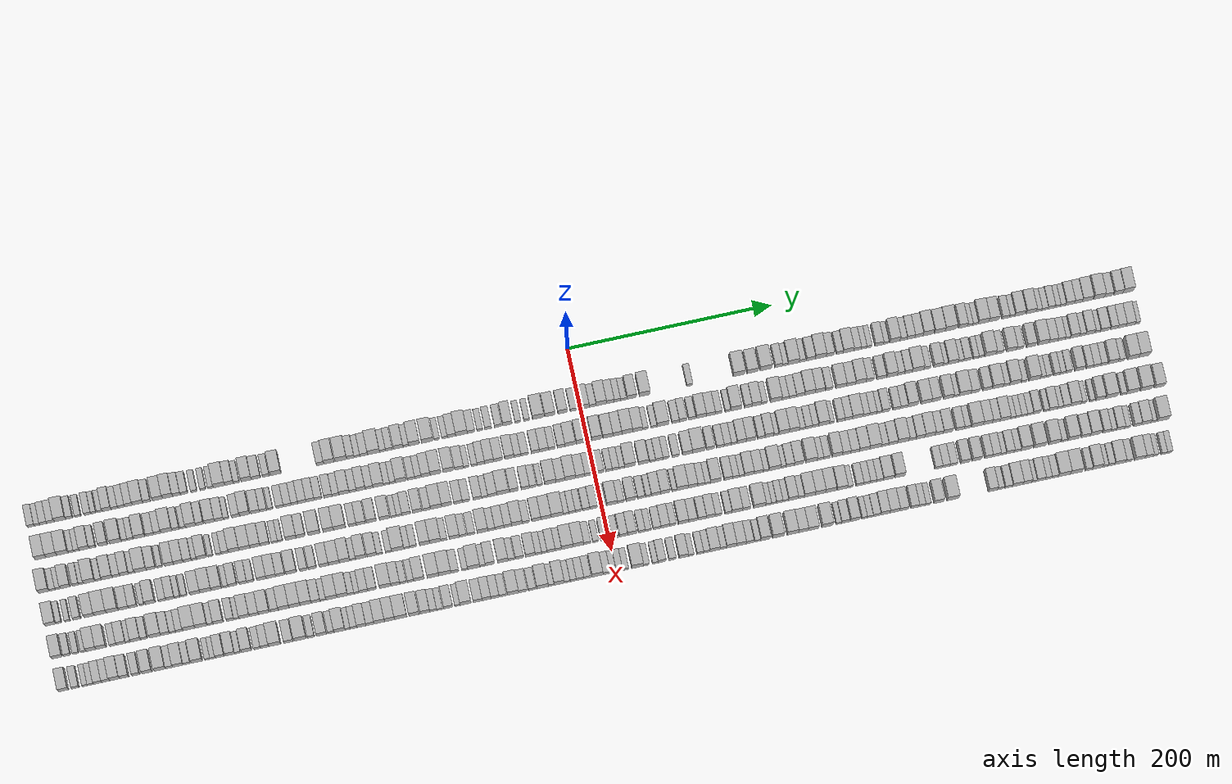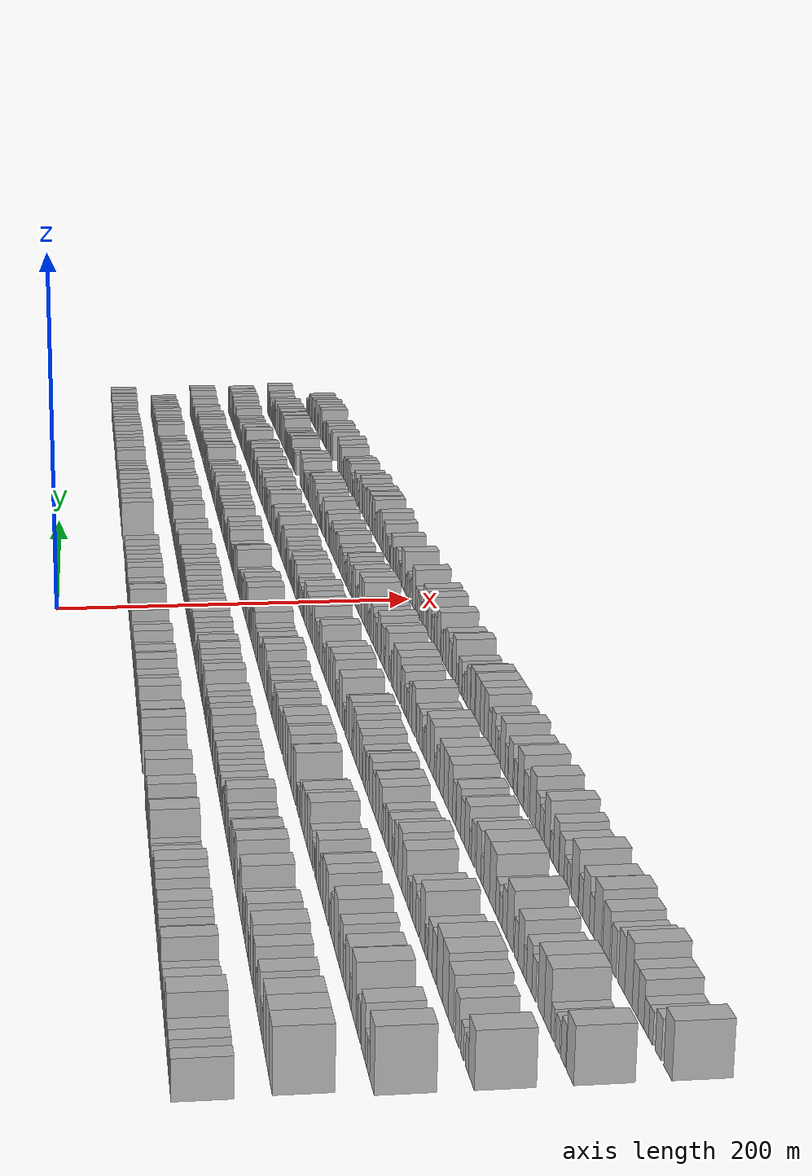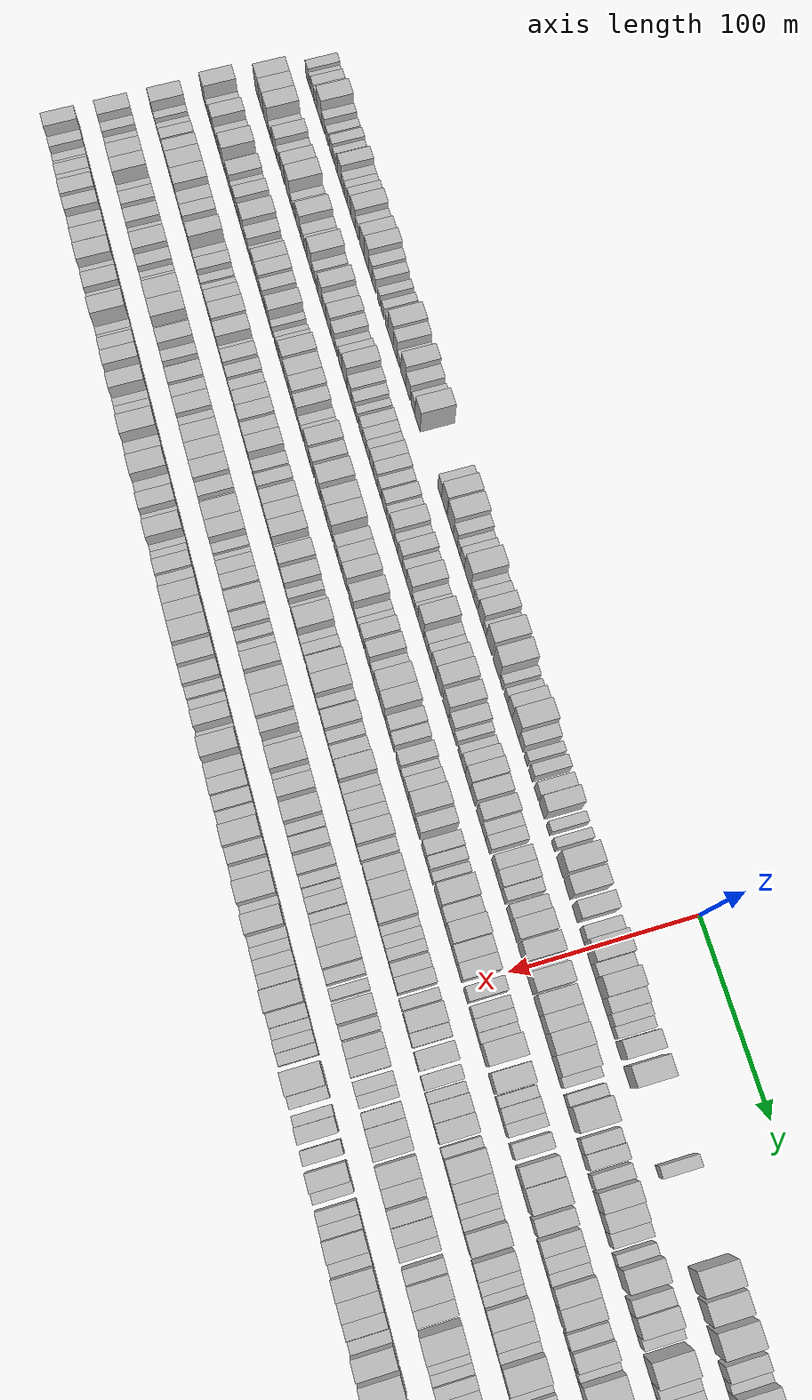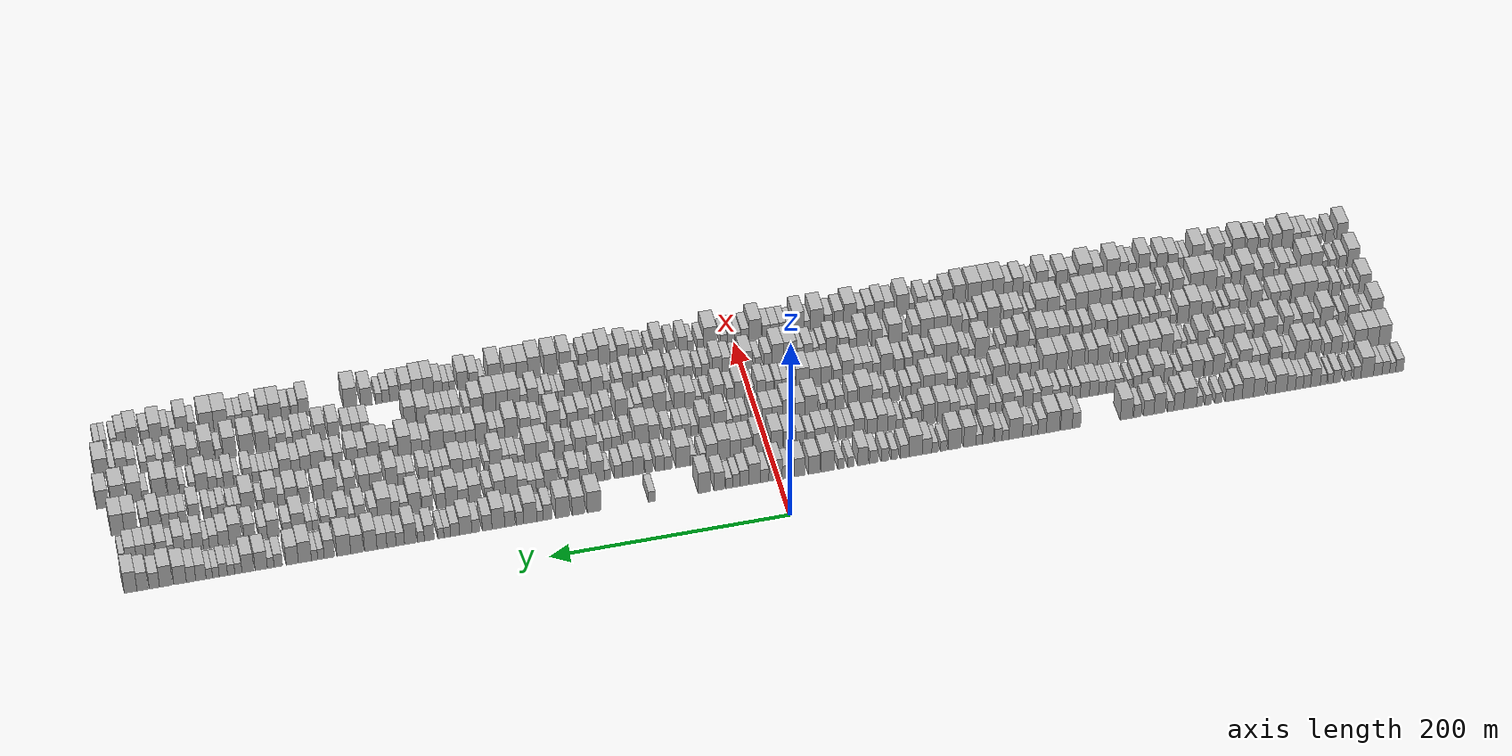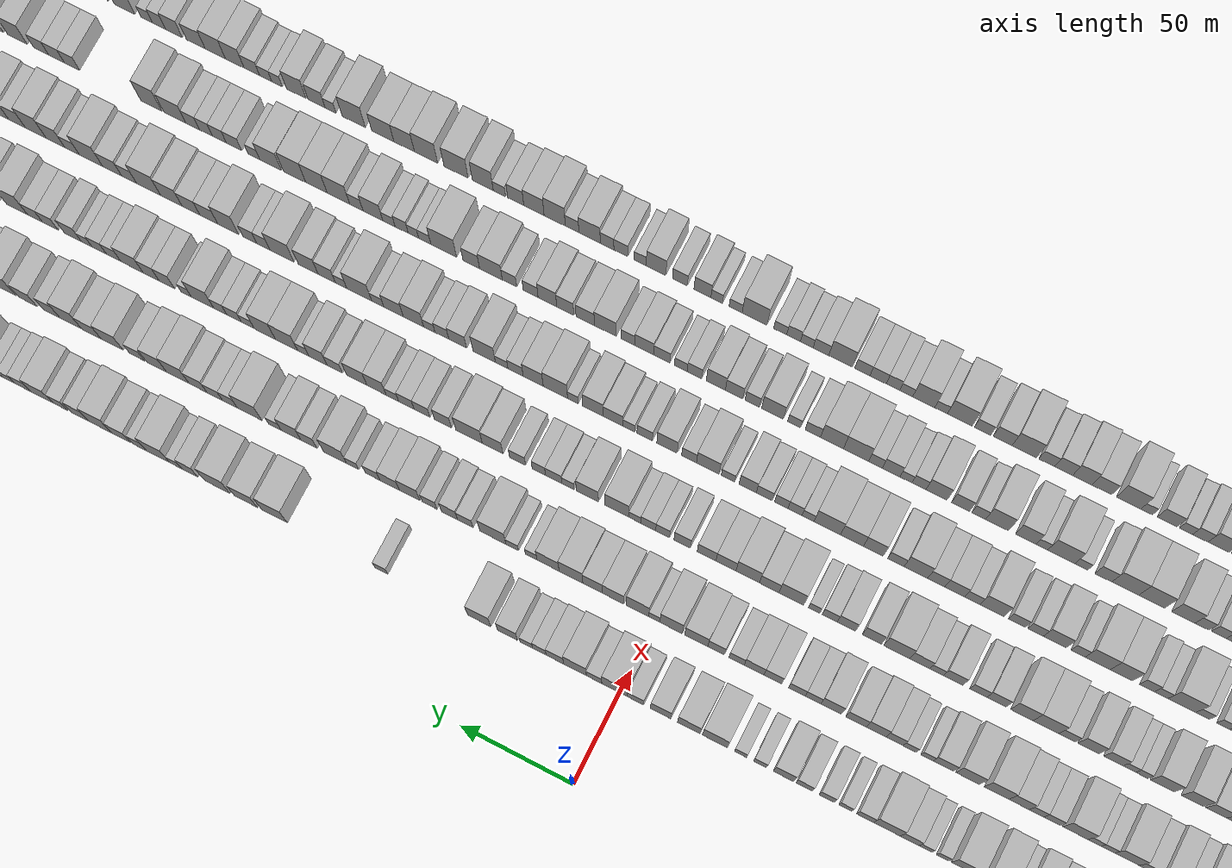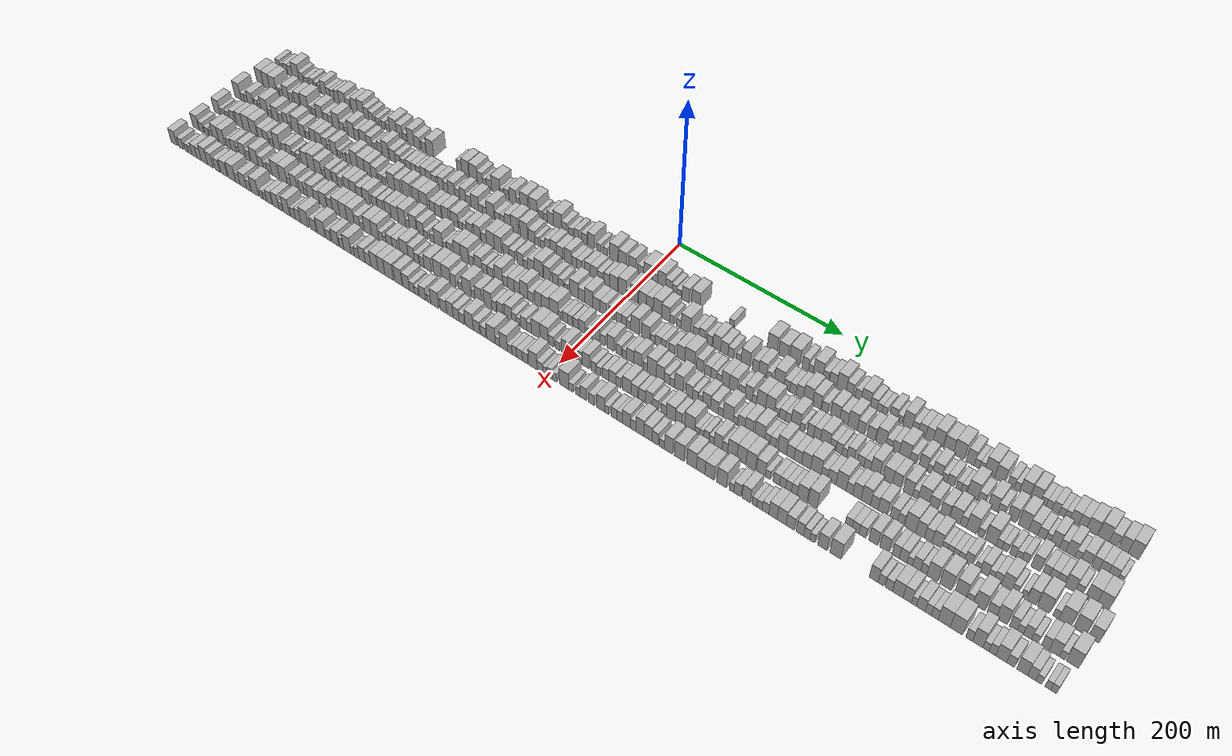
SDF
<sdf version="1.6">
 <world name="default">
  <scene>
   <sky><clouds><speed>12</speed></clouds></sky>
   <ambient>0.4 0.4 0.4 1</ambient>
   <background>0.7 0.7 0.7 1</background>
   <shadows>1</shadows>
  </scene>
  <gravity>0 0 -9.8066</gravity>
  <magnetic_field>6e-06 2.3e-05 -4.2e-05</magnetic_field>
  <physics default="0" name="default_physics" type="ode">
   <ode>
    <solver>
     <type>quick</type>
     <iters>10</iters>
     <sor>1.0</sor>
     <use_dynamic_moi_rescaling>0</use_dynamic_moi_rescaling>
    </solver>
    <constraints>
     <cfm>0</cfm>
     <erp>0.2</erp>
     <contact_max_correcting_vel>100</contact_max_correcting_vel>
     <contact_surface_layer>0.001</contact_surface_layer>
    </constraints>
   </ode>
   <max_step_size>0.004</max_step_size>
   <real_time_factor>1</real_time_factor>
   <real_time_update_rate>250</real_time_update_rate>
  </physics>
  <light name="sun" type="directional">
   <pose>0 0 10 0 0 0</pose>
   <diffuse>0.8 0.8 0.8 1</diffuse>
   <specular>0.2 0.2 0.2 1</specular>
   <attenuation>
    <range>1000</range>
    <constant>0.9</constant>
    <linear>0.01</linear>
    <quadratic>0.001</quadratic>
   </attenuation>
   <direction>-0.5 0.1 -0.9</direction>
  </light>
  <model name="building_1">
   <static>1</static>
   <pose>50.0000 -534.6168 0 0.000000 0.000000 0.000000</pose>
   <link name="link">
    <pose>0 0 7.50 0 0 0</pose>
    <collision name="collision"><geometry><box><size>20.0000 6.7664 15.0000</size></box></geometry></collision>
    <visual name="visual">
     <cast_shadows>0</cast_shadows>
     <geometry><box><size>20.0000 6.7664 15.0000</size></box></geometry>
     <material>
      <script>
       <uri>model://HANNAS_wall/materials/scripts</uri>
       <uri>model://HANNAS_wall/materials/textures</uri>
       <name>vrc/HANNAS_wall</name>
      </script>
     </material>
    </visual>
   </link>
  </model>
  <model name="building_2">
   <static>1</static>
   <pose>50.0000 -528.6167 0 0.000000 0.000000 0.000000</pose>
   <link name="link">
    <pose>0 0 6.00 0 0 0</pose>
    <collision name="collision"><geometry><box><size>20.0000 5.2339 12.0000</size></box></geometry></collision>
    <visual name="visual">
     <cast_shadows>0</cast_shadows>
     <geometry><box><size>20.0000 5.2339 12.0000</size></box></geometry>
     <material>
      <script>
       <uri>model://HANNAS_wall/materials/scripts</uri>
       <uri>model://HANNAS_wall/materials/textures</uri>
       <name>vrc/HANNAS_wall</name>
      </script>
     </material>
    </visual>
   </link>
  </model>
  <model name="building_3">
   <static>1</static>
   <pose>50.0000 -522.6289 0 0.000000 0.000000 0.000000</pose>
   <link name="link">
    <pose>0 0 7.50 0 0 0</pose>
    <collision name="collision"><geometry><box><size>20.0000 6.7417 15.0000</size></box></geometry></collision>
    <visual name="visual">
     <cast_shadows>0</cast_shadows>
     <geometry><box><size>20.0000 6.7417 15.0000</size></box></geometry>
     <material>
      <script>
       <uri>model://HANNAS_wall/materials/scripts</uri>
       <uri>model://HANNAS_wall/materials/textures</uri>
       <name>vrc/HANNAS_wall</name>
      </script>
     </material>
    </visual>
   </link>
  </model>
  <model name="building_4">
   <static>1</static>
   <pose>50.0000 -515.5239 0 0.000000 0.000000 0.000000</pose>
   <link name="link">
    <pose>0 0 7.50 0 0 0</pose>
    <collision name="collision"><geometry><box><size>20.0000 7.4683 15.0000</size></box></geometry></collision>
    <visual name="visual">
     <cast_shadows>0</cast_shadows>
     <geometry><box><size>20.0000 7.4683 15.0000</size></box></geometry>
     <material>
      <script>
       <uri>model://HANNAS_wall/materials/scripts</uri>
       <uri>model://HANNAS_wall/materials/textures</uri>
       <name>vrc/HANNAS_wall</name>
      </script>
     </material>
    </visual>
   </link>
  </model>
  <model name="building_5">
   <static>1</static>
   <pose>50.0000 -506.2095 0 0.000000 0.000000 0.000000</pose>
   <link name="link">
    <pose>0 0 12.00 0 0 0</pose>
    <collision name="collision"><geometry><box><size>20.0000 11.1605 24.0000</size></box></geometry></collision>
    <visual name="visual">
     <cast_shadows>0</cast_shadows>
     <geometry><box><size>20.0000 11.1605 24.0000</size></box></geometry>
     <material>
      <script>
       <uri>model://HANNAS_wall/materials/scripts</uri>
       <uri>model://HANNAS_wall/materials/textures</uri>
       <name>vrc/HANNAS_wall</name>
      </script>
     </material>
    </visual>
   </link>
  </model>
  <model name="building_6">
   <static>1</static>
   <pose>50.0000 -497.3670 0 0.000000 0.000000 0.000000</pose>
   <link name="link">
    <pose>0 0 7.50 0 0 0</pose>
    <collision name="collision"><geometry><box><size>20.0000 6.5246 15.0000</size></box></geometry></collision>
    <visual name="visual">
     <cast_shadows>0</cast_shadows>
     <geometry><box><size>20.0000 6.5246 15.0000</size></box></geometry>
     <material>
      <script>
       <uri>model://HANNAS_wall/materials/scripts</uri>
       <uri>model://HANNAS_wall/materials/textures</uri>
       <name>vrc/HANNAS_wall</name>
      </script>
     </material>
    </visual>
   </link>
  </model>
  <model name="building_7">
   <static>1</static>
   <pose>50.0000 -489.1371 0 0.000000 0.000000 0.000000</pose>
   <link name="link">
    <pose>0 0 6.00 0 0 0</pose>
    <collision name="collision"><geometry><box><size>20.0000 5.9351 12.0000</size></box></geometry></collision>
    <visual name="visual">
     <cast_shadows>0</cast_shadows>
     <geometry><box><size>20.0000 5.9351 12.0000</size></box></geometry>
     <material>
      <script>
       <uri>model://HANNAS_wall/materials/scripts</uri>
       <uri>model://HANNAS_wall/materials/textures</uri>
       <name>vrc/HANNAS_wall</name>
      </script>
     </material>
    </visual>
   </link>
  </model>
  <model name="building_8">
   <static>1</static>
   <pose>50.0000 -479.8209 0 0.000000 0.000000 0.000000</pose>
   <link name="link">
    <pose>0 0 7.50 0 0 0</pose>
    <collision name="collision"><geometry><box><size>20.0000 6.6973 15.0000</size></box></geometry></collision>
    <visual name="visual">
     <cast_shadows>0</cast_shadows>
     <geometry><box><size>20.0000 6.6973 15.0000</size></box></geometry>
     <material>
      <script>
       <uri>model://HANNAS_wall/materials/scripts</uri>
       <uri>model://HANNAS_wall/materials/textures</uri>
       <name>vrc/HANNAS_wall</name>
      </script>
     </material>
    </visual>
   </link>
  </model>
  <model name="building_9">
   <static>1</static>
   <pose>50.0000 -474.0490 0 0.000000 0.000000 0.000000</pose>
   <link name="link">
    <pose>0 0 6.00 0 0 0</pose>
    <collision name="collision"><geometry><box><size>20.0000 4.8466 12.0000</size></box></geometry></collision>
    <visual name="visual">
     <cast_shadows>0</cast_shadows>
     <geometry><box><size>20.0000 4.8466 12.0000</size></box></geometry>
     <material>
      <script>
       <uri>model://HANNAS_wall/materials/scripts</uri>
       <uri>model://HANNAS_wall/materials/textures</uri>
       <name>vrc/HANNAS_wall</name>
      </script>
     </material>
    </visual>
   </link>
  </model>
  <model name="building_10">
   <static>1</static>
   <pose>50.0000 -467.9414 0 0.000000 0.000000 0.000000</pose>
   <link name="link">
    <pose>0 0 6.00 0 0 0</pose>
    <collision name="collision"><geometry><box><size>20.0000 5.3687 12.0000</size></box></geometry></collision>
    <visual name="visual">
     <cast_shadows>0</cast_shadows>
     <geometry><box><size>20.0000 5.3687 12.0000</size></box></geometry>
     <material>
      <script>
       <uri>model://HANNAS_wall/materials/scripts</uri>
       <uri>model://HANNAS_wall/materials/textures</uri>
       <name>vrc/HANNAS_wall</name>
      </script>
     </material>
    </visual>
   </link>
  </model>
  <model name="building_11">
   <static>1</static>
   <pose>50.0000 -460.9712 0 0.000000 0.000000 0.000000</pose>
   <link name="link">
    <pose>0 0 10.50 0 0 0</pose>
    <collision name="collision"><geometry><box><size>20.0000 8.5717 21.0000</size></box></geometry></collision>
    <visual name="visual">
     <cast_shadows>0</cast_shadows>
     <geometry><box><size>20.0000 8.5717 21.0000</size></box></geometry>
     <material>
      <script>
       <uri>model://HANNAS_wall/materials/scripts</uri>
       <uri>model://HANNAS_wall/materials/textures</uri>
       <name>vrc/HANNAS_wall</name>
      </script>
     </material>
    </visual>
   </link>
  </model>
  <model name="building_12">
   <static>1</static>
   <pose>50.0000 -453.5250 0 0.000000 0.000000 0.000000</pose>
   <link name="link">
    <pose>0 0 7.50 0 0 0</pose>
    <collision name="collision"><geometry><box><size>20.0000 6.3207 15.0000</size></box></geometry></collision>
    <visual name="visual">
     <cast_shadows>0</cast_shadows>
     <geometry><box><size>20.0000 6.3207 15.0000</size></box></geometry>
     <material>
      <script>
       <uri>model://HANNAS_wall/materials/scripts</uri>
       <uri>model://HANNAS_wall/materials/textures</uri>
       <name>vrc/HANNAS_wall</name>
      </script>
     </material>
    </visual>
   </link>
  </model>
  <model name="building_13">
   <static>1</static>
   <pose>50.0000 -446.9261 0 0.000000 0.000000 0.000000</pose>
   <link name="link">
    <pose>0 0 7.50 0 0 0</pose>
    <collision name="collision"><geometry><box><size>20.0000 6.8771 15.0000</size></box></geometry></collision>
    <visual name="visual">
     <cast_shadows>0</cast_shadows>
     <geometry><box><size>20.0000 6.8771 15.0000</size></box></geometry>
     <material>
      <script>
       <uri>model://HANNAS_wall/materials/scripts</uri>
       <uri>model://HANNAS_wall/materials/textures</uri>
       <name>vrc/HANNAS_wall</name>
      </script>
     </material>
    </visual>
   </link>
  </model>
  <model name="building_14">
   <static>1</static>
   <pose>50.0000 -439.8316 0 0.000000 0.000000 0.000000</pose>
   <link name="link">
    <pose>0 0 9.00 0 0 0</pose>
    <collision name="collision"><geometry><box><size>20.0000 7.3120 18.0000</size></box></geometry></collision>
    <visual name="visual">
     <cast_shadows>0</cast_shadows>
     <geometry><box><size>20.0000 7.3120 18.0000</size></box></geometry>
     <material>
      <script>
       <uri>model://HANNAS_wall/materials/scripts</uri>
       <uri>model://HANNAS_wall/materials/textures</uri>
       <name>vrc/HANNAS_wall</name>
      </script>
     </material>
    </visual>
   </link>
  </model>
  <model name="building_15">
   <static>1</static>
   <pose>50.0000 -431.0234 0 0.000000 0.000000 0.000000</pose>
   <link name="link">
    <pose>0 0 10.50 0 0 0</pose>
    <collision name="collision"><geometry><box><size>20.0000 10.3044 21.0000</size></box></geometry></collision>
    <visual name="visual">
     <cast_shadows>0</cast_shadows>
     <geometry><box><size>20.0000 10.3044 21.0000</size></box></geometry>
     <material>
      <script>
       <uri>model://HANNAS_wall/materials/scripts</uri>
       <uri>model://HANNAS_wall/materials/textures</uri>
       <name>vrc/HANNAS_wall</name>
      </script>
     </material>
    </visual>
   </link>
  </model>
  <model name="building_16">
   <static>1</static>
   <pose>50.0000 -422.2763 0 0.000000 0.000000 0.000000</pose>
   <link name="link">
    <pose>0 0 7.50 0 0 0</pose>
    <collision name="collision"><geometry><box><size>20.0000 7.1896 15.0000</size></box></geometry></collision>
    <visual name="visual">
     <cast_shadows>0</cast_shadows>
     <geometry><box><size>20.0000 7.1896 15.0000</size></box></geometry>
     <material>
      <script>
       <uri>model://HANNAS_wall/materials/scripts</uri>
       <uri>model://HANNAS_wall/materials/textures</uri>
       <name>vrc/HANNAS_wall</name>
      </script>
     </material>
    </visual>
   </link>
  </model>
  <model name="building_17">
   <static>1</static>
   <pose>50.0000 -411.7645 0 0.000000 0.000000 0.000000</pose>
   <link name="link">
    <pose>0 0 10.50 0 0 0</pose>
    <collision name="collision"><geometry><box><size>20.0000 9.8341 21.0000</size></box></geometry></collision>
    <visual name="visual">
     <cast_shadows>0</cast_shadows>
     <geometry><box><size>20.0000 9.8341 21.0000</size></box></geometry>
     <material>
      <script>
       <uri>model://HANNAS_wall/materials/scripts</uri>
       <uri>model://HANNAS_wall/materials/textures</uri>
       <name>vrc/HANNAS_wall</name>
      </script>
     </material>
    </visual>
   </link>
  </model>
  <model name="building_18">
   <static>1</static>
   <pose>50.0000 -401.9997 0 0.000000 0.000000 0.000000</pose>
   <link name="link">
    <pose>0 0 12.00 0 0 0</pose>
    <collision name="collision"><geometry><box><size>20.0000 9.6955 24.0000</size></box></geometry></collision>
    <visual name="visual">
     <cast_shadows>0</cast_shadows>
     <geometry><box><size>20.0000 9.6955 24.0000</size></box></geometry>
     <material>
      <script>
       <uri>model://HANNAS_wall/materials/scripts</uri>
       <uri>model://HANNAS_wall/materials/textures</uri>
       <name>vrc/HANNAS_wall</name>
      </script>
     </material>
    </visual>
   </link>
  </model>
  <model name="building_19">
   <static>1</static>
   <pose>50.0000 -393.3858 0 0.000000 0.000000 0.000000</pose>
   <link name="link">
    <pose>0 0 9.00 0 0 0</pose>
    <collision name="collision"><geometry><box><size>20.0000 7.5322 18.0000</size></box></geometry></collision>
    <visual name="visual">
     <cast_shadows>0</cast_shadows>
     <geometry><box><size>20.0000 7.5322 18.0000</size></box></geometry>
     <material>
      <script>
       <uri>model://HANNAS_wall/materials/scripts</uri>
       <uri>model://HANNAS_wall/materials/textures</uri>
       <name>vrc/HANNAS_wall</name>
      </script>
     </material>
    </visual>
   </link>
  </model>
  <model name="building_20">
   <static>1</static>
   <pose>50.0000 -386.0687 0 0.000000 0.000000 0.000000</pose>
   <link name="link">
    <pose>0 0 7.50 0 0 0</pose>
    <collision name="collision"><geometry><box><size>20.0000 7.1021 15.0000</size></box></geometry></collision>
    <visual name="visual">
     <cast_shadows>0</cast_shadows>
     <geometry><box><size>20.0000 7.1021 15.0000</size></box></geometry>
     <material>
      <script>
       <uri>model://HANNAS_wall/materials/scripts</uri>
       <uri>model://HANNAS_wall/materials/textures</uri>
       <name>vrc/HANNAS_wall</name>
      </script>
     </material>
    </visual>
   </link>
  </model>
  <model name="building_21">
   <static>1</static>
   <pose>50.0000 -376.5502 0 0.000000 0.000000 0.000000</pose>
   <link name="link">
    <pose>0 0 6.00 0 0 0</pose>
    <collision name="collision"><geometry><box><size>20.0000 5.9349 12.0000</size></box></geometry></collision>
    <visual name="visual">
     <cast_shadows>0</cast_shadows>
     <geometry><box><size>20.0000 5.9349 12.0000</size></box></geometry>
     <material>
      <script>
       <uri>model://HANNAS_wall/materials/scripts</uri>
       <uri>model://HANNAS_wall/materials/textures</uri>
       <name>vrc/HANNAS_wall</name>
      </script>
     </material>
    </visual>
   </link>
  </model>
  <model name="building_22">
   <static>1</static>
   <pose>50.0000 -367.7630 0 0.000000 0.000000 0.000000</pose>
   <link name="link">
    <pose>0 0 6.00 0 0 0</pose>
    <collision name="collision"><geometry><box><size>20.0000 5.6394 12.0000</size></box></geometry></collision>
    <visual name="visual">
     <cast_shadows>0</cast_shadows>
     <geometry><box><size>20.0000 5.6394 12.0000</size></box></geometry>
     <material>
      <script>
       <uri>model://HANNAS_wall/materials/scripts</uri>
       <uri>model://HANNAS_wall/materials/textures</uri>
       <name>vrc/HANNAS_wall</name>
      </script>
     </material>
    </visual>
   </link>
  </model>
  <model name="building_23">
   <static>1</static>
   <pose>50.0000 -360.2245 0 0.000000 0.000000 0.000000</pose>
   <link name="link">
    <pose>0 0 6.00 0 0 0</pose>
    <collision name="collision"><geometry><box><size>20.0000 5.4376 12.0000</size></box></geometry></collision>
    <visual name="visual">
     <cast_shadows>0</cast_shadows>
     <geometry><box><size>20.0000 5.4376 12.0000</size></box></geometry>
     <material>
      <script>
       <uri>model://HANNAS_wall/materials/scripts</uri>
       <uri>model://HANNAS_wall/materials/textures</uri>
       <name>vrc/HANNAS_wall</name>
      </script>
     </material>
    </visual>
   </link>
  </model>
  <model name="building_24">
   <static>1</static>
   <pose>50.0000 -352.0016 0 0.000000 0.000000 0.000000</pose>
   <link name="link">
    <pose>0 0 12.00 0 0 0</pose>
    <collision name="collision"><geometry><box><size>20.0000 11.0083 24.0000</size></box></geometry></collision>
    <visual name="visual">
     <cast_shadows>0</cast_shadows>
     <geometry><box><size>20.0000 11.0083 24.0000</size></box></geometry>
     <material>
      <script>
       <uri>model://HANNAS_wall/materials/scripts</uri>
       <uri>model://HANNAS_wall/materials/textures</uri>
       <name>vrc/HANNAS_wall</name>
      </script>
     </material>
    </visual>
   </link>
  </model>
  <model name="building_25">
   <static>1</static>
   <pose>50.0000 -342.2890 0 0.000000 0.000000 0.000000</pose>
   <link name="link">
    <pose>0 0 10.50 0 0 0</pose>
    <collision name="collision"><geometry><box><size>20.0000 8.4170 21.0000</size></box></geometry></collision>
    <visual name="visual">
     <cast_shadows>0</cast_shadows>
     <geometry><box><size>20.0000 8.4170 21.0000</size></box></geometry>
     <material>
      <script>
       <uri>model://HANNAS_wall/materials/scripts</uri>
       <uri>model://HANNAS_wall/materials/textures</uri>
       <name>vrc/HANNAS_wall</name>
      </script>
     </material>
    </visual>
   </link>
  </model>
  <model name="building_26">
   <static>1</static>
   <pose>50.0000 -335.2991 0 0.000000 0.000000 0.000000</pose>
   <link name="link">
    <pose>0 0 6.00 0 0 0</pose>
    <collision name="collision"><geometry><box><size>20.0000 5.5628 12.0000</size></box></geometry></collision>
    <visual name="visual">
     <cast_shadows>0</cast_shadows>
     <geometry><box><size>20.0000 5.5628 12.0000</size></box></geometry>
     <material>
      <script>
       <uri>model://HANNAS_wall/materials/scripts</uri>
       <uri>model://HANNAS_wall/materials/textures</uri>
       <name>vrc/HANNAS_wall</name>
      </script>
     </material>
    </visual>
   </link>
  </model>
  <model name="building_27">
   <static>1</static>
   <pose>50.0000 -325.5747 0 0.000000 0.000000 0.000000</pose>
   <link name="link">
    <pose>0 0 12.00 0 0 0</pose>
    <collision name="collision"><geometry><box><size>20.0000 9.8861 24.0000</size></box></geometry></collision>
    <visual name="visual">
     <cast_shadows>0</cast_shadows>
     <geometry><box><size>20.0000 9.8861 24.0000</size></box></geometry>
     <material>
      <script>
       <uri>model://HANNAS_wall/materials/scripts</uri>
       <uri>model://HANNAS_wall/materials/textures</uri>
       <name>vrc/HANNAS_wall</name>
      </script>
     </material>
    </visual>
   </link>
  </model>
  <model name="building_28">
   <static>1</static>
   <pose>50.0000 -316.2201 0 0.000000 0.000000 0.000000</pose>
   <link name="link">
    <pose>0 0 9.00 0 0 0</pose>
    <collision name="collision"><geometry><box><size>20.0000 8.8230 18.0000</size></box></geometry></collision>
    <visual name="visual">
     <cast_shadows>0</cast_shadows>
     <geometry><box><size>20.0000 8.8230 18.0000</size></box></geometry>
     <material>
      <script>
       <uri>model://HANNAS_wall/materials/scripts</uri>
       <uri>model://HANNAS_wall/materials/textures</uri>
       <name>vrc/HANNAS_wall</name>
      </script>
     </material>
    </visual>
   </link>
  </model>
  <model name="building_29">
   <static>1</static>
   <pose>50.0000 -306.5845 0 0.000000 0.000000 0.000000</pose>
   <link name="link">
    <pose>0 0 7.50 0 0 0</pose>
    <collision name="collision"><geometry><box><size>20.0000 6.4483 15.0000</size></box></geometry></collision>
    <visual name="visual">
     <cast_shadows>0</cast_shadows>
     <geometry><box><size>20.0000 6.4483 15.0000</size></box></geometry>
     <material>
      <script>
       <uri>model://HANNAS_wall/materials/scripts</uri>
       <uri>model://HANNAS_wall/materials/textures</uri>
       <name>vrc/HANNAS_wall</name>
      </script>
     </material>
    </visual>
   </link>
  </model>
  <model name="building_30">
   <static>1</static>
   <pose>50.0000 -297.0461 0 0.000000 0.000000 0.000000</pose>
   <link name="link">
    <pose>0 0 12.00 0 0 0</pose>
    <collision name="collision"><geometry><box><size>20.0000 10.6283 24.0000</size></box></geometry></collision>
    <visual name="visual">
     <cast_shadows>0</cast_shadows>
     <geometry><box><size>20.0000 10.6283 24.0000</size></box></geometry>
     <material>
      <script>
       <uri>model://HANNAS_wall/materials/scripts</uri>
       <uri>model://HANNAS_wall/materials/textures</uri>
       <name>vrc/HANNAS_wall</name>
      </script>
     </material>
    </visual>
   </link>
  </model>
  <model name="building_31">
   <static>1</static>
   <pose>50.0000 -253.9030 0 0.000000 0.000000 0.000000</pose>
   <link name="link">
    <pose>0 0 9.00 0 0 0</pose>
    <collision name="collision"><geometry><box><size>20.0000 7.2193 18.0000</size></box></geometry></collision>
    <visual name="visual">
     <cast_shadows>0</cast_shadows>
     <geometry><box><size>20.0000 7.2193 18.0000</size></box></geometry>
     <material>
      <script>
       <uri>model://HANNAS_wall/materials/scripts</uri>
       <uri>model://HANNAS_wall/materials/textures</uri>
       <name>vrc/HANNAS_wall</name>
      </script>
     </material>
    </visual>
   </link>
  </model>
  <model name="building_32">
   <static>1</static>
   <pose>50.0000 -245.3170 0 0.000000 0.000000 0.000000</pose>
   <link name="link">
    <pose>0 0 12.00 0 0 0</pose>
    <collision name="collision"><geometry><box><size>20.0000 9.9528 24.0000</size></box></geometry></collision>
    <visual name="visual">
     <cast_shadows>0</cast_shadows>
     <geometry><box><size>20.0000 9.9528 24.0000</size></box></geometry>
     <material>
      <script>
       <uri>model://HANNAS_wall/materials/scripts</uri>
       <uri>model://HANNAS_wall/materials/textures</uri>
       <name>vrc/HANNAS_wall</name>
      </script>
     </material>
    </visual>
   </link>
  </model>
  <model name="building_33">
   <static>1</static>
   <pose>50.0000 -233.6739 0 0.000000 0.000000 0.000000</pose>
   <link name="link">
    <pose>0 0 12.00 0 0 0</pose>
    <collision name="collision"><geometry><box><size>20.0000 11.3334 24.0000</size></box></geometry></collision>
    <visual name="visual">
     <cast_shadows>0</cast_shadows>
     <geometry><box><size>20.0000 11.3334 24.0000</size></box></geometry>
     <material>
      <script>
       <uri>model://HANNAS_wall/materials/scripts</uri>
       <uri>model://HANNAS_wall/materials/textures</uri>
       <name>vrc/HANNAS_wall</name>
      </script>
     </material>
    </visual>
   </link>
  </model>
  <model name="building_34">
   <static>1</static>
   <pose>50.0000 -224.3679 0 0.000000 0.000000 0.000000</pose>
   <link name="link">
    <pose>0 0 9.00 0 0 0</pose>
    <collision name="collision"><geometry><box><size>20.0000 7.2786 18.0000</size></box></geometry></collision>
    <visual name="visual">
     <cast_shadows>0</cast_shadows>
     <geometry><box><size>20.0000 7.2786 18.0000</size></box></geometry>
     <material>
      <script>
       <uri>model://HANNAS_wall/materials/scripts</uri>
       <uri>model://HANNAS_wall/materials/textures</uri>
       <name>vrc/HANNAS_wall</name>
      </script>
     </material>
    </visual>
   </link>
  </model>
  <model name="building_35">
   <static>1</static>
   <pose>50.0000 -217.9440 0 0.000000 0.000000 0.000000</pose>
   <link name="link">
    <pose>0 0 6.00 0 0 0</pose>
    <collision name="collision"><geometry><box><size>20.0000 5.5694 12.0000</size></box></geometry></collision>
    <visual name="visual">
     <cast_shadows>0</cast_shadows>
     <geometry><box><size>20.0000 5.5694 12.0000</size></box></geometry>
     <material>
      <script>
       <uri>model://HANNAS_wall/materials/scripts</uri>
       <uri>model://HANNAS_wall/materials/textures</uri>
       <name>vrc/HANNAS_wall</name>
      </script>
     </material>
    </visual>
   </link>
  </model>
  <model name="building_36">
   <static>1</static>
   <pose>50.0000 -211.4095 0 0.000000 0.000000 0.000000</pose>
   <link name="link">
    <pose>0 0 7.50 0 0 0</pose>
    <collision name="collision"><geometry><box><size>20.0000 7.4997 15.0000</size></box></geometry></collision>
    <visual name="visual">
     <cast_shadows>0</cast_shadows>
     <geometry><box><size>20.0000 7.4997 15.0000</size></box></geometry>
     <material>
      <script>
       <uri>model://HANNAS_wall/materials/scripts</uri>
       <uri>model://HANNAS_wall/materials/textures</uri>
       <name>vrc/HANNAS_wall</name>
      </script>
     </material>
    </visual>
   </link>
  </model>
  <model name="building_37">
   <static>1</static>
   <pose>50.0000 -201.8134 0 0.000000 0.000000 0.000000</pose>
   <link name="link">
    <pose>0 0 12.00 0 0 0</pose>
    <collision name="collision"><geometry><box><size>20.0000 11.6925 24.0000</size></box></geometry></collision>
    <visual name="visual">
     <cast_shadows>0</cast_shadows>
     <geometry><box><size>20.0000 11.6925 24.0000</size></box></geometry>
     <material>
      <script>
       <uri>model://HANNAS_wall/materials/scripts</uri>
       <uri>model://HANNAS_wall/materials/textures</uri>
       <name>vrc/HANNAS_wall</name>
      </script>
     </material>
    </visual>
   </link>
  </model>
  <model name="building_38">
   <static>1</static>
   <pose>50.0000 -193.0613 0 0.000000 0.000000 0.000000</pose>
   <link name="link">
    <pose>0 0 6.00 0 0 0</pose>
    <collision name="collision"><geometry><box><size>20.0000 5.8116 12.0000</size></box></geometry></collision>
    <visual name="visual">
     <cast_shadows>0</cast_shadows>
     <geometry><box><size>20.0000 5.8116 12.0000</size></box></geometry>
     <material>
      <script>
       <uri>model://HANNAS_wall/materials/scripts</uri>
       <uri>model://HANNAS_wall/materials/textures</uri>
       <name>vrc/HANNAS_wall</name>
      </script>
     </material>
    </visual>
   </link>
  </model>
  <model name="building_39">
   <static>1</static>
   <pose>50.0000 -186.8491 0 0.000000 0.000000 0.000000</pose>
   <link name="link">
    <pose>0 0 7.50 0 0 0</pose>
    <collision name="collision"><geometry><box><size>20.0000 6.6129 15.0000</size></box></geometry></collision>
    <visual name="visual">
     <cast_shadows>0</cast_shadows>
     <geometry><box><size>20.0000 6.6129 15.0000</size></box></geometry>
     <material>
      <script>
       <uri>model://HANNAS_wall/materials/scripts</uri>
       <uri>model://HANNAS_wall/materials/textures</uri>
       <name>vrc/HANNAS_wall</name>
      </script>
     </material>
    </visual>
   </link>
  </model>
  <model name="building_40">
   <static>1</static>
   <pose>50.0000 -177.8994 0 0.000000 0.000000 0.000000</pose>
   <link name="link">
    <pose>0 0 10.50 0 0 0</pose>
    <collision name="collision"><geometry><box><size>20.0000 9.2864 21.0000</size></box></geometry></collision>
    <visual name="visual">
     <cast_shadows>0</cast_shadows>
     <geometry><box><size>20.0000 9.2864 21.0000</size></box></geometry>
     <material>
      <script>
       <uri>model://HANNAS_wall/materials/scripts</uri>
       <uri>model://HANNAS_wall/materials/textures</uri>
       <name>vrc/HANNAS_wall</name>
      </script>
     </material>
    </visual>
   </link>
  </model>
  <model name="building_41">
   <static>1</static>
   <pose>50.0000 -170.5214 0 0.000000 0.000000 0.000000</pose>
   <link name="link">
    <pose>0 0 6.00 0 0 0</pose>
    <collision name="collision"><geometry><box><size>20.0000 5.4694 12.0000</size></box></geometry></collision>
    <visual name="visual">
     <cast_shadows>0</cast_shadows>
     <geometry><box><size>20.0000 5.4694 12.0000</size></box></geometry>
     <material>
      <script>
       <uri>model://HANNAS_wall/materials/scripts</uri>
       <uri>model://HANNAS_wall/materials/textures</uri>
       <name>vrc/HANNAS_wall</name>
      </script>
     </material>
    </visual>
   </link>
  </model>
  <model name="building_42">
   <static>1</static>
   <pose>50.0000 -162.4964 0 0.000000 0.000000 0.000000</pose>
   <link name="link">
    <pose>0 0 12.00 0 0 0</pose>
    <collision name="collision"><geometry><box><size>20.0000 10.5806 24.0000</size></box></geometry></collision>
    <visual name="visual">
     <cast_shadows>0</cast_shadows>
     <geometry><box><size>20.0000 10.5806 24.0000</size></box></geometry>
     <material>
      <script>
       <uri>model://HANNAS_wall/materials/scripts</uri>
       <uri>model://HANNAS_wall/materials/textures</uri>
       <name>vrc/HANNAS_wall</name>
      </script>
     </material>
    </visual>
   </link>
  </model>
  <model name="building_43">
   <static>1</static>
   <pose>50.0000 -149.6053 0 0.000000 0.000000 0.000000</pose>
   <link name="link">
    <pose>0 0 12.00 0 0 0</pose>
    <collision name="collision"><geometry><box><size>20.0000 11.2016 24.0000</size></box></geometry></collision>
    <visual name="visual">
     <cast_shadows>0</cast_shadows>
     <geometry><box><size>20.0000 11.2016 24.0000</size></box></geometry>
     <material>
      <script>
       <uri>model://HANNAS_wall/materials/scripts</uri>
       <uri>model://HANNAS_wall/materials/textures</uri>
       <name>vrc/HANNAS_wall</name>
      </script>
     </material>
    </visual>
   </link>
  </model>
  <model name="building_44">
   <static>1</static>
   <pose>50.0000 -140.2981 0 0.000000 0.000000 0.000000</pose>
   <link name="link">
    <pose>0 0 6.00 0 0 0</pose>
    <collision name="collision"><geometry><box><size>20.0000 5.4127 12.0000</size></box></geometry></collision>
    <visual name="visual">
     <cast_shadows>0</cast_shadows>
     <geometry><box><size>20.0000 5.4127 12.0000</size></box></geometry>
     <material>
      <script>
       <uri>model://HANNAS_wall/materials/scripts</uri>
       <uri>model://HANNAS_wall/materials/textures</uri>
       <name>vrc/HANNAS_wall</name>
      </script>
     </material>
    </visual>
   </link>
  </model>
  <model name="building_45">
   <static>1</static>
   <pose>50.0000 -132.8563 0 0.000000 0.000000 0.000000</pose>
   <link name="link">
    <pose>0 0 6.00 0 0 0</pose>
    <collision name="collision"><geometry><box><size>20.0000 5.4709 12.0000</size></box></geometry></collision>
    <visual name="visual">
     <cast_shadows>0</cast_shadows>
     <geometry><box><size>20.0000 5.4709 12.0000</size></box></geometry>
     <material>
      <script>
       <uri>model://HANNAS_wall/materials/scripts</uri>
       <uri>model://HANNAS_wall/materials/textures</uri>
       <name>vrc/HANNAS_wall</name>
      </script>
     </material>
    </visual>
   </link>
  </model>
  <model name="building_46">
   <static>1</static>
   <pose>50.0000 -126.0990 0 0.000000 0.000000 0.000000</pose>
   <link name="link">
    <pose>0 0 9.00 0 0 0</pose>
    <collision name="collision"><geometry><box><size>20.0000 8.0437 18.0000</size></box></geometry></collision>
    <visual name="visual">
     <cast_shadows>0</cast_shadows>
     <geometry><box><size>20.0000 8.0437 18.0000</size></box></geometry>
     <material>
      <script>
       <uri>model://HANNAS_wall/materials/scripts</uri>
       <uri>model://HANNAS_wall/materials/textures</uri>
       <name>vrc/HANNAS_wall</name>
      </script>
     </material>
    </visual>
   </link>
  </model>
  <model name="building_47">
   <static>1</static>
   <pose>50.0000 -116.3483 0 0.000000 0.000000 0.000000</pose>
   <link name="link">
    <pose>0 0 12.00 0 0 0</pose>
    <collision name="collision"><geometry><box><size>20.0000 11.4578 24.0000</size></box></geometry></collision>
    <visual name="visual">
     <cast_shadows>0</cast_shadows>
     <geometry><box><size>20.0000 11.4578 24.0000</size></box></geometry>
     <material>
      <script>
       <uri>model://HANNAS_wall/materials/scripts</uri>
       <uri>model://HANNAS_wall/materials/textures</uri>
       <name>vrc/HANNAS_wall</name>
      </script>
     </material>
    </visual>
   </link>
  </model>
  <model name="building_48">
   <static>1</static>
   <pose>50.0000 -106.9327 0 0.000000 0.000000 0.000000</pose>
   <link name="link">
    <pose>0 0 7.50 0 0 0</pose>
    <collision name="collision"><geometry><box><size>20.0000 7.3733 15.0000</size></box></geometry></collision>
    <visual name="visual">
     <cast_shadows>0</cast_shadows>
     <geometry><box><size>20.0000 7.3733 15.0000</size></box></geometry>
     <material>
      <script>
       <uri>model://HANNAS_wall/materials/scripts</uri>
       <uri>model://HANNAS_wall/materials/textures</uri>
       <name>vrc/HANNAS_wall</name>
      </script>
     </material>
    </visual>
   </link>
  </model>
  <model name="building_49">
   <static>1</static>
   <pose>50.0000 -98.4326 0 0.000000 0.000000 0.000000</pose>
   <link name="link">
    <pose>0 0 6.00 0 0 0</pose>
    <collision name="collision"><geometry><box><size>20.0000 5.6270 12.0000</size></box></geometry></collision>
    <visual name="visual">
     <cast_shadows>0</cast_shadows>
     <geometry><box><size>20.0000 5.6270 12.0000</size></box></geometry>
     <material>
      <script>
       <uri>model://HANNAS_wall/materials/scripts</uri>
       <uri>model://HANNAS_wall/materials/textures</uri>
       <name>vrc/HANNAS_wall</name>
      </script>
     </material>
    </visual>
   </link>
  </model>
  <model name="building_50">
   <static>1</static>
   <pose>50.0000 -90.3357 0 0.000000 0.000000 0.000000</pose>
   <link name="link">
    <pose>0 0 7.50 0 0 0</pose>
    <collision name="collision"><geometry><box><size>20.0000 6.5668 15.0000</size></box></geometry></collision>
    <visual name="visual">
     <cast_shadows>0</cast_shadows>
     <geometry><box><size>20.0000 6.5668 15.0000</size></box></geometry>
     <material>
      <script>
       <uri>model://HANNAS_wall/materials/scripts</uri>
       <uri>model://HANNAS_wall/materials/textures</uri>
       <name>vrc/HANNAS_wall</name>
      </script>
     </material>
    </visual>
   </link>
  </model>
  <model name="building_51">
   <static>1</static>
   <pose>50.0000 -80.5585 0 0.000000 0.000000 0.000000</pose>
   <link name="link">
    <pose>0 0 7.50 0 0 0</pose>
    <collision name="collision"><geometry><box><size>20.0000 6.9876 15.0000</size></box></geometry></collision>
    <visual name="visual">
     <cast_shadows>0</cast_shadows>
     <geometry><box><size>20.0000 6.9876 15.0000</size></box></geometry>
     <material>
      <script>
       <uri>model://HANNAS_wall/materials/scripts</uri>
       <uri>model://HANNAS_wall/materials/textures</uri>
       <name>vrc/HANNAS_wall</name>
      </script>
     </material>
    </visual>
   </link>
  </model>
  <model name="building_52">
   <static>1</static>
   <pose>50.0000 -71.5843 0 0.000000 0.000000 0.000000</pose>
   <link name="link">
    <pose>0 0 10.50 0 0 0</pose>
    <collision name="collision"><geometry><box><size>20.0000 8.9609 21.0000</size></box></geometry></collision>
    <visual name="visual">
     <cast_shadows>0</cast_shadows>
     <geometry><box><size>20.0000 8.9609 21.0000</size></box></geometry>
     <material>
      <script>
       <uri>model://HANNAS_wall/materials/scripts</uri>
       <uri>model://HANNAS_wall/materials/textures</uri>
       <name>vrc/HANNAS_wall</name>
      </script>
     </material>
    </visual>
   </link>
  </model>
  <model name="building_53">
   <static>1</static>
   <pose>50.0000 -61.3006 0 0.000000 0.000000 0.000000</pose>
   <link name="link">
    <pose>0 0 6.00 0 0 0</pose>
    <collision name="collision"><geometry><box><size>20.0000 5.6066 12.0000</size></box></geometry></collision>
    <visual name="visual">
     <cast_shadows>0</cast_shadows>
     <geometry><box><size>20.0000 5.6066 12.0000</size></box></geometry>
     <material>
      <script>
       <uri>model://HANNAS_wall/materials/scripts</uri>
       <uri>model://HANNAS_wall/materials/textures</uri>
       <name>vrc/HANNAS_wall</name>
      </script>
     </material>
    </visual>
   </link>
  </model>
  <model name="building_54">
   <static>1</static>
   <pose>50.0000 -52.8115 0 0.000000 0.000000 0.000000</pose>
   <link name="link">
    <pose>0 0 6.00 0 0 0</pose>
    <collision name="collision"><geometry><box><size>20.0000 5.3717 12.0000</size></box></geometry></collision>
    <visual name="visual">
     <cast_shadows>0</cast_shadows>
     <geometry><box><size>20.0000 5.3717 12.0000</size></box></geometry>
     <material>
      <script>
       <uri>model://HANNAS_wall/materials/scripts</uri>
       <uri>model://HANNAS_wall/materials/textures</uri>
       <name>vrc/HANNAS_wall</name>
      </script>
     </material>
    </visual>
   </link>
  </model>
  <model name="building_55">
   <static>1</static>
   <pose>50.0000 -41.6342 0 0.000000 0.000000 0.000000</pose>
   <link name="link">
    <pose>0 0 12.00 0 0 0</pose>
    <collision name="collision"><geometry><box><size>20.0000 10.9829 24.0000</size></box></geometry></collision>
    <visual name="visual">
     <cast_shadows>0</cast_shadows>
     <geometry><box><size>20.0000 10.9829 24.0000</size></box></geometry>
     <material>
      <script>
       <uri>model://HANNAS_wall/materials/scripts</uri>
       <uri>model://HANNAS_wall/materials/textures</uri>
       <name>vrc/HANNAS_wall</name>
      </script>
     </material>
    </visual>
   </link>
  </model>
  <model name="building_56">
   <static>1</static>
   <pose>50.0000 -30.2093 0 0.000000 0.000000 0.000000</pose>
   <link name="link">
    <pose>0 0 10.50 0 0 0</pose>
    <collision name="collision"><geometry><box><size>20.0000 9.8670 21.0000</size></box></geometry></collision>
    <visual name="visual">
     <cast_shadows>0</cast_shadows>
     <geometry><box><size>20.0000 9.8670 21.0000</size></box></geometry>
     <material>
      <script>
       <uri>model://HANNAS_wall/materials/scripts</uri>
       <uri>model://HANNAS_wall/materials/textures</uri>
       <name>vrc/HANNAS_wall</name>
      </script>
     </material>
    </visual>
   </link>
  </model>
  <model name="building_57">
   <static>1</static>
   <pose>50.0000 -17.8155 0 0.000000 0.000000 0.000000</pose>
   <link name="link">
    <pose>0 0 10.50 0 0 0</pose>
    <collision name="collision"><geometry><box><size>20.0000 8.9206 21.0000</size></box></geometry></collision>
    <visual name="visual">
     <cast_shadows>0</cast_shadows>
     <geometry><box><size>20.0000 8.9206 21.0000</size></box></geometry>
     <material>
      <script>
       <uri>model://HANNAS_wall/materials/scripts</uri>
       <uri>model://HANNAS_wall/materials/textures</uri>
       <name>vrc/HANNAS_wall</name>
      </script>
     </material>
    </visual>
   </link>
  </model>
  <model name="building_58">
   <static>1</static>
   <pose>50.0000 -6.7645 0 0.000000 0.000000 0.000000</pose>
   <link name="link">
    <pose>0 0 7.50 0 0 0</pose>
    <collision name="collision"><geometry><box><size>20.0000 7.1813 15.0000</size></box></geometry></collision>
    <visual name="visual">
     <cast_shadows>0</cast_shadows>
     <geometry><box><size>20.0000 7.1813 15.0000</size></box></geometry>
     <material>
      <script>
       <uri>model://HANNAS_wall/materials/scripts</uri>
       <uri>model://HANNAS_wall/materials/textures</uri>
       <name>vrc/HANNAS_wall</name>
      </script>
     </material>
    </visual>
   </link>
  </model>
  <model name="building_59">
   <static>1</static>
   <pose>50.0000 2.4540 0 0.000000 0.000000 0.000000</pose>
   <link name="link">
    <pose>0 0 12.00 0 0 0</pose>
    <collision name="collision"><geometry><box><size>20.0000 11.2558 24.0000</size></box></geometry></collision>
    <visual name="visual">
     <cast_shadows>0</cast_shadows>
     <geometry><box><size>20.0000 11.2558 24.0000</size></box></geometry>
     <material>
      <script>
       <uri>model://HANNAS_wall/materials/scripts</uri>
       <uri>model://HANNAS_wall/materials/textures</uri>
       <name>vrc/HANNAS_wall</name>
      </script>
     </material>
    </visual>
   </link>
  </model>
  <model name="building_60">
   <static>1</static>
   <pose>50.0000 11.4748 0 0.000000 0.000000 0.000000</pose>
   <link name="link">
    <pose>0 0 7.50 0 0 0</pose>
    <collision name="collision"><geometry><box><size>20.0000 6.7858 15.0000</size></box></geometry></collision>
    <visual name="visual">
     <cast_shadows>0</cast_shadows>
     <geometry><box><size>20.0000 6.7858 15.0000</size></box></geometry>
     <material>
      <script>
       <uri>model://HANNAS_wall/materials/scripts</uri>
       <uri>model://HANNAS_wall/materials/textures</uri>
       <name>vrc/HANNAS_wall</name>
      </script>
     </material>
    </visual>
   </link>
  </model>
  <model name="building_61">
   <static>1</static>
   <pose>50.0000 19.8986 0 0.000000 0.000000 0.000000</pose>
   <link name="link">
    <pose>0 0 12.00 0 0 0</pose>
    <collision name="collision"><geometry><box><size>20.0000 10.0618 24.0000</size></box></geometry></collision>
    <visual name="visual">
     <cast_shadows>0</cast_shadows>
     <geometry><box><size>20.0000 10.0618 24.0000</size></box></geometry>
     <material>
      <script>
       <uri>model://HANNAS_wall/materials/scripts</uri>
       <uri>model://HANNAS_wall/materials/textures</uri>
       <name>vrc/HANNAS_wall</name>
      </script>
     </material>
    </visual>
   </link>
  </model>
  <model name="building_62">
   <static>1</static>
   <pose>50.0000 28.7914 0 0.000000 0.000000 0.000000</pose>
   <link name="link">
    <pose>0 0 9.00 0 0 0</pose>
    <collision name="collision"><geometry><box><size>20.0000 7.7238 18.0000</size></box></geometry></collision>
    <visual name="visual">
     <cast_shadows>0</cast_shadows>
     <geometry><box><size>20.0000 7.7238 18.0000</size></box></geometry>
     <material>
      <script>
       <uri>model://HANNAS_wall/materials/scripts</uri>
       <uri>model://HANNAS_wall/materials/textures</uri>
       <name>vrc/HANNAS_wall</name>
      </script>
     </material>
    </visual>
   </link>
  </model>
  <model name="building_63">
   <static>1</static>
   <pose>50.0000 35.6680 0 0.000000 0.000000 0.000000</pose>
   <link name="link">
    <pose>0 0 7.50 0 0 0</pose>
    <collision name="collision"><geometry><box><size>20.0000 6.0293 15.0000</size></box></geometry></collision>
    <visual name="visual">
     <cast_shadows>0</cast_shadows>
     <geometry><box><size>20.0000 6.0293 15.0000</size></box></geometry>
     <material>
      <script>
       <uri>model://HANNAS_wall/materials/scripts</uri>
       <uri>model://HANNAS_wall/materials/textures</uri>
       <name>vrc/HANNAS_wall</name>
      </script>
     </material>
    </visual>
   </link>
  </model>
  <model name="building_64">
   <static>1</static>
   <pose>50.0000 41.5194 0 0.000000 0.000000 0.000000</pose>
   <link name="link">
    <pose>0 0 6.00 0 0 0</pose>
    <collision name="collision"><geometry><box><size>20.0000 5.6735 12.0000</size></box></geometry></collision>
    <visual name="visual">
     <cast_shadows>0</cast_shadows>
     <geometry><box><size>20.0000 5.6735 12.0000</size></box></geometry>
     <material>
      <script>
       <uri>model://HANNAS_wall/materials/scripts</uri>
       <uri>model://HANNAS_wall/materials/textures</uri>
       <name>vrc/HANNAS_wall</name>
      </script>
     </material>
    </visual>
   </link>
  </model>
  <model name="building_65">
   <static>1</static>
   <pose>50.0000 49.8025 0 0.000000 0.000000 0.000000</pose>
   <link name="link">
    <pose>0 0 10.50 0 0 0</pose>
    <collision name="collision"><geometry><box><size>20.0000 8.8927 21.0000</size></box></geometry></collision>
    <visual name="visual">
     <cast_shadows>0</cast_shadows>
     <geometry><box><size>20.0000 8.8927 21.0000</size></box></geometry>
     <material>
      <script>
       <uri>model://HANNAS_wall/materials/scripts</uri>
       <uri>model://HANNAS_wall/materials/textures</uri>
       <name>vrc/HANNAS_wall</name>
      </script>
     </material>
    </visual>
   </link>
  </model>
  <model name="building_66">
   <static>1</static>
   <pose>50.0000 62.4024 0 0.000000 0.000000 0.000000</pose>
   <link name="link">
    <pose>0 0 12.00 0 0 0</pose>
    <collision name="collision"><geometry><box><size>20.0000 10.3072 24.0000</size></box></geometry></collision>
    <visual name="visual">
     <cast_shadows>0</cast_shadows>
     <geometry><box><size>20.0000 10.3072 24.0000</size></box></geometry>
     <material>
      <script>
       <uri>model://HANNAS_wall/materials/scripts</uri>
       <uri>model://HANNAS_wall/materials/textures</uri>
       <name>vrc/HANNAS_wall</name>
      </script>
     </material>
    </visual>
   </link>
  </model>
  <model name="building_67">
   <static>1</static>
   <pose>50.0000 106.3643 0 0.000000 0.000000 0.000000</pose>
   <link name="link">
    <pose>0 0 6.00 0 0 0</pose>
    <collision name="collision"><geometry><box><size>20.0000 5.8722 12.0000</size></box></geometry></collision>
    <visual name="visual">
     <cast_shadows>0</cast_shadows>
     <geometry><box><size>20.0000 5.8722 12.0000</size></box></geometry>
     <material>
      <script>
       <uri>model://HANNAS_wall/materials/scripts</uri>
       <uri>model://HANNAS_wall/materials/textures</uri>
       <name>vrc/HANNAS_wall</name>
      </script>
     </material>
    </visual>
   </link>
  </model>
  <model name="building_68">
   <static>1</static>
   <pose>50.0000 154.6901 0 0.000000 0.000000 0.000000</pose>
   <link name="link">
    <pose>0 0 12.00 0 0 0</pose>
    <collision name="collision"><geometry><box><size>20.0000 11.5931 24.0000</size></box></geometry></collision>
    <visual name="visual">
     <cast_shadows>0</cast_shadows>
     <geometry><box><size>20.0000 11.5931 24.0000</size></box></geometry>
     <material>
      <script>
       <uri>model://HANNAS_wall/materials/scripts</uri>
       <uri>model://HANNAS_wall/materials/textures</uri>
       <name>vrc/HANNAS_wall</name>
      </script>
     </material>
    </visual>
   </link>
  </model>
  <model name="building_69">
   <static>1</static>
   <pose>50.0000 167.7251 0 0.000000 0.000000 0.000000</pose>
   <link name="link">
    <pose>0 0 10.50 0 0 0</pose>
    <collision name="collision"><geometry><box><size>20.0000 10.4769 21.0000</size></box></geometry></collision>
    <visual name="visual">
     <cast_shadows>0</cast_shadows>
     <geometry><box><size>20.0000 10.4769 21.0000</size></box></geometry>
     <material>
      <script>
       <uri>model://HANNAS_wall/materials/scripts</uri>
       <uri>model://HANNAS_wall/materials/textures</uri>
       <name>vrc/HANNAS_wall</name>
      </script>
     </material>
    </visual>
   </link>
  </model>
  <model name="building_70">
   <static>1</static>
   <pose>50.0000 180.8131 0 0.000000 0.000000 0.000000</pose>
   <link name="link">
    <pose>0 0 12.00 0 0 0</pose>
    <collision name="collision"><geometry><box><size>20.0000 11.6990 24.0000</size></box></geometry></collision>
    <visual name="visual">
     <cast_shadows>0</cast_shadows>
     <geometry><box><size>20.0000 11.6990 24.0000</size></box></geometry>
     <material>
      <script>
       <uri>model://HANNAS_wall/materials/scripts</uri>
       <uri>model://HANNAS_wall/materials/textures</uri>
       <name>vrc/HANNAS_wall</name>
      </script>
     </material>
    </visual>
   </link>
  </model>
  <model name="building_71">
   <static>1</static>
   <pose>50.0000 193.3093 0 0.000000 0.000000 0.000000</pose>
   <link name="link">
    <pose>0 0 9.00 0 0 0</pose>
    <collision name="collision"><geometry><box><size>20.0000 7.2934 18.0000</size></box></geometry></collision>
    <visual name="visual">
     <cast_shadows>0</cast_shadows>
     <geometry><box><size>20.0000 7.2934 18.0000</size></box></geometry>
     <material>
      <script>
       <uri>model://HANNAS_wall/materials/scripts</uri>
       <uri>model://HANNAS_wall/materials/textures</uri>
       <name>vrc/HANNAS_wall</name>
      </script>
     </material>
    </visual>
   </link>
  </model>
  <model name="building_72">
   <static>1</static>
   <pose>50.0000 199.6845 0 0.000000 0.000000 0.000000</pose>
   <link name="link">
    <pose>0 0 6.00 0 0 0</pose>
    <collision name="collision"><geometry><box><size>20.0000 5.4570 12.0000</size></box></geometry></collision>
    <visual name="visual">
     <cast_shadows>0</cast_shadows>
     <geometry><box><size>20.0000 5.4570 12.0000</size></box></geometry>
     <material>
      <script>
       <uri>model://HANNAS_wall/materials/scripts</uri>
       <uri>model://HANNAS_wall/materials/textures</uri>
       <name>vrc/HANNAS_wall</name>
      </script>
     </material>
    </visual>
   </link>
  </model>
  <model name="building_73">
   <static>1</static>
   <pose>50.0000 207.9001 0 0.000000 0.000000 0.000000</pose>
   <link name="link">
    <pose>0 0 12.00 0 0 0</pose>
    <collision name="collision"><geometry><box><size>20.0000 10.9741 24.0000</size></box></geometry></collision>
    <visual name="visual">
     <cast_shadows>0</cast_shadows>
     <geometry><box><size>20.0000 10.9741 24.0000</size></box></geometry>
     <material>
      <script>
       <uri>model://HANNAS_wall/materials/scripts</uri>
       <uri>model://HANNAS_wall/materials/textures</uri>
       <name>vrc/HANNAS_wall</name>
      </script>
     </material>
    </visual>
   </link>
  </model>
  <model name="building_74">
   <static>1</static>
   <pose>50.0000 216.4967 0 0.000000 0.000000 0.000000</pose>
   <link name="link">
    <pose>0 0 7.50 0 0 0</pose>
    <collision name="collision"><geometry><box><size>20.0000 6.2192 15.0000</size></box></geometry></collision>
    <visual name="visual">
     <cast_shadows>0</cast_shadows>
     <geometry><box><size>20.0000 6.2192 15.0000</size></box></geometry>
     <material>
      <script>
       <uri>model://HANNAS_wall/materials/scripts</uri>
       <uri>model://HANNAS_wall/materials/textures</uri>
       <name>vrc/HANNAS_wall</name>
      </script>
     </material>
    </visual>
   </link>
  </model>
  <model name="building_75">
   <static>1</static>
   <pose>50.0000 224.8557 0 0.000000 0.000000 0.000000</pose>
   <link name="link">
    <pose>0 0 9.00 0 0 0</pose>
    <collision name="collision"><geometry><box><size>20.0000 8.4988 18.0000</size></box></geometry></collision>
    <visual name="visual">
     <cast_shadows>0</cast_shadows>
     <geometry><box><size>20.0000 8.4988 18.0000</size></box></geometry>
     <material>
      <script>
       <uri>model://HANNAS_wall/materials/scripts</uri>
       <uri>model://HANNAS_wall/materials/textures</uri>
       <name>vrc/HANNAS_wall</name>
      </script>
     </material>
    </visual>
   </link>
  </model>
  <model name="building_76">
   <static>1</static>
   <pose>50.0000 234.3874 0 0.000000 0.000000 0.000000</pose>
   <link name="link">
    <pose>0 0 12.00 0 0 0</pose>
    <collision name="collision"><geometry><box><size>20.0000 10.5645 24.0000</size></box></geometry></collision>
    <visual name="visual">
     <cast_shadows>0</cast_shadows>
     <geometry><box><size>20.0000 10.5645 24.0000</size></box></geometry>
     <material>
      <script>
       <uri>model://HANNAS_wall/materials/scripts</uri>
       <uri>model://HANNAS_wall/materials/textures</uri>
       <name>vrc/HANNAS_wall</name>
      </script>
     </material>
    </visual>
   </link>
  </model>
  <model name="building_77">
   <static>1</static>
   <pose>50.0000 243.6649 0 0.000000 0.000000 0.000000</pose>
   <link name="link">
    <pose>0 0 9.00 0 0 0</pose>
    <collision name="collision"><geometry><box><size>20.0000 7.9906 18.0000</size></box></geometry></collision>
    <visual name="visual">
     <cast_shadows>0</cast_shadows>
     <geometry><box><size>20.0000 7.9906 18.0000</size></box></geometry>
     <material>
      <script>
       <uri>model://HANNAS_wall/materials/scripts</uri>
       <uri>model://HANNAS_wall/materials/textures</uri>
       <name>vrc/HANNAS_wall</name>
      </script>
     </material>
    </visual>
   </link>
  </model>
  <model name="building_78">
   <static>1</static>
   <pose>50.0000 253.0120 0 0.000000 0.000000 0.000000</pose>
   <link name="link">
    <pose>0 0 7.50 0 0 0</pose>
    <collision name="collision"><geometry><box><size>20.0000 6.7035 15.0000</size></box></geometry></collision>
    <visual name="visual">
     <cast_shadows>0</cast_shadows>
     <geometry><box><size>20.0000 6.7035 15.0000</size></box></geometry>
     <material>
      <script>
       <uri>model://HANNAS_wall/materials/scripts</uri>
       <uri>model://HANNAS_wall/materials/textures</uri>
       <name>vrc/HANNAS_wall</name>
      </script>
     </material>
    </visual>
   </link>
  </model>
  <model name="building_79">
   <static>1</static>
   <pose>50.0000 261.5066 0 0.000000 0.000000 0.000000</pose>
   <link name="link">
    <pose>0 0 10.50 0 0 0</pose>
    <collision name="collision"><geometry><box><size>20.0000 10.2857 21.0000</size></box></geometry></collision>
    <visual name="visual">
     <cast_shadows>0</cast_shadows>
     <geometry><box><size>20.0000 10.2857 21.0000</size></box></geometry>
     <material>
      <script>
       <uri>model://HANNAS_wall/materials/scripts</uri>
       <uri>model://HANNAS_wall/materials/textures</uri>
       <name>vrc/HANNAS_wall</name>
      </script>
     </material>
    </visual>
   </link>
  </model>
  <model name="building_80">
   <static>1</static>
   <pose>50.0000 270.3149 0 0.000000 0.000000 0.000000</pose>
   <link name="link">
    <pose>0 0 7.50 0 0 0</pose>
    <collision name="collision"><geometry><box><size>20.0000 7.3310 15.0000</size></box></geometry></collision>
    <visual name="visual">
     <cast_shadows>0</cast_shadows>
     <geometry><box><size>20.0000 7.3310 15.0000</size></box></geometry>
     <material>
      <script>
       <uri>model://HANNAS_wall/materials/scripts</uri>
       <uri>model://HANNAS_wall/materials/textures</uri>
       <name>vrc/HANNAS_wall</name>
      </script>
     </material>
    </visual>
   </link>
  </model>
  <model name="building_81">
   <static>1</static>
   <pose>50.0000 276.7431 0 0.000000 0.000000 0.000000</pose>
   <link name="link">
    <pose>0 0 6.00 0 0 0</pose>
    <collision name="collision"><geometry><box><size>20.0000 5.5253 12.0000</size></box></geometry></collision>
    <visual name="visual">
     <cast_shadows>0</cast_shadows>
     <geometry><box><size>20.0000 5.5253 12.0000</size></box></geometry>
     <material>
      <script>
       <uri>model://HANNAS_wall/materials/scripts</uri>
       <uri>model://HANNAS_wall/materials/textures</uri>
       <name>vrc/HANNAS_wall</name>
      </script>
     </material>
    </visual>
   </link>
  </model>
  <model name="building_82">
   <static>1</static>
   <pose>50.0000 282.0297 0 0.000000 0.000000 0.000000</pose>
   <link name="link">
    <pose>0 0 6.00 0 0 0</pose>
    <collision name="collision"><geometry><box><size>20.0000 5.0480 12.0000</size></box></geometry></collision>
    <visual name="visual">
     <cast_shadows>0</cast_shadows>
     <geometry><box><size>20.0000 5.0480 12.0000</size></box></geometry>
     <material>
      <script>
       <uri>model://HANNAS_wall/materials/scripts</uri>
       <uri>model://HANNAS_wall/materials/textures</uri>
       <name>vrc/HANNAS_wall</name>
      </script>
     </material>
    </visual>
   </link>
  </model>
  <model name="building_83">
   <static>1</static>
   <pose>50.0000 291.5822 0 0.000000 0.000000 0.000000</pose>
   <link name="link">
    <pose>0 0 9.00 0 0 0</pose>
    <collision name="collision"><geometry><box><size>20.0000 8.0568 18.0000</size></box></geometry></collision>
    <visual name="visual">
     <cast_shadows>0</cast_shadows>
     <geometry><box><size>20.0000 8.0568 18.0000</size></box></geometry>
     <material>
      <script>
       <uri>model://HANNAS_wall/materials/scripts</uri>
       <uri>model://HANNAS_wall/materials/textures</uri>
       <name>vrc/HANNAS_wall</name>
      </script>
     </material>
    </visual>
   </link>
  </model>
  <model name="building_84">
   <static>1</static>
   <pose>50.0000 298.3881 0 0.000000 0.000000 0.000000</pose>
   <link name="link">
    <pose>0 0 6.00 0 0 0</pose>
    <collision name="collision"><geometry><box><size>20.0000 5.5551 12.0000</size></box></geometry></collision>
    <visual name="visual">
     <cast_shadows>0</cast_shadows>
     <geometry><box><size>20.0000 5.5551 12.0000</size></box></geometry>
     <material>
      <script>
       <uri>model://HANNAS_wall/materials/scripts</uri>
       <uri>model://HANNAS_wall/materials/textures</uri>
       <name>vrc/HANNAS_wall</name>
      </script>
     </material>
    </visual>
   </link>
  </model>
  <model name="building_85">
   <static>1</static>
   <pose>50.0000 307.0923 0 0.000000 0.000000 0.000000</pose>
   <link name="link">
    <pose>0 0 12.00 0 0 0</pose>
    <collision name="collision"><geometry><box><size>20.0000 9.8533 24.0000</size></box></geometry></collision>
    <visual name="visual">
     <cast_shadows>0</cast_shadows>
     <geometry><box><size>20.0000 9.8533 24.0000</size></box></geometry>
     <material>
      <script>
       <uri>model://HANNAS_wall/materials/scripts</uri>
       <uri>model://HANNAS_wall/materials/textures</uri>
       <name>vrc/HANNAS_wall</name>
      </script>
     </material>
    </visual>
   </link>
  </model>
  <model name="building_86">
   <static>1</static>
   <pose>50.0000 315.4735 0 0.000000 0.000000 0.000000</pose>
   <link name="link">
    <pose>0 0 7.50 0 0 0</pose>
    <collision name="collision"><geometry><box><size>20.0000 6.9090 15.0000</size></box></geometry></collision>
    <visual name="visual">
     <cast_shadows>0</cast_shadows>
     <geometry><box><size>20.0000 6.9090 15.0000</size></box></geometry>
     <material>
      <script>
       <uri>model://HANNAS_wall/materials/scripts</uri>
       <uri>model://HANNAS_wall/materials/textures</uri>
       <name>vrc/HANNAS_wall</name>
      </script>
     </material>
    </visual>
   </link>
  </model>
  <model name="building_87">
   <static>1</static>
   <pose>50.0000 322.7484 0 0.000000 0.000000 0.000000</pose>
   <link name="link">
    <pose>0 0 9.00 0 0 0</pose>
    <collision name="collision"><geometry><box><size>20.0000 7.6408 18.0000</size></box></geometry></collision>
    <visual name="visual">
     <cast_shadows>0</cast_shadows>
     <geometry><box><size>20.0000 7.6408 18.0000</size></box></geometry>
     <material>
      <script>
       <uri>model://HANNAS_wall/materials/scripts</uri>
       <uri>model://HANNAS_wall/materials/textures</uri>
       <name>vrc/HANNAS_wall</name>
      </script>
     </material>
    </visual>
   </link>
  </model>
  <model name="building_88">
   <static>1</static>
   <pose>50.0000 330.6429 0 0.000000 0.000000 0.000000</pose>
   <link name="link">
    <pose>0 0 9.00 0 0 0</pose>
    <collision name="collision"><geometry><box><size>20.0000 8.1481 18.0000</size></box></geometry></collision>
    <visual name="visual">
     <cast_shadows>0</cast_shadows>
     <geometry><box><size>20.0000 8.1481 18.0000</size></box></geometry>
     <material>
      <script>
       <uri>model://HANNAS_wall/materials/scripts</uri>
       <uri>model://HANNAS_wall/materials/textures</uri>
       <name>vrc/HANNAS_wall</name>
      </script>
     </material>
    </visual>
   </link>
  </model>
  <model name="building_89">
   <static>1</static>
   <pose>50.0000 339.8225 0 0.000000 0.000000 0.000000</pose>
   <link name="link">
    <pose>0 0 12.00 0 0 0</pose>
    <collision name="collision"><geometry><box><size>20.0000 10.2111 24.0000</size></box></geometry></collision>
    <visual name="visual">
     <cast_shadows>0</cast_shadows>
     <geometry><box><size>20.0000 10.2111 24.0000</size></box></geometry>
     <material>
      <script>
       <uri>model://HANNAS_wall/materials/scripts</uri>
       <uri>model://HANNAS_wall/materials/textures</uri>
       <name>vrc/HANNAS_wall</name>
      </script>
     </material>
    </visual>
   </link>
  </model>
  <model name="building_90">
   <static>1</static>
   <pose>50.0000 351.1160 0 0.000000 0.000000 0.000000</pose>
   <link name="link">
    <pose>0 0 10.50 0 0 0</pose>
    <collision name="collision"><geometry><box><size>20.0000 10.3759 21.0000</size></box></geometry></collision>
    <visual name="visual">
     <cast_shadows>0</cast_shadows>
     <geometry><box><size>20.0000 10.3759 21.0000</size></box></geometry>
     <material>
      <script>
       <uri>model://HANNAS_wall/materials/scripts</uri>
       <uri>model://HANNAS_wall/materials/textures</uri>
       <name>vrc/HANNAS_wall</name>
      </script>
     </material>
    </visual>
   </link>
  </model>
  <model name="building_91">
   <static>1</static>
   <pose>50.0000 361.9929 0 0.000000 0.000000 0.000000</pose>
   <link name="link">
    <pose>0 0 12.00 0 0 0</pose>
    <collision name="collision"><geometry><box><size>20.0000 11.3780 24.0000</size></box></geometry></collision>
    <visual name="visual">
     <cast_shadows>0</cast_shadows>
     <geometry><box><size>20.0000 11.3780 24.0000</size></box></geometry>
     <material>
      <script>
       <uri>model://HANNAS_wall/materials/scripts</uri>
       <uri>model://HANNAS_wall/materials/textures</uri>
       <name>vrc/HANNAS_wall</name>
      </script>
     </material>
    </visual>
   </link>
  </model>
  <model name="building_92">
   <static>1</static>
   <pose>50.0000 373.8961 0 0.000000 0.000000 0.000000</pose>
   <link name="link">
    <pose>0 0 10.50 0 0 0</pose>
    <collision name="collision"><geometry><box><size>20.0000 8.4284 21.0000</size></box></geometry></collision>
    <visual name="visual">
     <cast_shadows>0</cast_shadows>
     <geometry><box><size>20.0000 8.4284 21.0000</size></box></geometry>
     <material>
      <script>
       <uri>model://HANNAS_wall/materials/scripts</uri>
       <uri>model://HANNAS_wall/materials/textures</uri>
       <name>vrc/HANNAS_wall</name>
      </script>
     </material>
    </visual>
   </link>
  </model>
  <model name="building_93">
   <static>1</static>
   <pose>50.0000 380.7720 0 0.000000 0.000000 0.000000</pose>
   <link name="link">
    <pose>0 0 6.00 0 0 0</pose>
    <collision name="collision"><geometry><box><size>20.0000 5.3233 12.0000</size></box></geometry></collision>
    <visual name="visual">
     <cast_shadows>0</cast_shadows>
     <geometry><box><size>20.0000 5.3233 12.0000</size></box></geometry>
     <material>
      <script>
       <uri>model://HANNAS_wall/materials/scripts</uri>
       <uri>model://HANNAS_wall/materials/textures</uri>
       <name>vrc/HANNAS_wall</name>
      </script>
     </material>
    </visual>
   </link>
  </model>
  <model name="building_94">
   <static>1</static>
   <pose>50.0000 386.0260 0 0.000000 0.000000 0.000000</pose>
   <link name="link">
    <pose>0 0 6.00 0 0 0</pose>
    <collision name="collision"><geometry><box><size>20.0000 5.1848 12.0000</size></box></geometry></collision>
    <visual name="visual">
     <cast_shadows>0</cast_shadows>
     <geometry><box><size>20.0000 5.1848 12.0000</size></box></geometry>
     <material>
      <script>
       <uri>model://HANNAS_wall/materials/scripts</uri>
       <uri>model://HANNAS_wall/materials/textures</uri>
       <name>vrc/HANNAS_wall</name>
      </script>
     </material>
    </visual>
   </link>
  </model>
  <model name="building_95">
   <static>1</static>
   <pose>50.0000 393.9552 0 0.000000 0.000000 0.000000</pose>
   <link name="link">
    <pose>0 0 12.00 0 0 0</pose>
    <collision name="collision"><geometry><box><size>20.0000 10.6734 24.0000</size></box></geometry></collision>
    <visual name="visual">
     <cast_shadows>0</cast_shadows>
     <geometry><box><size>20.0000 10.6734 24.0000</size></box></geometry>
     <material>
      <script>
       <uri>model://HANNAS_wall/materials/scripts</uri>
       <uri>model://HANNAS_wall/materials/textures</uri>
       <name>vrc/HANNAS_wall</name>
      </script>
     </material>
    </visual>
   </link>
  </model>
  <model name="building_96">
   <static>1</static>
   <pose>50.0000 404.2998 0 0.000000 0.000000 0.000000</pose>
   <link name="link">
    <pose>0 0 10.50 0 0 0</pose>
    <collision name="collision"><geometry><box><size>20.0000 10.0159 21.0000</size></box></geometry></collision>
    <visual name="visual">
     <cast_shadows>0</cast_shadows>
     <geometry><box><size>20.0000 10.0159 21.0000</size></box></geometry>
     <material>
      <script>
       <uri>model://HANNAS_wall/materials/scripts</uri>
       <uri>model://HANNAS_wall/materials/textures</uri>
       <name>vrc/HANNAS_wall</name>
      </script>
     </material>
    </visual>
   </link>
  </model>
  <model name="building_97">
   <static>1</static>
   <pose>50.0000 415.7673 0 0.000000 0.000000 0.000000</pose>
   <link name="link">
    <pose>0 0 7.50 0 0 0</pose>
    <collision name="collision"><geometry><box><size>20.0000 6.9191 15.0000</size></box></geometry></collision>
    <visual name="visual">
     <cast_shadows>0</cast_shadows>
     <geometry><box><size>20.0000 6.9191 15.0000</size></box></geometry>
     <material>
      <script>
       <uri>model://HANNAS_wall/materials/scripts</uri>
       <uri>model://HANNAS_wall/materials/textures</uri>
       <name>vrc/HANNAS_wall</name>
      </script>
     </material>
    </visual>
   </link>
  </model>
  <model name="building_98">
   <static>1</static>
   <pose>50.0000 421.9792 0 0.000000 0.000000 0.000000</pose>
   <link name="link">
    <pose>0 0 6.00 0 0 0</pose>
    <collision name="collision"><geometry><box><size>20.0000 5.5048 12.0000</size></box></geometry></collision>
    <visual name="visual">
     <cast_shadows>0</cast_shadows>
     <geometry><box><size>20.0000 5.5048 12.0000</size></box></geometry>
     <material>
      <script>
       <uri>model://HANNAS_wall/materials/scripts</uri>
       <uri>model://HANNAS_wall/materials/textures</uri>
       <name>vrc/HANNAS_wall</name>
      </script>
     </material>
    </visual>
   </link>
  </model>
  <model name="building_99">
   <static>1</static>
   <pose>50.0000 429.7190 0 0.000000 0.000000 0.000000</pose>
   <link name="link">
    <pose>0 0 10.50 0 0 0</pose>
    <collision name="collision"><geometry><box><size>20.0000 9.9748 21.0000</size></box></geometry></collision>
    <visual name="visual">
     <cast_shadows>0</cast_shadows>
     <geometry><box><size>20.0000 9.9748 21.0000</size></box></geometry>
     <material>
      <script>
       <uri>model://HANNAS_wall/materials/scripts</uri>
       <uri>model://HANNAS_wall/materials/textures</uri>
       <name>vrc/HANNAS_wall</name>
      </script>
     </material>
    </visual>
   </link>
  </model>
  <model name="building_100">
   <static>1</static>
   <pose>50.0000 440.5729 0 0.000000 0.000000 0.000000</pose>
   <link name="link">
    <pose>0 0 10.50 0 0 0</pose>
    <collision name="collision"><geometry><box><size>20.0000 9.7330 21.0000</size></box></geometry></collision>
    <visual name="visual">
     <cast_shadows>0</cast_shadows>
     <geometry><box><size>20.0000 9.7330 21.0000</size></box></geometry>
     <material>
      <script>
       <uri>model://HANNAS_wall/materials/scripts</uri>
       <uri>model://HANNAS_wall/materials/textures</uri>
       <name>vrc/HANNAS_wall</name>
      </script>
     </material>
    </visual>
   </link>
  </model>
  <model name="building_101">
   <static>1</static>
   <pose>50.0000 448.3717 0 0.000000 0.000000 0.000000</pose>
   <link name="link">
    <pose>0 0 6.00 0 0 0</pose>
    <collision name="collision"><geometry><box><size>20.0000 5.8646 12.0000</size></box></geometry></collision>
    <visual name="visual">
     <cast_shadows>0</cast_shadows>
     <geometry><box><size>20.0000 5.8646 12.0000</size></box></geometry>
     <material>
      <script>
       <uri>model://HANNAS_wall/materials/scripts</uri>
       <uri>model://HANNAS_wall/materials/textures</uri>
       <name>vrc/HANNAS_wall</name>
      </script>
     </material>
    </visual>
   </link>
  </model>
  <model name="building_102">
   <static>1</static>
   <pose>50.0000 454.2539 0 0.000000 0.000000 0.000000</pose>
   <link name="link">
    <pose>0 0 6.00 0 0 0</pose>
    <collision name="collision"><geometry><box><size>20.0000 5.8998 12.0000</size></box></geometry></collision>
    <visual name="visual">
     <cast_shadows>0</cast_shadows>
     <geometry><box><size>20.0000 5.8998 12.0000</size></box></geometry>
     <material>
      <script>
       <uri>model://HANNAS_wall/materials/scripts</uri>
       <uri>model://HANNAS_wall/materials/textures</uri>
       <name>vrc/HANNAS_wall</name>
      </script>
     </material>
    </visual>
   </link>
  </model>
  <model name="building_103">
   <static>1</static>
   <pose>50.0000 460.6329 0 0.000000 0.000000 0.000000</pose>
   <link name="link">
    <pose>0 0 7.50 0 0 0</pose>
    <collision name="collision"><geometry><box><size>20.0000 6.8581 15.0000</size></box></geometry></collision>
    <visual name="visual">
     <cast_shadows>0</cast_shadows>
     <geometry><box><size>20.0000 6.8581 15.0000</size></box></geometry>
     <material>
      <script>
       <uri>model://HANNAS_wall/materials/scripts</uri>
       <uri>model://HANNAS_wall/materials/textures</uri>
       <name>vrc/HANNAS_wall</name>
      </script>
     </material>
    </visual>
   </link>
  </model>
  <model name="building_104">
   <static>1</static>
   <pose>50.0000 466.7517 0 0.000000 0.000000 0.000000</pose>
   <link name="link">
    <pose>0 0 6.00 0 0 0</pose>
    <collision name="collision"><geometry><box><size>20.0000 5.3796 12.0000</size></box></geometry></collision>
    <visual name="visual">
     <cast_shadows>0</cast_shadows>
     <geometry><box><size>20.0000 5.3796 12.0000</size></box></geometry>
     <material>
      <script>
       <uri>model://HANNAS_wall/materials/scripts</uri>
       <uri>model://HANNAS_wall/materials/textures</uri>
       <name>vrc/HANNAS_wall</name>
      </script>
     </material>
    </visual>
   </link>
  </model>
  <model name="building_105">
   <static>1</static>
   <pose>50.0000 472.0924 0 0.000000 0.000000 0.000000</pose>
   <link name="link">
    <pose>0 0 6.00 0 0 0</pose>
    <collision name="collision"><geometry><box><size>20.0000 5.3016 12.0000</size></box></geometry></collision>
    <visual name="visual">
     <cast_shadows>0</cast_shadows>
     <geometry><box><size>20.0000 5.3016 12.0000</size></box></geometry>
     <material>
      <script>
       <uri>model://HANNAS_wall/materials/scripts</uri>
       <uri>model://HANNAS_wall/materials/textures</uri>
       <name>vrc/HANNAS_wall</name>
      </script>
     </material>
    </visual>
   </link>
  </model>
  <model name="building_106">
   <static>1</static>
   <pose>50.0000 478.9420 0 0.000000 0.000000 0.000000</pose>
   <link name="link">
    <pose>0 0 9.00 0 0 0</pose>
    <collision name="collision"><geometry><box><size>20.0000 8.3976 18.0000</size></box></geometry></collision>
    <visual name="visual">
     <cast_shadows>0</cast_shadows>
     <geometry><box><size>20.0000 8.3976 18.0000</size></box></geometry>
     <material>
      <script>
       <uri>model://HANNAS_wall/materials/scripts</uri>
       <uri>model://HANNAS_wall/materials/textures</uri>
       <name>vrc/HANNAS_wall</name>
      </script>
     </material>
    </visual>
   </link>
  </model>
  <model name="building_107">
   <static>1</static>
   <pose>50.0000 486.9689 0 0.000000 0.000000 0.000000</pose>
   <link name="link">
    <pose>0 0 9.00 0 0 0</pose>
    <collision name="collision"><geometry><box><size>20.0000 7.6563 18.0000</size></box></geometry></collision>
    <visual name="visual">
     <cast_shadows>0</cast_shadows>
     <geometry><box><size>20.0000 7.6563 18.0000</size></box></geometry>
     <material>
      <script>
       <uri>model://HANNAS_wall/materials/scripts</uri>
       <uri>model://HANNAS_wall/materials/textures</uri>
       <name>vrc/HANNAS_wall</name>
      </script>
     </material>
    </visual>
   </link>
  </model>
  <model name="building_108">
   <static>1</static>
   <pose>50.0000 495.9310 0 0.000000 0.000000 0.000000</pose>
   <link name="link">
    <pose>0 0 10.50 0 0 0</pose>
    <collision name="collision"><geometry><box><size>20.0000 10.2678 21.0000</size></box></geometry></collision>
    <visual name="visual">
     <cast_shadows>0</cast_shadows>
     <geometry><box><size>20.0000 10.2678 21.0000</size></box></geometry>
     <material>
      <script>
       <uri>model://HANNAS_wall/materials/scripts</uri>
       <uri>model://HANNAS_wall/materials/textures</uri>
       <name>vrc/HANNAS_wall</name>
      </script>
     </material>
    </visual>
   </link>
  </model>
  <model name="building_109">
   <static>1</static>
   <pose>50.0000 507.3817 0 0.000000 0.000000 0.000000</pose>
   <link name="link">
    <pose>0 0 12.00 0 0 0</pose>
    <collision name="collision"><geometry><box><size>20.0000 10.6337 24.0000</size></box></geometry></collision>
    <visual name="visual">
     <cast_shadows>0</cast_shadows>
     <geometry><box><size>20.0000 10.6337 24.0000</size></box></geometry>
     <material>
      <script>
       <uri>model://HANNAS_wall/materials/scripts</uri>
       <uri>model://HANNAS_wall/materials/textures</uri>
       <name>vrc/HANNAS_wall</name>
      </script>
     </material>
    </visual>
   </link>
  </model>
  <model name="building_110">
   <static>1</static>
   <pose>50.0000 516.8210 0 0.000000 0.000000 0.000000</pose>
   <link name="link">
    <pose>0 0 9.00 0 0 0</pose>
    <collision name="collision"><geometry><box><size>20.0000 8.2450 18.0000</size></box></geometry></collision>
    <visual name="visual">
     <cast_shadows>0</cast_shadows>
     <geometry><box><size>20.0000 8.2450 18.0000</size></box></geometry>
     <material>
      <script>
       <uri>model://HANNAS_wall/materials/scripts</uri>
       <uri>model://HANNAS_wall/materials/textures</uri>
       <name>vrc/HANNAS_wall</name>
      </script>
     </material>
    </visual>
   </link>
  </model>
  <model name="building_111">
   <static>1</static>
   <pose>50.0000 526.4741 0 0.000000 0.000000 0.000000</pose>
   <link name="link">
    <pose>0 0 10.50 0 0 0</pose>
    <collision name="collision"><geometry><box><size>20.0000 9.0612 21.0000</size></box></geometry></collision>
    <visual name="visual">
     <cast_shadows>0</cast_shadows>
     <geometry><box><size>20.0000 9.0612 21.0000</size></box></geometry>
     <material>
      <script>
       <uri>model://HANNAS_wall/materials/scripts</uri>
       <uri>model://HANNAS_wall/materials/textures</uri>
       <name>vrc/HANNAS_wall</name>
      </script>
     </material>
    </visual>
   </link>
  </model>
  <model name="building_112">
   <static>1</static>
   <pose>50.0000 536.1601 0 0.000000 0.000000 0.000000</pose>
   <link name="link">
    <pose>0 0 12.00 0 0 0</pose>
    <collision name="collision"><geometry><box><size>20.0000 10.3108 24.0000</size></box></geometry></collision>
    <visual name="visual">
     <cast_shadows>0</cast_shadows>
     <geometry><box><size>20.0000 10.3108 24.0000</size></box></geometry>
     <material>
      <script>
       <uri>model://HANNAS_wall/materials/scripts</uri>
       <uri>model://HANNAS_wall/materials/textures</uri>
       <name>vrc/HANNAS_wall</name>
      </script>
     </material>
    </visual>
   </link>
  </model>
  <model name="building_113">
   <static>1</static>
   <pose>82.0000 -531.7227 0 0.000000 0.000000 0.000000</pose>
   <link name="link">
    <pose>0 0 12.00 0 0 0</pose>
    <collision name="collision"><geometry><box><size>20.0000 10.5547 24.0000</size></box></geometry></collision>
    <visual name="visual">
     <cast_shadows>0</cast_shadows>
     <geometry><box><size>20.0000 10.5547 24.0000</size></box></geometry>
     <material>
      <script>
       <uri>model://HANNAS_wall/materials/scripts</uri>
       <uri>model://HANNAS_wall/materials/textures</uri>
       <name>vrc/HANNAS_wall</name>
      </script>
     </material>
    </visual>
   </link>
  </model>
  <model name="building_114">
   <static>1</static>
   <pose>82.0000 -521.1685 0 0.000000 0.000000 0.000000</pose>
   <link name="link">
    <pose>0 0 12.00 0 0 0</pose>
    <collision name="collision"><geometry><box><size>20.0000 10.5536 24.0000</size></box></geometry></collision>
    <visual name="visual">
     <cast_shadows>0</cast_shadows>
     <geometry><box><size>20.0000 10.5536 24.0000</size></box></geometry>
     <material>
      <script>
       <uri>model://HANNAS_wall/materials/scripts</uri>
       <uri>model://HANNAS_wall/materials/textures</uri>
       <name>vrc/HANNAS_wall</name>
      </script>
     </material>
    </visual>
   </link>
  </model>
  <model name="building_115">
   <static>1</static>
   <pose>82.0000 -510.2709 0 0.000000 0.000000 0.000000</pose>
   <link name="link">
    <pose>0 0 12.00 0 0 0</pose>
    <collision name="collision"><geometry><box><size>20.0000 11.2416 24.0000</size></box></geometry></collision>
    <visual name="visual">
     <cast_shadows>0</cast_shadows>
     <geometry><box><size>20.0000 11.2416 24.0000</size></box></geometry>
     <material>
      <script>
       <uri>model://HANNAS_wall/materials/scripts</uri>
       <uri>model://HANNAS_wall/materials/textures</uri>
       <name>vrc/HANNAS_wall</name>
      </script>
     </material>
    </visual>
   </link>
  </model>
  <model name="building_116">
   <static>1</static>
   <pose>82.0000 -502.1303 0 0.000000 0.000000 0.000000</pose>
   <link name="link">
    <pose>0 0 6.00 0 0 0</pose>
    <collision name="collision"><geometry><box><size>20.0000 5.0396 12.0000</size></box></geometry></collision>
    <visual name="visual">
     <cast_shadows>0</cast_shadows>
     <geometry><box><size>20.0000 5.0396 12.0000</size></box></geometry>
     <material>
      <script>
       <uri>model://HANNAS_wall/materials/scripts</uri>
       <uri>model://HANNAS_wall/materials/textures</uri>
       <name>vrc/HANNAS_wall</name>
      </script>
     </material>
    </visual>
   </link>
  </model>
  <model name="building_117">
   <static>1</static>
   <pose>82.0000 -496.8049 0 0.000000 0.000000 0.000000</pose>
   <link name="link">
    <pose>0 0 6.00 0 0 0</pose>
    <collision name="collision"><geometry><box><size>20.0000 5.6114 12.0000</size></box></geometry></collision>
    <visual name="visual">
     <cast_shadows>0</cast_shadows>
     <geometry><box><size>20.0000 5.6114 12.0000</size></box></geometry>
     <material>
      <script>
       <uri>model://HANNAS_wall/materials/scripts</uri>
       <uri>model://HANNAS_wall/materials/textures</uri>
       <name>vrc/HANNAS_wall</name>
      </script>
     </material>
    </visual>
   </link>
  </model>
  <model name="building_118">
   <static>1</static>
   <pose>82.0000 -489.3144 0 0.000000 0.000000 0.000000</pose>
   <link name="link">
    <pose>0 0 10.50 0 0 0</pose>
    <collision name="collision"><geometry><box><size>20.0000 9.3695 21.0000</size></box></geometry></collision>
    <visual name="visual">
     <cast_shadows>0</cast_shadows>
     <geometry><box><size>20.0000 9.3695 21.0000</size></box></geometry>
     <material>
      <script>
       <uri>model://HANNAS_wall/materials/scripts</uri>
       <uri>model://HANNAS_wall/materials/textures</uri>
       <name>vrc/HANNAS_wall</name>
      </script>
     </material>
    </visual>
   </link>
  </model>
  <model name="building_119">
   <static>1</static>
   <pose>82.0000 -481.4754 0 0.000000 0.000000 0.000000</pose>
   <link name="link">
    <pose>0 0 7.50 0 0 0</pose>
    <collision name="collision"><geometry><box><size>20.0000 6.3085 15.0000</size></box></geometry></collision>
    <visual name="visual">
     <cast_shadows>0</cast_shadows>
     <geometry><box><size>20.0000 6.3085 15.0000</size></box></geometry>
     <material>
      <script>
       <uri>model://HANNAS_wall/materials/scripts</uri>
       <uri>model://HANNAS_wall/materials/textures</uri>
       <name>vrc/HANNAS_wall</name>
      </script>
     </material>
    </visual>
   </link>
  </model>
  <model name="building_120">
   <static>1</static>
   <pose>82.0000 -470.9558 0 0.000000 0.000000 0.000000</pose>
   <link name="link">
    <pose>0 0 10.50 0 0 0</pose>
    <collision name="collision"><geometry><box><size>20.0000 8.7308 21.0000</size></box></geometry></collision>
    <visual name="visual">
     <cast_shadows>0</cast_shadows>
     <geometry><box><size>20.0000 8.7308 21.0000</size></box></geometry>
     <material>
      <script>
       <uri>model://HANNAS_wall/materials/scripts</uri>
       <uri>model://HANNAS_wall/materials/textures</uri>
       <name>vrc/HANNAS_wall</name>
      </script>
     </material>
    </visual>
   </link>
  </model>
  <model name="building_121">
   <static>1</static>
   <pose>82.0000 -458.8584 0 0.000000 0.000000 0.000000</pose>
   <link name="link">
    <pose>0 0 12.00 0 0 0</pose>
    <collision name="collision"><geometry><box><size>20.0000 11.4640 24.0000</size></box></geometry></collision>
    <visual name="visual">
     <cast_shadows>0</cast_shadows>
     <geometry><box><size>20.0000 11.4640 24.0000</size></box></geometry>
     <material>
      <script>
       <uri>model://HANNAS_wall/materials/scripts</uri>
       <uri>model://HANNAS_wall/materials/textures</uri>
       <name>vrc/HANNAS_wall</name>
      </script>
     </material>
    </visual>
   </link>
  </model>
  <model name="building_122">
   <static>1</static>
   <pose>82.0000 -450.3639 0 0.000000 0.000000 0.000000</pose>
   <link name="link">
    <pose>0 0 6.00 0 0 0</pose>
    <collision name="collision"><geometry><box><size>20.0000 5.5251 12.0000</size></box></geometry></collision>
    <visual name="visual">
     <cast_shadows>0</cast_shadows>
     <geometry><box><size>20.0000 5.5251 12.0000</size></box></geometry>
     <material>
      <script>
       <uri>model://HANNAS_wall/materials/scripts</uri>
       <uri>model://HANNAS_wall/materials/textures</uri>
       <name>vrc/HANNAS_wall</name>
      </script>
     </material>
    </visual>
   </link>
  </model>
  <model name="building_123">
   <static>1</static>
   <pose>82.0000 -444.7693 0 0.000000 0.000000 0.000000</pose>
   <link name="link">
    <pose>0 0 6.00 0 0 0</pose>
    <collision name="collision"><geometry><box><size>20.0000 5.6641 12.0000</size></box></geometry></collision>
    <visual name="visual">
     <cast_shadows>0</cast_shadows>
     <geometry><box><size>20.0000 5.6641 12.0000</size></box></geometry>
     <material>
      <script>
       <uri>model://HANNAS_wall/materials/scripts</uri>
       <uri>model://HANNAS_wall/materials/textures</uri>
       <name>vrc/HANNAS_wall</name>
      </script>
     </material>
    </visual>
   </link>
  </model>
  <model name="building_124">
   <static>1</static>
   <pose>82.0000 -435.7171 0 0.000000 0.000000 0.000000</pose>
   <link name="link">
    <pose>0 0 10.50 0 0 0</pose>
    <collision name="collision"><geometry><box><size>20.0000 10.4403 21.0000</size></box></geometry></collision>
    <visual name="visual">
     <cast_shadows>0</cast_shadows>
     <geometry><box><size>20.0000 10.4403 21.0000</size></box></geometry>
     <material>
      <script>
       <uri>model://HANNAS_wall/materials/scripts</uri>
       <uri>model://HANNAS_wall/materials/textures</uri>
       <name>vrc/HANNAS_wall</name>
      </script>
     </material>
    </visual>
   </link>
  </model>
  <model name="building_125">
   <static>1</static>
   <pose>82.0000 -425.7725 0 0.000000 0.000000 0.000000</pose>
   <link name="link">
    <pose>0 0 7.50 0 0 0</pose>
    <collision name="collision"><geometry><box><size>20.0000 7.4490 15.0000</size></box></geometry></collision>
    <visual name="visual">
     <cast_shadows>0</cast_shadows>
     <geometry><box><size>20.0000 7.4490 15.0000</size></box></geometry>
     <material>
      <script>
       <uri>model://HANNAS_wall/materials/scripts</uri>
       <uri>model://HANNAS_wall/materials/textures</uri>
       <name>vrc/HANNAS_wall</name>
      </script>
     </material>
    </visual>
   </link>
  </model>
  <model name="building_126">
   <static>1</static>
   <pose>82.0000 -418.4487 0 0.000000 0.000000 0.000000</pose>
   <link name="link">
    <pose>0 0 7.50 0 0 0</pose>
    <collision name="collision"><geometry><box><size>20.0000 7.1985 15.0000</size></box></geometry></collision>
    <visual name="visual">
     <cast_shadows>0</cast_shadows>
     <geometry><box><size>20.0000 7.1985 15.0000</size></box></geometry>
     <material>
      <script>
       <uri>model://HANNAS_wall/materials/scripts</uri>
       <uri>model://HANNAS_wall/materials/textures</uri>
       <name>vrc/HANNAS_wall</name>
      </script>
     </material>
    </visual>
   </link>
  </model>
  <model name="building_127">
   <static>1</static>
   <pose>82.0000 -409.4399 0 0.000000 0.000000 0.000000</pose>
   <link name="link">
    <pose>0 0 12.00 0 0 0</pose>
    <collision name="collision"><geometry><box><size>20.0000 10.8192 24.0000</size></box></geometry></collision>
    <visual name="visual">
     <cast_shadows>0</cast_shadows>
     <geometry><box><size>20.0000 10.8192 24.0000</size></box></geometry>
     <material>
      <script>
       <uri>model://HANNAS_wall/materials/scripts</uri>
       <uri>model://HANNAS_wall/materials/textures</uri>
       <name>vrc/HANNAS_wall</name>
      </script>
     </material>
    </visual>
   </link>
  </model>
  <model name="building_128">
   <static>1</static>
   <pose>82.0000 -400.6678 0 0.000000 0.000000 0.000000</pose>
   <link name="link">
    <pose>0 0 7.50 0 0 0</pose>
    <collision name="collision"><geometry><box><size>20.0000 6.7251 15.0000</size></box></geometry></collision>
    <visual name="visual">
     <cast_shadows>0</cast_shadows>
     <geometry><box><size>20.0000 6.7251 15.0000</size></box></geometry>
     <material>
      <script>
       <uri>model://HANNAS_wall/materials/scripts</uri>
       <uri>model://HANNAS_wall/materials/textures</uri>
       <name>vrc/HANNAS_wall</name>
      </script>
     </material>
    </visual>
   </link>
  </model>
  <model name="building_129">
   <static>1</static>
   <pose>82.0000 -393.6276 0 0.000000 0.000000 0.000000</pose>
   <link name="link">
    <pose>0 0 6.00 0 0 0</pose>
    <collision name="collision"><geometry><box><size>20.0000 5.3552 12.0000</size></box></geometry></collision>
    <visual name="visual">
     <cast_shadows>0</cast_shadows>
     <geometry><box><size>20.0000 5.3552 12.0000</size></box></geometry>
     <material>
      <script>
       <uri>model://HANNAS_wall/materials/scripts</uri>
       <uri>model://HANNAS_wall/materials/textures</uri>
       <name>vrc/HANNAS_wall</name>
      </script>
     </material>
    </visual>
   </link>
  </model>
  <model name="building_130">
   <static>1</static>
   <pose>82.0000 -385.9946 0 0.000000 0.000000 0.000000</pose>
   <link name="link">
    <pose>0 0 12.00 0 0 0</pose>
    <collision name="collision"><geometry><box><size>20.0000 9.9109 24.0000</size></box></geometry></collision>
    <visual name="visual">
     <cast_shadows>0</cast_shadows>
     <geometry><box><size>20.0000 9.9109 24.0000</size></box></geometry>
     <material>
      <script>
       <uri>model://HANNAS_wall/materials/scripts</uri>
       <uri>model://HANNAS_wall/materials/textures</uri>
       <name>vrc/HANNAS_wall</name>
      </script>
     </material>
    </visual>
   </link>
  </model>
  <model name="building_131">
   <static>1</static>
   <pose>82.0000 -377.3391 0 0.000000 0.000000 0.000000</pose>
   <link name="link">
    <pose>0 0 9.00 0 0 0</pose>
    <collision name="collision"><geometry><box><size>20.0000 7.4000 18.0000</size></box></geometry></collision>
    <visual name="visual">
     <cast_shadows>0</cast_shadows>
     <geometry><box><size>20.0000 7.4000 18.0000</size></box></geometry>
     <material>
      <script>
       <uri>model://HANNAS_wall/materials/scripts</uri>
       <uri>model://HANNAS_wall/materials/textures</uri>
       <name>vrc/HANNAS_wall</name>
      </script>
     </material>
    </visual>
   </link>
  </model>
  <model name="building_132">
   <static>1</static>
   <pose>82.0000 -367.7302 0 0.000000 0.000000 0.000000</pose>
   <link name="link">
    <pose>0 0 10.50 0 0 0</pose>
    <collision name="collision"><geometry><box><size>20.0000 9.8177 21.0000</size></box></geometry></collision>
    <visual name="visual">
     <cast_shadows>0</cast_shadows>
     <geometry><box><size>20.0000 9.8177 21.0000</size></box></geometry>
     <material>
      <script>
       <uri>model://HANNAS_wall/materials/scripts</uri>
       <uri>model://HANNAS_wall/materials/textures</uri>
       <name>vrc/HANNAS_wall</name>
      </script>
     </material>
    </visual>
   </link>
  </model>
  <model name="building_133">
   <static>1</static>
   <pose>82.0000 -358.5828 0 0.000000 0.000000 0.000000</pose>
   <link name="link">
    <pose>0 0 9.00 0 0 0</pose>
    <collision name="collision"><geometry><box><size>20.0000 8.4772 18.0000</size></box></geometry></collision>
    <visual name="visual">
     <cast_shadows>0</cast_shadows>
     <geometry><box><size>20.0000 8.4772 18.0000</size></box></geometry>
     <material>
      <script>
       <uri>model://HANNAS_wall/materials/scripts</uri>
       <uri>model://HANNAS_wall/materials/textures</uri>
       <name>vrc/HANNAS_wall</name>
      </script>
     </material>
    </visual>
   </link>
  </model>
  <model name="building_134">
   <static>1</static>
   <pose>82.0000 -351.8212 0 0.000000 0.000000 0.000000</pose>
   <link name="link">
    <pose>0 0 6.00 0 0 0</pose>
    <collision name="collision"><geometry><box><size>20.0000 5.0460 12.0000</size></box></geometry></collision>
    <visual name="visual">
     <cast_shadows>0</cast_shadows>
     <geometry><box><size>20.0000 5.0460 12.0000</size></box></geometry>
     <material>
      <script>
       <uri>model://HANNAS_wall/materials/scripts</uri>
       <uri>model://HANNAS_wall/materials/textures</uri>
       <name>vrc/HANNAS_wall</name>
      </script>
     </material>
    </visual>
   </link>
  </model>
  <model name="building_135">
   <static>1</static>
   <pose>82.0000 -342.4400 0 0.000000 0.000000 0.000000</pose>
   <link name="link">
    <pose>0 0 9.00 0 0 0</pose>
    <collision name="collision"><geometry><box><size>20.0000 7.7163 18.0000</size></box></geometry></collision>
    <visual name="visual">
     <cast_shadows>0</cast_shadows>
     <geometry><box><size>20.0000 7.7163 18.0000</size></box></geometry>
     <material>
      <script>
       <uri>model://HANNAS_wall/materials/scripts</uri>
       <uri>model://HANNAS_wall/materials/textures</uri>
       <name>vrc/HANNAS_wall</name>
      </script>
     </material>
    </visual>
   </link>
  </model>
  <model name="building_136">
   <static>1</static>
   <pose>82.0000 -333.7368 0 0.000000 0.000000 0.000000</pose>
   <link name="link">
    <pose>0 0 12.00 0 0 0</pose>
    <collision name="collision"><geometry><box><size>20.0000 9.6902 24.0000</size></box></geometry></collision>
    <visual name="visual">
     <cast_shadows>0</cast_shadows>
     <geometry><box><size>20.0000 9.6902 24.0000</size></box></geometry>
     <material>
      <script>
       <uri>model://HANNAS_wall/materials/scripts</uri>
       <uri>model://HANNAS_wall/materials/textures</uri>
       <name>vrc/HANNAS_wall</name>
      </script>
     </material>
    </visual>
   </link>
  </model>
  <model name="building_137">
   <static>1</static>
   <pose>82.0000 -323.5575 0 0.000000 0.000000 0.000000</pose>
   <link name="link">
    <pose>0 0 9.00 0 0 0</pose>
    <collision name="collision"><geometry><box><size>20.0000 8.6684 18.0000</size></box></geometry></collision>
    <visual name="visual">
     <cast_shadows>0</cast_shadows>
     <geometry><box><size>20.0000 8.6684 18.0000</size></box></geometry>
     <material>
      <script>
       <uri>model://HANNAS_wall/materials/scripts</uri>
       <uri>model://HANNAS_wall/materials/textures</uri>
       <name>vrc/HANNAS_wall</name>
      </script>
     </material>
    </visual>
   </link>
  </model>
  <model name="building_138">
   <static>1</static>
   <pose>82.0000 -315.7281 0 0.000000 0.000000 0.000000</pose>
   <link name="link">
    <pose>0 0 7.50 0 0 0</pose>
    <collision name="collision"><geometry><box><size>20.0000 6.9903 15.0000</size></box></geometry></collision>
    <visual name="visual">
     <cast_shadows>0</cast_shadows>
     <geometry><box><size>20.0000 6.9903 15.0000</size></box></geometry>
     <material>
      <script>
       <uri>model://HANNAS_wall/materials/scripts</uri>
       <uri>model://HANNAS_wall/materials/textures</uri>
       <name>vrc/HANNAS_wall</name>
      </script>
     </material>
    </visual>
   </link>
  </model>
  <model name="building_139">
   <static>1</static>
   <pose>82.0000 -308.8328 0 0.000000 0.000000 0.000000</pose>
   <link name="link">
    <pose>0 0 6.00 0 0 0</pose>
    <collision name="collision"><geometry><box><size>20.0000 4.8003 12.0000</size></box></geometry></collision>
    <visual name="visual">
     <cast_shadows>0</cast_shadows>
     <geometry><box><size>20.0000 4.8003 12.0000</size></box></geometry>
     <material>
      <script>
       <uri>model://HANNAS_wall/materials/scripts</uri>
       <uri>model://HANNAS_wall/materials/textures</uri>
       <name>vrc/HANNAS_wall</name>
      </script>
     </material>
    </visual>
   </link>
  </model>
  <model name="building_140">
   <static>1</static>
   <pose>82.0000 -299.7178 0 0.000000 0.000000 0.000000</pose>
   <link name="link">
    <pose>0 0 7.50 0 0 0</pose>
    <collision name="collision"><geometry><box><size>20.0000 7.4298 15.0000</size></box></geometry></collision>
    <visual name="visual">
     <cast_shadows>0</cast_shadows>
     <geometry><box><size>20.0000 7.4298 15.0000</size></box></geometry>
     <material>
      <script>
       <uri>model://HANNAS_wall/materials/scripts</uri>
       <uri>model://HANNAS_wall/materials/textures</uri>
       <name>vrc/HANNAS_wall</name>
      </script>
     </material>
    </visual>
   </link>
  </model>
  <model name="building_141">
   <static>1</static>
   <pose>82.0000 -292.3240 0 0.000000 0.000000 0.000000</pose>
   <link name="link">
    <pose>0 0 7.50 0 0 0</pose>
    <collision name="collision"><geometry><box><size>20.0000 7.3578 15.0000</size></box></geometry></collision>
    <visual name="visual">
     <cast_shadows>0</cast_shadows>
     <geometry><box><size>20.0000 7.3578 15.0000</size></box></geometry>
     <material>
      <script>
       <uri>model://HANNAS_wall/materials/scripts</uri>
       <uri>model://HANNAS_wall/materials/textures</uri>
       <name>vrc/HANNAS_wall</name>
      </script>
     </material>
    </visual>
   </link>
  </model>
  <model name="building_142">
   <static>1</static>
   <pose>82.0000 -285.3370 0 0.000000 0.000000 0.000000</pose>
   <link name="link">
    <pose>0 0 7.50 0 0 0</pose>
    <collision name="collision"><geometry><box><size>20.0000 6.6161 15.0000</size></box></geometry></collision>
    <visual name="visual">
     <cast_shadows>0</cast_shadows>
     <geometry><box><size>20.0000 6.6161 15.0000</size></box></geometry>
     <material>
      <script>
       <uri>model://HANNAS_wall/materials/scripts</uri>
       <uri>model://HANNAS_wall/materials/textures</uri>
       <name>vrc/HANNAS_wall</name>
      </script>
     </material>
    </visual>
   </link>
  </model>
  <model name="building_143">
   <static>1</static>
   <pose>82.0000 -278.0501 0 0.000000 0.000000 0.000000</pose>
   <link name="link">
    <pose>0 0 9.00 0 0 0</pose>
    <collision name="collision"><geometry><box><size>20.0000 7.9577 18.0000</size></box></geometry></collision>
    <visual name="visual">
     <cast_shadows>0</cast_shadows>
     <geometry><box><size>20.0000 7.9577 18.0000</size></box></geometry>
     <material>
      <script>
       <uri>model://HANNAS_wall/materials/scripts</uri>
       <uri>model://HANNAS_wall/materials/textures</uri>
       <name>vrc/HANNAS_wall</name>
      </script>
     </material>
    </visual>
   </link>
  </model>
  <model name="building_144">
   <static>1</static>
   <pose>82.0000 -270.1329 0 0.000000 0.000000 0.000000</pose>
   <link name="link">
    <pose>0 0 9.00 0 0 0</pose>
    <collision name="collision"><geometry><box><size>20.0000 7.8767 18.0000</size></box></geometry></collision>
    <visual name="visual">
     <cast_shadows>0</cast_shadows>
     <geometry><box><size>20.0000 7.8767 18.0000</size></box></geometry>
     <material>
      <script>
       <uri>model://HANNAS_wall/materials/scripts</uri>
       <uri>model://HANNAS_wall/materials/textures</uri>
       <name>vrc/HANNAS_wall</name>
      </script>
     </material>
    </visual>
   </link>
  </model>
  <model name="building_145">
   <static>1</static>
   <pose>82.0000 -262.4832 0 0.000000 0.000000 0.000000</pose>
   <link name="link">
    <pose>0 0 7.50 0 0 0</pose>
    <collision name="collision"><geometry><box><size>20.0000 7.4226 15.0000</size></box></geometry></collision>
    <visual name="visual">
     <cast_shadows>0</cast_shadows>
     <geometry><box><size>20.0000 7.4226 15.0000</size></box></geometry>
     <material>
      <script>
       <uri>model://HANNAS_wall/materials/scripts</uri>
       <uri>model://HANNAS_wall/materials/textures</uri>
       <name>vrc/HANNAS_wall</name>
      </script>
     </material>
    </visual>
   </link>
  </model>
  <model name="building_146">
   <static>1</static>
   <pose>82.0000 -252.7773 0 0.000000 0.000000 0.000000</pose>
   <link name="link">
    <pose>0 0 9.00 0 0 0</pose>
    <collision name="collision"><geometry><box><size>20.0000 7.9893 18.0000</size></box></geometry></collision>
    <visual name="visual">
     <cast_shadows>0</cast_shadows>
     <geometry><box><size>20.0000 7.9893 18.0000</size></box></geometry>
     <material>
      <script>
       <uri>model://HANNAS_wall/materials/scripts</uri>
       <uri>model://HANNAS_wall/materials/textures</uri>
       <name>vrc/HANNAS_wall</name>
      </script>
     </material>
    </visual>
   </link>
  </model>
  <model name="building_147">
   <static>1</static>
   <pose>82.0000 -245.4204 0 0.000000 0.000000 0.000000</pose>
   <link name="link">
    <pose>0 0 7.50 0 0 0</pose>
    <collision name="collision"><geometry><box><size>20.0000 6.7245 15.0000</size></box></geometry></collision>
    <visual name="visual">
     <cast_shadows>0</cast_shadows>
     <geometry><box><size>20.0000 6.7245 15.0000</size></box></geometry>
     <material>
      <script>
       <uri>model://HANNAS_wall/materials/scripts</uri>
       <uri>model://HANNAS_wall/materials/textures</uri>
       <name>vrc/HANNAS_wall</name>
      </script>
     </material>
    </visual>
   </link>
  </model>
  <model name="building_148">
   <static>1</static>
   <pose>82.0000 -237.1358 0 0.000000 0.000000 0.000000</pose>
   <link name="link">
    <pose>0 0 10.50 0 0 0</pose>
    <collision name="collision"><geometry><box><size>20.0000 9.8445 21.0000</size></box></geometry></collision>
    <visual name="visual">
     <cast_shadows>0</cast_shadows>
     <geometry><box><size>20.0000 9.8445 21.0000</size></box></geometry>
     <material>
      <script>
       <uri>model://HANNAS_wall/materials/scripts</uri>
       <uri>model://HANNAS_wall/materials/textures</uri>
       <name>vrc/HANNAS_wall</name>
      </script>
     </material>
    </visual>
   </link>
  </model>
  <model name="building_149">
   <static>1</static>
   <pose>82.0000 -228.7130 0 0.000000 0.000000 0.000000</pose>
   <link name="link">
    <pose>0 0 7.50 0 0 0</pose>
    <collision name="collision"><geometry><box><size>20.0000 7.0012 15.0000</size></box></geometry></collision>
    <visual name="visual">
     <cast_shadows>0</cast_shadows>
     <geometry><box><size>20.0000 7.0012 15.0000</size></box></geometry>
     <material>
      <script>
       <uri>model://HANNAS_wall/materials/scripts</uri>
       <uri>model://HANNAS_wall/materials/textures</uri>
       <name>vrc/HANNAS_wall</name>
      </script>
     </material>
    </visual>
   </link>
  </model>
  <model name="building_150">
   <static>1</static>
   <pose>82.0000 -220.9332 0 0.000000 0.000000 0.000000</pose>
   <link name="link">
    <pose>0 0 10.50 0 0 0</pose>
    <collision name="collision"><geometry><box><size>20.0000 8.5584 21.0000</size></box></geometry></collision>
    <visual name="visual">
     <cast_shadows>0</cast_shadows>
     <geometry><box><size>20.0000 8.5584 21.0000</size></box></geometry>
     <material>
      <script>
       <uri>model://HANNAS_wall/materials/scripts</uri>
       <uri>model://HANNAS_wall/materials/textures</uri>
       <name>vrc/HANNAS_wall</name>
      </script>
     </material>
    </visual>
   </link>
  </model>
  <model name="building_151">
   <static>1</static>
   <pose>82.0000 -212.9503 0 0.000000 0.000000 0.000000</pose>
   <link name="link">
    <pose>0 0 7.50 0 0 0</pose>
    <collision name="collision"><geometry><box><size>20.0000 7.4075 15.0000</size></box></geometry></collision>
    <visual name="visual">
     <cast_shadows>0</cast_shadows>
     <geometry><box><size>20.0000 7.4075 15.0000</size></box></geometry>
     <material>
      <script>
       <uri>model://HANNAS_wall/materials/scripts</uri>
       <uri>model://HANNAS_wall/materials/textures</uri>
       <name>vrc/HANNAS_wall</name>
      </script>
     </material>
    </visual>
   </link>
  </model>
  <model name="building_152">
   <static>1</static>
   <pose>82.0000 -204.0223 0 0.000000 0.000000 0.000000</pose>
   <link name="link">
    <pose>0 0 10.50 0 0 0</pose>
    <collision name="collision"><geometry><box><size>20.0000 10.4486 21.0000</size></box></geometry></collision>
    <visual name="visual">
     <cast_shadows>0</cast_shadows>
     <geometry><box><size>20.0000 10.4486 21.0000</size></box></geometry>
     <material>
      <script>
       <uri>model://HANNAS_wall/materials/scripts</uri>
       <uri>model://HANNAS_wall/materials/textures</uri>
       <name>vrc/HANNAS_wall</name>
      </script>
     </material>
    </visual>
   </link>
  </model>
  <model name="building_153">
   <static>1</static>
   <pose>82.0000 -195.8645 0 0.000000 0.000000 0.000000</pose>
   <link name="link">
    <pose>0 0 6.00 0 0 0</pose>
    <collision name="collision"><geometry><box><size>20.0000 5.8670 12.0000</size></box></geometry></collision>
    <visual name="visual">
     <cast_shadows>0</cast_shadows>
     <geometry><box><size>20.0000 5.8670 12.0000</size></box></geometry>
     <material>
      <script>
       <uri>model://HANNAS_wall/materials/scripts</uri>
       <uri>model://HANNAS_wall/materials/textures</uri>
       <name>vrc/HANNAS_wall</name>
      </script>
     </material>
    </visual>
   </link>
  </model>
  <model name="building_154">
   <static>1</static>
   <pose>82.0000 -190.1782 0 0.000000 0.000000 0.000000</pose>
   <link name="link">
    <pose>0 0 6.00 0 0 0</pose>
    <collision name="collision"><geometry><box><size>20.0000 5.5055 12.0000</size></box></geometry></collision>
    <visual name="visual">
     <cast_shadows>0</cast_shadows>
     <geometry><box><size>20.0000 5.5055 12.0000</size></box></geometry>
     <material>
      <script>
       <uri>model://HANNAS_wall/materials/scripts</uri>
       <uri>model://HANNAS_wall/materials/textures</uri>
       <name>vrc/HANNAS_wall</name>
      </script>
     </material>
    </visual>
   </link>
  </model>
  <model name="building_155">
   <static>1</static>
   <pose>82.0000 -182.0182 0 0.000000 0.000000 0.000000</pose>
   <link name="link">
    <pose>0 0 12.00 0 0 0</pose>
    <collision name="collision"><geometry><box><size>20.0000 10.8144 24.0000</size></box></geometry></collision>
    <visual name="visual">
     <cast_shadows>0</cast_shadows>
     <geometry><box><size>20.0000 10.8144 24.0000</size></box></geometry>
     <material>
      <script>
       <uri>model://HANNAS_wall/materials/scripts</uri>
       <uri>model://HANNAS_wall/materials/textures</uri>
       <name>vrc/HANNAS_wall</name>
      </script>
     </material>
    </visual>
   </link>
  </model>
  <model name="building_156">
   <static>1</static>
   <pose>82.0000 -172.0646 0 0.000000 0.000000 0.000000</pose>
   <link name="link">
    <pose>0 0 7.50 0 0 0</pose>
    <collision name="collision"><geometry><box><size>20.0000 7.0930 15.0000</size></box></geometry></collision>
    <visual name="visual">
     <cast_shadows>0</cast_shadows>
     <geometry><box><size>20.0000 7.0930 15.0000</size></box></geometry>
     <material>
      <script>
       <uri>model://HANNAS_wall/materials/scripts</uri>
       <uri>model://HANNAS_wall/materials/textures</uri>
       <name>vrc/HANNAS_wall</name>
      </script>
     </material>
    </visual>
   </link>
  </model>
  <model name="building_157">
   <static>1</static>
   <pose>82.0000 -165.3801 0 0.000000 0.000000 0.000000</pose>
   <link name="link">
    <pose>0 0 7.50 0 0 0</pose>
    <collision name="collision"><geometry><box><size>20.0000 6.2759 15.0000</size></box></geometry></collision>
    <visual name="visual">
     <cast_shadows>0</cast_shadows>
     <geometry><box><size>20.0000 6.2759 15.0000</size></box></geometry>
     <material>
      <script>
       <uri>model://HANNAS_wall/materials/scripts</uri>
       <uri>model://HANNAS_wall/materials/textures</uri>
       <name>vrc/HANNAS_wall</name>
      </script>
     </material>
    </visual>
   </link>
  </model>
  <model name="building_158">
   <static>1</static>
   <pose>82.0000 -157.9136 0 0.000000 0.000000 0.000000</pose>
   <link name="link">
    <pose>0 0 10.50 0 0 0</pose>
    <collision name="collision"><geometry><box><size>20.0000 8.6572 21.0000</size></box></geometry></collision>
    <visual name="visual">
     <cast_shadows>0</cast_shadows>
     <geometry><box><size>20.0000 8.6572 21.0000</size></box></geometry>
     <material>
      <script>
       <uri>model://HANNAS_wall/materials/scripts</uri>
       <uri>model://HANNAS_wall/materials/textures</uri>
       <name>vrc/HANNAS_wall</name>
      </script>
     </material>
    </visual>
   </link>
  </model>
  <model name="building_159">
   <static>1</static>
   <pose>82.0000 -148.2893 0 0.000000 0.000000 0.000000</pose>
   <link name="link">
    <pose>0 0 12.00 0 0 0</pose>
    <collision name="collision"><geometry><box><size>20.0000 10.5914 24.0000</size></box></geometry></collision>
    <visual name="visual">
     <cast_shadows>0</cast_shadows>
     <geometry><box><size>20.0000 10.5914 24.0000</size></box></geometry>
     <material>
      <script>
       <uri>model://HANNAS_wall/materials/scripts</uri>
       <uri>model://HANNAS_wall/materials/textures</uri>
       <name>vrc/HANNAS_wall</name>
      </script>
     </material>
    </visual>
   </link>
  </model>
  <model name="building_160">
   <static>1</static>
   <pose>82.0000 -135.8942 0 0.000000 0.000000 0.000000</pose>
   <link name="link">
    <pose>0 0 12.00 0 0 0</pose>
    <collision name="collision"><geometry><box><size>20.0000 10.1988 24.0000</size></box></geometry></collision>
    <visual name="visual">
     <cast_shadows>0</cast_shadows>
     <geometry><box><size>20.0000 10.1988 24.0000</size></box></geometry>
     <material>
      <script>
       <uri>model://HANNAS_wall/materials/scripts</uri>
       <uri>model://HANNAS_wall/materials/textures</uri>
       <name>vrc/HANNAS_wall</name>
      </script>
     </material>
    </visual>
   </link>
  </model>
  <model name="building_161">
   <static>1</static>
   <pose>82.0000 -125.4006 0 0.000000 0.000000 0.000000</pose>
   <link name="link">
    <pose>0 0 9.00 0 0 0</pose>
    <collision name="collision"><geometry><box><size>20.0000 8.7882 18.0000</size></box></geometry></collision>
    <visual name="visual">
     <cast_shadows>0</cast_shadows>
     <geometry><box><size>20.0000 8.7882 18.0000</size></box></geometry>
     <material>
      <script>
       <uri>model://HANNAS_wall/materials/scripts</uri>
       <uri>model://HANNAS_wall/materials/textures</uri>
       <name>vrc/HANNAS_wall</name>
      </script>
     </material>
    </visual>
   </link>
  </model>
  <model name="building_162">
   <static>1</static>
   <pose>82.0000 -118.3211 0 0.000000 0.000000 0.000000</pose>
   <link name="link">
    <pose>0 0 6.00 0 0 0</pose>
    <collision name="collision"><geometry><box><size>20.0000 5.3708 12.0000</size></box></geometry></collision>
    <visual name="visual">
     <cast_shadows>0</cast_shadows>
     <geometry><box><size>20.0000 5.3708 12.0000</size></box></geometry>
     <material>
      <script>
       <uri>model://HANNAS_wall/materials/scripts</uri>
       <uri>model://HANNAS_wall/materials/textures</uri>
       <name>vrc/HANNAS_wall</name>
      </script>
     </material>
    </visual>
   </link>
  </model>
  <model name="building_163">
   <static>1</static>
   <pose>82.0000 -110.7547 0 0.000000 0.000000 0.000000</pose>
   <link name="link">
    <pose>0 0 6.00 0 0 0</pose>
    <collision name="collision"><geometry><box><size>20.0000 5.7620 12.0000</size></box></geometry></collision>
    <visual name="visual">
     <cast_shadows>0</cast_shadows>
     <geometry><box><size>20.0000 5.7620 12.0000</size></box></geometry>
     <material>
      <script>
       <uri>model://HANNAS_wall/materials/scripts</uri>
       <uri>model://HANNAS_wall/materials/textures</uri>
       <name>vrc/HANNAS_wall</name>
      </script>
     </material>
    </visual>
   </link>
  </model>
  <model name="building_164">
   <static>1</static>
   <pose>82.0000 -104.2104 0 0.000000 0.000000 0.000000</pose>
   <link name="link">
    <pose>0 0 9.00 0 0 0</pose>
    <collision name="collision"><geometry><box><size>20.0000 7.3265 18.0000</size></box></geometry></collision>
    <visual name="visual">
     <cast_shadows>0</cast_shadows>
     <geometry><box><size>20.0000 7.3265 18.0000</size></box></geometry>
     <material>
      <script>
       <uri>model://HANNAS_wall/materials/scripts</uri>
       <uri>model://HANNAS_wall/materials/textures</uri>
       <name>vrc/HANNAS_wall</name>
      </script>
     </material>
    </visual>
   </link>
  </model>
  <model name="building_165">
   <static>1</static>
   <pose>82.0000 -96.1879 0 0.000000 0.000000 0.000000</pose>
   <link name="link">
    <pose>0 0 10.50 0 0 0</pose>
    <collision name="collision"><geometry><box><size>20.0000 8.7184 21.0000</size></box></geometry></collision>
    <visual name="visual">
     <cast_shadows>0</cast_shadows>
     <geometry><box><size>20.0000 8.7184 21.0000</size></box></geometry>
     <material>
      <script>
       <uri>model://HANNAS_wall/materials/scripts</uri>
       <uri>model://HANNAS_wall/materials/textures</uri>
       <name>vrc/HANNAS_wall</name>
      </script>
     </material>
    </visual>
   </link>
  </model>
  <model name="building_166">
   <static>1</static>
   <pose>82.0000 -87.4150 0 0.000000 0.000000 0.000000</pose>
   <link name="link">
    <pose>0 0 9.00 0 0 0</pose>
    <collision name="collision"><geometry><box><size>20.0000 8.8274 18.0000</size></box></geometry></collision>
    <visual name="visual">
     <cast_shadows>0</cast_shadows>
     <geometry><box><size>20.0000 8.8274 18.0000</size></box></geometry>
     <material>
      <script>
       <uri>model://HANNAS_wall/materials/scripts</uri>
       <uri>model://HANNAS_wall/materials/textures</uri>
       <name>vrc/HANNAS_wall</name>
      </script>
     </material>
    </visual>
   </link>
  </model>
  <model name="building_167">
   <static>1</static>
   <pose>82.0000 -76.5201 0 0.000000 0.000000 0.000000</pose>
   <link name="link">
    <pose>0 0 10.50 0 0 0</pose>
    <collision name="collision"><geometry><box><size>20.0000 8.9625 21.0000</size></box></geometry></collision>
    <visual name="visual">
     <cast_shadows>0</cast_shadows>
     <geometry><box><size>20.0000 8.9625 21.0000</size></box></geometry>
     <material>
      <script>
       <uri>model://HANNAS_wall/materials/scripts</uri>
       <uri>model://HANNAS_wall/materials/textures</uri>
       <name>vrc/HANNAS_wall</name>
      </script>
     </material>
    </visual>
   </link>
  </model>
  <model name="building_168">
   <static>1</static>
   <pose>82.0000 -68.6498 0 0.000000 0.000000 0.000000</pose>
   <link name="link">
    <pose>0 0 7.50 0 0 0</pose>
    <collision name="collision"><geometry><box><size>20.0000 6.7781 15.0000</size></box></geometry></collision>
    <visual name="visual">
     <cast_shadows>0</cast_shadows>
     <geometry><box><size>20.0000 6.7781 15.0000</size></box></geometry>
     <material>
      <script>
       <uri>model://HANNAS_wall/materials/scripts</uri>
       <uri>model://HANNAS_wall/materials/textures</uri>
       <name>vrc/HANNAS_wall</name>
      </script>
     </material>
    </visual>
   </link>
  </model>
  <model name="building_169">
   <static>1</static>
   <pose>82.0000 -61.6175 0 0.000000 0.000000 0.000000</pose>
   <link name="link">
    <pose>0 0 7.50 0 0 0</pose>
    <collision name="collision"><geometry><box><size>20.0000 7.2864 15.0000</size></box></geometry></collision>
    <visual name="visual">
     <cast_shadows>0</cast_shadows>
     <geometry><box><size>20.0000 7.2864 15.0000</size></box></geometry>
     <material>
      <script>
       <uri>model://HANNAS_wall/materials/scripts</uri>
       <uri>model://HANNAS_wall/materials/textures</uri>
       <name>vrc/HANNAS_wall</name>
      </script>
     </material>
    </visual>
   </link>
  </model>
  <model name="building_170">
   <static>1</static>
   <pose>82.0000 -51.0914 0 0.000000 0.000000 0.000000</pose>
   <link name="link">
    <pose>0 0 9.00 0 0 0</pose>
    <collision name="collision"><geometry><box><size>20.0000 7.7659 18.0000</size></box></geometry></collision>
    <visual name="visual">
     <cast_shadows>0</cast_shadows>
     <geometry><box><size>20.0000 7.7659 18.0000</size></box></geometry>
     <material>
      <script>
       <uri>model://HANNAS_wall/materials/scripts</uri>
       <uri>model://HANNAS_wall/materials/textures</uri>
       <name>vrc/HANNAS_wall</name>
      </script>
     </material>
    </visual>
   </link>
  </model>
  <model name="building_171">
   <static>1</static>
   <pose>82.0000 -42.8681 0 0.000000 0.000000 0.000000</pose>
   <link name="link">
    <pose>0 0 9.00 0 0 0</pose>
    <collision name="collision"><geometry><box><size>20.0000 8.6808 18.0000</size></box></geometry></collision>
    <visual name="visual">
     <cast_shadows>0</cast_shadows>
     <geometry><box><size>20.0000 8.6808 18.0000</size></box></geometry>
     <material>
      <script>
       <uri>model://HANNAS_wall/materials/scripts</uri>
       <uri>model://HANNAS_wall/materials/textures</uri>
       <name>vrc/HANNAS_wall</name>
      </script>
     </material>
    </visual>
   </link>
  </model>
  <model name="building_172">
   <static>1</static>
   <pose>82.0000 -35.1683 0 0.000000 0.000000 0.000000</pose>
   <link name="link">
    <pose>0 0 7.50 0 0 0</pose>
    <collision name="collision"><geometry><box><size>20.0000 6.7187 15.0000</size></box></geometry></collision>
    <visual name="visual">
     <cast_shadows>0</cast_shadows>
     <geometry><box><size>20.0000 6.7187 15.0000</size></box></geometry>
     <material>
      <script>
       <uri>model://HANNAS_wall/materials/scripts</uri>
       <uri>model://HANNAS_wall/materials/textures</uri>
       <name>vrc/HANNAS_wall</name>
      </script>
     </material>
    </visual>
   </link>
  </model>
  <model name="building_173">
   <static>1</static>
   <pose>82.0000 -26.1395 0 0.000000 0.000000 0.000000</pose>
   <link name="link">
    <pose>0 0 9.00 0 0 0</pose>
    <collision name="collision"><geometry><box><size>20.0000 7.3390 18.0000</size></box></geometry></collision>
    <visual name="visual">
     <cast_shadows>0</cast_shadows>
     <geometry><box><size>20.0000 7.3390 18.0000</size></box></geometry>
     <material>
      <script>
       <uri>model://HANNAS_wall/materials/scripts</uri>
       <uri>model://HANNAS_wall/materials/textures</uri>
       <name>vrc/HANNAS_wall</name>
      </script>
     </material>
    </visual>
   </link>
  </model>
  <model name="building_174">
   <static>1</static>
   <pose>82.0000 -17.3554 0 0.000000 0.000000 0.000000</pose>
   <link name="link">
    <pose>0 0 10.50 0 0 0</pose>
    <collision name="collision"><geometry><box><size>20.0000 10.2293 21.0000</size></box></geometry></collision>
    <visual name="visual">
     <cast_shadows>0</cast_shadows>
     <geometry><box><size>20.0000 10.2293 21.0000</size></box></geometry>
     <material>
      <script>
       <uri>model://HANNAS_wall/materials/scripts</uri>
       <uri>model://HANNAS_wall/materials/textures</uri>
       <name>vrc/HANNAS_wall</name>
      </script>
     </material>
    </visual>
   </link>
  </model>
  <model name="building_175">
   <static>1</static>
   <pose>82.0000 -6.2655 0 0.000000 0.000000 0.000000</pose>
   <link name="link">
    <pose>0 0 12.00 0 0 0</pose>
    <collision name="collision"><geometry><box><size>20.0000 9.9505 24.0000</size></box></geometry></collision>
    <visual name="visual">
     <cast_shadows>0</cast_shadows>
     <geometry><box><size>20.0000 9.9505 24.0000</size></box></geometry>
     <material>
      <script>
       <uri>model://HANNAS_wall/materials/scripts</uri>
       <uri>model://HANNAS_wall/materials/textures</uri>
       <name>vrc/HANNAS_wall</name>
      </script>
     </material>
    </visual>
   </link>
  </model>
  <model name="building_176">
   <static>1</static>
   <pose>82.0000 1.1740 0 0.000000 0.000000 0.000000</pose>
   <link name="link">
    <pose>0 0 6.00 0 0 0</pose>
    <collision name="collision"><geometry><box><size>20.0000 4.9287 12.0000</size></box></geometry></collision>
    <visual name="visual">
     <cast_shadows>0</cast_shadows>
     <geometry><box><size>20.0000 4.9287 12.0000</size></box></geometry>
     <material>
      <script>
       <uri>model://HANNAS_wall/materials/scripts</uri>
       <uri>model://HANNAS_wall/materials/textures</uri>
       <name>vrc/HANNAS_wall</name>
      </script>
     </material>
    </visual>
   </link>
  </model>
  <model name="building_177">
   <static>1</static>
   <pose>82.0000 8.6449 0 0.000000 0.000000 0.000000</pose>
   <link name="link">
    <pose>0 0 12.00 0 0 0</pose>
    <collision name="collision"><geometry><box><size>20.0000 10.0131 24.0000</size></box></geometry></collision>
    <visual name="visual">
     <cast_shadows>0</cast_shadows>
     <geometry><box><size>20.0000 10.0131 24.0000</size></box></geometry>
     <material>
      <script>
       <uri>model://HANNAS_wall/materials/scripts</uri>
       <uri>model://HANNAS_wall/materials/textures</uri>
       <name>vrc/HANNAS_wall</name>
      </script>
     </material>
    </visual>
   </link>
  </model>
  <model name="building_178">
   <static>1</static>
   <pose>82.0000 19.4543 0 0.000000 0.000000 0.000000</pose>
   <link name="link">
    <pose>0 0 10.50 0 0 0</pose>
    <collision name="collision"><geometry><box><size>20.0000 9.6057 21.0000</size></box></geometry></collision>
    <visual name="visual">
     <cast_shadows>0</cast_shadows>
     <geometry><box><size>20.0000 9.6057 21.0000</size></box></geometry>
     <material>
      <script>
       <uri>model://HANNAS_wall/materials/scripts</uri>
       <uri>model://HANNAS_wall/materials/textures</uri>
       <name>vrc/HANNAS_wall</name>
      </script>
     </material>
    </visual>
   </link>
  </model>
  <model name="building_179">
   <static>1</static>
   <pose>82.0000 28.6074 0 0.000000 0.000000 0.000000</pose>
   <link name="link">
    <pose>0 0 10.50 0 0 0</pose>
    <collision name="collision"><geometry><box><size>20.0000 8.7005 21.0000</size></box></geometry></collision>
    <visual name="visual">
     <cast_shadows>0</cast_shadows>
     <geometry><box><size>20.0000 8.7005 21.0000</size></box></geometry>
     <material>
      <script>
       <uri>model://HANNAS_wall/materials/scripts</uri>
       <uri>model://HANNAS_wall/materials/textures</uri>
       <name>vrc/HANNAS_wall</name>
      </script>
     </material>
    </visual>
   </link>
  </model>
  <model name="building_180">
   <static>1</static>
   <pose>82.0000 38.2340 0 0.000000 0.000000 0.000000</pose>
   <link name="link">
    <pose>0 0 12.00 0 0 0</pose>
    <collision name="collision"><geometry><box><size>20.0000 10.5526 24.0000</size></box></geometry></collision>
    <visual name="visual">
     <cast_shadows>0</cast_shadows>
     <geometry><box><size>20.0000 10.5526 24.0000</size></box></geometry>
     <material>
      <script>
       <uri>model://HANNAS_wall/materials/scripts</uri>
       <uri>model://HANNAS_wall/materials/textures</uri>
       <name>vrc/HANNAS_wall</name>
      </script>
     </material>
    </visual>
   </link>
  </model>
  <model name="building_181">
   <static>1</static>
   <pose>82.0000 48.4615 0 0.000000 0.000000 0.000000</pose>
   <link name="link">
    <pose>0 0 10.50 0 0 0</pose>
    <collision name="collision"><geometry><box><size>20.0000 9.9025 21.0000</size></box></geometry></collision>
    <visual name="visual">
     <cast_shadows>0</cast_shadows>
     <geometry><box><size>20.0000 9.9025 21.0000</size></box></geometry>
     <material>
      <script>
       <uri>model://HANNAS_wall/materials/scripts</uri>
       <uri>model://HANNAS_wall/materials/textures</uri>
       <name>vrc/HANNAS_wall</name>
      </script>
     </material>
    </visual>
   </link>
  </model>
  <model name="building_182">
   <static>1</static>
   <pose>82.0000 56.0229 0 0.000000 0.000000 0.000000</pose>
   <link name="link">
    <pose>0 0 6.00 0 0 0</pose>
    <collision name="collision"><geometry><box><size>20.0000 5.2202 12.0000</size></box></geometry></collision>
    <visual name="visual">
     <cast_shadows>0</cast_shadows>
     <geometry><box><size>20.0000 5.2202 12.0000</size></box></geometry>
     <material>
      <script>
       <uri>model://HANNAS_wall/materials/scripts</uri>
       <uri>model://HANNAS_wall/materials/textures</uri>
       <name>vrc/HANNAS_wall</name>
      </script>
     </material>
    </visual>
   </link>
  </model>
  <model name="building_183">
   <static>1</static>
   <pose>82.0000 64.4523 0 0.000000 0.000000 0.000000</pose>
   <link name="link">
    <pose>0 0 6.00 0 0 0</pose>
    <collision name="collision"><geometry><box><size>20.0000 5.6386 12.0000</size></box></geometry></collision>
    <visual name="visual">
     <cast_shadows>0</cast_shadows>
     <geometry><box><size>20.0000 5.6386 12.0000</size></box></geometry>
     <material>
      <script>
       <uri>model://HANNAS_wall/materials/scripts</uri>
       <uri>model://HANNAS_wall/materials/textures</uri>
       <name>vrc/HANNAS_wall</name>
      </script>
     </material>
    </visual>
   </link>
  </model>
  <model name="building_184">
   <static>1</static>
   <pose>82.0000 73.1516 0 0.000000 0.000000 0.000000</pose>
   <link name="link">
    <pose>0 0 12.00 0 0 0</pose>
    <collision name="collision"><geometry><box><size>20.0000 11.7602 24.0000</size></box></geometry></collision>
    <visual name="visual">
     <cast_shadows>0</cast_shadows>
     <geometry><box><size>20.0000 11.7602 24.0000</size></box></geometry>
     <material>
      <script>
       <uri>model://HANNAS_wall/materials/scripts</uri>
       <uri>model://HANNAS_wall/materials/textures</uri>
       <name>vrc/HANNAS_wall</name>
      </script>
     </material>
    </visual>
   </link>
  </model>
  <model name="building_185">
   <static>1</static>
   <pose>82.0000 85.5700 0 0.000000 0.000000 0.000000</pose>
   <link name="link">
    <pose>0 0 7.50 0 0 0</pose>
    <collision name="collision"><geometry><box><size>20.0000 7.0766 15.0000</size></box></geometry></collision>
    <visual name="visual">
     <cast_shadows>0</cast_shadows>
     <geometry><box><size>20.0000 7.0766 15.0000</size></box></geometry>
     <material>
      <script>
       <uri>model://HANNAS_wall/materials/scripts</uri>
       <uri>model://HANNAS_wall/materials/textures</uri>
       <name>vrc/HANNAS_wall</name>
      </script>
     </material>
    </visual>
   </link>
  </model>
  <model name="building_186">
   <static>1</static>
   <pose>82.0000 92.7219 0 0.000000 0.000000 0.000000</pose>
   <link name="link">
    <pose>0 0 9.00 0 0 0</pose>
    <collision name="collision"><geometry><box><size>20.0000 7.2272 18.0000</size></box></geometry></collision>
    <visual name="visual">
     <cast_shadows>0</cast_shadows>
     <geometry><box><size>20.0000 7.2272 18.0000</size></box></geometry>
     <material>
      <script>
       <uri>model://HANNAS_wall/materials/scripts</uri>
       <uri>model://HANNAS_wall/materials/textures</uri>
       <name>vrc/HANNAS_wall</name>
      </script>
     </material>
    </visual>
   </link>
  </model>
  <model name="building_187">
   <static>1</static>
   <pose>82.0000 101.6809 0 0.000000 0.000000 0.000000</pose>
   <link name="link">
    <pose>0 0 7.50 0 0 0</pose>
    <collision name="collision"><geometry><box><size>20.0000 6.6908 15.0000</size></box></geometry></collision>
    <visual name="visual">
     <cast_shadows>0</cast_shadows>
     <geometry><box><size>20.0000 6.6908 15.0000</size></box></geometry>
     <material>
      <script>
       <uri>model://HANNAS_wall/materials/scripts</uri>
       <uri>model://HANNAS_wall/materials/textures</uri>
       <name>vrc/HANNAS_wall</name>
      </script>
     </material>
    </visual>
   </link>
  </model>
  <model name="building_188">
   <static>1</static>
   <pose>82.0000 110.6654 0 0.000000 0.000000 0.000000</pose>
   <link name="link">
    <pose>0 0 10.50 0 0 0</pose>
    <collision name="collision"><geometry><box><size>20.0000 9.2781 21.0000</size></box></geometry></collision>
    <visual name="visual">
     <cast_shadows>0</cast_shadows>
     <geometry><box><size>20.0000 9.2781 21.0000</size></box></geometry>
     <material>
      <script>
       <uri>model://HANNAS_wall/materials/scripts</uri>
       <uri>model://HANNAS_wall/materials/textures</uri>
       <name>vrc/HANNAS_wall</name>
      </script>
     </material>
    </visual>
   </link>
  </model>
  <model name="building_189">
   <static>1</static>
   <pose>82.0000 119.7257 0 0.000000 0.000000 0.000000</pose>
   <link name="link">
    <pose>0 0 9.00 0 0 0</pose>
    <collision name="collision"><geometry><box><size>20.0000 8.8426 18.0000</size></box></geometry></collision>
    <visual name="visual">
     <cast_shadows>0</cast_shadows>
     <geometry><box><size>20.0000 8.8426 18.0000</size></box></geometry>
     <material>
      <script>
       <uri>model://HANNAS_wall/materials/scripts</uri>
       <uri>model://HANNAS_wall/materials/textures</uri>
       <name>vrc/HANNAS_wall</name>
      </script>
     </material>
    </visual>
   </link>
  </model>
  <model name="building_190">
   <static>1</static>
   <pose>82.0000 127.4957 0 0.000000 0.000000 0.000000</pose>
   <link name="link">
    <pose>0 0 7.50 0 0 0</pose>
    <collision name="collision"><geometry><box><size>20.0000 6.6973 15.0000</size></box></geometry></collision>
    <visual name="visual">
     <cast_shadows>0</cast_shadows>
     <geometry><box><size>20.0000 6.6973 15.0000</size></box></geometry>
     <material>
      <script>
       <uri>model://HANNAS_wall/materials/scripts</uri>
       <uri>model://HANNAS_wall/materials/textures</uri>
       <name>vrc/HANNAS_wall</name>
      </script>
     </material>
    </visual>
   </link>
  </model>
  <model name="building_191">
   <static>1</static>
   <pose>82.0000 136.5782 0 0.000000 0.000000 0.000000</pose>
   <link name="link">
    <pose>0 0 6.00 0 0 0</pose>
    <collision name="collision"><geometry><box><size>20.0000 5.4678 12.0000</size></box></geometry></collision>
    <visual name="visual">
     <cast_shadows>0</cast_shadows>
     <geometry><box><size>20.0000 5.4678 12.0000</size></box></geometry>
     <material>
      <script>
       <uri>model://HANNAS_wall/materials/scripts</uri>
       <uri>model://HANNAS_wall/materials/textures</uri>
       <name>vrc/HANNAS_wall</name>
      </script>
     </material>
    </visual>
   </link>
  </model>
  <model name="building_192">
   <static>1</static>
   <pose>82.0000 144.5621 0 0.000000 0.000000 0.000000</pose>
   <link name="link">
    <pose>0 0 12.00 0 0 0</pose>
    <collision name="collision"><geometry><box><size>20.0000 10.4999 24.0000</size></box></geometry></collision>
    <visual name="visual">
     <cast_shadows>0</cast_shadows>
     <geometry><box><size>20.0000 10.4999 24.0000</size></box></geometry>
     <material>
      <script>
       <uri>model://HANNAS_wall/materials/scripts</uri>
       <uri>model://HANNAS_wall/materials/textures</uri>
       <name>vrc/HANNAS_wall</name>
      </script>
     </material>
    </visual>
   </link>
  </model>
  <model name="building_193">
   <static>1</static>
   <pose>82.0000 156.4435 0 0.000000 0.000000 0.000000</pose>
   <link name="link">
    <pose>0 0 9.00 0 0 0</pose>
    <collision name="collision"><geometry><box><size>20.0000 7.2629 18.0000</size></box></geometry></collision>
    <visual name="visual">
     <cast_shadows>0</cast_shadows>
     <geometry><box><size>20.0000 7.2629 18.0000</size></box></geometry>
     <material>
      <script>
       <uri>model://HANNAS_wall/materials/scripts</uri>
       <uri>model://HANNAS_wall/materials/textures</uri>
       <name>vrc/HANNAS_wall</name>
      </script>
     </material>
    </visual>
   </link>
  </model>
  <model name="building_194">
   <static>1</static>
   <pose>82.0000 164.6586 0 0.000000 0.000000 0.000000</pose>
   <link name="link">
    <pose>0 0 10.50 0 0 0</pose>
    <collision name="collision"><geometry><box><size>20.0000 9.1674 21.0000</size></box></geometry></collision>
    <visual name="visual">
     <cast_shadows>0</cast_shadows>
     <geometry><box><size>20.0000 9.1674 21.0000</size></box></geometry>
     <material>
      <script>
       <uri>model://HANNAS_wall/materials/scripts</uri>
       <uri>model://HANNAS_wall/materials/textures</uri>
       <name>vrc/HANNAS_wall</name>
      </script>
     </material>
    </visual>
   </link>
  </model>
  <model name="building_195">
   <static>1</static>
   <pose>82.0000 172.1850 0 0.000000 0.000000 0.000000</pose>
   <link name="link">
    <pose>0 0 6.00 0 0 0</pose>
    <collision name="collision"><geometry><box><size>20.0000 5.8855 12.0000</size></box></geometry></collision>
    <visual name="visual">
     <cast_shadows>0</cast_shadows>
     <geometry><box><size>20.0000 5.8855 12.0000</size></box></geometry>
     <material>
      <script>
       <uri>model://HANNAS_wall/materials/scripts</uri>
       <uri>model://HANNAS_wall/materials/textures</uri>
       <name>vrc/HANNAS_wall</name>
      </script>
     </material>
    </visual>
   </link>
  </model>
  <model name="building_196">
   <static>1</static>
   <pose>82.0000 183.7070 0 0.000000 0.000000 0.000000</pose>
   <link name="link">
    <pose>0 0 12.00 0 0 0</pose>
    <collision name="collision"><geometry><box><size>20.0000 11.1584 24.0000</size></box></geometry></collision>
    <visual name="visual">
     <cast_shadows>0</cast_shadows>
     <geometry><box><size>20.0000 11.1584 24.0000</size></box></geometry>
     <material>
      <script>
       <uri>model://HANNAS_wall/materials/scripts</uri>
       <uri>model://HANNAS_wall/materials/textures</uri>
       <name>vrc/HANNAS_wall</name>
      </script>
     </material>
    </visual>
   </link>
  </model>
  <model name="building_197">
   <static>1</static>
   <pose>82.0000 192.7160 0 0.000000 0.000000 0.000000</pose>
   <link name="link">
    <pose>0 0 7.50 0 0 0</pose>
    <collision name="collision"><geometry><box><size>20.0000 6.8594 15.0000</size></box></geometry></collision>
    <visual name="visual">
     <cast_shadows>0</cast_shadows>
     <geometry><box><size>20.0000 6.8594 15.0000</size></box></geometry>
     <material>
      <script>
       <uri>model://HANNAS_wall/materials/scripts</uri>
       <uri>model://HANNAS_wall/materials/textures</uri>
       <name>vrc/HANNAS_wall</name>
      </script>
     </material>
    </visual>
   </link>
  </model>
  <model name="building_198">
   <static>1</static>
   <pose>82.0000 199.7238 0 0.000000 0.000000 0.000000</pose>
   <link name="link">
    <pose>0 0 7.50 0 0 0</pose>
    <collision name="collision"><geometry><box><size>20.0000 7.1562 15.0000</size></box></geometry></collision>
    <visual name="visual">
     <cast_shadows>0</cast_shadows>
     <geometry><box><size>20.0000 7.1562 15.0000</size></box></geometry>
     <material>
      <script>
       <uri>model://HANNAS_wall/materials/scripts</uri>
       <uri>model://HANNAS_wall/materials/textures</uri>
       <name>vrc/HANNAS_wall</name>
      </script>
     </material>
    </visual>
   </link>
  </model>
  <model name="building_199">
   <static>1</static>
   <pose>82.0000 207.4611 0 0.000000 0.000000 0.000000</pose>
   <link name="link">
    <pose>0 0 9.00 0 0 0</pose>
    <collision name="collision"><geometry><box><size>20.0000 8.3185 18.0000</size></box></geometry></collision>
    <visual name="visual">
     <cast_shadows>0</cast_shadows>
     <geometry><box><size>20.0000 8.3185 18.0000</size></box></geometry>
     <material>
      <script>
       <uri>model://HANNAS_wall/materials/scripts</uri>
       <uri>model://HANNAS_wall/materials/textures</uri>
       <name>vrc/HANNAS_wall</name>
      </script>
     </material>
    </visual>
   </link>
  </model>
  <model name="building_200">
   <static>1</static>
   <pose>82.0000 216.7696 0 0.000000 0.000000 0.000000</pose>
   <link name="link">
    <pose>0 0 12.00 0 0 0</pose>
    <collision name="collision"><geometry><box><size>20.0000 10.2983 24.0000</size></box></geometry></collision>
    <visual name="visual">
     <cast_shadows>0</cast_shadows>
     <geometry><box><size>20.0000 10.2983 24.0000</size></box></geometry>
     <material>
      <script>
       <uri>model://HANNAS_wall/materials/scripts</uri>
       <uri>model://HANNAS_wall/materials/textures</uri>
       <name>vrc/HANNAS_wall</name>
      </script>
     </material>
    </visual>
   </link>
  </model>
  <model name="building_201">
   <static>1</static>
   <pose>82.0000 226.5754 0 0.000000 0.000000 0.000000</pose>
   <link name="link">
    <pose>0 0 10.50 0 0 0</pose>
    <collision name="collision"><geometry><box><size>20.0000 9.3134 21.0000</size></box></geometry></collision>
    <visual name="visual">
     <cast_shadows>0</cast_shadows>
     <geometry><box><size>20.0000 9.3134 21.0000</size></box></geometry>
     <material>
      <script>
       <uri>model://HANNAS_wall/materials/scripts</uri>
       <uri>model://HANNAS_wall/materials/textures</uri>
       <name>vrc/HANNAS_wall</name>
      </script>
     </material>
    </visual>
   </link>
  </model>
  <model name="building_202">
   <static>1</static>
   <pose>82.0000 235.6783 0 0.000000 0.000000 0.000000</pose>
   <link name="link">
    <pose>0 0 7.50 0 0 0</pose>
    <collision name="collision"><geometry><box><size>20.0000 6.8925 15.0000</size></box></geometry></collision>
    <visual name="visual">
     <cast_shadows>0</cast_shadows>
     <geometry><box><size>20.0000 6.8925 15.0000</size></box></geometry>
     <material>
      <script>
       <uri>model://HANNAS_wall/materials/scripts</uri>
       <uri>model://HANNAS_wall/materials/textures</uri>
       <name>vrc/HANNAS_wall</name>
      </script>
     </material>
    </visual>
   </link>
  </model>
  <model name="building_203">
   <static>1</static>
   <pose>82.0000 247.2587 0 0.000000 0.000000 0.000000</pose>
   <link name="link">
    <pose>0 0 10.50 0 0 0</pose>
    <collision name="collision"><geometry><box><size>20.0000 10.2682 21.0000</size></box></geometry></collision>
    <visual name="visual">
     <cast_shadows>0</cast_shadows>
     <geometry><box><size>20.0000 10.2682 21.0000</size></box></geometry>
     <material>
      <script>
       <uri>model://HANNAS_wall/materials/scripts</uri>
       <uri>model://HANNAS_wall/materials/textures</uri>
       <name>vrc/HANNAS_wall</name>
      </script>
     </material>
    </visual>
   </link>
  </model>
  <model name="building_204">
   <static>1</static>
   <pose>82.0000 256.8901 0 0.000000 0.000000 0.000000</pose>
   <link name="link">
    <pose>0 0 9.00 0 0 0</pose>
    <collision name="collision"><geometry><box><size>20.0000 8.9946 18.0000</size></box></geometry></collision>
    <visual name="visual">
     <cast_shadows>0</cast_shadows>
     <geometry><box><size>20.0000 8.9946 18.0000</size></box></geometry>
     <material>
      <script>
       <uri>model://HANNAS_wall/materials/scripts</uri>
       <uri>model://HANNAS_wall/materials/textures</uri>
       <name>vrc/HANNAS_wall</name>
      </script>
     </material>
    </visual>
   </link>
  </model>
  <model name="building_205">
   <static>1</static>
   <pose>82.0000 266.4867 0 0.000000 0.000000 0.000000</pose>
   <link name="link">
    <pose>0 0 12.00 0 0 0</pose>
    <collision name="collision"><geometry><box><size>20.0000 10.1987 24.0000</size></box></geometry></collision>
    <visual name="visual">
     <cast_shadows>0</cast_shadows>
     <geometry><box><size>20.0000 10.1987 24.0000</size></box></geometry>
     <material>
      <script>
       <uri>model://HANNAS_wall/materials/scripts</uri>
       <uri>model://HANNAS_wall/materials/textures</uri>
       <name>vrc/HANNAS_wall</name>
      </script>
     </material>
    </visual>
   </link>
  </model>
  <model name="building_206">
   <static>1</static>
   <pose>82.0000 275.4344 0 0.000000 0.000000 0.000000</pose>
   <link name="link">
    <pose>0 0 9.00 0 0 0</pose>
    <collision name="collision"><geometry><box><size>20.0000 7.6966 18.0000</size></box></geometry></collision>
    <visual name="visual">
     <cast_shadows>0</cast_shadows>
     <geometry><box><size>20.0000 7.6966 18.0000</size></box></geometry>
     <material>
      <script>
       <uri>model://HANNAS_wall/materials/scripts</uri>
       <uri>model://HANNAS_wall/materials/textures</uri>
       <name>vrc/HANNAS_wall</name>
      </script>
     </material>
    </visual>
   </link>
  </model>
  <model name="building_207">
   <static>1</static>
   <pose>82.0000 286.6799 0 0.000000 0.000000 0.000000</pose>
   <link name="link">
    <pose>0 0 9.00 0 0 0</pose>
    <collision name="collision"><geometry><box><size>20.0000 8.7943 18.0000</size></box></geometry></collision>
    <visual name="visual">
     <cast_shadows>0</cast_shadows>
     <geometry><box><size>20.0000 8.7943 18.0000</size></box></geometry>
     <material>
      <script>
       <uri>model://HANNAS_wall/materials/scripts</uri>
       <uri>model://HANNAS_wall/materials/textures</uri>
       <name>vrc/HANNAS_wall</name>
      </script>
     </material>
    </visual>
   </link>
  </model>
  <model name="building_208">
   <static>1</static>
   <pose>82.0000 297.1948 0 0.000000 0.000000 0.000000</pose>
   <link name="link">
    <pose>0 0 12.00 0 0 0</pose>
    <collision name="collision"><geometry><box><size>20.0000 10.2355 24.0000</size></box></geometry></collision>
    <visual name="visual">
     <cast_shadows>0</cast_shadows>
     <geometry><box><size>20.0000 10.2355 24.0000</size></box></geometry>
     <material>
      <script>
       <uri>model://HANNAS_wall/materials/scripts</uri>
       <uri>model://HANNAS_wall/materials/textures</uri>
       <name>vrc/HANNAS_wall</name>
      </script>
     </material>
    </visual>
   </link>
  </model>
  <model name="building_209">
   <static>1</static>
   <pose>82.0000 305.8446 0 0.000000 0.000000 0.000000</pose>
   <link name="link">
    <pose>0 0 7.50 0 0 0</pose>
    <collision name="collision"><geometry><box><size>20.0000 7.0640 15.0000</size></box></geometry></collision>
    <visual name="visual">
     <cast_shadows>0</cast_shadows>
     <geometry><box><size>20.0000 7.0640 15.0000</size></box></geometry>
     <material>
      <script>
       <uri>model://HANNAS_wall/materials/scripts</uri>
       <uri>model://HANNAS_wall/materials/textures</uri>
       <name>vrc/HANNAS_wall</name>
      </script>
     </material>
    </visual>
   </link>
  </model>
  <model name="building_210">
   <static>1</static>
   <pose>82.0000 313.0717 0 0.000000 0.000000 0.000000</pose>
   <link name="link">
    <pose>0 0 9.00 0 0 0</pose>
    <collision name="collision"><geometry><box><size>20.0000 7.3902 18.0000</size></box></geometry></collision>
    <visual name="visual">
     <cast_shadows>0</cast_shadows>
     <geometry><box><size>20.0000 7.3902 18.0000</size></box></geometry>
     <material>
      <script>
       <uri>model://HANNAS_wall/materials/scripts</uri>
       <uri>model://HANNAS_wall/materials/textures</uri>
       <name>vrc/HANNAS_wall</name>
      </script>
     </material>
    </visual>
   </link>
  </model>
  <model name="building_211">
   <static>1</static>
   <pose>82.0000 322.4652 0 0.000000 0.000000 0.000000</pose>
   <link name="link">
    <pose>0 0 12.00 0 0 0</pose>
    <collision name="collision"><geometry><box><size>20.0000 11.3969 24.0000</size></box></geometry></collision>
    <visual name="visual">
     <cast_shadows>0</cast_shadows>
     <geometry><box><size>20.0000 11.3969 24.0000</size></box></geometry>
     <material>
      <script>
       <uri>model://HANNAS_wall/materials/scripts</uri>
       <uri>model://HANNAS_wall/materials/textures</uri>
       <name>vrc/HANNAS_wall</name>
      </script>
     </material>
    </visual>
   </link>
  </model>
  <model name="building_212">
   <static>1</static>
   <pose>82.0000 331.5010 0 0.000000 0.000000 0.000000</pose>
   <link name="link">
    <pose>0 0 7.50 0 0 0</pose>
    <collision name="collision"><geometry><box><size>20.0000 6.6746 15.0000</size></box></geometry></collision>
    <visual name="visual">
     <cast_shadows>0</cast_shadows>
     <geometry><box><size>20.0000 6.6746 15.0000</size></box></geometry>
     <material>
      <script>
       <uri>model://HANNAS_wall/materials/scripts</uri>
       <uri>model://HANNAS_wall/materials/textures</uri>
       <name>vrc/HANNAS_wall</name>
      </script>
     </material>
    </visual>
   </link>
  </model>
  <model name="building_213">
   <static>1</static>
   <pose>82.0000 342.2867 0 0.000000 0.000000 0.000000</pose>
   <link name="link">
    <pose>0 0 10.50 0 0 0</pose>
    <collision name="collision"><geometry><box><size>20.0000 8.8967 21.0000</size></box></geometry></collision>
    <visual name="visual">
     <cast_shadows>0</cast_shadows>
     <geometry><box><size>20.0000 8.8967 21.0000</size></box></geometry>
     <material>
      <script>
       <uri>model://HANNAS_wall/materials/scripts</uri>
       <uri>model://HANNAS_wall/materials/textures</uri>
       <name>vrc/HANNAS_wall</name>
      </script>
     </material>
    </visual>
   </link>
  </model>
  <model name="building_214">
   <static>1</static>
   <pose>82.0000 349.3126 0 0.000000 0.000000 0.000000</pose>
   <link name="link">
    <pose>0 0 6.00 0 0 0</pose>
    <collision name="collision"><geometry><box><size>20.0000 5.1551 12.0000</size></box></geometry></collision>
    <visual name="visual">
     <cast_shadows>0</cast_shadows>
     <geometry><box><size>20.0000 5.1551 12.0000</size></box></geometry>
     <material>
      <script>
       <uri>model://HANNAS_wall/materials/scripts</uri>
       <uri>model://HANNAS_wall/materials/textures</uri>
       <name>vrc/HANNAS_wall</name>
      </script>
     </material>
    </visual>
   </link>
  </model>
  <model name="building_215">
   <static>1</static>
   <pose>82.0000 356.8119 0 0.000000 0.000000 0.000000</pose>
   <link name="link">
    <pose>0 0 10.50 0 0 0</pose>
    <collision name="collision"><geometry><box><size>20.0000 9.8436 21.0000</size></box></geometry></collision>
    <visual name="visual">
     <cast_shadows>0</cast_shadows>
     <geometry><box><size>20.0000 9.8436 21.0000</size></box></geometry>
     <material>
      <script>
       <uri>model://HANNAS_wall/materials/scripts</uri>
       <uri>model://HANNAS_wall/materials/textures</uri>
       <name>vrc/HANNAS_wall</name>
      </script>
     </material>
    </visual>
   </link>
  </model>
  <model name="building_216">
   <static>1</static>
   <pose>82.0000 364.5999 0 0.000000 0.000000 0.000000</pose>
   <link name="link">
    <pose>0 0 6.00 0 0 0</pose>
    <collision name="collision"><geometry><box><size>20.0000 5.7325 12.0000</size></box></geometry></collision>
    <visual name="visual">
     <cast_shadows>0</cast_shadows>
     <geometry><box><size>20.0000 5.7325 12.0000</size></box></geometry>
     <material>
      <script>
       <uri>model://HANNAS_wall/materials/scripts</uri>
       <uri>model://HANNAS_wall/materials/textures</uri>
       <name>vrc/HANNAS_wall</name>
      </script>
     </material>
    </visual>
   </link>
  </model>
  <model name="building_217">
   <static>1</static>
   <pose>82.0000 371.1048 0 0.000000 0.000000 0.000000</pose>
   <link name="link">
    <pose>0 0 7.50 0 0 0</pose>
    <collision name="collision"><geometry><box><size>20.0000 7.2773 15.0000</size></box></geometry></collision>
    <visual name="visual">
     <cast_shadows>0</cast_shadows>
     <geometry><box><size>20.0000 7.2773 15.0000</size></box></geometry>
     <material>
      <script>
       <uri>model://HANNAS_wall/materials/scripts</uri>
       <uri>model://HANNAS_wall/materials/textures</uri>
       <name>vrc/HANNAS_wall</name>
      </script>
     </material>
    </visual>
   </link>
  </model>
  <model name="building_218">
   <static>1</static>
   <pose>82.0000 379.3318 0 0.000000 0.000000 0.000000</pose>
   <link name="link">
    <pose>0 0 6.00 0 0 0</pose>
    <collision name="collision"><geometry><box><size>20.0000 5.1766 12.0000</size></box></geometry></collision>
    <visual name="visual">
     <cast_shadows>0</cast_shadows>
     <geometry><box><size>20.0000 5.1766 12.0000</size></box></geometry>
     <material>
      <script>
       <uri>model://HANNAS_wall/materials/scripts</uri>
       <uri>model://HANNAS_wall/materials/textures</uri>
       <name>vrc/HANNAS_wall</name>
      </script>
     </material>
    </visual>
   </link>
  </model>
  <model name="building_219">
   <static>1</static>
   <pose>82.0000 384.4705 0 0.000000 0.000000 0.000000</pose>
   <link name="link">
    <pose>0 0 6.00 0 0 0</pose>
    <collision name="collision"><geometry><box><size>20.0000 5.1007 12.0000</size></box></geometry></collision>
    <visual name="visual">
     <cast_shadows>0</cast_shadows>
     <geometry><box><size>20.0000 5.1007 12.0000</size></box></geometry>
     <material>
      <script>
       <uri>model://HANNAS_wall/materials/scripts</uri>
       <uri>model://HANNAS_wall/materials/textures</uri>
       <name>vrc/HANNAS_wall</name>
      </script>
     </material>
    </visual>
   </link>
  </model>
  <model name="building_220">
   <static>1</static>
   <pose>82.0000 393.4251 0 0.000000 0.000000 0.000000</pose>
   <link name="link">
    <pose>0 0 12.00 0 0 0</pose>
    <collision name="collision"><geometry><box><size>20.0000 10.8086 24.0000</size></box></geometry></collision>
    <visual name="visual">
     <cast_shadows>0</cast_shadows>
     <geometry><box><size>20.0000 10.8086 24.0000</size></box></geometry>
     <material>
      <script>
       <uri>model://HANNAS_wall/materials/scripts</uri>
       <uri>model://HANNAS_wall/materials/textures</uri>
       <name>vrc/HANNAS_wall</name>
      </script>
     </material>
    </visual>
   </link>
  </model>
  <model name="building_221">
   <static>1</static>
   <pose>82.0000 402.5448 0 0.000000 0.000000 0.000000</pose>
   <link name="link">
    <pose>0 0 7.50 0 0 0</pose>
    <collision name="collision"><geometry><box><size>20.0000 7.4308 15.0000</size></box></geometry></collision>
    <visual name="visual">
     <cast_shadows>0</cast_shadows>
     <geometry><box><size>20.0000 7.4308 15.0000</size></box></geometry>
     <material>
      <script>
       <uri>model://HANNAS_wall/materials/scripts</uri>
       <uri>model://HANNAS_wall/materials/textures</uri>
       <name>vrc/HANNAS_wall</name>
      </script>
     </material>
    </visual>
   </link>
  </model>
  <model name="building_222">
   <static>1</static>
   <pose>82.0000 414.1759 0 0.000000 0.000000 0.000000</pose>
   <link name="link">
    <pose>0 0 10.50 0 0 0</pose>
    <collision name="collision"><geometry><box><size>20.0000 9.8314 21.0000</size></box></geometry></collision>
    <visual name="visual">
     <cast_shadows>0</cast_shadows>
     <geometry><box><size>20.0000 9.8314 21.0000</size></box></geometry>
     <material>
      <script>
       <uri>model://HANNAS_wall/materials/scripts</uri>
       <uri>model://HANNAS_wall/materials/textures</uri>
       <name>vrc/HANNAS_wall</name>
      </script>
     </material>
    </visual>
   </link>
  </model>
  <model name="building_223">
   <static>1</static>
   <pose>82.0000 422.5048 0 0.000000 0.000000 0.000000</pose>
   <link name="link">
    <pose>0 0 7.50 0 0 0</pose>
    <collision name="collision"><geometry><box><size>20.0000 6.8265 15.0000</size></box></geometry></collision>
    <visual name="visual">
     <cast_shadows>0</cast_shadows>
     <geometry><box><size>20.0000 6.8265 15.0000</size></box></geometry>
     <material>
      <script>
       <uri>model://HANNAS_wall/materials/scripts</uri>
       <uri>model://HANNAS_wall/materials/textures</uri>
       <name>vrc/HANNAS_wall</name>
      </script>
     </material>
    </visual>
   </link>
  </model>
  <model name="building_224">
   <static>1</static>
   <pose>82.0000 433.4598 0 0.000000 0.000000 0.000000</pose>
   <link name="link">
    <pose>0 0 10.50 0 0 0</pose>
    <collision name="collision"><geometry><box><size>20.0000 9.0836 21.0000</size></box></geometry></collision>
    <visual name="visual">
     <cast_shadows>0</cast_shadows>
     <geometry><box><size>20.0000 9.0836 21.0000</size></box></geometry>
     <material>
      <script>
       <uri>model://HANNAS_wall/materials/scripts</uri>
       <uri>model://HANNAS_wall/materials/textures</uri>
       <name>vrc/HANNAS_wall</name>
      </script>
     </material>
    </visual>
   </link>
  </model>
  <model name="building_225">
   <static>1</static>
   <pose>82.0000 445.2054 0 0.000000 0.000000 0.000000</pose>
   <link name="link">
    <pose>0 0 12.00 0 0 0</pose>
    <collision name="collision"><geometry><box><size>20.0000 10.4076 24.0000</size></box></geometry></collision>
    <visual name="visual">
     <cast_shadows>0</cast_shadows>
     <geometry><box><size>20.0000 10.4076 24.0000</size></box></geometry>
     <material>
      <script>
       <uri>model://HANNAS_wall/materials/scripts</uri>
       <uri>model://HANNAS_wall/materials/textures</uri>
       <name>vrc/HANNAS_wall</name>
      </script>
     </material>
    </visual>
   </link>
  </model>
  <model name="building_226">
   <static>1</static>
   <pose>82.0000 454.8775 0 0.000000 0.000000 0.000000</pose>
   <link name="link">
    <pose>0 0 9.00 0 0 0</pose>
    <collision name="collision"><geometry><box><size>20.0000 8.9365 18.0000</size></box></geometry></collision>
    <visual name="visual">
     <cast_shadows>0</cast_shadows>
     <geometry><box><size>20.0000 8.9365 18.0000</size></box></geometry>
     <material>
      <script>
       <uri>model://HANNAS_wall/materials/scripts</uri>
       <uri>model://HANNAS_wall/materials/textures</uri>
       <name>vrc/HANNAS_wall</name>
      </script>
     </material>
    </visual>
   </link>
  </model>
  <model name="building_227">
   <static>1</static>
   <pose>82.0000 463.0439 0 0.000000 0.000000 0.000000</pose>
   <link name="link">
    <pose>0 0 7.50 0 0 0</pose>
    <collision name="collision"><geometry><box><size>20.0000 7.3965 15.0000</size></box></geometry></collision>
    <visual name="visual">
     <cast_shadows>0</cast_shadows>
     <geometry><box><size>20.0000 7.3965 15.0000</size></box></geometry>
     <material>
      <script>
       <uri>model://HANNAS_wall/materials/scripts</uri>
       <uri>model://HANNAS_wall/materials/textures</uri>
       <name>vrc/HANNAS_wall</name>
      </script>
     </material>
    </visual>
   </link>
  </model>
  <model name="building_228">
   <static>1</static>
   <pose>82.0000 469.2269 0 0.000000 0.000000 0.000000</pose>
   <link name="link">
    <pose>0 0 6.00 0 0 0</pose>
    <collision name="collision"><geometry><box><size>20.0000 4.9694 12.0000</size></box></geometry></collision>
    <visual name="visual">
     <cast_shadows>0</cast_shadows>
     <geometry><box><size>20.0000 4.9694 12.0000</size></box></geometry>
     <material>
      <script>
       <uri>model://HANNAS_wall/materials/scripts</uri>
       <uri>model://HANNAS_wall/materials/textures</uri>
       <name>vrc/HANNAS_wall</name>
      </script>
     </material>
    </visual>
   </link>
  </model>
  <model name="building_229">
   <static>1</static>
   <pose>82.0000 476.0565 0 0.000000 0.000000 0.000000</pose>
   <link name="link">
    <pose>0 0 10.50 0 0 0</pose>
    <collision name="collision"><geometry><box><size>20.0000 8.6898 21.0000</size></box></geometry></collision>
    <visual name="visual">
     <cast_shadows>0</cast_shadows>
     <geometry><box><size>20.0000 8.6898 21.0000</size></box></geometry>
     <material>
      <script>
       <uri>model://HANNAS_wall/materials/scripts</uri>
       <uri>model://HANNAS_wall/materials/textures</uri>
       <name>vrc/HANNAS_wall</name>
      </script>
     </material>
    </visual>
   </link>
  </model>
  <model name="building_230">
   <static>1</static>
   <pose>82.0000 483.6083 0 0.000000 0.000000 0.000000</pose>
   <link name="link">
    <pose>0 0 7.50 0 0 0</pose>
    <collision name="collision"><geometry><box><size>20.0000 6.4139 15.0000</size></box></geometry></collision>
    <visual name="visual">
     <cast_shadows>0</cast_shadows>
     <geometry><box><size>20.0000 6.4139 15.0000</size></box></geometry>
     <material>
      <script>
       <uri>model://HANNAS_wall/materials/scripts</uri>
       <uri>model://HANNAS_wall/materials/textures</uri>
       <name>vrc/HANNAS_wall</name>
      </script>
     </material>
    </visual>
   </link>
  </model>
  <model name="building_231">
   <static>1</static>
   <pose>82.0000 491.1232 0 0.000000 0.000000 0.000000</pose>
   <link name="link">
    <pose>0 0 10.50 0 0 0</pose>
    <collision name="collision"><geometry><box><size>20.0000 8.6158 21.0000</size></box></geometry></collision>
    <visual name="visual">
     <cast_shadows>0</cast_shadows>
     <geometry><box><size>20.0000 8.6158 21.0000</size></box></geometry>
     <material>
      <script>
       <uri>model://HANNAS_wall/materials/scripts</uri>
       <uri>model://HANNAS_wall/materials/textures</uri>
       <name>vrc/HANNAS_wall</name>
      </script>
     </material>
    </visual>
   </link>
  </model>
  <model name="building_232">
   <static>1</static>
   <pose>82.0000 498.2969 0 0.000000 0.000000 0.000000</pose>
   <link name="link">
    <pose>0 0 6.00 0 0 0</pose>
    <collision name="collision"><geometry><box><size>20.0000 5.7316 12.0000</size></box></geometry></collision>
    <visual name="visual">
     <cast_shadows>0</cast_shadows>
     <geometry><box><size>20.0000 5.7316 12.0000</size></box></geometry>
     <material>
      <script>
       <uri>model://HANNAS_wall/materials/scripts</uri>
       <uri>model://HANNAS_wall/materials/textures</uri>
       <name>vrc/HANNAS_wall</name>
      </script>
     </material>
    </visual>
   </link>
  </model>
  <model name="building_233">
   <static>1</static>
   <pose>82.0000 505.6596 0 0.000000 0.000000 0.000000</pose>
   <link name="link">
    <pose>0 0 9.00 0 0 0</pose>
    <collision name="collision"><geometry><box><size>20.0000 8.9937 18.0000</size></box></geometry></collision>
    <visual name="visual">
     <cast_shadows>0</cast_shadows>
     <geometry><box><size>20.0000 8.9937 18.0000</size></box></geometry>
     <material>
      <script>
       <uri>model://HANNAS_wall/materials/scripts</uri>
       <uri>model://HANNAS_wall/materials/textures</uri>
       <name>vrc/HANNAS_wall</name>
      </script>
     </material>
    </visual>
   </link>
  </model>
  <model name="building_234">
   <static>1</static>
   <pose>82.0000 514.7588 0 0.000000 0.000000 0.000000</pose>
   <link name="link">
    <pose>0 0 9.00 0 0 0</pose>
    <collision name="collision"><geometry><box><size>20.0000 7.2047 18.0000</size></box></geometry></collision>
    <visual name="visual">
     <cast_shadows>0</cast_shadows>
     <geometry><box><size>20.0000 7.2047 18.0000</size></box></geometry>
     <material>
      <script>
       <uri>model://HANNAS_wall/materials/scripts</uri>
       <uri>model://HANNAS_wall/materials/textures</uri>
       <name>vrc/HANNAS_wall</name>
      </script>
     </material>
    </visual>
   </link>
  </model>
  <model name="building_235">
   <static>1</static>
   <pose>82.0000 522.3759 0 0.000000 0.000000 0.000000</pose>
   <link name="link">
    <pose>0 0 9.00 0 0 0</pose>
    <collision name="collision"><geometry><box><size>20.0000 8.0295 18.0000</size></box></geometry></collision>
    <visual name="visual">
     <cast_shadows>0</cast_shadows>
     <geometry><box><size>20.0000 8.0295 18.0000</size></box></geometry>
     <material>
      <script>
       <uri>model://HANNAS_wall/materials/scripts</uri>
       <uri>model://HANNAS_wall/materials/textures</uri>
       <name>vrc/HANNAS_wall</name>
      </script>
     </material>
    </visual>
   </link>
  </model>
  <model name="building_236">
   <static>1</static>
   <pose>82.0000 530.8459 0 0.000000 0.000000 0.000000</pose>
   <link name="link">
    <pose>0 0 9.00 0 0 0</pose>
    <collision name="collision"><geometry><box><size>20.0000 8.9105 18.0000</size></box></geometry></collision>
    <visual name="visual">
     <cast_shadows>0</cast_shadows>
     <geometry><box><size>20.0000 8.9105 18.0000</size></box></geometry>
     <material>
      <script>
       <uri>model://HANNAS_wall/materials/scripts</uri>
       <uri>model://HANNAS_wall/materials/textures</uri>
       <name>vrc/HANNAS_wall</name>
      </script>
     </material>
    </visual>
   </link>
  </model>
  <model name="building_237">
   <static>1</static>
   <pose>82.0000 537.7247 0 0.000000 0.000000 0.000000</pose>
   <link name="link">
    <pose>0 0 6.00 0 0 0</pose>
    <collision name="collision"><geometry><box><size>20.0000 4.8472 12.0000</size></box></geometry></collision>
    <visual name="visual">
     <cast_shadows>0</cast_shadows>
     <geometry><box><size>20.0000 4.8472 12.0000</size></box></geometry>
     <material>
      <script>
       <uri>model://HANNAS_wall/materials/scripts</uri>
       <uri>model://HANNAS_wall/materials/textures</uri>
       <name>vrc/HANNAS_wall</name>
      </script>
     </material>
    </visual>
   </link>
  </model>
  <model name="building_238">
   <static>1</static>
   <pose>114.0000 -534.8108 0 0.000000 0.000000 0.000000</pose>
   <link name="link">
    <pose>0 0 12.00 0 0 0</pose>
    <collision name="collision"><geometry><box><size>20.0000 10.3784 24.0000</size></box></geometry></collision>
    <visual name="visual">
     <cast_shadows>0</cast_shadows>
     <geometry><box><size>20.0000 10.3784 24.0000</size></box></geometry>
     <material>
      <script>
       <uri>model://HANNAS_wall/materials/scripts</uri>
       <uri>model://HANNAS_wall/materials/textures</uri>
       <name>vrc/HANNAS_wall</name>
      </script>
     </material>
    </visual>
   </link>
  </model>
  <model name="building_239">
   <static>1</static>
   <pose>114.0000 -526.7624 0 0.000000 0.000000 0.000000</pose>
   <link name="link">
    <pose>0 0 6.00 0 0 0</pose>
    <collision name="collision"><geometry><box><size>20.0000 5.7185 12.0000</size></box></geometry></collision>
    <visual name="visual">
     <cast_shadows>0</cast_shadows>
     <geometry><box><size>20.0000 5.7185 12.0000</size></box></geometry>
     <material>
      <script>
       <uri>model://HANNAS_wall/materials/scripts</uri>
       <uri>model://HANNAS_wall/materials/textures</uri>
       <name>vrc/HANNAS_wall</name>
      </script>
     </material>
    </visual>
   </link>
  </model>
  <model name="building_240">
   <static>1</static>
   <pose>114.0000 -521.3379 0 0.000000 0.000000 0.000000</pose>
   <link name="link">
    <pose>0 0 6.00 0 0 0</pose>
    <collision name="collision"><geometry><box><size>20.0000 5.1304 12.0000</size></box></geometry></collision>
    <visual name="visual">
     <cast_shadows>0</cast_shadows>
     <geometry><box><size>20.0000 5.1304 12.0000</size></box></geometry>
     <material>
      <script>
       <uri>model://HANNAS_wall/materials/scripts</uri>
       <uri>model://HANNAS_wall/materials/textures</uri>
       <name>vrc/HANNAS_wall</name>
      </script>
     </material>
    </visual>
   </link>
  </model>
  <model name="building_241">
   <static>1</static>
   <pose>114.0000 -513.9491 0 0.000000 0.000000 0.000000</pose>
   <link name="link">
    <pose>0 0 10.50 0 0 0</pose>
    <collision name="collision"><geometry><box><size>20.0000 9.6472 21.0000</size></box></geometry></collision>
    <visual name="visual">
     <cast_shadows>0</cast_shadows>
     <geometry><box><size>20.0000 9.6472 21.0000</size></box></geometry>
     <material>
      <script>
       <uri>model://HANNAS_wall/materials/scripts</uri>
       <uri>model://HANNAS_wall/materials/textures</uri>
       <name>vrc/HANNAS_wall</name>
      </script>
     </material>
    </visual>
   </link>
  </model>
  <model name="building_242">
   <static>1</static>
   <pose>114.0000 -504.1001 0 0.000000 0.000000 0.000000</pose>
   <link name="link">
    <pose>0 0 7.50 0 0 0</pose>
    <collision name="collision"><geometry><box><size>20.0000 6.0510 15.0000</size></box></geometry></collision>
    <visual name="visual">
     <cast_shadows>0</cast_shadows>
     <geometry><box><size>20.0000 6.0510 15.0000</size></box></geometry>
     <material>
      <script>
       <uri>model://HANNAS_wall/materials/scripts</uri>
       <uri>model://HANNAS_wall/materials/textures</uri>
       <name>vrc/HANNAS_wall</name>
      </script>
     </material>
    </visual>
   </link>
  </model>
  <model name="building_243">
   <static>1</static>
   <pose>114.0000 -498.5882 0 0.000000 0.000000 0.000000</pose>
   <link name="link">
    <pose>0 0 6.00 0 0 0</pose>
    <collision name="collision"><geometry><box><size>20.0000 4.9729 12.0000</size></box></geometry></collision>
    <visual name="visual">
     <cast_shadows>0</cast_shadows>
     <geometry><box><size>20.0000 4.9729 12.0000</size></box></geometry>
     <material>
      <script>
       <uri>model://HANNAS_wall/materials/scripts</uri>
       <uri>model://HANNAS_wall/materials/textures</uri>
       <name>vrc/HANNAS_wall</name>
      </script>
     </material>
    </visual>
   </link>
  </model>
  <model name="building_244">
   <static>1</static>
   <pose>114.0000 -490.5929 0 0.000000 0.000000 0.000000</pose>
   <link name="link">
    <pose>0 0 12.00 0 0 0</pose>
    <collision name="collision"><geometry><box><size>20.0000 11.0177 24.0000</size></box></geometry></collision>
    <visual name="visual">
     <cast_shadows>0</cast_shadows>
     <geometry><box><size>20.0000 11.0177 24.0000</size></box></geometry>
     <material>
      <script>
       <uri>model://HANNAS_wall/materials/scripts</uri>
       <uri>model://HANNAS_wall/materials/textures</uri>
       <name>vrc/HANNAS_wall</name>
      </script>
     </material>
    </visual>
   </link>
  </model>
  <model name="building_245">
   <static>1</static>
   <pose>114.0000 -482.3279 0 0.000000 0.000000 0.000000</pose>
   <link name="link">
    <pose>0 0 6.00 0 0 0</pose>
    <collision name="collision"><geometry><box><size>20.0000 5.5122 12.0000</size></box></geometry></collision>
    <visual name="visual">
     <cast_shadows>0</cast_shadows>
     <geometry><box><size>20.0000 5.5122 12.0000</size></box></geometry>
     <material>
      <script>
       <uri>model://HANNAS_wall/materials/scripts</uri>
       <uri>model://HANNAS_wall/materials/textures</uri>
       <name>vrc/HANNAS_wall</name>
      </script>
     </material>
    </visual>
   </link>
  </model>
  <model name="building_246">
   <static>1</static>
   <pose>114.0000 -473.4891 0 0.000000 0.000000 0.000000</pose>
   <link name="link">
    <pose>0 0 10.50 0 0 0</pose>
    <collision name="collision"><geometry><box><size>20.0000 10.1655 21.0000</size></box></geometry></collision>
    <visual name="visual">
     <cast_shadows>0</cast_shadows>
     <geometry><box><size>20.0000 10.1655 21.0000</size></box></geometry>
     <material>
      <script>
       <uri>model://HANNAS_wall/materials/scripts</uri>
       <uri>model://HANNAS_wall/materials/textures</uri>
       <name>vrc/HANNAS_wall</name>
      </script>
     </material>
    </visual>
   </link>
  </model>
  <model name="building_247">
   <static>1</static>
   <pose>114.0000 -464.6947 0 0.000000 0.000000 0.000000</pose>
   <link name="link">
    <pose>0 0 7.50 0 0 0</pose>
    <collision name="collision"><geometry><box><size>20.0000 7.4234 15.0000</size></box></geometry></collision>
    <visual name="visual">
     <cast_shadows>0</cast_shadows>
     <geometry><box><size>20.0000 7.4234 15.0000</size></box></geometry>
     <material>
      <script>
       <uri>model://HANNAS_wall/materials/scripts</uri>
       <uri>model://HANNAS_wall/materials/textures</uri>
       <name>vrc/HANNAS_wall</name>
      </script>
     </material>
    </visual>
   </link>
  </model>
  <model name="building_248">
   <static>1</static>
   <pose>114.0000 -456.7789 0 0.000000 0.000000 0.000000</pose>
   <link name="link">
    <pose>0 0 10.50 0 0 0</pose>
    <collision name="collision"><geometry><box><size>20.0000 8.4082 21.0000</size></box></geometry></collision>
    <visual name="visual">
     <cast_shadows>0</cast_shadows>
     <geometry><box><size>20.0000 8.4082 21.0000</size></box></geometry>
     <material>
      <script>
       <uri>model://HANNAS_wall/materials/scripts</uri>
       <uri>model://HANNAS_wall/materials/textures</uri>
       <name>vrc/HANNAS_wall</name>
      </script>
     </material>
    </visual>
   </link>
  </model>
  <model name="building_249">
   <static>1</static>
   <pose>114.0000 -449.7888 0 0.000000 0.000000 0.000000</pose>
   <link name="link">
    <pose>0 0 6.00 0 0 0</pose>
    <collision name="collision"><geometry><box><size>20.0000 5.5721 12.0000</size></box></geometry></collision>
    <visual name="visual">
     <cast_shadows>0</cast_shadows>
     <geometry><box><size>20.0000 5.5721 12.0000</size></box></geometry>
     <material>
      <script>
       <uri>model://HANNAS_wall/materials/scripts</uri>
       <uri>model://HANNAS_wall/materials/textures</uri>
       <name>vrc/HANNAS_wall</name>
      </script>
     </material>
    </visual>
   </link>
  </model>
  <model name="building_250">
   <static>1</static>
   <pose>114.0000 -441.1961 0 0.000000 0.000000 0.000000</pose>
   <link name="link">
    <pose>0 0 12.00 0 0 0</pose>
    <collision name="collision"><geometry><box><size>20.0000 11.6133 24.0000</size></box></geometry></collision>
    <visual name="visual">
     <cast_shadows>0</cast_shadows>
     <geometry><box><size>20.0000 11.6133 24.0000</size></box></geometry>
     <material>
      <script>
       <uri>model://HANNAS_wall/materials/scripts</uri>
       <uri>model://HANNAS_wall/materials/textures</uri>
       <name>vrc/HANNAS_wall</name>
      </script>
     </material>
    </visual>
   </link>
  </model>
  <model name="building_251">
   <static>1</static>
   <pose>114.0000 -430.9544 0 0.000000 0.000000 0.000000</pose>
   <link name="link">
    <pose>0 0 9.00 0 0 0</pose>
    <collision name="collision"><geometry><box><size>20.0000 8.8700 18.0000</size></box></geometry></collision>
    <visual name="visual">
     <cast_shadows>0</cast_shadows>
     <geometry><box><size>20.0000 8.8700 18.0000</size></box></geometry>
     <material>
      <script>
       <uri>model://HANNAS_wall/materials/scripts</uri>
       <uri>model://HANNAS_wall/materials/textures</uri>
       <name>vrc/HANNAS_wall</name>
      </script>
     </material>
    </visual>
   </link>
  </model>
  <model name="building_252">
   <static>1</static>
   <pose>114.0000 -422.8022 0 0.000000 0.000000 0.000000</pose>
   <link name="link">
    <pose>0 0 6.00 0 0 0</pose>
    <collision name="collision"><geometry><box><size>20.0000 5.4343 12.0000</size></box></geometry></collision>
    <visual name="visual">
     <cast_shadows>0</cast_shadows>
     <geometry><box><size>20.0000 5.4343 12.0000</size></box></geometry>
     <material>
      <script>
       <uri>model://HANNAS_wall/materials/scripts</uri>
       <uri>model://HANNAS_wall/materials/textures</uri>
       <name>vrc/HANNAS_wall</name>
      </script>
     </material>
    </visual>
   </link>
  </model>
  <model name="building_253">
   <static>1</static>
   <pose>114.0000 -413.6154 0 0.000000 0.000000 0.000000</pose>
   <link name="link">
    <pose>0 0 10.50 0 0 0</pose>
    <collision name="collision"><geometry><box><size>20.0000 8.9394 21.0000</size></box></geometry></collision>
    <visual name="visual">
     <cast_shadows>0</cast_shadows>
     <geometry><box><size>20.0000 8.9394 21.0000</size></box></geometry>
     <material>
      <script>
       <uri>model://HANNAS_wall/materials/scripts</uri>
       <uri>model://HANNAS_wall/materials/textures</uri>
       <name>vrc/HANNAS_wall</name>
      </script>
     </material>
    </visual>
   </link>
  </model>
  <model name="building_254">
   <static>1</static>
   <pose>114.0000 -404.5164 0 0.000000 0.000000 0.000000</pose>
   <link name="link">
    <pose>0 0 10.50 0 0 0</pose>
    <collision name="collision"><geometry><box><size>20.0000 9.2585 21.0000</size></box></geometry></collision>
    <visual name="visual">
     <cast_shadows>0</cast_shadows>
     <geometry><box><size>20.0000 9.2585 21.0000</size></box></geometry>
     <material>
      <script>
       <uri>model://HANNAS_wall/materials/scripts</uri>
       <uri>model://HANNAS_wall/materials/textures</uri>
       <name>vrc/HANNAS_wall</name>
      </script>
     </material>
    </visual>
   </link>
  </model>
  <model name="building_255">
   <static>1</static>
   <pose>114.0000 -395.8419 0 0.000000 0.000000 0.000000</pose>
   <link name="link">
    <pose>0 0 9.00 0 0 0</pose>
    <collision name="collision"><geometry><box><size>20.0000 8.0905 18.0000</size></box></geometry></collision>
    <visual name="visual">
     <cast_shadows>0</cast_shadows>
     <geometry><box><size>20.0000 8.0905 18.0000</size></box></geometry>
     <material>
      <script>
       <uri>model://HANNAS_wall/materials/scripts</uri>
       <uri>model://HANNAS_wall/materials/textures</uri>
       <name>vrc/HANNAS_wall</name>
      </script>
     </material>
    </visual>
   </link>
  </model>
  <model name="building_256">
   <static>1</static>
   <pose>114.0000 -389.3204 0 0.000000 0.000000 0.000000</pose>
   <link name="link">
    <pose>0 0 6.00 0 0 0</pose>
    <collision name="collision"><geometry><box><size>20.0000 4.9526 12.0000</size></box></geometry></collision>
    <visual name="visual">
     <cast_shadows>0</cast_shadows>
     <geometry><box><size>20.0000 4.9526 12.0000</size></box></geometry>
     <material>
      <script>
       <uri>model://HANNAS_wall/materials/scripts</uri>
       <uri>model://HANNAS_wall/materials/textures</uri>
       <name>vrc/HANNAS_wall</name>
      </script>
     </material>
    </visual>
   </link>
  </model>
  <model name="building_257">
   <static>1</static>
   <pose>114.0000 -382.0037 0 0.000000 0.000000 0.000000</pose>
   <link name="link">
    <pose>0 0 10.50 0 0 0</pose>
    <collision name="collision"><geometry><box><size>20.0000 9.6807 21.0000</size></box></geometry></collision>
    <visual name="visual">
     <cast_shadows>0</cast_shadows>
     <geometry><box><size>20.0000 9.6807 21.0000</size></box></geometry>
     <material>
      <script>
       <uri>model://HANNAS_wall/materials/scripts</uri>
       <uri>model://HANNAS_wall/materials/textures</uri>
       <name>vrc/HANNAS_wall</name>
      </script>
     </material>
    </visual>
   </link>
  </model>
  <model name="building_258">
   <static>1</static>
   <pose>114.0000 -373.7059 0 0.000000 0.000000 0.000000</pose>
   <link name="link">
    <pose>0 0 6.00 0 0 0</pose>
    <collision name="collision"><geometry><box><size>20.0000 4.9148 12.0000</size></box></geometry></collision>
    <visual name="visual">
     <cast_shadows>0</cast_shadows>
     <geometry><box><size>20.0000 4.9148 12.0000</size></box></geometry>
     <material>
      <script>
       <uri>model://HANNAS_wall/materials/scripts</uri>
       <uri>model://HANNAS_wall/materials/textures</uri>
       <name>vrc/HANNAS_wall</name>
      </script>
     </material>
    </visual>
   </link>
  </model>
  <model name="building_259">
   <static>1</static>
   <pose>114.0000 -365.6502 0 0.000000 0.000000 0.000000</pose>
   <link name="link">
    <pose>0 0 6.00 0 0 0</pose>
    <collision name="collision"><geometry><box><size>20.0000 5.1966 12.0000</size></box></geometry></collision>
    <visual name="visual">
     <cast_shadows>0</cast_shadows>
     <geometry><box><size>20.0000 5.1966 12.0000</size></box></geometry>
     <material>
      <script>
       <uri>model://HANNAS_wall/materials/scripts</uri>
       <uri>model://HANNAS_wall/materials/textures</uri>
       <name>vrc/HANNAS_wall</name>
      </script>
     </material>
    </visual>
   </link>
  </model>
  <model name="building_260">
   <static>1</static>
   <pose>114.0000 -359.4777 0 0.000000 0.000000 0.000000</pose>
   <link name="link">
    <pose>0 0 7.50 0 0 0</pose>
    <collision name="collision"><geometry><box><size>20.0000 7.1486 15.0000</size></box></geometry></collision>
    <visual name="visual">
     <cast_shadows>0</cast_shadows>
     <geometry><box><size>20.0000 7.1486 15.0000</size></box></geometry>
     <material>
      <script>
       <uri>model://HANNAS_wall/materials/scripts</uri>
       <uri>model://HANNAS_wall/materials/textures</uri>
       <name>vrc/HANNAS_wall</name>
      </script>
     </material>
    </visual>
   </link>
  </model>
  <model name="building_261">
   <static>1</static>
   <pose>114.0000 -350.7200 0 0.000000 0.000000 0.000000</pose>
   <link name="link">
    <pose>0 0 12.00 0 0 0</pose>
    <collision name="collision"><geometry><box><size>20.0000 10.3667 24.0000</size></box></geometry></collision>
    <visual name="visual">
     <cast_shadows>0</cast_shadows>
     <geometry><box><size>20.0000 10.3667 24.0000</size></box></geometry>
     <material>
      <script>
       <uri>model://HANNAS_wall/materials/scripts</uri>
       <uri>model://HANNAS_wall/materials/textures</uri>
       <name>vrc/HANNAS_wall</name>
      </script>
     </material>
    </visual>
   </link>
  </model>
  <model name="building_262">
   <static>1</static>
   <pose>114.0000 -340.3106 0 0.000000 0.000000 0.000000</pose>
   <link name="link">
    <pose>0 0 10.50 0 0 0</pose>
    <collision name="collision"><geometry><box><size>20.0000 10.4520 21.0000</size></box></geometry></collision>
    <visual name="visual">
     <cast_shadows>0</cast_shadows>
     <geometry><box><size>20.0000 10.4520 21.0000</size></box></geometry>
     <material>
      <script>
       <uri>model://HANNAS_wall/materials/scripts</uri>
       <uri>model://HANNAS_wall/materials/textures</uri>
       <name>vrc/HANNAS_wall</name>
      </script>
     </material>
    </visual>
   </link>
  </model>
  <model name="building_263">
   <static>1</static>
   <pose>114.0000 -330.1945 0 0.000000 0.000000 0.000000</pose>
   <link name="link">
    <pose>0 0 10.50 0 0 0</pose>
    <collision name="collision"><geometry><box><size>20.0000 9.7802 21.0000</size></box></geometry></collision>
    <visual name="visual">
     <cast_shadows>0</cast_shadows>
     <geometry><box><size>20.0000 9.7802 21.0000</size></box></geometry>
     <material>
      <script>
       <uri>model://HANNAS_wall/materials/scripts</uri>
       <uri>model://HANNAS_wall/materials/textures</uri>
       <name>vrc/HANNAS_wall</name>
      </script>
     </material>
    </visual>
   </link>
  </model>
  <model name="building_264">
   <static>1</static>
   <pose>114.0000 -320.8173 0 0.000000 0.000000 0.000000</pose>
   <link name="link">
    <pose>0 0 9.00 0 0 0</pose>
    <collision name="collision"><geometry><box><size>20.0000 8.9742 18.0000</size></box></geometry></collision>
    <visual name="visual">
     <cast_shadows>0</cast_shadows>
     <geometry><box><size>20.0000 8.9742 18.0000</size></box></geometry>
     <material>
      <script>
       <uri>model://HANNAS_wall/materials/scripts</uri>
       <uri>model://HANNAS_wall/materials/textures</uri>
       <name>vrc/HANNAS_wall</name>
      </script>
     </material>
    </visual>
   </link>
  </model>
  <model name="building_265">
   <static>1</static>
   <pose>114.0000 -311.3661 0 0.000000 0.000000 0.000000</pose>
   <link name="link">
    <pose>0 0 6.00 0 0 0</pose>
    <collision name="collision"><geometry><box><size>20.0000 5.9283 12.0000</size></box></geometry></collision>
    <visual name="visual">
     <cast_shadows>0</cast_shadows>
     <geometry><box><size>20.0000 5.9283 12.0000</size></box></geometry>
     <material>
      <script>
       <uri>model://HANNAS_wall/materials/scripts</uri>
       <uri>model://HANNAS_wall/materials/textures</uri>
       <name>vrc/HANNAS_wall</name>
      </script>
     </material>
    </visual>
   </link>
  </model>
  <model name="building_266">
   <static>1</static>
   <pose>114.0000 -305.9985 0 0.000000 0.000000 0.000000</pose>
   <link name="link">
    <pose>0 0 6.00 0 0 0</pose>
    <collision name="collision"><geometry><box><size>20.0000 4.8069 12.0000</size></box></geometry></collision>
    <visual name="visual">
     <cast_shadows>0</cast_shadows>
     <geometry><box><size>20.0000 4.8069 12.0000</size></box></geometry>
     <material>
      <script>
       <uri>model://HANNAS_wall/materials/scripts</uri>
       <uri>model://HANNAS_wall/materials/textures</uri>
       <name>vrc/HANNAS_wall</name>
      </script>
     </material>
    </visual>
   </link>
  </model>
  <model name="building_267">
   <static>1</static>
   <pose>114.0000 -295.3783 0 0.000000 0.000000 0.000000</pose>
   <link name="link">
    <pose>0 0 12.00 0 0 0</pose>
    <collision name="collision"><geometry><box><size>20.0000 10.4333 24.0000</size></box></geometry></collision>
    <visual name="visual">
     <cast_shadows>0</cast_shadows>
     <geometry><box><size>20.0000 10.4333 24.0000</size></box></geometry>
     <material>
      <script>
       <uri>model://HANNAS_wall/materials/scripts</uri>
       <uri>model://HANNAS_wall/materials/textures</uri>
       <name>vrc/HANNAS_wall</name>
      </script>
     </material>
    </visual>
   </link>
  </model>
  <model name="building_268">
   <static>1</static>
   <pose>114.0000 -285.9184 0 0.000000 0.000000 0.000000</pose>
   <link name="link">
    <pose>0 0 10.50 0 0 0</pose>
    <collision name="collision"><geometry><box><size>20.0000 8.4866 21.0000</size></box></geometry></collision>
    <visual name="visual">
     <cast_shadows>0</cast_shadows>
     <geometry><box><size>20.0000 8.4866 21.0000</size></box></geometry>
     <material>
      <script>
       <uri>model://HANNAS_wall/materials/scripts</uri>
       <uri>model://HANNAS_wall/materials/textures</uri>
       <name>vrc/HANNAS_wall</name>
      </script>
     </material>
    </visual>
   </link>
  </model>
  <model name="building_269">
   <static>1</static>
   <pose>114.0000 -272.9718 0 0.000000 0.000000 0.000000</pose>
   <link name="link">
    <pose>0 0 12.00 0 0 0</pose>
    <collision name="collision"><geometry><box><size>20.0000 11.4066 24.0000</size></box></geometry></collision>
    <visual name="visual">
     <cast_shadows>0</cast_shadows>
     <geometry><box><size>20.0000 11.4066 24.0000</size></box></geometry>
     <material>
      <script>
       <uri>model://HANNAS_wall/materials/scripts</uri>
       <uri>model://HANNAS_wall/materials/textures</uri>
       <name>vrc/HANNAS_wall</name>
      </script>
     </material>
    </visual>
   </link>
  </model>
  <model name="building_270">
   <static>1</static>
   <pose>114.0000 -259.2310 0 0.000000 0.000000 0.000000</pose>
   <link name="link">
    <pose>0 0 12.00 0 0 0</pose>
    <collision name="collision"><geometry><box><size>20.0000 10.0750 24.0000</size></box></geometry></collision>
    <visual name="visual">
     <cast_shadows>0</cast_shadows>
     <geometry><box><size>20.0000 10.0750 24.0000</size></box></geometry>
     <material>
      <script>
       <uri>model://HANNAS_wall/materials/scripts</uri>
       <uri>model://HANNAS_wall/materials/textures</uri>
       <name>vrc/HANNAS_wall</name>
      </script>
     </material>
    </visual>
   </link>
  </model>
  <model name="building_271">
   <static>1</static>
   <pose>114.0000 -248.2995 0 0.000000 0.000000 0.000000</pose>
   <link name="link">
    <pose>0 0 12.00 0 0 0</pose>
    <collision name="collision"><geometry><box><size>20.0000 11.7880 24.0000</size></box></geometry></collision>
    <visual name="visual">
     <cast_shadows>0</cast_shadows>
     <geometry><box><size>20.0000 11.7880 24.0000</size></box></geometry>
     <material>
      <script>
       <uri>model://HANNAS_wall/materials/scripts</uri>
       <uri>model://HANNAS_wall/materials/textures</uri>
       <name>vrc/HANNAS_wall</name>
      </script>
     </material>
    </visual>
   </link>
  </model>
  <model name="building_272">
   <static>1</static>
   <pose>114.0000 -235.7261 0 0.000000 0.000000 0.000000</pose>
   <link name="link">
    <pose>0 0 9.00 0 0 0</pose>
    <collision name="collision"><geometry><box><size>20.0000 7.3588 18.0000</size></box></geometry></collision>
    <visual name="visual">
     <cast_shadows>0</cast_shadows>
     <geometry><box><size>20.0000 7.3588 18.0000</size></box></geometry>
     <material>
      <script>
       <uri>model://HANNAS_wall/materials/scripts</uri>
       <uri>model://HANNAS_wall/materials/textures</uri>
       <name>vrc/HANNAS_wall</name>
      </script>
     </material>
    </visual>
   </link>
  </model>
  <model name="building_273">
   <static>1</static>
   <pose>114.0000 -227.5735 0 0.000000 0.000000 0.000000</pose>
   <link name="link">
    <pose>0 0 9.00 0 0 0</pose>
    <collision name="collision"><geometry><box><size>20.0000 8.9463 18.0000</size></box></geometry></collision>
    <visual name="visual">
     <cast_shadows>0</cast_shadows>
     <geometry><box><size>20.0000 8.9463 18.0000</size></box></geometry>
     <material>
      <script>
       <uri>model://HANNAS_wall/materials/scripts</uri>
       <uri>model://HANNAS_wall/materials/textures</uri>
       <name>vrc/HANNAS_wall</name>
      </script>
     </material>
    </visual>
   </link>
  </model>
  <model name="building_274">
   <static>1</static>
   <pose>114.0000 -217.3961 0 0.000000 0.000000 0.000000</pose>
   <link name="link">
    <pose>0 0 10.50 0 0 0</pose>
    <collision name="collision"><geometry><box><size>20.0000 9.4086 21.0000</size></box></geometry></collision>
    <visual name="visual">
     <cast_shadows>0</cast_shadows>
     <geometry><box><size>20.0000 9.4086 21.0000</size></box></geometry>
     <material>
      <script>
       <uri>model://HANNAS_wall/materials/scripts</uri>
       <uri>model://HANNAS_wall/materials/textures</uri>
       <name>vrc/HANNAS_wall</name>
      </script>
     </material>
    </visual>
   </link>
  </model>
  <model name="building_275">
   <static>1</static>
   <pose>114.0000 -204.5682 0 0.000000 0.000000 0.000000</pose>
   <link name="link">
    <pose>0 0 10.50 0 0 0</pose>
    <collision name="collision"><geometry><box><size>20.0000 10.2472 21.0000</size></box></geometry></collision>
    <visual name="visual">
     <cast_shadows>0</cast_shadows>
     <geometry><box><size>20.0000 10.2472 21.0000</size></box></geometry>
     <material>
      <script>
       <uri>model://HANNAS_wall/materials/scripts</uri>
       <uri>model://HANNAS_wall/materials/textures</uri>
       <name>vrc/HANNAS_wall</name>
      </script>
     </material>
    </visual>
   </link>
  </model>
  <model name="building_276">
   <static>1</static>
   <pose>114.0000 -195.8156 0 0.000000 0.000000 0.000000</pose>
   <link name="link">
    <pose>0 0 6.00 0 0 0</pose>
    <collision name="collision"><geometry><box><size>20.0000 5.2579 12.0000</size></box></geometry></collision>
    <visual name="visual">
     <cast_shadows>0</cast_shadows>
     <geometry><box><size>20.0000 5.2579 12.0000</size></box></geometry>
     <material>
      <script>
       <uri>model://HANNAS_wall/materials/scripts</uri>
       <uri>model://HANNAS_wall/materials/textures</uri>
       <name>vrc/HANNAS_wall</name>
      </script>
     </material>
    </visual>
   </link>
  </model>
  <model name="building_277">
   <static>1</static>
   <pose>114.0000 -190.4619 0 0.000000 0.000000 0.000000</pose>
   <link name="link">
    <pose>0 0 6.00 0 0 0</pose>
    <collision name="collision"><geometry><box><size>20.0000 5.4493 12.0000</size></box></geometry></collision>
    <visual name="visual">
     <cast_shadows>0</cast_shadows>
     <geometry><box><size>20.0000 5.4493 12.0000</size></box></geometry>
     <material>
      <script>
       <uri>model://HANNAS_wall/materials/scripts</uri>
       <uri>model://HANNAS_wall/materials/textures</uri>
       <name>vrc/HANNAS_wall</name>
      </script>
     </material>
    </visual>
   </link>
  </model>
  <model name="building_278">
   <static>1</static>
   <pose>114.0000 -183.5684 0 0.000000 0.000000 0.000000</pose>
   <link name="link">
    <pose>0 0 9.00 0 0 0</pose>
    <collision name="collision"><geometry><box><size>20.0000 8.3378 18.0000</size></box></geometry></collision>
    <visual name="visual">
     <cast_shadows>0</cast_shadows>
     <geometry><box><size>20.0000 8.3378 18.0000</size></box></geometry>
     <material>
      <script>
       <uri>model://HANNAS_wall/materials/scripts</uri>
       <uri>model://HANNAS_wall/materials/textures</uri>
       <name>vrc/HANNAS_wall</name>
      </script>
     </material>
    </visual>
   </link>
  </model>
  <model name="building_279">
   <static>1</static>
   <pose>114.0000 -172.8526 0 0.000000 0.000000 0.000000</pose>
   <link name="link">
    <pose>0 0 10.50 0 0 0</pose>
    <collision name="collision"><geometry><box><size>20.0000 9.0937 21.0000</size></box></geometry></collision>
    <visual name="visual">
     <cast_shadows>0</cast_shadows>
     <geometry><box><size>20.0000 9.0937 21.0000</size></box></geometry>
     <material>
      <script>
       <uri>model://HANNAS_wall/materials/scripts</uri>
       <uri>model://HANNAS_wall/materials/textures</uri>
       <name>vrc/HANNAS_wall</name>
      </script>
     </material>
    </visual>
   </link>
  </model>
  <model name="building_280">
   <static>1</static>
   <pose>114.0000 -163.6942 0 0.000000 0.000000 0.000000</pose>
   <link name="link">
    <pose>0 0 7.50 0 0 0</pose>
    <collision name="collision"><geometry><box><size>20.0000 7.2231 15.0000</size></box></geometry></collision>
    <visual name="visual">
     <cast_shadows>0</cast_shadows>
     <geometry><box><size>20.0000 7.2231 15.0000</size></box></geometry>
     <material>
      <script>
       <uri>model://HANNAS_wall/materials/scripts</uri>
       <uri>model://HANNAS_wall/materials/textures</uri>
       <name>vrc/HANNAS_wall</name>
      </script>
     </material>
    </visual>
   </link>
  </model>
  <model name="building_281">
   <static>1</static>
   <pose>114.0000 -154.5958 0 0.000000 0.000000 0.000000</pose>
   <link name="link">
    <pose>0 0 12.00 0 0 0</pose>
    <collision name="collision"><geometry><box><size>20.0000 10.9738 24.0000</size></box></geometry></collision>
    <visual name="visual">
     <cast_shadows>0</cast_shadows>
     <geometry><box><size>20.0000 10.9738 24.0000</size></box></geometry>
     <material>
      <script>
       <uri>model://HANNAS_wall/materials/scripts</uri>
       <uri>model://HANNAS_wall/materials/textures</uri>
       <name>vrc/HANNAS_wall</name>
      </script>
     </material>
    </visual>
   </link>
  </model>
  <model name="building_282">
   <static>1</static>
   <pose>114.0000 -144.2186 0 0.000000 0.000000 0.000000</pose>
   <link name="link">
    <pose>0 0 12.00 0 0 0</pose>
    <collision name="collision"><geometry><box><size>20.0000 9.7807 24.0000</size></box></geometry></collision>
    <visual name="visual">
     <cast_shadows>0</cast_shadows>
     <geometry><box><size>20.0000 9.7807 24.0000</size></box></geometry>
     <material>
      <script>
       <uri>model://HANNAS_wall/materials/scripts</uri>
       <uri>model://HANNAS_wall/materials/textures</uri>
       <name>vrc/HANNAS_wall</name>
      </script>
     </material>
    </visual>
   </link>
  </model>
  <model name="building_283">
   <static>1</static>
   <pose>114.0000 -133.1654 0 0.000000 0.000000 0.000000</pose>
   <link name="link">
    <pose>0 0 9.00 0 0 0</pose>
    <collision name="collision"><geometry><box><size>20.0000 8.3256 18.0000</size></box></geometry></collision>
    <visual name="visual">
     <cast_shadows>0</cast_shadows>
     <geometry><box><size>20.0000 8.3256 18.0000</size></box></geometry>
     <material>
      <script>
       <uri>model://HANNAS_wall/materials/scripts</uri>
       <uri>model://HANNAS_wall/materials/textures</uri>
       <name>vrc/HANNAS_wall</name>
      </script>
     </material>
    </visual>
   </link>
  </model>
  <model name="building_284">
   <static>1</static>
   <pose>114.0000 -125.3025 0 0.000000 0.000000 0.000000</pose>
   <link name="link">
    <pose>0 0 7.50 0 0 0</pose>
    <collision name="collision"><geometry><box><size>20.0000 7.4002 15.0000</size></box></geometry></collision>
    <visual name="visual">
     <cast_shadows>0</cast_shadows>
     <geometry><box><size>20.0000 7.4002 15.0000</size></box></geometry>
     <material>
      <script>
       <uri>model://HANNAS_wall/materials/scripts</uri>
       <uri>model://HANNAS_wall/materials/textures</uri>
       <name>vrc/HANNAS_wall</name>
      </script>
     </material>
    </visual>
   </link>
  </model>
  <model name="building_285">
   <static>1</static>
   <pose>114.0000 -114.3915 0 0.000000 0.000000 0.000000</pose>
   <link name="link">
    <pose>0 0 9.00 0 0 0</pose>
    <collision name="collision"><geometry><box><size>20.0000 8.4218 18.0000</size></box></geometry></collision>
    <visual name="visual">
     <cast_shadows>0</cast_shadows>
     <geometry><box><size>20.0000 8.4218 18.0000</size></box></geometry>
     <material>
      <script>
       <uri>model://HANNAS_wall/materials/scripts</uri>
       <uri>model://HANNAS_wall/materials/textures</uri>
       <name>vrc/HANNAS_wall</name>
      </script>
     </material>
    </visual>
   </link>
  </model>
  <model name="building_286">
   <static>1</static>
   <pose>114.0000 -107.2323 0 0.000000 0.000000 0.000000</pose>
   <link name="link">
    <pose>0 0 6.00 0 0 0</pose>
    <collision name="collision"><geometry><box><size>20.0000 5.8967 12.0000</size></box></geometry></collision>
    <visual name="visual">
     <cast_shadows>0</cast_shadows>
     <geometry><box><size>20.0000 5.8967 12.0000</size></box></geometry>
     <material>
      <script>
       <uri>model://HANNAS_wall/materials/scripts</uri>
       <uri>model://HANNAS_wall/materials/textures</uri>
       <name>vrc/HANNAS_wall</name>
      </script>
     </material>
    </visual>
   </link>
  </model>
  <model name="building_287">
   <static>1</static>
   <pose>114.0000 -99.8541 0 0.000000 0.000000 0.000000</pose>
   <link name="link">
    <pose>0 0 9.00 0 0 0</pose>
    <collision name="collision"><geometry><box><size>20.0000 8.8598 18.0000</size></box></geometry></collision>
    <visual name="visual">
     <cast_shadows>0</cast_shadows>
     <geometry><box><size>20.0000 8.8598 18.0000</size></box></geometry>
     <material>
      <script>
       <uri>model://HANNAS_wall/materials/scripts</uri>
       <uri>model://HANNAS_wall/materials/textures</uri>
       <name>vrc/HANNAS_wall</name>
      </script>
     </material>
    </visual>
   </link>
  </model>
  <model name="building_288">
   <static>1</static>
   <pose>114.0000 -89.7545 0 0.000000 0.000000 0.000000</pose>
   <link name="link">
    <pose>0 0 12.00 0 0 0</pose>
    <collision name="collision"><geometry><box><size>20.0000 11.3393 24.0000</size></box></geometry></collision>
    <visual name="visual">
     <cast_shadows>0</cast_shadows>
     <geometry><box><size>20.0000 11.3393 24.0000</size></box></geometry>
     <material>
      <script>
       <uri>model://HANNAS_wall/materials/scripts</uri>
       <uri>model://HANNAS_wall/materials/textures</uri>
       <name>vrc/HANNAS_wall</name>
      </script>
     </material>
    </visual>
   </link>
  </model>
  <model name="building_289">
   <static>1</static>
   <pose>114.0000 -78.8769 0 0.000000 0.000000 0.000000</pose>
   <link name="link">
    <pose>0 0 10.50 0 0 0</pose>
    <collision name="collision"><geometry><box><size>20.0000 8.4158 21.0000</size></box></geometry></collision>
    <visual name="visual">
     <cast_shadows>0</cast_shadows>
     <geometry><box><size>20.0000 8.4158 21.0000</size></box></geometry>
     <material>
      <script>
       <uri>model://HANNAS_wall/materials/scripts</uri>
       <uri>model://HANNAS_wall/materials/textures</uri>
       <name>vrc/HANNAS_wall</name>
      </script>
     </material>
    </visual>
   </link>
  </model>
  <model name="building_290">
   <static>1</static>
   <pose>114.0000 -67.6635 0 0.000000 0.000000 0.000000</pose>
   <link name="link">
    <pose>0 0 9.00 0 0 0</pose>
    <collision name="collision"><geometry><box><size>20.0000 8.0111 18.0000</size></box></geometry></collision>
    <visual name="visual">
     <cast_shadows>0</cast_shadows>
     <geometry><box><size>20.0000 8.0111 18.0000</size></box></geometry>
     <material>
      <script>
       <uri>model://HANNAS_wall/materials/scripts</uri>
       <uri>model://HANNAS_wall/materials/textures</uri>
       <name>vrc/HANNAS_wall</name>
      </script>
     </material>
    </visual>
   </link>
  </model>
  <model name="building_291">
   <static>1</static>
   <pose>114.0000 -60.3493 0 0.000000 0.000000 0.000000</pose>
   <link name="link">
    <pose>0 0 7.50 0 0 0</pose>
    <collision name="collision"><geometry><box><size>20.0000 6.6172 15.0000</size></box></geometry></collision>
    <visual name="visual">
     <cast_shadows>0</cast_shadows>
     <geometry><box><size>20.0000 6.6172 15.0000</size></box></geometry>
     <material>
      <script>
       <uri>model://HANNAS_wall/materials/scripts</uri>
       <uri>model://HANNAS_wall/materials/textures</uri>
       <name>vrc/HANNAS_wall</name>
      </script>
     </material>
    </visual>
   </link>
  </model>
  <model name="building_292">
   <static>1</static>
   <pose>114.0000 -53.4768 0 0.000000 0.000000 0.000000</pose>
   <link name="link">
    <pose>0 0 6.00 0 0 0</pose>
    <collision name="collision"><geometry><box><size>20.0000 5.1278 12.0000</size></box></geometry></collision>
    <visual name="visual">
     <cast_shadows>0</cast_shadows>
     <geometry><box><size>20.0000 5.1278 12.0000</size></box></geometry>
     <material>
      <script>
       <uri>model://HANNAS_wall/materials/scripts</uri>
       <uri>model://HANNAS_wall/materials/textures</uri>
       <name>vrc/HANNAS_wall</name>
      </script>
     </material>
    </visual>
   </link>
  </model>
  <model name="building_293">
   <static>1</static>
   <pose>114.0000 -43.4292 0 0.000000 0.000000 0.000000</pose>
   <link name="link">
    <pose>0 0 12.00 0 0 0</pose>
    <collision name="collision"><geometry><box><size>20.0000 10.9676 24.0000</size></box></geometry></collision>
    <visual name="visual">
     <cast_shadows>0</cast_shadows>
     <geometry><box><size>20.0000 10.9676 24.0000</size></box></geometry>
     <material>
      <script>
       <uri>model://HANNAS_wall/materials/scripts</uri>
       <uri>model://HANNAS_wall/materials/textures</uri>
       <name>vrc/HANNAS_wall</name>
      </script>
     </material>
    </visual>
   </link>
  </model>
  <model name="building_294">
   <static>1</static>
   <pose>114.0000 -33.6324 0 0.000000 0.000000 0.000000</pose>
   <link name="link">
    <pose>0 0 9.00 0 0 0</pose>
    <collision name="collision"><geometry><box><size>20.0000 8.6259 18.0000</size></box></geometry></collision>
    <visual name="visual">
     <cast_shadows>0</cast_shadows>
     <geometry><box><size>20.0000 8.6259 18.0000</size></box></geometry>
     <material>
      <script>
       <uri>model://HANNAS_wall/materials/scripts</uri>
       <uri>model://HANNAS_wall/materials/textures</uri>
       <name>vrc/HANNAS_wall</name>
      </script>
     </material>
    </visual>
   </link>
  </model>
  <model name="building_295">
   <static>1</static>
   <pose>114.0000 -24.1187 0 0.000000 0.000000 0.000000</pose>
   <link name="link">
    <pose>0 0 12.00 0 0 0</pose>
    <collision name="collision"><geometry><box><size>20.0000 10.4016 24.0000</size></box></geometry></collision>
    <visual name="visual">
     <cast_shadows>0</cast_shadows>
     <geometry><box><size>20.0000 10.4016 24.0000</size></box></geometry>
     <material>
      <script>
       <uri>model://HANNAS_wall/materials/scripts</uri>
       <uri>model://HANNAS_wall/materials/textures</uri>
       <name>vrc/HANNAS_wall</name>
      </script>
     </material>
    </visual>
   </link>
  </model>
  <model name="building_296">
   <static>1</static>
   <pose>114.0000 -14.4616 0 0.000000 0.000000 0.000000</pose>
   <link name="link">
    <pose>0 0 9.00 0 0 0</pose>
    <collision name="collision"><geometry><box><size>20.0000 8.9125 18.0000</size></box></geometry></collision>
    <visual name="visual">
     <cast_shadows>0</cast_shadows>
     <geometry><box><size>20.0000 8.9125 18.0000</size></box></geometry>
     <material>
      <script>
       <uri>model://HANNAS_wall/materials/scripts</uri>
       <uri>model://HANNAS_wall/materials/textures</uri>
       <name>vrc/HANNAS_wall</name>
      </script>
     </material>
    </visual>
   </link>
  </model>
  <model name="building_297">
   <static>1</static>
   <pose>114.0000 -5.8392 0 0.000000 0.000000 0.000000</pose>
   <link name="link">
    <pose>0 0 9.00 0 0 0</pose>
    <collision name="collision"><geometry><box><size>20.0000 8.3323 18.0000</size></box></geometry></collision>
    <visual name="visual">
     <cast_shadows>0</cast_shadows>
     <geometry><box><size>20.0000 8.3323 18.0000</size></box></geometry>
     <material>
      <script>
       <uri>model://HANNAS_wall/materials/scripts</uri>
       <uri>model://HANNAS_wall/materials/textures</uri>
       <name>vrc/HANNAS_wall</name>
      </script>
     </material>
    </visual>
   </link>
  </model>
  <model name="building_298">
   <static>1</static>
   <pose>114.0000 4.9829 0 0.000000 0.000000 0.000000</pose>
   <link name="link">
    <pose>0 0 9.00 0 0 0</pose>
    <collision name="collision"><geometry><box><size>20.0000 7.3119 18.0000</size></box></geometry></collision>
    <visual name="visual">
     <cast_shadows>0</cast_shadows>
     <geometry><box><size>20.0000 7.3119 18.0000</size></box></geometry>
     <material>
      <script>
       <uri>model://HANNAS_wall/materials/scripts</uri>
       <uri>model://HANNAS_wall/materials/textures</uri>
       <name>vrc/HANNAS_wall</name>
      </script>
     </material>
    </visual>
   </link>
  </model>
  <model name="building_299">
   <static>1</static>
   <pose>114.0000 13.7177 0 0.000000 0.000000 0.000000</pose>
   <link name="link">
    <pose>0 0 7.50 0 0 0</pose>
    <collision name="collision"><geometry><box><size>20.0000 6.1577 15.0000</size></box></geometry></collision>
    <visual name="visual">
     <cast_shadows>0</cast_shadows>
     <geometry><box><size>20.0000 6.1577 15.0000</size></box></geometry>
     <material>
      <script>
       <uri>model://HANNAS_wall/materials/scripts</uri>
       <uri>model://HANNAS_wall/materials/textures</uri>
       <name>vrc/HANNAS_wall</name>
      </script>
     </material>
    </visual>
   </link>
  </model>
  <model name="building_300">
   <static>1</static>
   <pose>114.0000 20.1188 0 0.000000 0.000000 0.000000</pose>
   <link name="link">
    <pose>0 0 7.50 0 0 0</pose>
    <collision name="collision"><geometry><box><size>20.0000 6.6445 15.0000</size></box></geometry></collision>
    <visual name="visual">
     <cast_shadows>0</cast_shadows>
     <geometry><box><size>20.0000 6.6445 15.0000</size></box></geometry>
     <material>
      <script>
       <uri>model://HANNAS_wall/materials/scripts</uri>
       <uri>model://HANNAS_wall/materials/textures</uri>
       <name>vrc/HANNAS_wall</name>
      </script>
     </material>
    </visual>
   </link>
  </model>
  <model name="building_301">
   <static>1</static>
   <pose>114.0000 26.0762 0 0.000000 0.000000 0.000000</pose>
   <link name="link">
    <pose>0 0 6.00 0 0 0</pose>
    <collision name="collision"><geometry><box><size>20.0000 5.2703 12.0000</size></box></geometry></collision>
    <visual name="visual">
     <cast_shadows>0</cast_shadows>
     <geometry><box><size>20.0000 5.2703 12.0000</size></box></geometry>
     <material>
      <script>
       <uri>model://HANNAS_wall/materials/scripts</uri>
       <uri>model://HANNAS_wall/materials/textures</uri>
       <name>vrc/HANNAS_wall</name>
      </script>
     </material>
    </visual>
   </link>
  </model>
  <model name="building_302">
   <static>1</static>
   <pose>114.0000 34.0708 0 0.000000 0.000000 0.000000</pose>
   <link name="link">
    <pose>0 0 12.00 0 0 0</pose>
    <collision name="collision"><geometry><box><size>20.0000 10.7191 24.0000</size></box></geometry></collision>
    <visual name="visual">
     <cast_shadows>0</cast_shadows>
     <geometry><box><size>20.0000 10.7191 24.0000</size></box></geometry>
     <material>
      <script>
       <uri>model://HANNAS_wall/materials/scripts</uri>
       <uri>model://HANNAS_wall/materials/textures</uri>
       <name>vrc/HANNAS_wall</name>
      </script>
     </material>
    </visual>
   </link>
  </model>
  <model name="building_303">
   <static>1</static>
   <pose>114.0000 47.3775 0 0.000000 0.000000 0.000000</pose>
   <link name="link">
    <pose>0 0 10.50 0 0 0</pose>
    <collision name="collision"><geometry><box><size>20.0000 9.8943 21.0000</size></box></geometry></collision>
    <visual name="visual">
     <cast_shadows>0</cast_shadows>
     <geometry><box><size>20.0000 9.8943 21.0000</size></box></geometry>
     <material>
      <script>
       <uri>model://HANNAS_wall/materials/scripts</uri>
       <uri>model://HANNAS_wall/materials/textures</uri>
       <name>vrc/HANNAS_wall</name>
      </script>
     </material>
    </visual>
   </link>
  </model>
  <model name="building_304">
   <static>1</static>
   <pose>114.0000 56.1058 0 0.000000 0.000000 0.000000</pose>
   <link name="link">
    <pose>0 0 6.00 0 0 0</pose>
    <collision name="collision"><geometry><box><size>20.0000 5.5623 12.0000</size></box></geometry></collision>
    <visual name="visual">
     <cast_shadows>0</cast_shadows>
     <geometry><box><size>20.0000 5.5623 12.0000</size></box></geometry>
     <material>
      <script>
       <uri>model://HANNAS_wall/materials/scripts</uri>
       <uri>model://HANNAS_wall/materials/textures</uri>
       <name>vrc/HANNAS_wall</name>
      </script>
     </material>
    </visual>
   </link>
  </model>
  <model name="building_305">
   <static>1</static>
   <pose>114.0000 62.5528 0 0.000000 0.000000 0.000000</pose>
   <link name="link">
    <pose>0 0 7.50 0 0 0</pose>
    <collision name="collision"><geometry><box><size>20.0000 7.3317 15.0000</size></box></geometry></collision>
    <visual name="visual">
     <cast_shadows>0</cast_shadows>
     <geometry><box><size>20.0000 7.3317 15.0000</size></box></geometry>
     <material>
      <script>
       <uri>model://HANNAS_wall/materials/scripts</uri>
       <uri>model://HANNAS_wall/materials/textures</uri>
       <name>vrc/HANNAS_wall</name>
      </script>
     </material>
    </visual>
   </link>
  </model>
  <model name="building_306">
   <static>1</static>
   <pose>114.0000 69.2244 0 0.000000 0.000000 0.000000</pose>
   <link name="link">
    <pose>0 0 7.50 0 0 0</pose>
    <collision name="collision"><geometry><box><size>20.0000 6.0115 15.0000</size></box></geometry></collision>
    <visual name="visual">
     <cast_shadows>0</cast_shadows>
     <geometry><box><size>20.0000 6.0115 15.0000</size></box></geometry>
     <material>
      <script>
       <uri>model://HANNAS_wall/materials/scripts</uri>
       <uri>model://HANNAS_wall/materials/textures</uri>
       <name>vrc/HANNAS_wall</name>
      </script>
     </material>
    </visual>
   </link>
  </model>
  <model name="building_307">
   <static>1</static>
   <pose>114.0000 78.8335 0 0.000000 0.000000 0.000000</pose>
   <link name="link">
    <pose>0 0 7.50 0 0 0</pose>
    <collision name="collision"><geometry><box><size>20.0000 7.2066 15.0000</size></box></geometry></collision>
    <visual name="visual">
     <cast_shadows>0</cast_shadows>
     <geometry><box><size>20.0000 7.2066 15.0000</size></box></geometry>
     <material>
      <script>
       <uri>model://HANNAS_wall/materials/scripts</uri>
       <uri>model://HANNAS_wall/materials/textures</uri>
       <name>vrc/HANNAS_wall</name>
      </script>
     </material>
    </visual>
   </link>
  </model>
  <model name="building_308">
   <static>1</static>
   <pose>114.0000 90.1056 0 0.000000 0.000000 0.000000</pose>
   <link name="link">
    <pose>0 0 10.50 0 0 0</pose>
    <collision name="collision"><geometry><box><size>20.0000 9.3375 21.0000</size></box></geometry></collision>
    <visual name="visual">
     <cast_shadows>0</cast_shadows>
     <geometry><box><size>20.0000 9.3375 21.0000</size></box></geometry>
     <material>
      <script>
       <uri>model://HANNAS_wall/materials/scripts</uri>
       <uri>model://HANNAS_wall/materials/textures</uri>
       <name>vrc/HANNAS_wall</name>
      </script>
     </material>
    </visual>
   </link>
  </model>
  <model name="building_309">
   <static>1</static>
   <pose>114.0000 100.7674 0 0.000000 0.000000 0.000000</pose>
   <link name="link">
    <pose>0 0 12.00 0 0 0</pose>
    <collision name="collision"><geometry><box><size>20.0000 11.9862 24.0000</size></box></geometry></collision>
    <visual name="visual">
     <cast_shadows>0</cast_shadows>
     <geometry><box><size>20.0000 11.9862 24.0000</size></box></geometry>
     <material>
      <script>
       <uri>model://HANNAS_wall/materials/scripts</uri>
       <uri>model://HANNAS_wall/materials/textures</uri>
       <name>vrc/HANNAS_wall</name>
      </script>
     </material>
    </visual>
   </link>
  </model>
  <model name="building_310">
   <static>1</static>
   <pose>114.0000 112.6703 0 0.000000 0.000000 0.000000</pose>
   <link name="link">
    <pose>0 0 9.00 0 0 0</pose>
    <collision name="collision"><geometry><box><size>20.0000 7.8197 18.0000</size></box></geometry></collision>
    <visual name="visual">
     <cast_shadows>0</cast_shadows>
     <geometry><box><size>20.0000 7.8197 18.0000</size></box></geometry>
     <material>
      <script>
       <uri>model://HANNAS_wall/materials/scripts</uri>
       <uri>model://HANNAS_wall/materials/textures</uri>
       <name>vrc/HANNAS_wall</name>
      </script>
     </material>
    </visual>
   </link>
  </model>
  <model name="building_311">
   <static>1</static>
   <pose>114.0000 122.2066 0 0.000000 0.000000 0.000000</pose>
   <link name="link">
    <pose>0 0 7.50 0 0 0</pose>
    <collision name="collision"><geometry><box><size>20.0000 7.2528 15.0000</size></box></geometry></collision>
    <visual name="visual">
     <cast_shadows>0</cast_shadows>
     <geometry><box><size>20.0000 7.2528 15.0000</size></box></geometry>
     <material>
      <script>
       <uri>model://HANNAS_wall/materials/scripts</uri>
       <uri>model://HANNAS_wall/materials/textures</uri>
       <name>vrc/HANNAS_wall</name>
      </script>
     </material>
    </visual>
   </link>
  </model>
  <model name="building_312">
   <static>1</static>
   <pose>114.0000 129.3438 0 0.000000 0.000000 0.000000</pose>
   <link name="link">
    <pose>0 0 7.50 0 0 0</pose>
    <collision name="collision"><geometry><box><size>20.0000 7.0217 15.0000</size></box></geometry></collision>
    <visual name="visual">
     <cast_shadows>0</cast_shadows>
     <geometry><box><size>20.0000 7.0217 15.0000</size></box></geometry>
     <material>
      <script>
       <uri>model://HANNAS_wall/materials/scripts</uri>
       <uri>model://HANNAS_wall/materials/textures</uri>
       <name>vrc/HANNAS_wall</name>
      </script>
     </material>
    </visual>
   </link>
  </model>
  <model name="building_313">
   <static>1</static>
   <pose>114.0000 135.7171 0 0.000000 0.000000 0.000000</pose>
   <link name="link">
    <pose>0 0 6.00 0 0 0</pose>
    <collision name="collision"><geometry><box><size>20.0000 5.7250 12.0000</size></box></geometry></collision>
    <visual name="visual">
     <cast_shadows>0</cast_shadows>
     <geometry><box><size>20.0000 5.7250 12.0000</size></box></geometry>
     <material>
      <script>
       <uri>model://HANNAS_wall/materials/scripts</uri>
       <uri>model://HANNAS_wall/materials/textures</uri>
       <name>vrc/HANNAS_wall</name>
      </script>
     </material>
    </visual>
   </link>
  </model>
  <model name="building_314">
   <static>1</static>
   <pose>114.0000 142.9618 0 0.000000 0.000000 0.000000</pose>
   <link name="link">
    <pose>0 0 10.50 0 0 0</pose>
    <collision name="collision"><geometry><box><size>20.0000 8.7645 21.0000</size></box></geometry></collision>
    <visual name="visual">
     <cast_shadows>0</cast_shadows>
     <geometry><box><size>20.0000 8.7645 21.0000</size></box></geometry>
     <material>
      <script>
       <uri>model://HANNAS_wall/materials/scripts</uri>
       <uri>model://HANNAS_wall/materials/textures</uri>
       <name>vrc/HANNAS_wall</name>
      </script>
     </material>
    </visual>
   </link>
  </model>
  <model name="building_315">
   <static>1</static>
   <pose>114.0000 151.9770 0 0.000000 0.000000 0.000000</pose>
   <link name="link">
    <pose>0 0 10.50 0 0 0</pose>
    <collision name="collision"><geometry><box><size>20.0000 9.2659 21.0000</size></box></geometry></collision>
    <visual name="visual">
     <cast_shadows>0</cast_shadows>
     <geometry><box><size>20.0000 9.2659 21.0000</size></box></geometry>
     <material>
      <script>
       <uri>model://HANNAS_wall/materials/scripts</uri>
       <uri>model://HANNAS_wall/materials/textures</uri>
       <name>vrc/HANNAS_wall</name>
      </script>
     </material>
    </visual>
   </link>
  </model>
  <model name="building_316">
   <static>1</static>
   <pose>114.0000 162.1365 0 0.000000 0.000000 0.000000</pose>
   <link name="link">
    <pose>0 0 7.50 0 0 0</pose>
    <collision name="collision"><geometry><box><size>20.0000 7.0532 15.0000</size></box></geometry></collision>
    <visual name="visual">
     <cast_shadows>0</cast_shadows>
     <geometry><box><size>20.0000 7.0532 15.0000</size></box></geometry>
     <material>
      <script>
       <uri>model://HANNAS_wall/materials/scripts</uri>
       <uri>model://HANNAS_wall/materials/textures</uri>
       <name>vrc/HANNAS_wall</name>
      </script>
     </material>
    </visual>
   </link>
  </model>
  <model name="building_317">
   <static>1</static>
   <pose>114.0000 169.8855 0 0.000000 0.000000 0.000000</pose>
   <link name="link">
    <pose>0 0 10.50 0 0 0</pose>
    <collision name="collision"><geometry><box><size>20.0000 8.4447 21.0000</size></box></geometry></collision>
    <visual name="visual">
     <cast_shadows>0</cast_shadows>
     <geometry><box><size>20.0000 8.4447 21.0000</size></box></geometry>
     <material>
      <script>
       <uri>model://HANNAS_wall/materials/scripts</uri>
       <uri>model://HANNAS_wall/materials/textures</uri>
       <name>vrc/HANNAS_wall</name>
      </script>
     </material>
    </visual>
   </link>
  </model>
  <model name="building_318">
   <static>1</static>
   <pose>114.0000 176.6546 0 0.000000 0.000000 0.000000</pose>
   <link name="link">
    <pose>0 0 6.00 0 0 0</pose>
    <collision name="collision"><geometry><box><size>20.0000 5.0937 12.0000</size></box></geometry></collision>
    <visual name="visual">
     <cast_shadows>0</cast_shadows>
     <geometry><box><size>20.0000 5.0937 12.0000</size></box></geometry>
     <material>
      <script>
       <uri>model://HANNAS_wall/materials/scripts</uri>
       <uri>model://HANNAS_wall/materials/textures</uri>
       <name>vrc/HANNAS_wall</name>
      </script>
     </material>
    </visual>
   </link>
  </model>
  <model name="building_319">
   <static>1</static>
   <pose>114.0000 184.3352 0 0.000000 0.000000 0.000000</pose>
   <link name="link">
    <pose>0 0 12.00 0 0 0</pose>
    <collision name="collision"><geometry><box><size>20.0000 10.2675 24.0000</size></box></geometry></collision>
    <visual name="visual">
     <cast_shadows>0</cast_shadows>
     <geometry><box><size>20.0000 10.2675 24.0000</size></box></geometry>
     <material>
      <script>
       <uri>model://HANNAS_wall/materials/scripts</uri>
       <uri>model://HANNAS_wall/materials/textures</uri>
       <name>vrc/HANNAS_wall</name>
      </script>
     </material>
    </visual>
   </link>
  </model>
  <model name="building_320">
   <static>1</static>
   <pose>114.0000 194.3440 0 0.000000 0.000000 0.000000</pose>
   <link name="link">
    <pose>0 0 12.00 0 0 0</pose>
    <collision name="collision"><geometry><box><size>20.0000 9.7500 24.0000</size></box></geometry></collision>
    <visual name="visual">
     <cast_shadows>0</cast_shadows>
     <geometry><box><size>20.0000 9.7500 24.0000</size></box></geometry>
     <material>
      <script>
       <uri>model://HANNAS_wall/materials/scripts</uri>
       <uri>model://HANNAS_wall/materials/textures</uri>
       <name>vrc/HANNAS_wall</name>
      </script>
     </material>
    </visual>
   </link>
  </model>
  <model name="building_321">
   <static>1</static>
   <pose>114.0000 202.1589 0 0.000000 0.000000 0.000000</pose>
   <link name="link">
    <pose>0 0 6.00 0 0 0</pose>
    <collision name="collision"><geometry><box><size>20.0000 5.8799 12.0000</size></box></geometry></collision>
    <visual name="visual">
     <cast_shadows>0</cast_shadows>
     <geometry><box><size>20.0000 5.8799 12.0000</size></box></geometry>
     <material>
      <script>
       <uri>model://HANNAS_wall/materials/scripts</uri>
       <uri>model://HANNAS_wall/materials/textures</uri>
       <name>vrc/HANNAS_wall</name>
      </script>
     </material>
    </visual>
   </link>
  </model>
  <model name="building_322">
   <static>1</static>
   <pose>114.0000 208.5302 0 0.000000 0.000000 0.000000</pose>
   <link name="link">
    <pose>0 0 7.50 0 0 0</pose>
    <collision name="collision"><geometry><box><size>20.0000 6.8627 15.0000</size></box></geometry></collision>
    <visual name="visual">
     <cast_shadows>0</cast_shadows>
     <geometry><box><size>20.0000 6.8627 15.0000</size></box></geometry>
     <material>
      <script>
       <uri>model://HANNAS_wall/materials/scripts</uri>
       <uri>model://HANNAS_wall/materials/textures</uri>
       <name>vrc/HANNAS_wall</name>
      </script>
     </material>
    </visual>
   </link>
  </model>
  <model name="building_323">
   <static>1</static>
   <pose>114.0000 214.9681 0 0.000000 0.000000 0.000000</pose>
   <link name="link">
    <pose>0 0 7.50 0 0 0</pose>
    <collision name="collision"><geometry><box><size>20.0000 6.0131 15.0000</size></box></geometry></collision>
    <visual name="visual">
     <cast_shadows>0</cast_shadows>
     <geometry><box><size>20.0000 6.0131 15.0000</size></box></geometry>
     <material>
      <script>
       <uri>model://HANNAS_wall/materials/scripts</uri>
       <uri>model://HANNAS_wall/materials/textures</uri>
       <name>vrc/HANNAS_wall</name>
      </script>
     </material>
    </visual>
   </link>
  </model>
  <model name="building_324">
   <static>1</static>
   <pose>114.0000 223.1894 0 0.000000 0.000000 0.000000</pose>
   <link name="link">
    <pose>0 0 12.00 0 0 0</pose>
    <collision name="collision"><geometry><box><size>20.0000 10.4297 24.0000</size></box></geometry></collision>
    <visual name="visual">
     <cast_shadows>0</cast_shadows>
     <geometry><box><size>20.0000 10.4297 24.0000</size></box></geometry>
     <material>
      <script>
       <uri>model://HANNAS_wall/materials/scripts</uri>
       <uri>model://HANNAS_wall/materials/textures</uri>
       <name>vrc/HANNAS_wall</name>
      </script>
     </material>
    </visual>
   </link>
  </model>
  <model name="building_325">
   <static>1</static>
   <pose>114.0000 230.8320 0 0.000000 0.000000 0.000000</pose>
   <link name="link">
    <pose>0 0 6.00 0 0 0</pose>
    <collision name="collision"><geometry><box><size>20.0000 4.8554 12.0000</size></box></geometry></collision>
    <visual name="visual">
     <cast_shadows>0</cast_shadows>
     <geometry><box><size>20.0000 4.8554 12.0000</size></box></geometry>
     <material>
      <script>
       <uri>model://HANNAS_wall/materials/scripts</uri>
       <uri>model://HANNAS_wall/materials/textures</uri>
       <name>vrc/HANNAS_wall</name>
      </script>
     </material>
    </visual>
   </link>
  </model>
  <model name="building_326">
   <static>1</static>
   <pose>114.0000 239.8863 0 0.000000 0.000000 0.000000</pose>
   <link name="link">
    <pose>0 0 9.00 0 0 0</pose>
    <collision name="collision"><geometry><box><size>20.0000 7.2532 18.0000</size></box></geometry></collision>
    <visual name="visual">
     <cast_shadows>0</cast_shadows>
     <geometry><box><size>20.0000 7.2532 18.0000</size></box></geometry>
     <material>
      <script>
       <uri>model://HANNAS_wall/materials/scripts</uri>
       <uri>model://HANNAS_wall/materials/textures</uri>
       <name>vrc/HANNAS_wall</name>
      </script>
     </material>
    </visual>
   </link>
  </model>
  <model name="building_327">
   <static>1</static>
   <pose>114.0000 247.2273 0 0.000000 0.000000 0.000000</pose>
   <link name="link">
    <pose>0 0 9.00 0 0 0</pose>
    <collision name="collision"><geometry><box><size>20.0000 7.4287 18.0000</size></box></geometry></collision>
    <visual name="visual">
     <cast_shadows>0</cast_shadows>
     <geometry><box><size>20.0000 7.4287 18.0000</size></box></geometry>
     <material>
      <script>
       <uri>model://HANNAS_wall/materials/scripts</uri>
       <uri>model://HANNAS_wall/materials/textures</uri>
       <name>vrc/HANNAS_wall</name>
      </script>
     </material>
    </visual>
   </link>
  </model>
  <model name="building_328">
   <static>1</static>
   <pose>114.0000 256.1393 0 0.000000 0.000000 0.000000</pose>
   <link name="link">
    <pose>0 0 10.50 0 0 0</pose>
    <collision name="collision"><geometry><box><size>20.0000 10.3953 21.0000</size></box></geometry></collision>
    <visual name="visual">
     <cast_shadows>0</cast_shadows>
     <geometry><box><size>20.0000 10.3953 21.0000</size></box></geometry>
     <material>
      <script>
       <uri>model://HANNAS_wall/materials/scripts</uri>
       <uri>model://HANNAS_wall/materials/textures</uri>
       <name>vrc/HANNAS_wall</name>
      </script>
     </material>
    </visual>
   </link>
  </model>
  <model name="building_329">
   <static>1</static>
   <pose>114.0000 264.6889 0 0.000000 0.000000 0.000000</pose>
   <link name="link">
    <pose>0 0 7.50 0 0 0</pose>
    <collision name="collision"><geometry><box><size>20.0000 6.7039 15.0000</size></box></geometry></collision>
    <visual name="visual">
     <cast_shadows>0</cast_shadows>
     <geometry><box><size>20.0000 6.7039 15.0000</size></box></geometry>
     <material>
      <script>
       <uri>model://HANNAS_wall/materials/scripts</uri>
       <uri>model://HANNAS_wall/materials/textures</uri>
       <name>vrc/HANNAS_wall</name>
      </script>
     </material>
    </visual>
   </link>
  </model>
  <model name="building_330">
   <static>1</static>
   <pose>114.0000 271.4388 0 0.000000 0.000000 0.000000</pose>
   <link name="link">
    <pose>0 0 7.50 0 0 0</pose>
    <collision name="collision"><geometry><box><size>20.0000 6.7958 15.0000</size></box></geometry></collision>
    <visual name="visual">
     <cast_shadows>0</cast_shadows>
     <geometry><box><size>20.0000 6.7958 15.0000</size></box></geometry>
     <material>
      <script>
       <uri>model://HANNAS_wall/materials/scripts</uri>
       <uri>model://HANNAS_wall/materials/textures</uri>
       <name>vrc/HANNAS_wall</name>
      </script>
     </material>
    </visual>
   </link>
  </model>
  <model name="building_331">
   <static>1</static>
   <pose>114.0000 277.3533 0 0.000000 0.000000 0.000000</pose>
   <link name="link">
    <pose>0 0 6.00 0 0 0</pose>
    <collision name="collision"><geometry><box><size>20.0000 5.0332 12.0000</size></box></geometry></collision>
    <visual name="visual">
     <cast_shadows>0</cast_shadows>
     <geometry><box><size>20.0000 5.0332 12.0000</size></box></geometry>
     <material>
      <script>
       <uri>model://HANNAS_wall/materials/scripts</uri>
       <uri>model://HANNAS_wall/materials/textures</uri>
       <name>vrc/HANNAS_wall</name>
      </script>
     </material>
    </visual>
   </link>
  </model>
  <model name="building_332">
   <static>1</static>
   <pose>114.0000 283.8238 0 0.000000 0.000000 0.000000</pose>
   <link name="link">
    <pose>0 0 9.00 0 0 0</pose>
    <collision name="collision"><geometry><box><size>20.0000 7.9078 18.0000</size></box></geometry></collision>
    <visual name="visual">
     <cast_shadows>0</cast_shadows>
     <geometry><box><size>20.0000 7.9078 18.0000</size></box></geometry>
     <material>
      <script>
       <uri>model://HANNAS_wall/materials/scripts</uri>
       <uri>model://HANNAS_wall/materials/textures</uri>
       <name>vrc/HANNAS_wall</name>
      </script>
     </material>
    </visual>
   </link>
  </model>
  <model name="building_333">
   <static>1</static>
   <pose>114.0000 294.4912 0 0.000000 0.000000 0.000000</pose>
   <link name="link">
    <pose>0 0 7.50 0 0 0</pose>
    <collision name="collision"><geometry><box><size>20.0000 7.4270 15.0000</size></box></geometry></collision>
    <visual name="visual">
     <cast_shadows>0</cast_shadows>
     <geometry><box><size>20.0000 7.4270 15.0000</size></box></geometry>
     <material>
      <script>
       <uri>model://HANNAS_wall/materials/scripts</uri>
       <uri>model://HANNAS_wall/materials/textures</uri>
       <name>vrc/HANNAS_wall</name>
      </script>
     </material>
    </visual>
   </link>
  </model>
  <model name="building_334">
   <static>1</static>
   <pose>114.0000 301.7808 0 0.000000 0.000000 0.000000</pose>
   <link name="link">
    <pose>0 0 7.50 0 0 0</pose>
    <collision name="collision"><geometry><box><size>20.0000 7.1523 15.0000</size></box></geometry></collision>
    <visual name="visual">
     <cast_shadows>0</cast_shadows>
     <geometry><box><size>20.0000 7.1523 15.0000</size></box></geometry>
     <material>
      <script>
       <uri>model://HANNAS_wall/materials/scripts</uri>
       <uri>model://HANNAS_wall/materials/textures</uri>
       <name>vrc/HANNAS_wall</name>
      </script>
     </material>
    </visual>
   </link>
  </model>
  <model name="building_335">
   <static>1</static>
   <pose>114.0000 310.3108 0 0.000000 0.000000 0.000000</pose>
   <link name="link">
    <pose>0 0 12.00 0 0 0</pose>
    <collision name="collision"><geometry><box><size>20.0000 9.9076 24.0000</size></box></geometry></collision>
    <visual name="visual">
     <cast_shadows>0</cast_shadows>
     <geometry><box><size>20.0000 9.9076 24.0000</size></box></geometry>
     <material>
      <script>
       <uri>model://HANNAS_wall/materials/scripts</uri>
       <uri>model://HANNAS_wall/materials/textures</uri>
       <name>vrc/HANNAS_wall</name>
      </script>
     </material>
    </visual>
   </link>
  </model>
  <model name="building_336">
   <static>1</static>
   <pose>114.0000 323.4535 0 0.000000 0.000000 0.000000</pose>
   <link name="link">
    <pose>0 0 10.50 0 0 0</pose>
    <collision name="collision"><geometry><box><size>20.0000 10.3777 21.0000</size></box></geometry></collision>
    <visual name="visual">
     <cast_shadows>0</cast_shadows>
     <geometry><box><size>20.0000 10.3777 21.0000</size></box></geometry>
     <material>
      <script>
       <uri>model://HANNAS_wall/materials/scripts</uri>
       <uri>model://HANNAS_wall/materials/textures</uri>
       <name>vrc/HANNAS_wall</name>
      </script>
     </material>
    </visual>
   </link>
  </model>
  <model name="building_337">
   <static>1</static>
   <pose>114.0000 332.9598 0 0.000000 0.000000 0.000000</pose>
   <link name="link">
    <pose>0 0 10.50 0 0 0</pose>
    <collision name="collision"><geometry><box><size>20.0000 8.6350 21.0000</size></box></geometry></collision>
    <visual name="visual">
     <cast_shadows>0</cast_shadows>
     <geometry><box><size>20.0000 8.6350 21.0000</size></box></geometry>
     <material>
      <script>
       <uri>model://HANNAS_wall/materials/scripts</uri>
       <uri>model://HANNAS_wall/materials/textures</uri>
       <name>vrc/HANNAS_wall</name>
      </script>
     </material>
    </visual>
   </link>
  </model>
  <model name="building_338">
   <static>1</static>
   <pose>114.0000 345.0696 0 0.000000 0.000000 0.000000</pose>
   <link name="link">
    <pose>0 0 10.50 0 0 0</pose>
    <collision name="collision"><geometry><box><size>20.0000 9.5846 21.0000</size></box></geometry></collision>
    <visual name="visual">
     <cast_shadows>0</cast_shadows>
     <geometry><box><size>20.0000 9.5846 21.0000</size></box></geometry>
     <material>
      <script>
       <uri>model://HANNAS_wall/materials/scripts</uri>
       <uri>model://HANNAS_wall/materials/textures</uri>
       <name>vrc/HANNAS_wall</name>
      </script>
     </material>
    </visual>
   </link>
  </model>
  <model name="building_339">
   <static>1</static>
   <pose>114.0000 352.6722 0 0.000000 0.000000 0.000000</pose>
   <link name="link">
    <pose>0 0 6.00 0 0 0</pose>
    <collision name="collision"><geometry><box><size>20.0000 5.6205 12.0000</size></box></geometry></collision>
    <visual name="visual">
     <cast_shadows>0</cast_shadows>
     <geometry><box><size>20.0000 5.6205 12.0000</size></box></geometry>
     <material>
      <script>
       <uri>model://HANNAS_wall/materials/scripts</uri>
       <uri>model://HANNAS_wall/materials/textures</uri>
       <name>vrc/HANNAS_wall</name>
      </script>
     </material>
    </visual>
   </link>
  </model>
  <model name="building_340">
   <static>1</static>
   <pose>114.0000 361.1443 0 0.000000 0.000000 0.000000</pose>
   <link name="link">
    <pose>0 0 12.00 0 0 0</pose>
    <collision name="collision"><geometry><box><size>20.0000 11.3237 24.0000</size></box></geometry></collision>
    <visual name="visual">
     <cast_shadows>0</cast_shadows>
     <geometry><box><size>20.0000 11.3237 24.0000</size></box></geometry>
     <material>
      <script>
       <uri>model://HANNAS_wall/materials/scripts</uri>
       <uri>model://HANNAS_wall/materials/textures</uri>
       <name>vrc/HANNAS_wall</name>
      </script>
     </material>
    </visual>
   </link>
  </model>
  <model name="building_341">
   <static>1</static>
   <pose>114.0000 371.2280 0 0.000000 0.000000 0.000000</pose>
   <link name="link">
    <pose>0 0 9.00 0 0 0</pose>
    <collision name="collision"><geometry><box><size>20.0000 8.8437 18.0000</size></box></geometry></collision>
    <visual name="visual">
     <cast_shadows>0</cast_shadows>
     <geometry><box><size>20.0000 8.8437 18.0000</size></box></geometry>
     <material>
      <script>
       <uri>model://HANNAS_wall/materials/scripts</uri>
       <uri>model://HANNAS_wall/materials/textures</uri>
       <name>vrc/HANNAS_wall</name>
      </script>
     </material>
    </visual>
   </link>
  </model>
  <model name="building_342">
   <static>1</static>
   <pose>114.0000 382.9718 0 0.000000 0.000000 0.000000</pose>
   <link name="link">
    <pose>0 0 9.00 0 0 0</pose>
    <collision name="collision"><geometry><box><size>20.0000 8.6440 18.0000</size></box></geometry></collision>
    <visual name="visual">
     <cast_shadows>0</cast_shadows>
     <geometry><box><size>20.0000 8.6440 18.0000</size></box></geometry>
     <material>
      <script>
       <uri>model://HANNAS_wall/materials/scripts</uri>
       <uri>model://HANNAS_wall/materials/textures</uri>
       <name>vrc/HANNAS_wall</name>
      </script>
     </material>
    </visual>
   </link>
  </model>
  <model name="building_343">
   <static>1</static>
   <pose>114.0000 393.5318 0 0.000000 0.000000 0.000000</pose>
   <link name="link">
    <pose>0 0 10.50 0 0 0</pose>
    <collision name="collision"><geometry><box><size>20.0000 10.4761 21.0000</size></box></geometry></collision>
    <visual name="visual">
     <cast_shadows>0</cast_shadows>
     <geometry><box><size>20.0000 10.4761 21.0000</size></box></geometry>
     <material>
      <script>
       <uri>model://HANNAS_wall/materials/scripts</uri>
       <uri>model://HANNAS_wall/materials/textures</uri>
       <name>vrc/HANNAS_wall</name>
      </script>
     </material>
    </visual>
   </link>
  </model>
  <model name="building_344">
   <static>1</static>
   <pose>114.0000 401.8330 0 0.000000 0.000000 0.000000</pose>
   <link name="link">
    <pose>0 0 7.50 0 0 0</pose>
    <collision name="collision"><geometry><box><size>20.0000 6.1262 15.0000</size></box></geometry></collision>
    <visual name="visual">
     <cast_shadows>0</cast_shadows>
     <geometry><box><size>20.0000 6.1262 15.0000</size></box></geometry>
     <material>
      <script>
       <uri>model://HANNAS_wall/materials/scripts</uri>
       <uri>model://HANNAS_wall/materials/textures</uri>
       <name>vrc/HANNAS_wall</name>
      </script>
     </material>
    </visual>
   </link>
  </model>
  <model name="building_345">
   <static>1</static>
   <pose>114.0000 410.2191 0 0.000000 0.000000 0.000000</pose>
   <link name="link">
    <pose>0 0 12.00 0 0 0</pose>
    <collision name="collision"><geometry><box><size>20.0000 10.6461 24.0000</size></box></geometry></collision>
    <visual name="visual">
     <cast_shadows>0</cast_shadows>
     <geometry><box><size>20.0000 10.6461 24.0000</size></box></geometry>
     <material>
      <script>
       <uri>model://HANNAS_wall/materials/scripts</uri>
       <uri>model://HANNAS_wall/materials/textures</uri>
       <name>vrc/HANNAS_wall</name>
      </script>
     </material>
    </visual>
   </link>
  </model>
  <model name="building_346">
   <static>1</static>
   <pose>114.0000 419.2574 0 0.000000 0.000000 0.000000</pose>
   <link name="link">
    <pose>0 0 6.00 0 0 0</pose>
    <collision name="collision"><geometry><box><size>20.0000 5.4304 12.0000</size></box></geometry></collision>
    <visual name="visual">
     <cast_shadows>0</cast_shadows>
     <geometry><box><size>20.0000 5.4304 12.0000</size></box></geometry>
     <material>
      <script>
       <uri>model://HANNAS_wall/materials/scripts</uri>
       <uri>model://HANNAS_wall/materials/textures</uri>
       <name>vrc/HANNAS_wall</name>
      </script>
     </material>
    </visual>
   </link>
  </model>
  <model name="building_347">
   <static>1</static>
   <pose>114.0000 429.4180 0 0.000000 0.000000 0.000000</pose>
   <link name="link">
    <pose>0 0 12.00 0 0 0</pose>
    <collision name="collision"><geometry><box><size>20.0000 10.8908 24.0000</size></box></geometry></collision>
    <visual name="visual">
     <cast_shadows>0</cast_shadows>
     <geometry><box><size>20.0000 10.8908 24.0000</size></box></geometry>
     <material>
      <script>
       <uri>model://HANNAS_wall/materials/scripts</uri>
       <uri>model://HANNAS_wall/materials/textures</uri>
       <name>vrc/HANNAS_wall</name>
      </script>
     </material>
    </visual>
   </link>
  </model>
  <model name="building_348">
   <static>1</static>
   <pose>114.0000 437.6790 0 0.000000 0.000000 0.000000</pose>
   <link name="link">
    <pose>0 0 6.00 0 0 0</pose>
    <collision name="collision"><geometry><box><size>20.0000 5.6313 12.0000</size></box></geometry></collision>
    <visual name="visual">
     <cast_shadows>0</cast_shadows>
     <geometry><box><size>20.0000 5.6313 12.0000</size></box></geometry>
     <material>
      <script>
       <uri>model://HANNAS_wall/materials/scripts</uri>
       <uri>model://HANNAS_wall/materials/textures</uri>
       <name>vrc/HANNAS_wall</name>
      </script>
     </material>
    </visual>
   </link>
  </model>
  <model name="building_349">
   <static>1</static>
   <pose>114.0000 443.3040 0 0.000000 0.000000 0.000000</pose>
   <link name="link">
    <pose>0 0 6.00 0 0 0</pose>
    <collision name="collision"><geometry><box><size>20.0000 5.6187 12.0000</size></box></geometry></collision>
    <visual name="visual">
     <cast_shadows>0</cast_shadows>
     <geometry><box><size>20.0000 5.6187 12.0000</size></box></geometry>
     <material>
      <script>
       <uri>model://HANNAS_wall/materials/scripts</uri>
       <uri>model://HANNAS_wall/materials/textures</uri>
       <name>vrc/HANNAS_wall</name>
      </script>
     </material>
    </visual>
   </link>
  </model>
  <model name="building_350">
   <static>1</static>
   <pose>114.0000 451.1625 0 0.000000 0.000000 0.000000</pose>
   <link name="link">
    <pose>0 0 7.50 0 0 0</pose>
    <collision name="collision"><geometry><box><size>20.0000 6.0983 15.0000</size></box></geometry></collision>
    <visual name="visual">
     <cast_shadows>0</cast_shadows>
     <geometry><box><size>20.0000 6.0983 15.0000</size></box></geometry>
     <material>
      <script>
       <uri>model://HANNAS_wall/materials/scripts</uri>
       <uri>model://HANNAS_wall/materials/textures</uri>
       <name>vrc/HANNAS_wall</name>
      </script>
     </material>
    </visual>
   </link>
  </model>
  <model name="building_351">
   <static>1</static>
   <pose>114.0000 456.9966 0 0.000000 0.000000 0.000000</pose>
   <link name="link">
    <pose>0 0 6.00 0 0 0</pose>
    <collision name="collision"><geometry><box><size>20.0000 5.5699 12.0000</size></box></geometry></collision>
    <visual name="visual">
     <cast_shadows>0</cast_shadows>
     <geometry><box><size>20.0000 5.5699 12.0000</size></box></geometry>
     <material>
      <script>
       <uri>model://HANNAS_wall/materials/scripts</uri>
       <uri>model://HANNAS_wall/materials/textures</uri>
       <name>vrc/HANNAS_wall</name>
      </script>
     </material>
    </visual>
   </link>
  </model>
  <model name="building_352">
   <static>1</static>
   <pose>114.0000 462.9023 0 0.000000 0.000000 0.000000</pose>
   <link name="link">
    <pose>0 0 7.50 0 0 0</pose>
    <collision name="collision"><geometry><box><size>20.0000 6.2415 15.0000</size></box></geometry></collision>
    <visual name="visual">
     <cast_shadows>0</cast_shadows>
     <geometry><box><size>20.0000 6.2415 15.0000</size></box></geometry>
     <material>
      <script>
       <uri>model://HANNAS_wall/materials/scripts</uri>
       <uri>model://HANNAS_wall/materials/textures</uri>
       <name>vrc/HANNAS_wall</name>
      </script>
     </material>
    </visual>
   </link>
  </model>
  <model name="building_353">
   <static>1</static>
   <pose>114.0000 473.5568 0 0.000000 0.000000 0.000000</pose>
   <link name="link">
    <pose>0 0 10.50 0 0 0</pose>
    <collision name="collision"><geometry><box><size>20.0000 9.0674 21.0000</size></box></geometry></collision>
    <visual name="visual">
     <cast_shadows>0</cast_shadows>
     <geometry><box><size>20.0000 9.0674 21.0000</size></box></geometry>
     <material>
      <script>
       <uri>model://HANNAS_wall/materials/scripts</uri>
       <uri>model://HANNAS_wall/materials/textures</uri>
       <name>vrc/HANNAS_wall</name>
      </script>
     </material>
    </visual>
   </link>
  </model>
  <model name="building_354">
   <static>1</static>
   <pose>114.0000 483.3913 0 0.000000 0.000000 0.000000</pose>
   <link name="link">
    <pose>0 0 7.50 0 0 0</pose>
    <collision name="collision"><geometry><box><size>20.0000 6.6017 15.0000</size></box></geometry></collision>
    <visual name="visual">
     <cast_shadows>0</cast_shadows>
     <geometry><box><size>20.0000 6.6017 15.0000</size></box></geometry>
     <material>
      <script>
       <uri>model://HANNAS_wall/materials/scripts</uri>
       <uri>model://HANNAS_wall/materials/textures</uri>
       <name>vrc/HANNAS_wall</name>
      </script>
     </material>
    </visual>
   </link>
  </model>
  <model name="building_355">
   <static>1</static>
   <pose>114.0000 490.4049 0 0.000000 0.000000 0.000000</pose>
   <link name="link">
    <pose>0 0 7.50 0 0 0</pose>
    <collision name="collision"><geometry><box><size>20.0000 7.4254 15.0000</size></box></geometry></collision>
    <visual name="visual">
     <cast_shadows>0</cast_shadows>
     <geometry><box><size>20.0000 7.4254 15.0000</size></box></geometry>
     <material>
      <script>
       <uri>model://HANNAS_wall/materials/scripts</uri>
       <uri>model://HANNAS_wall/materials/textures</uri>
       <name>vrc/HANNAS_wall</name>
      </script>
     </material>
    </visual>
   </link>
  </model>
  <model name="building_356">
   <static>1</static>
   <pose>114.0000 497.3005 0 0.000000 0.000000 0.000000</pose>
   <link name="link">
    <pose>0 0 7.50 0 0 0</pose>
    <collision name="collision"><geometry><box><size>20.0000 6.3658 15.0000</size></box></geometry></collision>
    <visual name="visual">
     <cast_shadows>0</cast_shadows>
     <geometry><box><size>20.0000 6.3658 15.0000</size></box></geometry>
     <material>
      <script>
       <uri>model://HANNAS_wall/materials/scripts</uri>
       <uri>model://HANNAS_wall/materials/textures</uri>
       <name>vrc/HANNAS_wall</name>
      </script>
     </material>
    </visual>
   </link>
  </model>
  <model name="building_357">
   <static>1</static>
   <pose>114.0000 506.3698 0 0.000000 0.000000 0.000000</pose>
   <link name="link">
    <pose>0 0 10.50 0 0 0</pose>
    <collision name="collision"><geometry><box><size>20.0000 9.7729 21.0000</size></box></geometry></collision>
    <visual name="visual">
     <cast_shadows>0</cast_shadows>
     <geometry><box><size>20.0000 9.7729 21.0000</size></box></geometry>
     <material>
      <script>
       <uri>model://HANNAS_wall/materials/scripts</uri>
       <uri>model://HANNAS_wall/materials/textures</uri>
       <name>vrc/HANNAS_wall</name>
      </script>
     </material>
    </visual>
   </link>
  </model>
  <model name="building_358">
   <static>1</static>
   <pose>114.0000 514.4378 0 0.000000 0.000000 0.000000</pose>
   <link name="link">
    <pose>0 0 7.50 0 0 0</pose>
    <collision name="collision"><geometry><box><size>20.0000 6.3630 15.0000</size></box></geometry></collision>
    <visual name="visual">
     <cast_shadows>0</cast_shadows>
     <geometry><box><size>20.0000 6.3630 15.0000</size></box></geometry>
     <material>
      <script>
       <uri>model://HANNAS_wall/materials/scripts</uri>
       <uri>model://HANNAS_wall/materials/textures</uri>
       <name>vrc/HANNAS_wall</name>
      </script>
     </material>
    </visual>
   </link>
  </model>
  <model name="building_359">
   <static>1</static>
   <pose>114.0000 526.0734 0 0.000000 0.000000 0.000000</pose>
   <link name="link">
    <pose>0 0 12.00 0 0 0</pose>
    <collision name="collision"><geometry><box><size>20.0000 10.9081 24.0000</size></box></geometry></collision>
    <visual name="visual">
     <cast_shadows>0</cast_shadows>
     <geometry><box><size>20.0000 10.9081 24.0000</size></box></geometry>
     <material>
      <script>
       <uri>model://HANNAS_wall/materials/scripts</uri>
       <uri>model://HANNAS_wall/materials/textures</uri>
       <name>vrc/HANNAS_wall</name>
      </script>
     </material>
    </visual>
   </link>
  </model>
  <model name="building_360">
   <static>1</static>
   <pose>114.0000 536.8744 0 0.000000 0.000000 0.000000</pose>
   <link name="link">
    <pose>0 0 12.00 0 0 0</pose>
    <collision name="collision"><geometry><box><size>20.0000 10.6939 24.0000</size></box></geometry></collision>
    <visual name="visual">
     <cast_shadows>0</cast_shadows>
     <geometry><box><size>20.0000 10.6939 24.0000</size></box></geometry>
     <material>
      <script>
       <uri>model://HANNAS_wall/materials/scripts</uri>
       <uri>model://HANNAS_wall/materials/textures</uri>
       <name>vrc/HANNAS_wall</name>
      </script>
     </material>
    </visual>
   </link>
  </model>
  <model name="building_361">
   <static>1</static>
   <pose>146.0000 -534.7882 0 0.000000 0.000000 0.000000</pose>
   <link name="link">
    <pose>0 0 10.50 0 0 0</pose>
    <collision name="collision"><geometry><box><size>20.0000 10.4236 21.0000</size></box></geometry></collision>
    <visual name="visual">
     <cast_shadows>0</cast_shadows>
     <geometry><box><size>20.0000 10.4236 21.0000</size></box></geometry>
     <material>
      <script>
       <uri>model://HANNAS_wall/materials/scripts</uri>
       <uri>model://HANNAS_wall/materials/textures</uri>
       <name>vrc/HANNAS_wall</name>
      </script>
     </material>
    </visual>
   </link>
  </model>
  <model name="building_362">
   <static>1</static>
   <pose>146.0000 -526.9096 0 0.000000 0.000000 0.000000</pose>
   <link name="link">
    <pose>0 0 6.00 0 0 0</pose>
    <collision name="collision"><geometry><box><size>20.0000 5.3336 12.0000</size></box></geometry></collision>
    <visual name="visual">
     <cast_shadows>0</cast_shadows>
     <geometry><box><size>20.0000 5.3336 12.0000</size></box></geometry>
     <material>
      <script>
       <uri>model://HANNAS_wall/materials/scripts</uri>
       <uri>model://HANNAS_wall/materials/textures</uri>
       <name>vrc/HANNAS_wall</name>
      </script>
     </material>
    </visual>
   </link>
  </model>
  <model name="building_363">
   <static>1</static>
   <pose>146.0000 -518.6073 0 0.000000 0.000000 0.000000</pose>
   <link name="link">
    <pose>0 0 6.00 0 0 0</pose>
    <collision name="collision"><geometry><box><size>20.0000 5.2710 12.0000</size></box></geometry></collision>
    <visual name="visual">
     <cast_shadows>0</cast_shadows>
     <geometry><box><size>20.0000 5.2710 12.0000</size></box></geometry>
     <material>
      <script>
       <uri>model://HANNAS_wall/materials/scripts</uri>
       <uri>model://HANNAS_wall/materials/textures</uri>
       <name>vrc/HANNAS_wall</name>
      </script>
     </material>
    </visual>
   </link>
  </model>
  <model name="building_364">
   <static>1</static>
   <pose>146.0000 -509.2248 0 0.000000 0.000000 0.000000</pose>
   <link name="link">
    <pose>0 0 9.00 0 0 0</pose>
    <collision name="collision"><geometry><box><size>20.0000 7.4940 18.0000</size></box></geometry></collision>
    <visual name="visual">
     <cast_shadows>0</cast_shadows>
     <geometry><box><size>20.0000 7.4940 18.0000</size></box></geometry>
     <material>
      <script>
       <uri>model://HANNAS_wall/materials/scripts</uri>
       <uri>model://HANNAS_wall/materials/textures</uri>
       <name>vrc/HANNAS_wall</name>
      </script>
     </material>
    </visual>
   </link>
  </model>
  <model name="building_365">
   <static>1</static>
   <pose>146.0000 -497.4205 0 0.000000 0.000000 0.000000</pose>
   <link name="link">
    <pose>0 0 10.50 0 0 0</pose>
    <collision name="collision"><geometry><box><size>20.0000 10.1145 21.0000</size></box></geometry></collision>
    <visual name="visual">
     <cast_shadows>0</cast_shadows>
     <geometry><box><size>20.0000 10.1145 21.0000</size></box></geometry>
     <material>
      <script>
       <uri>model://HANNAS_wall/materials/scripts</uri>
       <uri>model://HANNAS_wall/materials/textures</uri>
       <name>vrc/HANNAS_wall</name>
      </script>
     </material>
    </visual>
   </link>
  </model>
  <model name="building_366">
   <static>1</static>
   <pose>146.0000 -486.5236 0 0.000000 0.000000 0.000000</pose>
   <link name="link">
    <pose>0 0 12.00 0 0 0</pose>
    <collision name="collision"><geometry><box><size>20.0000 11.6794 24.0000</size></box></geometry></collision>
    <visual name="visual">
     <cast_shadows>0</cast_shadows>
     <geometry><box><size>20.0000 11.6794 24.0000</size></box></geometry>
     <material>
      <script>
       <uri>model://HANNAS_wall/materials/scripts</uri>
       <uri>model://HANNAS_wall/materials/textures</uri>
       <name>vrc/HANNAS_wall</name>
      </script>
     </material>
    </visual>
   </link>
  </model>
  <model name="building_367">
   <static>1</static>
   <pose>146.0000 -474.9868 0 0.000000 0.000000 0.000000</pose>
   <link name="link">
    <pose>0 0 12.00 0 0 0</pose>
    <collision name="collision"><geometry><box><size>20.0000 11.3943 24.0000</size></box></geometry></collision>
    <visual name="visual">
     <cast_shadows>0</cast_shadows>
     <geometry><box><size>20.0000 11.3943 24.0000</size></box></geometry>
     <material>
      <script>
       <uri>model://HANNAS_wall/materials/scripts</uri>
       <uri>model://HANNAS_wall/materials/textures</uri>
       <name>vrc/HANNAS_wall</name>
      </script>
     </material>
    </visual>
   </link>
  </model>
  <model name="building_368">
   <static>1</static>
   <pose>146.0000 -463.8695 0 0.000000 0.000000 0.000000</pose>
   <link name="link">
    <pose>0 0 9.00 0 0 0</pose>
    <collision name="collision"><geometry><box><size>20.0000 8.8402 18.0000</size></box></geometry></collision>
    <visual name="visual">
     <cast_shadows>0</cast_shadows>
     <geometry><box><size>20.0000 8.8402 18.0000</size></box></geometry>
     <material>
      <script>
       <uri>model://HANNAS_wall/materials/scripts</uri>
       <uri>model://HANNAS_wall/materials/textures</uri>
       <name>vrc/HANNAS_wall</name>
      </script>
     </material>
    </visual>
   </link>
  </model>
  <model name="building_369">
   <static>1</static>
   <pose>146.0000 -455.2530 0 0.000000 0.000000 0.000000</pose>
   <link name="link">
    <pose>0 0 9.00 0 0 0</pose>
    <collision name="collision"><geometry><box><size>20.0000 8.3929 18.0000</size></box></geometry></collision>
    <visual name="visual">
     <cast_shadows>0</cast_shadows>
     <geometry><box><size>20.0000 8.3929 18.0000</size></box></geometry>
     <material>
      <script>
       <uri>model://HANNAS_wall/materials/scripts</uri>
       <uri>model://HANNAS_wall/materials/textures</uri>
       <name>vrc/HANNAS_wall</name>
      </script>
     </material>
    </visual>
   </link>
  </model>
  <model name="building_370">
   <static>1</static>
   <pose>146.0000 -446.6479 0 0.000000 0.000000 0.000000</pose>
   <link name="link">
    <pose>0 0 6.00 0 0 0</pose>
    <collision name="collision"><geometry><box><size>20.0000 4.8174 12.0000</size></box></geometry></collision>
    <visual name="visual">
     <cast_shadows>0</cast_shadows>
     <geometry><box><size>20.0000 4.8174 12.0000</size></box></geometry>
     <material>
      <script>
       <uri>model://HANNAS_wall/materials/scripts</uri>
       <uri>model://HANNAS_wall/materials/textures</uri>
       <name>vrc/HANNAS_wall</name>
      </script>
     </material>
    </visual>
   </link>
  </model>
  <model name="building_371">
   <static>1</static>
   <pose>146.0000 -438.2856 0 0.000000 0.000000 0.000000</pose>
   <link name="link">
    <pose>0 0 12.00 0 0 0</pose>
    <collision name="collision"><geometry><box><size>20.0000 9.9073 24.0000</size></box></geometry></collision>
    <visual name="visual">
     <cast_shadows>0</cast_shadows>
     <geometry><box><size>20.0000 9.9073 24.0000</size></box></geometry>
     <material>
      <script>
       <uri>model://HANNAS_wall/materials/scripts</uri>
       <uri>model://HANNAS_wall/materials/textures</uri>
       <name>vrc/HANNAS_wall</name>
      </script>
     </material>
    </visual>
   </link>
  </model>
  <model name="building_372">
   <static>1</static>
   <pose>146.0000 -426.7146 0 0.000000 0.000000 0.000000</pose>
   <link name="link">
    <pose>0 0 7.50 0 0 0</pose>
    <collision name="collision"><geometry><box><size>20.0000 7.2347 15.0000</size></box></geometry></collision>
    <visual name="visual">
     <cast_shadows>0</cast_shadows>
     <geometry><box><size>20.0000 7.2347 15.0000</size></box></geometry>
     <material>
      <script>
       <uri>model://HANNAS_wall/materials/scripts</uri>
       <uri>model://HANNAS_wall/materials/textures</uri>
       <name>vrc/HANNAS_wall</name>
      </script>
     </material>
    </visual>
   </link>
  </model>
  <model name="building_373">
   <static>1</static>
   <pose>146.0000 -418.9772 0 0.000000 0.000000 0.000000</pose>
   <link name="link">
    <pose>0 0 9.00 0 0 0</pose>
    <collision name="collision"><geometry><box><size>20.0000 8.2400 18.0000</size></box></geometry></collision>
    <visual name="visual">
     <cast_shadows>0</cast_shadows>
     <geometry><box><size>20.0000 8.2400 18.0000</size></box></geometry>
     <material>
      <script>
       <uri>model://HANNAS_wall/materials/scripts</uri>
       <uri>model://HANNAS_wall/materials/textures</uri>
       <name>vrc/HANNAS_wall</name>
      </script>
     </material>
    </visual>
   </link>
  </model>
  <model name="building_374">
   <static>1</static>
   <pose>146.0000 -412.1987 0 0.000000 0.000000 0.000000</pose>
   <link name="link">
    <pose>0 0 6.00 0 0 0</pose>
    <collision name="collision"><geometry><box><size>20.0000 5.3171 12.0000</size></box></geometry></collision>
    <visual name="visual">
     <cast_shadows>0</cast_shadows>
     <geometry><box><size>20.0000 5.3171 12.0000</size></box></geometry>
     <material>
      <script>
       <uri>model://HANNAS_wall/materials/scripts</uri>
       <uri>model://HANNAS_wall/materials/textures</uri>
       <name>vrc/HANNAS_wall</name>
      </script>
     </material>
    </visual>
   </link>
  </model>
  <model name="building_375">
   <static>1</static>
   <pose>146.0000 -405.6668 0 0.000000 0.000000 0.000000</pose>
   <link name="link">
    <pose>0 0 6.00 0 0 0</pose>
    <collision name="collision"><geometry><box><size>20.0000 5.7467 12.0000</size></box></geometry></collision>
    <visual name="visual">
     <cast_shadows>0</cast_shadows>
     <geometry><box><size>20.0000 5.7467 12.0000</size></box></geometry>
     <material>
      <script>
       <uri>model://HANNAS_wall/materials/scripts</uri>
       <uri>model://HANNAS_wall/materials/textures</uri>
       <name>vrc/HANNAS_wall</name>
      </script>
     </material>
    </visual>
   </link>
  </model>
  <model name="building_376">
   <static>1</static>
   <pose>146.0000 -394.8398 0 0.000000 0.000000 0.000000</pose>
   <link name="link">
    <pose>0 0 10.50 0 0 0</pose>
    <collision name="collision"><geometry><box><size>20.0000 9.9075 21.0000</size></box></geometry></collision>
    <visual name="visual">
     <cast_shadows>0</cast_shadows>
     <geometry><box><size>20.0000 9.9075 21.0000</size></box></geometry>
     <material>
      <script>
       <uri>model://HANNAS_wall/materials/scripts</uri>
       <uri>model://HANNAS_wall/materials/textures</uri>
       <name>vrc/HANNAS_wall</name>
      </script>
     </material>
    </visual>
   </link>
  </model>
  <model name="building_377">
   <static>1</static>
   <pose>146.0000 -384.5113 0 0.000000 0.000000 0.000000</pose>
   <link name="link">
    <pose>0 0 12.00 0 0 0</pose>
    <collision name="collision"><geometry><box><size>20.0000 10.7495 24.0000</size></box></geometry></collision>
    <visual name="visual">
     <cast_shadows>0</cast_shadows>
     <geometry><box><size>20.0000 10.7495 24.0000</size></box></geometry>
     <material>
      <script>
       <uri>model://HANNAS_wall/materials/scripts</uri>
       <uri>model://HANNAS_wall/materials/textures</uri>
       <name>vrc/HANNAS_wall</name>
      </script>
     </material>
    </visual>
   </link>
  </model>
  <model name="building_378">
   <static>1</static>
   <pose>146.0000 -374.1393 0 0.000000 0.000000 0.000000</pose>
   <link name="link">
    <pose>0 0 10.50 0 0 0</pose>
    <collision name="collision"><geometry><box><size>20.0000 9.9944 21.0000</size></box></geometry></collision>
    <visual name="visual">
     <cast_shadows>0</cast_shadows>
     <geometry><box><size>20.0000 9.9944 21.0000</size></box></geometry>
     <material>
      <script>
       <uri>model://HANNAS_wall/materials/scripts</uri>
       <uri>model://HANNAS_wall/materials/textures</uri>
       <name>vrc/HANNAS_wall</name>
      </script>
     </material>
    </visual>
   </link>
  </model>
  <model name="building_379">
   <static>1</static>
   <pose>146.0000 -365.5115 0 0.000000 0.000000 0.000000</pose>
   <link name="link">
    <pose>0 0 6.00 0 0 0</pose>
    <collision name="collision"><geometry><box><size>20.0000 5.2613 12.0000</size></box></geometry></collision>
    <visual name="visual">
     <cast_shadows>0</cast_shadows>
     <geometry><box><size>20.0000 5.2613 12.0000</size></box></geometry>
     <material>
      <script>
       <uri>model://HANNAS_wall/materials/scripts</uri>
       <uri>model://HANNAS_wall/materials/textures</uri>
       <name>vrc/HANNAS_wall</name>
      </script>
     </material>
    </visual>
   </link>
  </model>
  <model name="building_380">
   <static>1</static>
   <pose>146.0000 -358.6246 0 0.000000 0.000000 0.000000</pose>
   <link name="link">
    <pose>0 0 9.00 0 0 0</pose>
    <collision name="collision"><geometry><box><size>20.0000 8.5125 18.0000</size></box></geometry></collision>
    <visual name="visual">
     <cast_shadows>0</cast_shadows>
     <geometry><box><size>20.0000 8.5125 18.0000</size></box></geometry>
     <material>
      <script>
       <uri>model://HANNAS_wall/materials/scripts</uri>
       <uri>model://HANNAS_wall/materials/textures</uri>
       <name>vrc/HANNAS_wall</name>
      </script>
     </material>
    </visual>
   </link>
  </model>
  <model name="building_381">
   <static>1</static>
   <pose>146.0000 -348.5094 0 0.000000 0.000000 0.000000</pose>
   <link name="link">
    <pose>0 0 9.00 0 0 0</pose>
    <collision name="collision"><geometry><box><size>20.0000 7.7178 18.0000</size></box></geometry></collision>
    <visual name="visual">
     <cast_shadows>0</cast_shadows>
     <geometry><box><size>20.0000 7.7178 18.0000</size></box></geometry>
     <material>
      <script>
       <uri>model://HANNAS_wall/materials/scripts</uri>
       <uri>model://HANNAS_wall/materials/textures</uri>
       <name>vrc/HANNAS_wall</name>
      </script>
     </material>
    </visual>
   </link>
  </model>
  <model name="building_382">
   <static>1</static>
   <pose>146.0000 -341.2983 0 0.000000 0.000000 0.000000</pose>
   <link name="link">
    <pose>0 0 7.50 0 0 0</pose>
    <collision name="collision"><geometry><box><size>20.0000 6.7044 15.0000</size></box></geometry></collision>
    <visual name="visual">
     <cast_shadows>0</cast_shadows>
     <geometry><box><size>20.0000 6.7044 15.0000</size></box></geometry>
     <material>
      <script>
       <uri>model://HANNAS_wall/materials/scripts</uri>
       <uri>model://HANNAS_wall/materials/textures</uri>
       <name>vrc/HANNAS_wall</name>
      </script>
     </material>
    </visual>
   </link>
  </model>
  <model name="building_383">
   <static>1</static>
   <pose>146.0000 -330.4315 0 0.000000 0.000000 0.000000</pose>
   <link name="link">
    <pose>0 0 10.50 0 0 0</pose>
    <collision name="collision"><geometry><box><size>20.0000 9.0293 21.0000</size></box></geometry></collision>
    <visual name="visual">
     <cast_shadows>0</cast_shadows>
     <geometry><box><size>20.0000 9.0293 21.0000</size></box></geometry>
     <material>
      <script>
       <uri>model://HANNAS_wall/materials/scripts</uri>
       <uri>model://HANNAS_wall/materials/textures</uri>
       <name>vrc/HANNAS_wall</name>
      </script>
     </material>
    </visual>
   </link>
  </model>
  <model name="building_384">
   <static>1</static>
   <pose>146.0000 -321.2402 0 0.000000 0.000000 0.000000</pose>
   <link name="link">
    <pose>0 0 10.50 0 0 0</pose>
    <collision name="collision"><geometry><box><size>20.0000 9.3533 21.0000</size></box></geometry></collision>
    <visual name="visual">
     <cast_shadows>0</cast_shadows>
     <geometry><box><size>20.0000 9.3533 21.0000</size></box></geometry>
     <material>
      <script>
       <uri>model://HANNAS_wall/materials/scripts</uri>
       <uri>model://HANNAS_wall/materials/textures</uri>
       <name>vrc/HANNAS_wall</name>
      </script>
     </material>
    </visual>
   </link>
  </model>
  <model name="building_385">
   <static>1</static>
   <pose>146.0000 -312.2755 0 0.000000 0.000000 0.000000</pose>
   <link name="link">
    <pose>0 0 9.00 0 0 0</pose>
    <collision name="collision"><geometry><box><size>20.0000 8.5761 18.0000</size></box></geometry></collision>
    <visual name="visual">
     <cast_shadows>0</cast_shadows>
     <geometry><box><size>20.0000 8.5761 18.0000</size></box></geometry>
     <material>
      <script>
       <uri>model://HANNAS_wall/materials/scripts</uri>
       <uri>model://HANNAS_wall/materials/textures</uri>
       <name>vrc/HANNAS_wall</name>
      </script>
     </material>
    </visual>
   </link>
  </model>
  <model name="building_386">
   <static>1</static>
   <pose>146.0000 -301.8006 0 0.000000 0.000000 0.000000</pose>
   <link name="link">
    <pose>0 0 10.50 0 0 0</pose>
    <collision name="collision"><geometry><box><size>20.0000 10.3737 21.0000</size></box></geometry></collision>
    <visual name="visual">
     <cast_shadows>0</cast_shadows>
     <geometry><box><size>20.0000 10.3737 21.0000</size></box></geometry>
     <material>
      <script>
       <uri>model://HANNAS_wall/materials/scripts</uri>
       <uri>model://HANNAS_wall/materials/textures</uri>
       <name>vrc/HANNAS_wall</name>
      </script>
     </material>
    </visual>
   </link>
  </model>
  <model name="building_387">
   <static>1</static>
   <pose>146.0000 -289.8461 0 0.000000 0.000000 0.000000</pose>
   <link name="link">
    <pose>0 0 9.00 0 0 0</pose>
    <collision name="collision"><geometry><box><size>20.0000 7.5351 18.0000</size></box></geometry></collision>
    <visual name="visual">
     <cast_shadows>0</cast_shadows>
     <geometry><box><size>20.0000 7.5351 18.0000</size></box></geometry>
     <material>
      <script>
       <uri>model://HANNAS_wall/materials/scripts</uri>
       <uri>model://HANNAS_wall/materials/textures</uri>
       <name>vrc/HANNAS_wall</name>
      </script>
     </material>
    </visual>
   </link>
  </model>
  <model name="building_388">
   <static>1</static>
   <pose>146.0000 -281.2570 0 0.000000 0.000000 0.000000</pose>
   <link name="link">
    <pose>0 0 9.00 0 0 0</pose>
    <collision name="collision"><geometry><box><size>20.0000 7.6432 18.0000</size></box></geometry></collision>
    <visual name="visual">
     <cast_shadows>0</cast_shadows>
     <geometry><box><size>20.0000 7.6432 18.0000</size></box></geometry>
     <material>
      <script>
       <uri>model://HANNAS_wall/materials/scripts</uri>
       <uri>model://HANNAS_wall/materials/textures</uri>
       <name>vrc/HANNAS_wall</name>
      </script>
     </material>
    </visual>
   </link>
  </model>
  <model name="building_389">
   <static>1</static>
   <pose>146.0000 -269.9870 0 0.000000 0.000000 0.000000</pose>
   <link name="link">
    <pose>0 0 10.50 0 0 0</pose>
    <collision name="collision"><geometry><box><size>20.0000 8.8967 21.0000</size></box></geometry></collision>
    <visual name="visual">
     <cast_shadows>0</cast_shadows>
     <geometry><box><size>20.0000 8.8967 21.0000</size></box></geometry>
     <material>
      <script>
       <uri>model://HANNAS_wall/materials/scripts</uri>
       <uri>model://HANNAS_wall/materials/textures</uri>
       <name>vrc/HANNAS_wall</name>
      </script>
     </material>
    </visual>
   </link>
  </model>
  <model name="building_390">
   <static>1</static>
   <pose>146.0000 -260.3099 0 0.000000 0.000000 0.000000</pose>
   <link name="link">
    <pose>0 0 10.50 0 0 0</pose>
    <collision name="collision"><geometry><box><size>20.0000 10.4575 21.0000</size></box></geometry></collision>
    <visual name="visual">
     <cast_shadows>0</cast_shadows>
     <geometry><box><size>20.0000 10.4575 21.0000</size></box></geometry>
     <material>
      <script>
       <uri>model://HANNAS_wall/materials/scripts</uri>
       <uri>model://HANNAS_wall/materials/textures</uri>
       <name>vrc/HANNAS_wall</name>
      </script>
     </material>
    </visual>
   </link>
  </model>
  <model name="building_391">
   <static>1</static>
   <pose>146.0000 -250.0148 0 0.000000 0.000000 0.000000</pose>
   <link name="link">
    <pose>0 0 12.00 0 0 0</pose>
    <collision name="collision"><geometry><box><size>20.0000 10.1326 24.0000</size></box></geometry></collision>
    <visual name="visual">
     <cast_shadows>0</cast_shadows>
     <geometry><box><size>20.0000 10.1326 24.0000</size></box></geometry>
     <material>
      <script>
       <uri>model://HANNAS_wall/materials/scripts</uri>
       <uri>model://HANNAS_wall/materials/textures</uri>
       <name>vrc/HANNAS_wall</name>
      </script>
     </material>
    </visual>
   </link>
  </model>
  <model name="building_392">
   <static>1</static>
   <pose>146.0000 -242.1457 0 0.000000 0.000000 0.000000</pose>
   <link name="link">
    <pose>0 0 6.00 0 0 0</pose>
    <collision name="collision"><geometry><box><size>20.0000 5.6057 12.0000</size></box></geometry></collision>
    <visual name="visual">
     <cast_shadows>0</cast_shadows>
     <geometry><box><size>20.0000 5.6057 12.0000</size></box></geometry>
     <material>
      <script>
       <uri>model://HANNAS_wall/materials/scripts</uri>
       <uri>model://HANNAS_wall/materials/textures</uri>
       <name>vrc/HANNAS_wall</name>
      </script>
     </material>
    </visual>
   </link>
  </model>
  <model name="building_393">
   <static>1</static>
   <pose>146.0000 -234.3349 0 0.000000 0.000000 0.000000</pose>
   <link name="link">
    <pose>0 0 12.00 0 0 0</pose>
    <collision name="collision"><geometry><box><size>20.0000 10.0159 24.0000</size></box></geometry></collision>
    <visual name="visual">
     <cast_shadows>0</cast_shadows>
     <geometry><box><size>20.0000 10.0159 24.0000</size></box></geometry>
     <material>
      <script>
       <uri>model://HANNAS_wall/materials/scripts</uri>
       <uri>model://HANNAS_wall/materials/textures</uri>
       <name>vrc/HANNAS_wall</name>
      </script>
     </material>
    </visual>
   </link>
  </model>
  <model name="building_394">
   <static>1</static>
   <pose>146.0000 -223.7334 0 0.000000 0.000000 0.000000</pose>
   <link name="link">
    <pose>0 0 10.50 0 0 0</pose>
    <collision name="collision"><geometry><box><size>20.0000 9.1871 21.0000</size></box></geometry></collision>
    <visual name="visual">
     <cast_shadows>0</cast_shadows>
     <geometry><box><size>20.0000 9.1871 21.0000</size></box></geometry>
     <material>
      <script>
       <uri>model://HANNAS_wall/materials/scripts</uri>
       <uri>model://HANNAS_wall/materials/textures</uri>
       <name>vrc/HANNAS_wall</name>
      </script>
     </material>
    </visual>
   </link>
  </model>
  <model name="building_395">
   <static>1</static>
   <pose>146.0000 -216.2982 0 0.000000 0.000000 0.000000</pose>
   <link name="link">
    <pose>0 0 6.00 0 0 0</pose>
    <collision name="collision"><geometry><box><size>20.0000 5.6834 12.0000</size></box></geometry></collision>
    <visual name="visual">
     <cast_shadows>0</cast_shadows>
     <geometry><box><size>20.0000 5.6834 12.0000</size></box></geometry>
     <material>
      <script>
       <uri>model://HANNAS_wall/materials/scripts</uri>
       <uri>model://HANNAS_wall/materials/textures</uri>
       <name>vrc/HANNAS_wall</name>
      </script>
     </material>
    </visual>
   </link>
  </model>
  <model name="building_396">
   <static>1</static>
   <pose>146.0000 -207.4689 0 0.000000 0.000000 0.000000</pose>
   <link name="link">
    <pose>0 0 6.00 0 0 0</pose>
    <collision name="collision"><geometry><box><size>20.0000 5.9752 12.0000</size></box></geometry></collision>
    <visual name="visual">
     <cast_shadows>0</cast_shadows>
     <geometry><box><size>20.0000 5.9752 12.0000</size></box></geometry>
     <material>
      <script>
       <uri>model://HANNAS_wall/materials/scripts</uri>
       <uri>model://HANNAS_wall/materials/textures</uri>
       <name>vrc/HANNAS_wall</name>
      </script>
     </material>
    </visual>
   </link>
  </model>
  <model name="building_397">
   <static>1</static>
   <pose>146.0000 -198.5194 0 0.000000 0.000000 0.000000</pose>
   <link name="link">
    <pose>0 0 12.00 0 0 0</pose>
    <collision name="collision"><geometry><box><size>20.0000 11.9237 24.0000</size></box></geometry></collision>
    <visual name="visual">
     <cast_shadows>0</cast_shadows>
     <geometry><box><size>20.0000 11.9237 24.0000</size></box></geometry>
     <material>
      <script>
       <uri>model://HANNAS_wall/materials/scripts</uri>
       <uri>model://HANNAS_wall/materials/textures</uri>
       <name>vrc/HANNAS_wall</name>
      </script>
     </material>
    </visual>
   </link>
  </model>
  <model name="building_398">
   <static>1</static>
   <pose>146.0000 -189.6825 0 0.000000 0.000000 0.000000</pose>
   <link name="link">
    <pose>0 0 6.00 0 0 0</pose>
    <collision name="collision"><geometry><box><size>20.0000 5.7501 12.0000</size></box></geometry></collision>
    <visual name="visual">
     <cast_shadows>0</cast_shadows>
     <geometry><box><size>20.0000 5.7501 12.0000</size></box></geometry>
     <material>
      <script>
       <uri>model://HANNAS_wall/materials/scripts</uri>
       <uri>model://HANNAS_wall/materials/textures</uri>
       <name>vrc/HANNAS_wall</name>
      </script>
     </material>
    </visual>
   </link>
  </model>
  <model name="building_399">
   <static>1</static>
   <pose>146.0000 -183.5676 0 0.000000 0.000000 0.000000</pose>
   <link name="link">
    <pose>0 0 7.50 0 0 0</pose>
    <collision name="collision"><geometry><box><size>20.0000 6.4797 15.0000</size></box></geometry></collision>
    <visual name="visual">
     <cast_shadows>0</cast_shadows>
     <geometry><box><size>20.0000 6.4797 15.0000</size></box></geometry>
     <material>
      <script>
       <uri>model://HANNAS_wall/materials/scripts</uri>
       <uri>model://HANNAS_wall/materials/textures</uri>
       <name>vrc/HANNAS_wall</name>
      </script>
     </material>
    </visual>
   </link>
  </model>
  <model name="building_400">
   <static>1</static>
   <pose>146.0000 -172.4982 0 0.000000 0.000000 0.000000</pose>
   <link name="link">
    <pose>0 0 12.00 0 0 0</pose>
    <collision name="collision"><geometry><box><size>20.0000 9.6591 24.0000</size></box></geometry></collision>
    <visual name="visual">
     <cast_shadows>0</cast_shadows>
     <geometry><box><size>20.0000 9.6591 24.0000</size></box></geometry>
     <material>
      <script>
       <uri>model://HANNAS_wall/materials/scripts</uri>
       <uri>model://HANNAS_wall/materials/textures</uri>
       <name>vrc/HANNAS_wall</name>
      </script>
     </material>
    </visual>
   </link>
  </model>
  <model name="building_401">
   <static>1</static>
   <pose>146.0000 -162.2149 0 0.000000 0.000000 0.000000</pose>
   <link name="link">
    <pose>0 0 12.00 0 0 0</pose>
    <collision name="collision"><geometry><box><size>20.0000 10.9075 24.0000</size></box></geometry></collision>
    <visual name="visual">
     <cast_shadows>0</cast_shadows>
     <geometry><box><size>20.0000 10.9075 24.0000</size></box></geometry>
     <material>
      <script>
       <uri>model://HANNAS_wall/materials/scripts</uri>
       <uri>model://HANNAS_wall/materials/textures</uri>
       <name>vrc/HANNAS_wall</name>
      </script>
     </material>
    </visual>
   </link>
  </model>
  <model name="building_402">
   <static>1</static>
   <pose>146.0000 -153.6834 0 0.000000 0.000000 0.000000</pose>
   <link name="link">
    <pose>0 0 7.50 0 0 0</pose>
    <collision name="collision"><geometry><box><size>20.0000 6.1556 15.0000</size></box></geometry></collision>
    <visual name="visual">
     <cast_shadows>0</cast_shadows>
     <geometry><box><size>20.0000 6.1556 15.0000</size></box></geometry>
     <material>
      <script>
       <uri>model://HANNAS_wall/materials/scripts</uri>
       <uri>model://HANNAS_wall/materials/textures</uri>
       <name>vrc/HANNAS_wall</name>
      </script>
     </material>
    </visual>
   </link>
  </model>
  <model name="building_403">
   <static>1</static>
   <pose>146.0000 -143.6193 0 0.000000 0.000000 0.000000</pose>
   <link name="link">
    <pose>0 0 10.50 0 0 0</pose>
    <collision name="collision"><geometry><box><size>20.0000 9.9726 21.0000</size></box></geometry></collision>
    <visual name="visual">
     <cast_shadows>0</cast_shadows>
     <geometry><box><size>20.0000 9.9726 21.0000</size></box></geometry>
     <material>
      <script>
       <uri>model://HANNAS_wall/materials/scripts</uri>
       <uri>model://HANNAS_wall/materials/textures</uri>
       <name>vrc/HANNAS_wall</name>
      </script>
     </material>
    </visual>
   </link>
  </model>
  <model name="building_404">
   <static>1</static>
   <pose>146.0000 -135.2486 0 0.000000 0.000000 0.000000</pose>
   <link name="link">
    <pose>0 0 7.50 0 0 0</pose>
    <collision name="collision"><geometry><box><size>20.0000 6.7687 15.0000</size></box></geometry></collision>
    <visual name="visual">
     <cast_shadows>0</cast_shadows>
     <geometry><box><size>20.0000 6.7687 15.0000</size></box></geometry>
     <material>
      <script>
       <uri>model://HANNAS_wall/materials/scripts</uri>
       <uri>model://HANNAS_wall/materials/textures</uri>
       <name>vrc/HANNAS_wall</name>
      </script>
     </material>
    </visual>
   </link>
  </model>
  <model name="building_405">
   <static>1</static>
   <pose>146.0000 -127.1512 0 0.000000 0.000000 0.000000</pose>
   <link name="link">
    <pose>0 0 7.50 0 0 0</pose>
    <collision name="collision"><geometry><box><size>20.0000 7.4262 15.0000</size></box></geometry></collision>
    <visual name="visual">
     <cast_shadows>0</cast_shadows>
     <geometry><box><size>20.0000 7.4262 15.0000</size></box></geometry>
     <material>
      <script>
       <uri>model://HANNAS_wall/materials/scripts</uri>
       <uri>model://HANNAS_wall/materials/textures</uri>
       <name>vrc/HANNAS_wall</name>
      </script>
     </material>
    </visual>
   </link>
  </model>
  <model name="building_406">
   <static>1</static>
   <pose>146.0000 -116.2411 0 0.000000 0.000000 0.000000</pose>
   <link name="link">
    <pose>0 0 12.00 0 0 0</pose>
    <collision name="collision"><geometry><box><size>20.0000 10.3940 24.0000</size></box></geometry></collision>
    <visual name="visual">
     <cast_shadows>0</cast_shadows>
     <geometry><box><size>20.0000 10.3940 24.0000</size></box></geometry>
     <material>
      <script>
       <uri>model://HANNAS_wall/materials/scripts</uri>
       <uri>model://HANNAS_wall/materials/textures</uri>
       <name>vrc/HANNAS_wall</name>
      </script>
     </material>
    </visual>
   </link>
  </model>
  <model name="building_407">
   <static>1</static>
   <pose>146.0000 -107.6250 0 0.000000 0.000000 0.000000</pose>
   <link name="link">
    <pose>0 0 7.50 0 0 0</pose>
    <collision name="collision"><geometry><box><size>20.0000 6.8381 15.0000</size></box></geometry></collision>
    <visual name="visual">
     <cast_shadows>0</cast_shadows>
     <geometry><box><size>20.0000 6.8381 15.0000</size></box></geometry>
     <material>
      <script>
       <uri>model://HANNAS_wall/materials/scripts</uri>
       <uri>model://HANNAS_wall/materials/textures</uri>
       <name>vrc/HANNAS_wall</name>
      </script>
     </material>
    </visual>
   </link>
  </model>
  <model name="building_408">
   <static>1</static>
   <pose>146.0000 -99.8590 0 0.000000 0.000000 0.000000</pose>
   <link name="link">
    <pose>0 0 9.00 0 0 0</pose>
    <collision name="collision"><geometry><box><size>20.0000 8.6939 18.0000</size></box></geometry></collision>
    <visual name="visual">
     <cast_shadows>0</cast_shadows>
     <geometry><box><size>20.0000 8.6939 18.0000</size></box></geometry>
     <material>
      <script>
       <uri>model://HANNAS_wall/materials/scripts</uri>
       <uri>model://HANNAS_wall/materials/textures</uri>
       <name>vrc/HANNAS_wall</name>
      </script>
     </material>
    </visual>
   </link>
  </model>
  <model name="building_409">
   <static>1</static>
   <pose>146.0000 -91.7360 0 0.000000 0.000000 0.000000</pose>
   <link name="link">
    <pose>0 0 9.00 0 0 0</pose>
    <collision name="collision"><geometry><box><size>20.0000 7.5520 18.0000</size></box></geometry></collision>
    <visual name="visual">
     <cast_shadows>0</cast_shadows>
     <geometry><box><size>20.0000 7.5520 18.0000</size></box></geometry>
     <material>
      <script>
       <uri>model://HANNAS_wall/materials/scripts</uri>
       <uri>model://HANNAS_wall/materials/textures</uri>
       <name>vrc/HANNAS_wall</name>
      </script>
     </material>
    </visual>
   </link>
  </model>
  <model name="building_410">
   <static>1</static>
   <pose>146.0000 -82.7983 0 0.000000 0.000000 0.000000</pose>
   <link name="link">
    <pose>0 0 12.00 0 0 0</pose>
    <collision name="collision"><geometry><box><size>20.0000 10.3234 24.0000</size></box></geometry></collision>
    <visual name="visual">
     <cast_shadows>0</cast_shadows>
     <geometry><box><size>20.0000 10.3234 24.0000</size></box></geometry>
     <material>
      <script>
       <uri>model://HANNAS_wall/materials/scripts</uri>
       <uri>model://HANNAS_wall/materials/textures</uri>
       <name>vrc/HANNAS_wall</name>
      </script>
     </material>
    </visual>
   </link>
  </model>
  <model name="building_411">
   <static>1</static>
   <pose>146.0000 -74.0247 0 0.000000 0.000000 0.000000</pose>
   <link name="link">
    <pose>0 0 7.50 0 0 0</pose>
    <collision name="collision"><geometry><box><size>20.0000 7.2238 15.0000</size></box></geometry></collision>
    <visual name="visual">
     <cast_shadows>0</cast_shadows>
     <geometry><box><size>20.0000 7.2238 15.0000</size></box></geometry>
     <material>
      <script>
       <uri>model://HANNAS_wall/materials/scripts</uri>
       <uri>model://HANNAS_wall/materials/textures</uri>
       <name>vrc/HANNAS_wall</name>
      </script>
     </material>
    </visual>
   </link>
  </model>
  <model name="building_412">
   <static>1</static>
   <pose>146.0000 -64.0177 0 0.000000 0.000000 0.000000</pose>
   <link name="link">
    <pose>0 0 10.50 0 0 0</pose>
    <collision name="collision"><geometry><box><size>20.0000 8.7901 21.0000</size></box></geometry></collision>
    <visual name="visual">
     <cast_shadows>0</cast_shadows>
     <geometry><box><size>20.0000 8.7901 21.0000</size></box></geometry>
     <material>
      <script>
       <uri>model://HANNAS_wall/materials/scripts</uri>
       <uri>model://HANNAS_wall/materials/textures</uri>
       <name>vrc/HANNAS_wall</name>
      </script>
     </material>
    </visual>
   </link>
  </model>
  <model name="building_413">
   <static>1</static>
   <pose>146.0000 -54.5654 0 0.000000 0.000000 0.000000</pose>
   <link name="link">
    <pose>0 0 10.50 0 0 0</pose>
    <collision name="collision"><geometry><box><size>20.0000 10.1145 21.0000</size></box></geometry></collision>
    <visual name="visual">
     <cast_shadows>0</cast_shadows>
     <geometry><box><size>20.0000 10.1145 21.0000</size></box></geometry>
     <material>
      <script>
       <uri>model://HANNAS_wall/materials/scripts</uri>
       <uri>model://HANNAS_wall/materials/textures</uri>
       <name>vrc/HANNAS_wall</name>
      </script>
     </material>
    </visual>
   </link>
  </model>
  <model name="building_414">
   <static>1</static>
   <pose>146.0000 -43.6492 0 0.000000 0.000000 0.000000</pose>
   <link name="link">
    <pose>0 0 12.00 0 0 0</pose>
    <collision name="collision"><geometry><box><size>20.0000 11.7178 24.0000</size></box></geometry></collision>
    <visual name="visual">
     <cast_shadows>0</cast_shadows>
     <geometry><box><size>20.0000 11.7178 24.0000</size></box></geometry>
     <material>
      <script>
       <uri>model://HANNAS_wall/materials/scripts</uri>
       <uri>model://HANNAS_wall/materials/textures</uri>
       <name>vrc/HANNAS_wall</name>
      </script>
     </material>
    </visual>
   </link>
  </model>
  <model name="building_415">
   <static>1</static>
   <pose>146.0000 -35.1220 0 0.000000 0.000000 0.000000</pose>
   <link name="link">
    <pose>0 0 6.00 0 0 0</pose>
    <collision name="collision"><geometry><box><size>20.0000 5.3366 12.0000</size></box></geometry></collision>
    <visual name="visual">
     <cast_shadows>0</cast_shadows>
     <geometry><box><size>20.0000 5.3366 12.0000</size></box></geometry>
     <material>
      <script>
       <uri>model://HANNAS_wall/materials/scripts</uri>
       <uri>model://HANNAS_wall/materials/textures</uri>
       <name>vrc/HANNAS_wall</name>
      </script>
     </material>
    </visual>
   </link>
  </model>
  <model name="building_416">
   <static>1</static>
   <pose>146.0000 -29.2999 0 0.000000 0.000000 0.000000</pose>
   <link name="link">
    <pose>0 0 7.50 0 0 0</pose>
    <collision name="collision"><geometry><box><size>20.0000 6.3077 15.0000</size></box></geometry></collision>
    <visual name="visual">
     <cast_shadows>0</cast_shadows>
     <geometry><box><size>20.0000 6.3077 15.0000</size></box></geometry>
     <material>
      <script>
       <uri>model://HANNAS_wall/materials/scripts</uri>
       <uri>model://HANNAS_wall/materials/textures</uri>
       <name>vrc/HANNAS_wall</name>
      </script>
     </material>
    </visual>
   </link>
  </model>
  <model name="building_417">
   <static>1</static>
   <pose>146.0000 -23.1371 0 0.000000 0.000000 0.000000</pose>
   <link name="link">
    <pose>0 0 7.50 0 0 0</pose>
    <collision name="collision"><geometry><box><size>20.0000 6.0180 15.0000</size></box></geometry></collision>
    <visual name="visual">
     <cast_shadows>0</cast_shadows>
     <geometry><box><size>20.0000 6.0180 15.0000</size></box></geometry>
     <material>
      <script>
       <uri>model://HANNAS_wall/materials/scripts</uri>
       <uri>model://HANNAS_wall/materials/textures</uri>
       <name>vrc/HANNAS_wall</name>
      </script>
     </material>
    </visual>
   </link>
  </model>
  <model name="building_418">
   <static>1</static>
   <pose>146.0000 -15.5736 0 0.000000 0.000000 0.000000</pose>
   <link name="link">
    <pose>0 0 7.50 0 0 0</pose>
    <collision name="collision"><geometry><box><size>20.0000 7.1090 15.0000</size></box></geometry></collision>
    <visual name="visual">
     <cast_shadows>0</cast_shadows>
     <geometry><box><size>20.0000 7.1090 15.0000</size></box></geometry>
     <material>
      <script>
       <uri>model://HANNAS_wall/materials/scripts</uri>
       <uri>model://HANNAS_wall/materials/textures</uri>
       <name>vrc/HANNAS_wall</name>
      </script>
     </material>
    </visual>
   </link>
  </model>
  <model name="building_419">
   <static>1</static>
   <pose>146.0000 -8.1802 0 0.000000 0.000000 0.000000</pose>
   <link name="link">
    <pose>0 0 9.00 0 0 0</pose>
    <collision name="collision"><geometry><box><size>20.0000 7.6778 18.0000</size></box></geometry></collision>
    <visual name="visual">
     <cast_shadows>0</cast_shadows>
     <geometry><box><size>20.0000 7.6778 18.0000</size></box></geometry>
     <material>
      <script>
       <uri>model://HANNAS_wall/materials/scripts</uri>
       <uri>model://HANNAS_wall/materials/textures</uri>
       <name>vrc/HANNAS_wall</name>
      </script>
     </material>
    </visual>
   </link>
  </model>
  <model name="building_420">
   <static>1</static>
   <pose>146.0000 0.6500 0 0.000000 0.000000 0.000000</pose>
   <link name="link">
    <pose>0 0 6.00 0 0 0</pose>
    <collision name="collision"><geometry><box><size>20.0000 5.9828 12.0000</size></box></geometry></collision>
    <visual name="visual">
     <cast_shadows>0</cast_shadows>
     <geometry><box><size>20.0000 5.9828 12.0000</size></box></geometry>
     <material>
      <script>
       <uri>model://HANNAS_wall/materials/scripts</uri>
       <uri>model://HANNAS_wall/materials/textures</uri>
       <name>vrc/HANNAS_wall</name>
      </script>
     </material>
    </visual>
   </link>
  </model>
  <model name="building_421">
   <static>1</static>
   <pose>146.0000 9.6861 0 0.000000 0.000000 0.000000</pose>
   <link name="link">
    <pose>0 0 10.50 0 0 0</pose>
    <collision name="collision"><geometry><box><size>20.0000 10.0894 21.0000</size></box></geometry></collision>
    <visual name="visual">
     <cast_shadows>0</cast_shadows>
     <geometry><box><size>20.0000 10.0894 21.0000</size></box></geometry>
     <material>
      <script>
       <uri>model://HANNAS_wall/materials/scripts</uri>
       <uri>model://HANNAS_wall/materials/textures</uri>
       <name>vrc/HANNAS_wall</name>
      </script>
     </material>
    </visual>
   </link>
  </model>
  <model name="building_422">
   <static>1</static>
   <pose>146.0000 18.0641 0 0.000000 0.000000 0.000000</pose>
   <link name="link">
    <pose>0 0 7.50 0 0 0</pose>
    <collision name="collision"><geometry><box><size>20.0000 6.6665 15.0000</size></box></geometry></collision>
    <visual name="visual">
     <cast_shadows>0</cast_shadows>
     <geometry><box><size>20.0000 6.6665 15.0000</size></box></geometry>
     <material>
      <script>
       <uri>model://HANNAS_wall/materials/scripts</uri>
       <uri>model://HANNAS_wall/materials/textures</uri>
       <name>vrc/HANNAS_wall</name>
      </script>
     </material>
    </visual>
   </link>
  </model>
  <model name="building_423">
   <static>1</static>
   <pose>146.0000 27.9633 0 0.000000 0.000000 0.000000</pose>
   <link name="link">
    <pose>0 0 10.50 0 0 0</pose>
    <collision name="collision"><geometry><box><size>20.0000 9.1318 21.0000</size></box></geometry></collision>
    <visual name="visual">
     <cast_shadows>0</cast_shadows>
     <geometry><box><size>20.0000 9.1318 21.0000</size></box></geometry>
     <material>
      <script>
       <uri>model://HANNAS_wall/materials/scripts</uri>
       <uri>model://HANNAS_wall/materials/textures</uri>
       <name>vrc/HANNAS_wall</name>
      </script>
     </material>
    </visual>
   </link>
  </model>
  <model name="building_424">
   <static>1</static>
   <pose>146.0000 37.9951 0 0.000000 0.000000 0.000000</pose>
   <link name="link">
    <pose>0 0 7.50 0 0 0</pose>
    <collision name="collision"><geometry><box><size>20.0000 6.9320 15.0000</size></box></geometry></collision>
    <visual name="visual">
     <cast_shadows>0</cast_shadows>
     <geometry><box><size>20.0000 6.9320 15.0000</size></box></geometry>
     <material>
      <script>
       <uri>model://HANNAS_wall/materials/scripts</uri>
       <uri>model://HANNAS_wall/materials/textures</uri>
       <name>vrc/HANNAS_wall</name>
      </script>
     </material>
    </visual>
   </link>
  </model>
  <model name="building_425">
   <static>1</static>
   <pose>146.0000 45.1613 0 0.000000 0.000000 0.000000</pose>
   <link name="link">
    <pose>0 0 6.00 0 0 0</pose>
    <collision name="collision"><geometry><box><size>20.0000 5.4005 12.0000</size></box></geometry></collision>
    <visual name="visual">
     <cast_shadows>0</cast_shadows>
     <geometry><box><size>20.0000 5.4005 12.0000</size></box></geometry>
     <material>
      <script>
       <uri>model://HANNAS_wall/materials/scripts</uri>
       <uri>model://HANNAS_wall/materials/textures</uri>
       <name>vrc/HANNAS_wall</name>
      </script>
     </material>
    </visual>
   </link>
  </model>
  <model name="building_426">
   <static>1</static>
   <pose>146.0000 52.3159 0 0.000000 0.000000 0.000000</pose>
   <link name="link">
    <pose>0 0 9.00 0 0 0</pose>
    <collision name="collision"><geometry><box><size>20.0000 8.9085 18.0000</size></box></geometry></collision>
    <visual name="visual">
     <cast_shadows>0</cast_shadows>
     <geometry><box><size>20.0000 8.9085 18.0000</size></box></geometry>
     <material>
      <script>
       <uri>model://HANNAS_wall/materials/scripts</uri>
       <uri>model://HANNAS_wall/materials/textures</uri>
       <name>vrc/HANNAS_wall</name>
      </script>
     </material>
    </visual>
   </link>
  </model>
  <model name="building_427">
   <static>1</static>
   <pose>146.0000 61.3727 0 0.000000 0.000000 0.000000</pose>
   <link name="link">
    <pose>0 0 10.50 0 0 0</pose>
    <collision name="collision"><geometry><box><size>20.0000 9.2052 21.0000</size></box></geometry></collision>
    <visual name="visual">
     <cast_shadows>0</cast_shadows>
     <geometry><box><size>20.0000 9.2052 21.0000</size></box></geometry>
     <material>
      <script>
       <uri>model://HANNAS_wall/materials/scripts</uri>
       <uri>model://HANNAS_wall/materials/textures</uri>
       <name>vrc/HANNAS_wall</name>
      </script>
     </material>
    </visual>
   </link>
  </model>
  <model name="building_428">
   <static>1</static>
   <pose>146.0000 70.4055 0 0.000000 0.000000 0.000000</pose>
   <link name="link">
    <pose>0 0 6.00 0 0 0</pose>
    <collision name="collision"><geometry><box><size>20.0000 4.8604 12.0000</size></box></geometry></collision>
    <visual name="visual">
     <cast_shadows>0</cast_shadows>
     <geometry><box><size>20.0000 4.8604 12.0000</size></box></geometry>
     <material>
      <script>
       <uri>model://HANNAS_wall/materials/scripts</uri>
       <uri>model://HANNAS_wall/materials/textures</uri>
       <name>vrc/HANNAS_wall</name>
      </script>
     </material>
    </visual>
   </link>
  </model>
  <model name="building_429">
   <static>1</static>
   <pose>146.0000 78.3589 0 0.000000 0.000000 0.000000</pose>
   <link name="link">
    <pose>0 0 12.00 0 0 0</pose>
    <collision name="collision"><geometry><box><size>20.0000 11.0465 24.0000</size></box></geometry></collision>
    <visual name="visual">
     <cast_shadows>0</cast_shadows>
     <geometry><box><size>20.0000 11.0465 24.0000</size></box></geometry>
     <material>
      <script>
       <uri>model://HANNAS_wall/materials/scripts</uri>
       <uri>model://HANNAS_wall/materials/textures</uri>
       <name>vrc/HANNAS_wall</name>
      </script>
     </material>
    </visual>
   </link>
  </model>
  <model name="building_430">
   <static>1</static>
   <pose>146.0000 88.4195 0 0.000000 0.000000 0.000000</pose>
   <link name="link">
    <pose>0 0 10.50 0 0 0</pose>
    <collision name="collision"><geometry><box><size>20.0000 9.0747 21.0000</size></box></geometry></collision>
    <visual name="visual">
     <cast_shadows>0</cast_shadows>
     <geometry><box><size>20.0000 9.0747 21.0000</size></box></geometry>
     <material>
      <script>
       <uri>model://HANNAS_wall/materials/scripts</uri>
       <uri>model://HANNAS_wall/materials/textures</uri>
       <name>vrc/HANNAS_wall</name>
      </script>
     </material>
    </visual>
   </link>
  </model>
  <model name="building_431">
   <static>1</static>
   <pose>146.0000 96.4412 0 0.000000 0.000000 0.000000</pose>
   <link name="link">
    <pose>0 0 7.50 0 0 0</pose>
    <collision name="collision"><geometry><box><size>20.0000 6.9687 15.0000</size></box></geometry></collision>
    <visual name="visual">
     <cast_shadows>0</cast_shadows>
     <geometry><box><size>20.0000 6.9687 15.0000</size></box></geometry>
     <material>
      <script>
       <uri>model://HANNAS_wall/materials/scripts</uri>
       <uri>model://HANNAS_wall/materials/textures</uri>
       <name>vrc/HANNAS_wall</name>
      </script>
     </material>
    </visual>
   </link>
  </model>
  <model name="building_432">
   <static>1</static>
   <pose>146.0000 102.7626 0 0.000000 0.000000 0.000000</pose>
   <link name="link">
    <pose>0 0 6.00 0 0 0</pose>
    <collision name="collision"><geometry><box><size>20.0000 5.6740 12.0000</size></box></geometry></collision>
    <visual name="visual">
     <cast_shadows>0</cast_shadows>
     <geometry><box><size>20.0000 5.6740 12.0000</size></box></geometry>
     <material>
      <script>
       <uri>model://HANNAS_wall/materials/scripts</uri>
       <uri>model://HANNAS_wall/materials/textures</uri>
       <name>vrc/HANNAS_wall</name>
      </script>
     </material>
    </visual>
   </link>
  </model>
  <model name="building_433">
   <static>1</static>
   <pose>146.0000 110.6985 0 0.000000 0.000000 0.000000</pose>
   <link name="link">
    <pose>0 0 12.00 0 0 0</pose>
    <collision name="collision"><geometry><box><size>20.0000 10.1978 24.0000</size></box></geometry></collision>
    <visual name="visual">
     <cast_shadows>0</cast_shadows>
     <geometry><box><size>20.0000 10.1978 24.0000</size></box></geometry>
     <material>
      <script>
       <uri>model://HANNAS_wall/materials/scripts</uri>
       <uri>model://HANNAS_wall/materials/textures</uri>
       <name>vrc/HANNAS_wall</name>
      </script>
     </material>
    </visual>
   </link>
  </model>
  <model name="building_434">
   <static>1</static>
   <pose>146.0000 122.8788 0 0.000000 0.000000 0.000000</pose>
   <link name="link">
    <pose>0 0 9.00 0 0 0</pose>
    <collision name="collision"><geometry><box><size>20.0000 8.1629 18.0000</size></box></geometry></collision>
    <visual name="visual">
     <cast_shadows>0</cast_shadows>
     <geometry><box><size>20.0000 8.1629 18.0000</size></box></geometry>
     <material>
      <script>
       <uri>model://HANNAS_wall/materials/scripts</uri>
       <uri>model://HANNAS_wall/materials/textures</uri>
       <name>vrc/HANNAS_wall</name>
      </script>
     </material>
    </visual>
   </link>
  </model>
  <model name="building_435">
   <static>1</static>
   <pose>146.0000 130.1259 0 0.000000 0.000000 0.000000</pose>
   <link name="link">
    <pose>0 0 7.50 0 0 0</pose>
    <collision name="collision"><geometry><box><size>20.0000 6.3313 15.0000</size></box></geometry></collision>
    <visual name="visual">
     <cast_shadows>0</cast_shadows>
     <geometry><box><size>20.0000 6.3313 15.0000</size></box></geometry>
     <material>
      <script>
       <uri>model://HANNAS_wall/materials/scripts</uri>
       <uri>model://HANNAS_wall/materials/textures</uri>
       <name>vrc/HANNAS_wall</name>
      </script>
     </material>
    </visual>
   </link>
  </model>
  <model name="building_436">
   <static>1</static>
   <pose>146.0000 135.9012 0 0.000000 0.000000 0.000000</pose>
   <link name="link">
    <pose>0 0 6.00 0 0 0</pose>
    <collision name="collision"><geometry><box><size>20.0000 5.2192 12.0000</size></box></geometry></collision>
    <visual name="visual">
     <cast_shadows>0</cast_shadows>
     <geometry><box><size>20.0000 5.2192 12.0000</size></box></geometry>
     <material>
      <script>
       <uri>model://HANNAS_wall/materials/scripts</uri>
       <uri>model://HANNAS_wall/materials/textures</uri>
       <name>vrc/HANNAS_wall</name>
      </script>
     </material>
    </visual>
   </link>
  </model>
  <model name="building_437">
   <static>1</static>
   <pose>146.0000 143.2120 0 0.000000 0.000000 0.000000</pose>
   <link name="link">
    <pose>0 0 10.50 0 0 0</pose>
    <collision name="collision"><geometry><box><size>20.0000 9.4024 21.0000</size></box></geometry></collision>
    <visual name="visual">
     <cast_shadows>0</cast_shadows>
     <geometry><box><size>20.0000 9.4024 21.0000</size></box></geometry>
     <material>
      <script>
       <uri>model://HANNAS_wall/materials/scripts</uri>
       <uri>model://HANNAS_wall/materials/textures</uri>
       <name>vrc/HANNAS_wall</name>
      </script>
     </material>
    </visual>
   </link>
  </model>
  <model name="building_438">
   <static>1</static>
   <pose>146.0000 152.3873 0 0.000000 0.000000 0.000000</pose>
   <link name="link">
    <pose>0 0 9.00 0 0 0</pose>
    <collision name="collision"><geometry><box><size>20.0000 8.9482 18.0000</size></box></geometry></collision>
    <visual name="visual">
     <cast_shadows>0</cast_shadows>
     <geometry><box><size>20.0000 8.9482 18.0000</size></box></geometry>
     <material>
      <script>
       <uri>model://HANNAS_wall/materials/scripts</uri>
       <uri>model://HANNAS_wall/materials/textures</uri>
       <name>vrc/HANNAS_wall</name>
      </script>
     </material>
    </visual>
   </link>
  </model>
  <model name="building_439">
   <static>1</static>
   <pose>146.0000 159.6677 0 0.000000 0.000000 0.000000</pose>
   <link name="link">
    <pose>0 0 6.00 0 0 0</pose>
    <collision name="collision"><geometry><box><size>20.0000 5.6127 12.0000</size></box></geometry></collision>
    <visual name="visual">
     <cast_shadows>0</cast_shadows>
     <geometry><box><size>20.0000 5.6127 12.0000</size></box></geometry>
     <material>
      <script>
       <uri>model://HANNAS_wall/materials/scripts</uri>
       <uri>model://HANNAS_wall/materials/textures</uri>
       <name>vrc/HANNAS_wall</name>
      </script>
     </material>
    </visual>
   </link>
  </model>
  <model name="building_440">
   <static>1</static>
   <pose>146.0000 168.2292 0 0.000000 0.000000 0.000000</pose>
   <link name="link">
    <pose>0 0 12.00 0 0 0</pose>
    <collision name="collision"><geometry><box><size>20.0000 11.5103 24.0000</size></box></geometry></collision>
    <visual name="visual">
     <cast_shadows>0</cast_shadows>
     <geometry><box><size>20.0000 11.5103 24.0000</size></box></geometry>
     <material>
      <script>
       <uri>model://HANNAS_wall/materials/scripts</uri>
       <uri>model://HANNAS_wall/materials/textures</uri>
       <name>vrc/HANNAS_wall</name>
      </script>
     </material>
    </visual>
   </link>
  </model>
  <model name="building_441">
   <static>1</static>
   <pose>146.0000 176.6158 0 0.000000 0.000000 0.000000</pose>
   <link name="link">
    <pose>0 0 6.00 0 0 0</pose>
    <collision name="collision"><geometry><box><size>20.0000 5.2629 12.0000</size></box></geometry></collision>
    <visual name="visual">
     <cast_shadows>0</cast_shadows>
     <geometry><box><size>20.0000 5.2629 12.0000</size></box></geometry>
     <material>
      <script>
       <uri>model://HANNAS_wall/materials/scripts</uri>
       <uri>model://HANNAS_wall/materials/textures</uri>
       <name>vrc/HANNAS_wall</name>
      </script>
     </material>
    </visual>
   </link>
  </model>
  <model name="building_442">
   <static>1</static>
   <pose>146.0000 183.2648 0 0.000000 0.000000 0.000000</pose>
   <link name="link">
    <pose>0 0 9.00 0 0 0</pose>
    <collision name="collision"><geometry><box><size>20.0000 8.0352 18.0000</size></box></geometry></collision>
    <visual name="visual">
     <cast_shadows>0</cast_shadows>
     <geometry><box><size>20.0000 8.0352 18.0000</size></box></geometry>
     <material>
      <script>
       <uri>model://HANNAS_wall/materials/scripts</uri>
       <uri>model://HANNAS_wall/materials/textures</uri>
       <name>vrc/HANNAS_wall</name>
      </script>
     </material>
    </visual>
   </link>
  </model>
  <model name="building_443">
   <static>1</static>
   <pose>146.0000 191.8624 0 0.000000 0.000000 0.000000</pose>
   <link name="link">
    <pose>0 0 10.50 0 0 0</pose>
    <collision name="collision"><geometry><box><size>20.0000 9.1599 21.0000</size></box></geometry></collision>
    <visual name="visual">
     <cast_shadows>0</cast_shadows>
     <geometry><box><size>20.0000 9.1599 21.0000</size></box></geometry>
     <material>
      <script>
       <uri>model://HANNAS_wall/materials/scripts</uri>
       <uri>model://HANNAS_wall/materials/textures</uri>
       <name>vrc/HANNAS_wall</name>
      </script>
     </material>
    </visual>
   </link>
  </model>
  <model name="building_444">
   <static>1</static>
   <pose>146.0000 204.0241 0 0.000000 0.000000 0.000000</pose>
   <link name="link">
    <pose>0 0 12.00 0 0 0</pose>
    <collision name="collision"><geometry><box><size>20.0000 11.1636 24.0000</size></box></geometry></collision>
    <visual name="visual">
     <cast_shadows>0</cast_shadows>
     <geometry><box><size>20.0000 11.1636 24.0000</size></box></geometry>
     <material>
      <script>
       <uri>model://HANNAS_wall/materials/scripts</uri>
       <uri>model://HANNAS_wall/materials/textures</uri>
       <name>vrc/HANNAS_wall</name>
      </script>
     </material>
    </visual>
   </link>
  </model>
  <model name="building_445">
   <static>1</static>
   <pose>146.0000 212.6814 0 0.000000 0.000000 0.000000</pose>
   <link name="link">
    <pose>0 0 7.50 0 0 0</pose>
    <collision name="collision"><geometry><box><size>20.0000 6.1510 15.0000</size></box></geometry></collision>
    <visual name="visual">
     <cast_shadows>0</cast_shadows>
     <geometry><box><size>20.0000 6.1510 15.0000</size></box></geometry>
     <material>
      <script>
       <uri>model://HANNAS_wall/materials/scripts</uri>
       <uri>model://HANNAS_wall/materials/textures</uri>
       <name>vrc/HANNAS_wall</name>
      </script>
     </material>
    </visual>
   </link>
  </model>
  <model name="building_446">
   <static>1</static>
   <pose>146.0000 219.0086 0 0.000000 0.000000 0.000000</pose>
   <link name="link">
    <pose>0 0 7.50 0 0 0</pose>
    <collision name="collision"><geometry><box><size>20.0000 6.5034 15.0000</size></box></geometry></collision>
    <visual name="visual">
     <cast_shadows>0</cast_shadows>
     <geometry><box><size>20.0000 6.5034 15.0000</size></box></geometry>
     <material>
      <script>
       <uri>model://HANNAS_wall/materials/scripts</uri>
       <uri>model://HANNAS_wall/materials/textures</uri>
       <name>vrc/HANNAS_wall</name>
      </script>
     </material>
    </visual>
   </link>
  </model>
  <model name="building_447">
   <static>1</static>
   <pose>146.0000 229.1113 0 0.000000 0.000000 0.000000</pose>
   <link name="link">
    <pose>0 0 12.00 0 0 0</pose>
    <collision name="collision"><geometry><box><size>20.0000 9.7020 24.0000</size></box></geometry></collision>
    <visual name="visual">
     <cast_shadows>0</cast_shadows>
     <geometry><box><size>20.0000 9.7020 24.0000</size></box></geometry>
     <material>
      <script>
       <uri>model://HANNAS_wall/materials/scripts</uri>
       <uri>model://HANNAS_wall/materials/textures</uri>
       <name>vrc/HANNAS_wall</name>
      </script>
     </material>
    </visual>
   </link>
  </model>
  <model name="building_448">
   <static>1</static>
   <pose>146.0000 238.1530 0 0.000000 0.000000 0.000000</pose>
   <link name="link">
    <pose>0 0 9.00 0 0 0</pose>
    <collision name="collision"><geometry><box><size>20.0000 8.3814 18.0000</size></box></geometry></collision>
    <visual name="visual">
     <cast_shadows>0</cast_shadows>
     <geometry><box><size>20.0000 8.3814 18.0000</size></box></geometry>
     <material>
      <script>
       <uri>model://HANNAS_wall/materials/scripts</uri>
       <uri>model://HANNAS_wall/materials/textures</uri>
       <name>vrc/HANNAS_wall</name>
      </script>
     </material>
    </visual>
   </link>
  </model>
  <model name="building_449">
   <static>1</static>
   <pose>146.0000 246.5409 0 0.000000 0.000000 0.000000</pose>
   <link name="link">
    <pose>0 0 9.00 0 0 0</pose>
    <collision name="collision"><geometry><box><size>20.0000 8.3944 18.0000</size></box></geometry></collision>
    <visual name="visual">
     <cast_shadows>0</cast_shadows>
     <geometry><box><size>20.0000 8.3944 18.0000</size></box></geometry>
     <material>
      <script>
       <uri>model://HANNAS_wall/materials/scripts</uri>
       <uri>model://HANNAS_wall/materials/textures</uri>
       <name>vrc/HANNAS_wall</name>
      </script>
     </material>
    </visual>
   </link>
  </model>
  <model name="building_450">
   <static>1</static>
   <pose>146.0000 255.7357 0 0.000000 0.000000 0.000000</pose>
   <link name="link">
    <pose>0 0 10.50 0 0 0</pose>
    <collision name="collision"><geometry><box><size>20.0000 9.9952 21.0000</size></box></geometry></collision>
    <visual name="visual">
     <cast_shadows>0</cast_shadows>
     <geometry><box><size>20.0000 9.9952 21.0000</size></box></geometry>
     <material>
      <script>
       <uri>model://HANNAS_wall/materials/scripts</uri>
       <uri>model://HANNAS_wall/materials/textures</uri>
       <name>vrc/HANNAS_wall</name>
      </script>
     </material>
    </visual>
   </link>
  </model>
  <model name="building_451">
   <static>1</static>
   <pose>146.0000 266.4116 0 0.000000 0.000000 0.000000</pose>
   <link name="link">
    <pose>0 0 12.00 0 0 0</pose>
    <collision name="collision"><geometry><box><size>20.0000 11.3567 24.0000</size></box></geometry></collision>
    <visual name="visual">
     <cast_shadows>0</cast_shadows>
     <geometry><box><size>20.0000 11.3567 24.0000</size></box></geometry>
     <material>
      <script>
       <uri>model://HANNAS_wall/materials/scripts</uri>
       <uri>model://HANNAS_wall/materials/textures</uri>
       <name>vrc/HANNAS_wall</name>
      </script>
     </material>
    </visual>
   </link>
  </model>
  <model name="building_452">
   <static>1</static>
   <pose>146.0000 275.6304 0 0.000000 0.000000 0.000000</pose>
   <link name="link">
    <pose>0 0 7.50 0 0 0</pose>
    <collision name="collision"><geometry><box><size>20.0000 7.0809 15.0000</size></box></geometry></collision>
    <visual name="visual">
     <cast_shadows>0</cast_shadows>
     <geometry><box><size>20.0000 7.0809 15.0000</size></box></geometry>
     <material>
      <script>
       <uri>model://HANNAS_wall/materials/scripts</uri>
       <uri>model://HANNAS_wall/materials/textures</uri>
       <name>vrc/HANNAS_wall</name>
      </script>
     </material>
    </visual>
   </link>
  </model>
  <model name="building_453">
   <static>1</static>
   <pose>146.0000 283.6409 0 0.000000 0.000000 0.000000</pose>
   <link name="link">
    <pose>0 0 9.00 0 0 0</pose>
    <collision name="collision"><geometry><box><size>20.0000 8.9401 18.0000</size></box></geometry></collision>
    <visual name="visual">
     <cast_shadows>0</cast_shadows>
     <geometry><box><size>20.0000 8.9401 18.0000</size></box></geometry>
     <material>
      <script>
       <uri>model://HANNAS_wall/materials/scripts</uri>
       <uri>model://HANNAS_wall/materials/textures</uri>
       <name>vrc/HANNAS_wall</name>
      </script>
     </material>
    </visual>
   </link>
  </model>
  <model name="building_454">
   <static>1</static>
   <pose>146.0000 293.6087 0 0.000000 0.000000 0.000000</pose>
   <link name="link">
    <pose>0 0 12.00 0 0 0</pose>
    <collision name="collision"><geometry><box><size>20.0000 10.9955 24.0000</size></box></geometry></collision>
    <visual name="visual">
     <cast_shadows>0</cast_shadows>
     <geometry><box><size>20.0000 10.9955 24.0000</size></box></geometry>
     <material>
      <script>
       <uri>model://HANNAS_wall/materials/scripts</uri>
       <uri>model://HANNAS_wall/materials/textures</uri>
       <name>vrc/HANNAS_wall</name>
      </script>
     </material>
    </visual>
   </link>
  </model>
  <model name="building_455">
   <static>1</static>
   <pose>146.0000 302.5601 0 0.000000 0.000000 0.000000</pose>
   <link name="link">
    <pose>0 0 7.50 0 0 0</pose>
    <collision name="collision"><geometry><box><size>20.0000 6.9073 15.0000</size></box></geometry></collision>
    <visual name="visual">
     <cast_shadows>0</cast_shadows>
     <geometry><box><size>20.0000 6.9073 15.0000</size></box></geometry>
     <material>
      <script>
       <uri>model://HANNAS_wall/materials/scripts</uri>
       <uri>model://HANNAS_wall/materials/textures</uri>
       <name>vrc/HANNAS_wall</name>
      </script>
     </material>
    </visual>
   </link>
  </model>
  <model name="building_456">
   <static>1</static>
   <pose>146.0000 310.4073 0 0.000000 0.000000 0.000000</pose>
   <link name="link">
    <pose>0 0 10.50 0 0 0</pose>
    <collision name="collision"><geometry><box><size>20.0000 8.7871 21.0000</size></box></geometry></collision>
    <visual name="visual">
     <cast_shadows>0</cast_shadows>
     <geometry><box><size>20.0000 8.7871 21.0000</size></box></geometry>
     <material>
      <script>
       <uri>model://HANNAS_wall/materials/scripts</uri>
       <uri>model://HANNAS_wall/materials/textures</uri>
       <name>vrc/HANNAS_wall</name>
      </script>
     </material>
    </visual>
   </link>
  </model>
  <model name="building_457">
   <static>1</static>
   <pose>146.0000 319.7507 0 0.000000 0.000000 0.000000</pose>
   <link name="link">
    <pose>0 0 12.00 0 0 0</pose>
    <collision name="collision"><geometry><box><size>20.0000 9.8997 24.0000</size></box></geometry></collision>
    <visual name="visual">
     <cast_shadows>0</cast_shadows>
     <geometry><box><size>20.0000 9.8997 24.0000</size></box></geometry>
     <material>
      <script>
       <uri>model://HANNAS_wall/materials/scripts</uri>
       <uri>model://HANNAS_wall/materials/textures</uri>
       <name>vrc/HANNAS_wall</name>
      </script>
     </material>
    </visual>
   </link>
  </model>
  <model name="building_458">
   <static>1</static>
   <pose>146.0000 328.6981 0 0.000000 0.000000 0.000000</pose>
   <link name="link">
    <pose>0 0 9.00 0 0 0</pose>
    <collision name="collision"><geometry><box><size>20.0000 7.9951 18.0000</size></box></geometry></collision>
    <visual name="visual">
     <cast_shadows>0</cast_shadows>
     <geometry><box><size>20.0000 7.9951 18.0000</size></box></geometry>
     <material>
      <script>
       <uri>model://HANNAS_wall/materials/scripts</uri>
       <uri>model://HANNAS_wall/materials/textures</uri>
       <name>vrc/HANNAS_wall</name>
      </script>
     </material>
    </visual>
   </link>
  </model>
  <model name="building_459">
   <static>1</static>
   <pose>146.0000 337.3604 0 0.000000 0.000000 0.000000</pose>
   <link name="link">
    <pose>0 0 10.50 0 0 0</pose>
    <collision name="collision"><geometry><box><size>20.0000 9.3294 21.0000</size></box></geometry></collision>
    <visual name="visual">
     <cast_shadows>0</cast_shadows>
     <geometry><box><size>20.0000 9.3294 21.0000</size></box></geometry>
     <material>
      <script>
       <uri>model://HANNAS_wall/materials/scripts</uri>
       <uri>model://HANNAS_wall/materials/textures</uri>
       <name>vrc/HANNAS_wall</name>
      </script>
     </material>
    </visual>
   </link>
  </model>
  <model name="building_460">
   <static>1</static>
   <pose>146.0000 349.0527 0 0.000000 0.000000 0.000000</pose>
   <link name="link">
    <pose>0 0 9.00 0 0 0</pose>
    <collision name="collision"><geometry><box><size>20.0000 8.0553 18.0000</size></box></geometry></collision>
    <visual name="visual">
     <cast_shadows>0</cast_shadows>
     <geometry><box><size>20.0000 8.0553 18.0000</size></box></geometry>
     <material>
      <script>
       <uri>model://HANNAS_wall/materials/scripts</uri>
       <uri>model://HANNAS_wall/materials/textures</uri>
       <name>vrc/HANNAS_wall</name>
      </script>
     </material>
    </visual>
   </link>
  </model>
  <model name="building_461">
   <static>1</static>
   <pose>146.0000 356.1349 0 0.000000 0.000000 0.000000</pose>
   <link name="link">
    <pose>0 0 7.50 0 0 0</pose>
    <collision name="collision"><geometry><box><size>20.0000 6.1092 15.0000</size></box></geometry></collision>
    <visual name="visual">
     <cast_shadows>0</cast_shadows>
     <geometry><box><size>20.0000 6.1092 15.0000</size></box></geometry>
     <material>
      <script>
       <uri>model://HANNAS_wall/materials/scripts</uri>
       <uri>model://HANNAS_wall/materials/textures</uri>
       <name>vrc/HANNAS_wall</name>
      </script>
     </material>
    </visual>
   </link>
  </model>
  <model name="building_462">
   <static>1</static>
   <pose>146.0000 365.9399 0 0.000000 0.000000 0.000000</pose>
   <link name="link">
    <pose>0 0 12.00 0 0 0</pose>
    <collision name="collision"><geometry><box><size>20.0000 11.5008 24.0000</size></box></geometry></collision>
    <visual name="visual">
     <cast_shadows>0</cast_shadows>
     <geometry><box><size>20.0000 11.5008 24.0000</size></box></geometry>
     <material>
      <script>
       <uri>model://HANNAS_wall/materials/scripts</uri>
       <uri>model://HANNAS_wall/materials/textures</uri>
       <name>vrc/HANNAS_wall</name>
      </script>
     </material>
    </visual>
   </link>
  </model>
  <model name="building_463">
   <static>1</static>
   <pose>146.0000 376.1839 0 0.000000 0.000000 0.000000</pose>
   <link name="link">
    <pose>0 0 10.50 0 0 0</pose>
    <collision name="collision"><geometry><box><size>20.0000 8.9871 21.0000</size></box></geometry></collision>
    <visual name="visual">
     <cast_shadows>0</cast_shadows>
     <geometry><box><size>20.0000 8.9871 21.0000</size></box></geometry>
     <material>
      <script>
       <uri>model://HANNAS_wall/materials/scripts</uri>
       <uri>model://HANNAS_wall/materials/textures</uri>
       <name>vrc/HANNAS_wall</name>
      </script>
     </material>
    </visual>
   </link>
  </model>
  <model name="building_464">
   <static>1</static>
   <pose>146.0000 384.4219 0 0.000000 0.000000 0.000000</pose>
   <link name="link">
    <pose>0 0 9.00 0 0 0</pose>
    <collision name="collision"><geometry><box><size>20.0000 7.4890 18.0000</size></box></geometry></collision>
    <visual name="visual">
     <cast_shadows>0</cast_shadows>
     <geometry><box><size>20.0000 7.4890 18.0000</size></box></geometry>
     <material>
      <script>
       <uri>model://HANNAS_wall/materials/scripts</uri>
       <uri>model://HANNAS_wall/materials/textures</uri>
       <name>vrc/HANNAS_wall</name>
      </script>
     </material>
    </visual>
   </link>
  </model>
  <model name="building_465">
   <static>1</static>
   <pose>146.0000 393.0199 0 0.000000 0.000000 0.000000</pose>
   <link name="link">
    <pose>0 0 10.50 0 0 0</pose>
    <collision name="collision"><geometry><box><size>20.0000 9.7069 21.0000</size></box></geometry></collision>
    <visual name="visual">
     <cast_shadows>0</cast_shadows>
     <geometry><box><size>20.0000 9.7069 21.0000</size></box></geometry>
     <material>
      <script>
       <uri>model://HANNAS_wall/materials/scripts</uri>
       <uri>model://HANNAS_wall/materials/textures</uri>
       <name>vrc/HANNAS_wall</name>
      </script>
     </material>
    </visual>
   </link>
  </model>
  <model name="building_466">
   <static>1</static>
   <pose>146.0000 400.6630 0 0.000000 0.000000 0.000000</pose>
   <link name="link">
    <pose>0 0 6.00 0 0 0</pose>
    <collision name="collision"><geometry><box><size>20.0000 5.5794 12.0000</size></box></geometry></collision>
    <visual name="visual">
     <cast_shadows>0</cast_shadows>
     <geometry><box><size>20.0000 5.5794 12.0000</size></box></geometry>
     <material>
      <script>
       <uri>model://HANNAS_wall/materials/scripts</uri>
       <uri>model://HANNAS_wall/materials/textures</uri>
       <name>vrc/HANNAS_wall</name>
      </script>
     </material>
    </visual>
   </link>
  </model>
  <model name="building_467">
   <static>1</static>
   <pose>146.0000 406.2115 0 0.000000 0.000000 0.000000</pose>
   <link name="link">
    <pose>0 0 6.00 0 0 0</pose>
    <collision name="collision"><geometry><box><size>20.0000 5.5174 12.0000</size></box></geometry></collision>
    <visual name="visual">
     <cast_shadows>0</cast_shadows>
     <geometry><box><size>20.0000 5.5174 12.0000</size></box></geometry>
     <material>
      <script>
       <uri>model://HANNAS_wall/materials/scripts</uri>
       <uri>model://HANNAS_wall/materials/textures</uri>
       <name>vrc/HANNAS_wall</name>
      </script>
     </material>
    </visual>
   </link>
  </model>
  <model name="building_468">
   <static>1</static>
   <pose>146.0000 411.8743 0 0.000000 0.000000 0.000000</pose>
   <link name="link">
    <pose>0 0 6.00 0 0 0</pose>
    <collision name="collision"><geometry><box><size>20.0000 5.8082 12.0000</size></box></geometry></collision>
    <visual name="visual">
     <cast_shadows>0</cast_shadows>
     <geometry><box><size>20.0000 5.8082 12.0000</size></box></geometry>
     <material>
      <script>
       <uri>model://HANNAS_wall/materials/scripts</uri>
       <uri>model://HANNAS_wall/materials/textures</uri>
       <name>vrc/HANNAS_wall</name>
      </script>
     </material>
    </visual>
   </link>
  </model>
  <model name="building_469">
   <static>1</static>
   <pose>146.0000 417.7025 0 0.000000 0.000000 0.000000</pose>
   <link name="link">
    <pose>0 0 6.00 0 0 0</pose>
    <collision name="collision"><geometry><box><size>20.0000 5.8483 12.0000</size></box></geometry></collision>
    <visual name="visual">
     <cast_shadows>0</cast_shadows>
     <geometry><box><size>20.0000 5.8483 12.0000</size></box></geometry>
     <material>
      <script>
       <uri>model://HANNAS_wall/materials/scripts</uri>
       <uri>model://HANNAS_wall/materials/textures</uri>
       <name>vrc/HANNAS_wall</name>
      </script>
     </material>
    </visual>
   </link>
  </model>
  <model name="building_470">
   <static>1</static>
   <pose>146.0000 424.3144 0 0.000000 0.000000 0.000000</pose>
   <link name="link">
    <pose>0 0 9.00 0 0 0</pose>
    <collision name="collision"><geometry><box><size>20.0000 7.3755 18.0000</size></box></geometry></collision>
    <visual name="visual">
     <cast_shadows>0</cast_shadows>
     <geometry><box><size>20.0000 7.3755 18.0000</size></box></geometry>
     <material>
      <script>
       <uri>model://HANNAS_wall/materials/scripts</uri>
       <uri>model://HANNAS_wall/materials/textures</uri>
       <name>vrc/HANNAS_wall</name>
      </script>
     </material>
    </visual>
   </link>
  </model>
  <model name="building_471">
   <static>1</static>
   <pose>146.0000 433.5154 0 0.000000 0.000000 0.000000</pose>
   <link name="link">
    <pose>0 0 6.00 0 0 0</pose>
    <collision name="collision"><geometry><box><size>20.0000 5.0264 12.0000</size></box></geometry></collision>
    <visual name="visual">
     <cast_shadows>0</cast_shadows>
     <geometry><box><size>20.0000 5.0264 12.0000</size></box></geometry>
     <material>
      <script>
       <uri>model://HANNAS_wall/materials/scripts</uri>
       <uri>model://HANNAS_wall/materials/textures</uri>
       <name>vrc/HANNAS_wall</name>
      </script>
     </material>
    </visual>
   </link>
  </model>
  <model name="building_472">
   <static>1</static>
   <pose>146.0000 440.1784 0 0.000000 0.000000 0.000000</pose>
   <link name="link">
    <pose>0 0 9.00 0 0 0</pose>
    <collision name="collision"><geometry><box><size>20.0000 8.2996 18.0000</size></box></geometry></collision>
    <visual name="visual">
     <cast_shadows>0</cast_shadows>
     <geometry><box><size>20.0000 8.2996 18.0000</size></box></geometry>
     <material>
      <script>
       <uri>model://HANNAS_wall/materials/scripts</uri>
       <uri>model://HANNAS_wall/materials/textures</uri>
       <name>vrc/HANNAS_wall</name>
      </script>
     </material>
    </visual>
   </link>
  </model>
  <model name="building_473">
   <static>1</static>
   <pose>146.0000 447.1043 0 0.000000 0.000000 0.000000</pose>
   <link name="link">
    <pose>0 0 6.00 0 0 0</pose>
    <collision name="collision"><geometry><box><size>20.0000 5.5522 12.0000</size></box></geometry></collision>
    <visual name="visual">
     <cast_shadows>0</cast_shadows>
     <geometry><box><size>20.0000 5.5522 12.0000</size></box></geometry>
     <material>
      <script>
       <uri>model://HANNAS_wall/materials/scripts</uri>
       <uri>model://HANNAS_wall/materials/textures</uri>
       <name>vrc/HANNAS_wall</name>
      </script>
     </material>
    </visual>
   </link>
  </model>
  <model name="building_474">
   <static>1</static>
   <pose>146.0000 453.5578 0 0.000000 0.000000 0.000000</pose>
   <link name="link">
    <pose>0 0 7.50 0 0 0</pose>
    <collision name="collision"><geometry><box><size>20.0000 7.3549 15.0000</size></box></geometry></collision>
    <visual name="visual">
     <cast_shadows>0</cast_shadows>
     <geometry><box><size>20.0000 7.3549 15.0000</size></box></geometry>
     <material>
      <script>
       <uri>model://HANNAS_wall/materials/scripts</uri>
       <uri>model://HANNAS_wall/materials/textures</uri>
       <name>vrc/HANNAS_wall</name>
      </script>
     </material>
    </visual>
   </link>
  </model>
  <model name="building_475">
   <static>1</static>
   <pose>146.0000 462.3218 0 0.000000 0.000000 0.000000</pose>
   <link name="link">
    <pose>0 0 10.50 0 0 0</pose>
    <collision name="collision"><geometry><box><size>20.0000 10.1732 21.0000</size></box></geometry></collision>
    <visual name="visual">
     <cast_shadows>0</cast_shadows>
     <geometry><box><size>20.0000 10.1732 21.0000</size></box></geometry>
     <material>
      <script>
       <uri>model://HANNAS_wall/materials/scripts</uri>
       <uri>model://HANNAS_wall/materials/textures</uri>
       <name>vrc/HANNAS_wall</name>
      </script>
     </material>
    </visual>
   </link>
  </model>
  <model name="building_476">
   <static>1</static>
   <pose>146.0000 470.1250 0 0.000000 0.000000 0.000000</pose>
   <link name="link">
    <pose>0 0 6.00 0 0 0</pose>
    <collision name="collision"><geometry><box><size>20.0000 5.4331 12.0000</size></box></geometry></collision>
    <visual name="visual">
     <cast_shadows>0</cast_shadows>
     <geometry><box><size>20.0000 5.4331 12.0000</size></box></geometry>
     <material>
      <script>
       <uri>model://HANNAS_wall/materials/scripts</uri>
       <uri>model://HANNAS_wall/materials/textures</uri>
       <name>vrc/HANNAS_wall</name>
      </script>
     </material>
    </visual>
   </link>
  </model>
  <model name="building_477">
   <static>1</static>
   <pose>146.0000 478.3278 0 0.000000 0.000000 0.000000</pose>
   <link name="link">
    <pose>0 0 6.00 0 0 0</pose>
    <collision name="collision"><geometry><box><size>20.0000 4.9724 12.0000</size></box></geometry></collision>
    <visual name="visual">
     <cast_shadows>0</cast_shadows>
     <geometry><box><size>20.0000 4.9724 12.0000</size></box></geometry>
     <material>
      <script>
       <uri>model://HANNAS_wall/materials/scripts</uri>
       <uri>model://HANNAS_wall/materials/textures</uri>
       <name>vrc/HANNAS_wall</name>
      </script>
     </material>
    </visual>
   </link>
  </model>
  <model name="building_478">
   <static>1</static>
   <pose>146.0000 486.1880 0 0.000000 0.000000 0.000000</pose>
   <link name="link">
    <pose>0 0 10.50 0 0 0</pose>
    <collision name="collision"><geometry><box><size>20.0000 8.7480 21.0000</size></box></geometry></collision>
    <visual name="visual">
     <cast_shadows>0</cast_shadows>
     <geometry><box><size>20.0000 8.7480 21.0000</size></box></geometry>
     <material>
      <script>
       <uri>model://HANNAS_wall/materials/scripts</uri>
       <uri>model://HANNAS_wall/materials/textures</uri>
       <name>vrc/HANNAS_wall</name>
      </script>
     </material>
    </visual>
   </link>
  </model>
  <model name="building_479">
   <static>1</static>
   <pose>146.0000 497.4629 0 0.000000 0.000000 0.000000</pose>
   <link name="link">
    <pose>0 0 12.00 0 0 0</pose>
    <collision name="collision"><geometry><box><size>20.0000 11.8019 24.0000</size></box></geometry></collision>
    <visual name="visual">
     <cast_shadows>0</cast_shadows>
     <geometry><box><size>20.0000 11.8019 24.0000</size></box></geometry>
     <material>
      <script>
       <uri>model://HANNAS_wall/materials/scripts</uri>
       <uri>model://HANNAS_wall/materials/textures</uri>
       <name>vrc/HANNAS_wall</name>
      </script>
     </material>
    </visual>
   </link>
  </model>
  <model name="building_480">
   <static>1</static>
   <pose>146.0000 509.1903 0 0.000000 0.000000 0.000000</pose>
   <link name="link">
    <pose>0 0 6.00 0 0 0</pose>
    <collision name="collision"><geometry><box><size>20.0000 5.6528 12.0000</size></box></geometry></collision>
    <visual name="visual">
     <cast_shadows>0</cast_shadows>
     <geometry><box><size>20.0000 5.6528 12.0000</size></box></geometry>
     <material>
      <script>
       <uri>model://HANNAS_wall/materials/scripts</uri>
       <uri>model://HANNAS_wall/materials/textures</uri>
       <name>vrc/HANNAS_wall</name>
      </script>
     </material>
    </visual>
   </link>
  </model>
  <model name="building_481">
   <static>1</static>
   <pose>146.0000 517.8215 0 0.000000 0.000000 0.000000</pose>
   <link name="link">
    <pose>0 0 12.00 0 0 0</pose>
    <collision name="collision"><geometry><box><size>20.0000 11.6098 24.0000</size></box></geometry></collision>
    <visual name="visual">
     <cast_shadows>0</cast_shadows>
     <geometry><box><size>20.0000 11.6098 24.0000</size></box></geometry>
     <material>
      <script>
       <uri>model://HANNAS_wall/materials/scripts</uri>
       <uri>model://HANNAS_wall/materials/textures</uri>
       <name>vrc/HANNAS_wall</name>
      </script>
     </material>
    </visual>
   </link>
  </model>
  <model name="building_482">
   <static>1</static>
   <pose>146.0000 531.4985 0 0.000000 0.000000 0.000000</pose>
   <link name="link">
    <pose>0 0 12.00 0 0 0</pose>
    <collision name="collision"><geometry><box><size>20.0000 11.7441 24.0000</size></box></geometry></collision>
    <visual name="visual">
     <cast_shadows>0</cast_shadows>
     <geometry><box><size>20.0000 11.7441 24.0000</size></box></geometry>
     <material>
      <script>
       <uri>model://HANNAS_wall/materials/scripts</uri>
       <uri>model://HANNAS_wall/materials/textures</uri>
       <name>vrc/HANNAS_wall</name>
      </script>
     </material>
    </visual>
   </link>
  </model>
  <model name="building_483">
   <static>1</static>
   <pose>146.0000 544.3834 0 0.000000 0.000000 0.000000</pose>
   <link name="link">
    <pose>0 0 10.50 0 0 0</pose>
    <collision name="collision"><geometry><box><size>20.0000 10.0257 21.0000</size></box></geometry></collision>
    <visual name="visual">
     <cast_shadows>0</cast_shadows>
     <geometry><box><size>20.0000 10.0257 21.0000</size></box></geometry>
     <material>
      <script>
       <uri>model://HANNAS_wall/materials/scripts</uri>
       <uri>model://HANNAS_wall/materials/textures</uri>
       <name>vrc/HANNAS_wall</name>
      </script>
     </material>
    </visual>
   </link>
  </model>
  <model name="building_484">
   <static>1</static>
   <pose>178.0000 -534.8293 0 0.000000 0.000000 0.000000</pose>
   <link name="link">
    <pose>0 0 10.50 0 0 0</pose>
    <collision name="collision"><geometry><box><size>20.0000 10.3414 21.0000</size></box></geometry></collision>
    <visual name="visual">
     <cast_shadows>0</cast_shadows>
     <geometry><box><size>20.0000 10.3414 21.0000</size></box></geometry>
     <material>
      <script>
       <uri>model://HANNAS_wall/materials/scripts</uri>
       <uri>model://HANNAS_wall/materials/textures</uri>
       <name>vrc/HANNAS_wall</name>
      </script>
     </material>
    </visual>
   </link>
  </model>
  <model name="building_485">
   <static>1</static>
   <pose>178.0000 -525.2825 0 0.000000 0.000000 0.000000</pose>
   <link name="link">
    <pose>0 0 7.50 0 0 0</pose>
    <collision name="collision"><geometry><box><size>20.0000 6.7522 15.0000</size></box></geometry></collision>
    <visual name="visual">
     <cast_shadows>0</cast_shadows>
     <geometry><box><size>20.0000 6.7522 15.0000</size></box></geometry>
     <material>
      <script>
       <uri>model://HANNAS_wall/materials/scripts</uri>
       <uri>model://HANNAS_wall/materials/textures</uri>
       <name>vrc/HANNAS_wall</name>
      </script>
     </material>
    </visual>
   </link>
  </model>
  <model name="building_486">
   <static>1</static>
   <pose>178.0000 -516.9330 0 0.000000 0.000000 0.000000</pose>
   <link name="link">
    <pose>0 0 6.00 0 0 0</pose>
    <collision name="collision"><geometry><box><size>20.0000 5.9466 12.0000</size></box></geometry></collision>
    <visual name="visual">
     <cast_shadows>0</cast_shadows>
     <geometry><box><size>20.0000 5.9466 12.0000</size></box></geometry>
     <material>
      <script>
       <uri>model://HANNAS_wall/materials/scripts</uri>
       <uri>model://HANNAS_wall/materials/textures</uri>
       <name>vrc/HANNAS_wall</name>
      </script>
     </material>
    </visual>
   </link>
  </model>
  <model name="building_487">
   <static>1</static>
   <pose>178.0000 -509.4735 0 0.000000 0.000000 0.000000</pose>
   <link name="link">
    <pose>0 0 6.00 0 0 0</pose>
    <collision name="collision"><geometry><box><size>20.0000 4.9723 12.0000</size></box></geometry></collision>
    <visual name="visual">
     <cast_shadows>0</cast_shadows>
     <geometry><box><size>20.0000 4.9723 12.0000</size></box></geometry>
     <material>
      <script>
       <uri>model://HANNAS_wall/materials/scripts</uri>
       <uri>model://HANNAS_wall/materials/textures</uri>
       <name>vrc/HANNAS_wall</name>
      </script>
     </material>
    </visual>
   </link>
  </model>
  <model name="building_488">
   <static>1</static>
   <pose>178.0000 -501.9468 0 0.000000 0.000000 0.000000</pose>
   <link name="link">
    <pose>0 0 12.00 0 0 0</pose>
    <collision name="collision"><geometry><box><size>20.0000 10.0813 24.0000</size></box></geometry></collision>
    <visual name="visual">
     <cast_shadows>0</cast_shadows>
     <geometry><box><size>20.0000 10.0813 24.0000</size></box></geometry>
     <material>
      <script>
       <uri>model://HANNAS_wall/materials/scripts</uri>
       <uri>model://HANNAS_wall/materials/textures</uri>
       <name>vrc/HANNAS_wall</name>
      </script>
     </material>
    </visual>
   </link>
  </model>
  <model name="building_489">
   <static>1</static>
   <pose>178.0000 -491.9603 0 0.000000 0.000000 0.000000</pose>
   <link name="link">
    <pose>0 0 12.00 0 0 0</pose>
    <collision name="collision"><geometry><box><size>20.0000 9.8917 24.0000</size></box></geometry></collision>
    <visual name="visual">
     <cast_shadows>0</cast_shadows>
     <geometry><box><size>20.0000 9.8917 24.0000</size></box></geometry>
     <material>
      <script>
       <uri>model://HANNAS_wall/materials/scripts</uri>
       <uri>model://HANNAS_wall/materials/textures</uri>
       <name>vrc/HANNAS_wall</name>
      </script>
     </material>
    </visual>
   </link>
  </model>
  <model name="building_490">
   <static>1</static>
   <pose>178.0000 -480.7331 0 0.000000 0.000000 0.000000</pose>
   <link name="link">
    <pose>0 0 7.50 0 0 0</pose>
    <collision name="collision"><geometry><box><size>20.0000 6.5625 15.0000</size></box></geometry></collision>
    <visual name="visual">
     <cast_shadows>0</cast_shadows>
     <geometry><box><size>20.0000 6.5625 15.0000</size></box></geometry>
     <material>
      <script>
       <uri>model://HANNAS_wall/materials/scripts</uri>
       <uri>model://HANNAS_wall/materials/textures</uri>
       <name>vrc/HANNAS_wall</name>
      </script>
     </material>
    </visual>
   </link>
  </model>
  <model name="building_491">
   <static>1</static>
   <pose>178.0000 -473.0125 0 0.000000 0.000000 0.000000</pose>
   <link name="link">
    <pose>0 0 9.00 0 0 0</pose>
    <collision name="collision"><geometry><box><size>20.0000 8.8787 18.0000</size></box></geometry></collision>
    <visual name="visual">
     <cast_shadows>0</cast_shadows>
     <geometry><box><size>20.0000 8.8787 18.0000</size></box></geometry>
     <material>
      <script>
       <uri>model://HANNAS_wall/materials/scripts</uri>
       <uri>model://HANNAS_wall/materials/textures</uri>
       <name>vrc/HANNAS_wall</name>
      </script>
     </material>
    </visual>
   </link>
  </model>
  <model name="building_492">
   <static>1</static>
   <pose>178.0000 -466.1652 0 0.000000 0.000000 0.000000</pose>
   <link name="link">
    <pose>0 0 6.00 0 0 0</pose>
    <collision name="collision"><geometry><box><size>20.0000 4.8160 12.0000</size></box></geometry></collision>
    <visual name="visual">
     <cast_shadows>0</cast_shadows>
     <geometry><box><size>20.0000 4.8160 12.0000</size></box></geometry>
     <material>
      <script>
       <uri>model://HANNAS_wall/materials/scripts</uri>
       <uri>model://HANNAS_wall/materials/textures</uri>
       <name>vrc/HANNAS_wall</name>
      </script>
     </material>
    </visual>
   </link>
  </model>
  <model name="building_493">
   <static>1</static>
   <pose>178.0000 -458.9534 0 0.000000 0.000000 0.000000</pose>
   <link name="link">
    <pose>0 0 10.50 0 0 0</pose>
    <collision name="collision"><geometry><box><size>20.0000 9.6075 21.0000</size></box></geometry></collision>
    <visual name="visual">
     <cast_shadows>0</cast_shadows>
     <geometry><box><size>20.0000 9.6075 21.0000</size></box></geometry>
     <material>
      <script>
       <uri>model://HANNAS_wall/materials/scripts</uri>
       <uri>model://HANNAS_wall/materials/textures</uri>
       <name>vrc/HANNAS_wall</name>
      </script>
     </material>
    </visual>
   </link>
  </model>
  <model name="building_494">
   <static>1</static>
   <pose>178.0000 -450.9052 0 0.000000 0.000000 0.000000</pose>
   <link name="link">
    <pose>0 0 7.50 0 0 0</pose>
    <collision name="collision"><geometry><box><size>20.0000 6.4890 15.0000</size></box></geometry></collision>
    <visual name="visual">
     <cast_shadows>0</cast_shadows>
     <geometry><box><size>20.0000 6.4890 15.0000</size></box></geometry>
     <material>
      <script>
       <uri>model://HANNAS_wall/materials/scripts</uri>
       <uri>model://HANNAS_wall/materials/textures</uri>
       <name>vrc/HANNAS_wall</name>
      </script>
     </material>
    </visual>
   </link>
  </model>
  <model name="building_495">
   <static>1</static>
   <pose>178.0000 -439.9716 0 0.000000 0.000000 0.000000</pose>
   <link name="link">
    <pose>0 0 12.00 0 0 0</pose>
    <collision name="collision"><geometry><box><size>20.0000 11.3782 24.0000</size></box></geometry></collision>
    <visual name="visual">
     <cast_shadows>0</cast_shadows>
     <geometry><box><size>20.0000 11.3782 24.0000</size></box></geometry>
     <material>
      <script>
       <uri>model://HANNAS_wall/materials/scripts</uri>
       <uri>model://HANNAS_wall/materials/textures</uri>
       <name>vrc/HANNAS_wall</name>
      </script>
     </material>
    </visual>
   </link>
  </model>
  <model name="building_496">
   <static>1</static>
   <pose>178.0000 -430.2176 0 0.000000 0.000000 0.000000</pose>
   <link name="link">
    <pose>0 0 9.00 0 0 0</pose>
    <collision name="collision"><geometry><box><size>20.0000 8.1299 18.0000</size></box></geometry></collision>
    <visual name="visual">
     <cast_shadows>0</cast_shadows>
     <geometry><box><size>20.0000 8.1299 18.0000</size></box></geometry>
     <material>
      <script>
       <uri>model://HANNAS_wall/materials/scripts</uri>
       <uri>model://HANNAS_wall/materials/textures</uri>
       <name>vrc/HANNAS_wall</name>
      </script>
     </material>
    </visual>
   </link>
  </model>
  <model name="building_497">
   <static>1</static>
   <pose>178.0000 -423.1994 0 0.000000 0.000000 0.000000</pose>
   <link name="link">
    <pose>0 0 6.00 0 0 0</pose>
    <collision name="collision"><geometry><box><size>20.0000 5.9065 12.0000</size></box></geometry></collision>
    <visual name="visual">
     <cast_shadows>0</cast_shadows>
     <geometry><box><size>20.0000 5.9065 12.0000</size></box></geometry>
     <material>
      <script>
       <uri>model://HANNAS_wall/materials/scripts</uri>
       <uri>model://HANNAS_wall/materials/textures</uri>
       <name>vrc/HANNAS_wall</name>
      </script>
     </material>
    </visual>
   </link>
  </model>
  <model name="building_498">
   <static>1</static>
   <pose>178.0000 -416.7090 0 0.000000 0.000000 0.000000</pose>
   <link name="link">
    <pose>0 0 7.50 0 0 0</pose>
    <collision name="collision"><geometry><box><size>20.0000 7.0741 15.0000</size></box></geometry></collision>
    <visual name="visual">
     <cast_shadows>0</cast_shadows>
     <geometry><box><size>20.0000 7.0741 15.0000</size></box></geometry>
     <material>
      <script>
       <uri>model://HANNAS_wall/materials/scripts</uri>
       <uri>model://HANNAS_wall/materials/textures</uri>
       <name>vrc/HANNAS_wall</name>
      </script>
     </material>
    </visual>
   </link>
  </model>
  <model name="building_499">
   <static>1</static>
   <pose>178.0000 -407.2328 0 0.000000 0.000000 0.000000</pose>
   <link name="link">
    <pose>0 0 12.00 0 0 0</pose>
    <collision name="collision"><geometry><box><size>20.0000 11.8783 24.0000</size></box></geometry></collision>
    <visual name="visual">
     <cast_shadows>0</cast_shadows>
     <geometry><box><size>20.0000 11.8783 24.0000</size></box></geometry>
     <material>
      <script>
       <uri>model://HANNAS_wall/materials/scripts</uri>
       <uri>model://HANNAS_wall/materials/textures</uri>
       <name>vrc/HANNAS_wall</name>
      </script>
     </material>
    </visual>
   </link>
  </model>
  <model name="building_500">
   <static>1</static>
   <pose>178.0000 -395.4577 0 0.000000 0.000000 0.000000</pose>
   <link name="link">
    <pose>0 0 12.00 0 0 0</pose>
    <collision name="collision"><geometry><box><size>20.0000 11.6719 24.0000</size></box></geometry></collision>
    <visual name="visual">
     <cast_shadows>0</cast_shadows>
     <geometry><box><size>20.0000 11.6719 24.0000</size></box></geometry>
     <material>
      <script>
       <uri>model://HANNAS_wall/materials/scripts</uri>
       <uri>model://HANNAS_wall/materials/textures</uri>
       <name>vrc/HANNAS_wall</name>
      </script>
     </material>
    </visual>
   </link>
  </model>
  <model name="building_501">
   <static>1</static>
   <pose>178.0000 -386.7442 0 0.000000 0.000000 0.000000</pose>
   <link name="link">
    <pose>0 0 6.00 0 0 0</pose>
    <collision name="collision"><geometry><box><size>20.0000 5.7551 12.0000</size></box></geometry></collision>
    <visual name="visual">
     <cast_shadows>0</cast_shadows>
     <geometry><box><size>20.0000 5.7551 12.0000</size></box></geometry>
     <material>
      <script>
       <uri>model://HANNAS_wall/materials/scripts</uri>
       <uri>model://HANNAS_wall/materials/textures</uri>
       <name>vrc/HANNAS_wall</name>
      </script>
     </material>
    </visual>
   </link>
  </model>
  <model name="building_502">
   <static>1</static>
   <pose>178.0000 -378.9863 0 0.000000 0.000000 0.000000</pose>
   <link name="link">
    <pose>0 0 10.50 0 0 0</pose>
    <collision name="collision"><geometry><box><size>20.0000 9.7607 21.0000</size></box></geometry></collision>
    <visual name="visual">
     <cast_shadows>0</cast_shadows>
     <geometry><box><size>20.0000 9.7607 21.0000</size></box></geometry>
     <material>
      <script>
       <uri>model://HANNAS_wall/materials/scripts</uri>
       <uri>model://HANNAS_wall/materials/textures</uri>
       <name>vrc/HANNAS_wall</name>
      </script>
     </material>
    </visual>
   </link>
  </model>
  <model name="building_503">
   <static>1</static>
   <pose>178.0000 -367.4717 0 0.000000 0.000000 0.000000</pose>
   <link name="link">
    <pose>0 0 9.00 0 0 0</pose>
    <collision name="collision"><geometry><box><size>20.0000 7.2686 18.0000</size></box></geometry></collision>
    <visual name="visual">
     <cast_shadows>0</cast_shadows>
     <geometry><box><size>20.0000 7.2686 18.0000</size></box></geometry>
     <material>
      <script>
       <uri>model://HANNAS_wall/materials/scripts</uri>
       <uri>model://HANNAS_wall/materials/textures</uri>
       <name>vrc/HANNAS_wall</name>
      </script>
     </material>
    </visual>
   </link>
  </model>
  <model name="building_504">
   <static>1</static>
   <pose>178.0000 -361.3476 0 0.000000 0.000000 0.000000</pose>
   <link name="link">
    <pose>0 0 6.00 0 0 0</pose>
    <collision name="collision"><geometry><box><size>20.0000 4.9795 12.0000</size></box></geometry></collision>
    <visual name="visual">
     <cast_shadows>0</cast_shadows>
     <geometry><box><size>20.0000 4.9795 12.0000</size></box></geometry>
     <material>
      <script>
       <uri>model://HANNAS_wall/materials/scripts</uri>
       <uri>model://HANNAS_wall/materials/textures</uri>
       <name>vrc/HANNAS_wall</name>
      </script>
     </material>
    </visual>
   </link>
  </model>
  <model name="building_505">
   <static>1</static>
   <pose>178.0000 -353.8837 0 0.000000 0.000000 0.000000</pose>
   <link name="link">
    <pose>0 0 10.50 0 0 0</pose>
    <collision name="collision"><geometry><box><size>20.0000 9.9484 21.0000</size></box></geometry></collision>
    <visual name="visual">
     <cast_shadows>0</cast_shadows>
     <geometry><box><size>20.0000 9.9484 21.0000</size></box></geometry>
     <material>
      <script>
       <uri>model://HANNAS_wall/materials/scripts</uri>
       <uri>model://HANNAS_wall/materials/textures</uri>
       <name>vrc/HANNAS_wall</name>
      </script>
     </material>
    </visual>
   </link>
  </model>
  <model name="building_506">
   <static>1</static>
   <pose>178.0000 -344.4781 0 0.000000 0.000000 0.000000</pose>
   <link name="link">
    <pose>0 0 9.00 0 0 0</pose>
    <collision name="collision"><geometry><box><size>20.0000 8.8628 18.0000</size></box></geometry></collision>
    <visual name="visual">
     <cast_shadows>0</cast_shadows>
     <geometry><box><size>20.0000 8.8628 18.0000</size></box></geometry>
     <material>
      <script>
       <uri>model://HANNAS_wall/materials/scripts</uri>
       <uri>model://HANNAS_wall/materials/textures</uri>
       <name>vrc/HANNAS_wall</name>
      </script>
     </material>
    </visual>
   </link>
  </model>
  <model name="building_507">
   <static>1</static>
   <pose>178.0000 -334.8273 0 0.000000 0.000000 0.000000</pose>
   <link name="link">
    <pose>0 0 10.50 0 0 0</pose>
    <collision name="collision"><geometry><box><size>20.0000 10.4387 21.0000</size></box></geometry></collision>
    <visual name="visual">
     <cast_shadows>0</cast_shadows>
     <geometry><box><size>20.0000 10.4387 21.0000</size></box></geometry>
     <material>
      <script>
       <uri>model://HANNAS_wall/materials/scripts</uri>
       <uri>model://HANNAS_wall/materials/textures</uri>
       <name>vrc/HANNAS_wall</name>
      </script>
     </material>
    </visual>
   </link>
  </model>
  <model name="building_508">
   <static>1</static>
   <pose>178.0000 -324.7512 0 0.000000 0.000000 0.000000</pose>
   <link name="link">
    <pose>0 0 9.00 0 0 0</pose>
    <collision name="collision"><geometry><box><size>20.0000 7.7136 18.0000</size></box></geometry></collision>
    <visual name="visual">
     <cast_shadows>0</cast_shadows>
     <geometry><box><size>20.0000 7.7136 18.0000</size></box></geometry>
     <material>
      <script>
       <uri>model://HANNAS_wall/materials/scripts</uri>
       <uri>model://HANNAS_wall/materials/textures</uri>
       <name>vrc/HANNAS_wall</name>
      </script>
     </material>
    </visual>
   </link>
  </model>
  <model name="building_509">
   <static>1</static>
   <pose>178.0000 -315.6468 0 0.000000 0.000000 0.000000</pose>
   <link name="link">
    <pose>0 0 12.00 0 0 0</pose>
    <collision name="collision"><geometry><box><size>20.0000 10.4952 24.0000</size></box></geometry></collision>
    <visual name="visual">
     <cast_shadows>0</cast_shadows>
     <geometry><box><size>20.0000 10.4952 24.0000</size></box></geometry>
     <material>
      <script>
       <uri>model://HANNAS_wall/materials/scripts</uri>
       <uri>model://HANNAS_wall/materials/textures</uri>
       <name>vrc/HANNAS_wall</name>
      </script>
     </material>
    </visual>
   </link>
  </model>
  <model name="building_510">
   <static>1</static>
   <pose>178.0000 -305.0476 0 0.000000 0.000000 0.000000</pose>
   <link name="link">
    <pose>0 0 12.00 0 0 0</pose>
    <collision name="collision"><geometry><box><size>20.0000 10.7031 24.0000</size></box></geometry></collision>
    <visual name="visual">
     <cast_shadows>0</cast_shadows>
     <geometry><box><size>20.0000 10.7031 24.0000</size></box></geometry>
     <material>
      <script>
       <uri>model://HANNAS_wall/materials/scripts</uri>
       <uri>model://HANNAS_wall/materials/textures</uri>
       <name>vrc/HANNAS_wall</name>
      </script>
     </material>
    </visual>
   </link>
  </model>
  <model name="building_511">
   <static>1</static>
   <pose>178.0000 -294.3245 0 0.000000 0.000000 0.000000</pose>
   <link name="link">
    <pose>0 0 12.00 0 0 0</pose>
    <collision name="collision"><geometry><box><size>20.0000 10.7432 24.0000</size></box></geometry></collision>
    <visual name="visual">
     <cast_shadows>0</cast_shadows>
     <geometry><box><size>20.0000 10.7432 24.0000</size></box></geometry>
     <material>
      <script>
       <uri>model://HANNAS_wall/materials/scripts</uri>
       <uri>model://HANNAS_wall/materials/textures</uri>
       <name>vrc/HANNAS_wall</name>
      </script>
     </material>
    </visual>
   </link>
  </model>
  <model name="building_512">
   <static>1</static>
   <pose>178.0000 -284.7420 0 0.000000 0.000000 0.000000</pose>
   <link name="link">
    <pose>0 0 9.00 0 0 0</pose>
    <collision name="collision"><geometry><box><size>20.0000 8.4218 18.0000</size></box></geometry></collision>
    <visual name="visual">
     <cast_shadows>0</cast_shadows>
     <geometry><box><size>20.0000 8.4218 18.0000</size></box></geometry>
     <material>
      <script>
       <uri>model://HANNAS_wall/materials/scripts</uri>
       <uri>model://HANNAS_wall/materials/textures</uri>
       <name>vrc/HANNAS_wall</name>
      </script>
     </material>
    </visual>
   </link>
  </model>
  <model name="building_513">
   <static>1</static>
   <pose>178.0000 -277.6505 0 0.000000 0.000000 0.000000</pose>
   <link name="link">
    <pose>0 0 6.00 0 0 0</pose>
    <collision name="collision"><geometry><box><size>20.0000 5.7612 12.0000</size></box></geometry></collision>
    <visual name="visual">
     <cast_shadows>0</cast_shadows>
     <geometry><box><size>20.0000 5.7612 12.0000</size></box></geometry>
     <material>
      <script>
       <uri>model://HANNAS_wall/materials/scripts</uri>
       <uri>model://HANNAS_wall/materials/textures</uri>
       <name>vrc/HANNAS_wall</name>
      </script>
     </material>
    </visual>
   </link>
  </model>
  <model name="building_514">
   <static>1</static>
   <pose>178.0000 -269.4127 0 0.000000 0.000000 0.000000</pose>
   <link name="link">
    <pose>0 0 12.00 0 0 0</pose>
    <collision name="collision"><geometry><box><size>20.0000 10.7146 24.0000</size></box></geometry></collision>
    <visual name="visual">
     <cast_shadows>0</cast_shadows>
     <geometry><box><size>20.0000 10.7146 24.0000</size></box></geometry>
     <material>
      <script>
       <uri>model://HANNAS_wall/materials/scripts</uri>
       <uri>model://HANNAS_wall/materials/textures</uri>
       <name>vrc/HANNAS_wall</name>
      </script>
     </material>
    </visual>
   </link>
  </model>
  <model name="building_515">
   <static>1</static>
   <pose>178.0000 -258.8726 0 0.000000 0.000000 0.000000</pose>
   <link name="link">
    <pose>0 0 12.00 0 0 0</pose>
    <collision name="collision"><geometry><box><size>20.0000 10.3656 24.0000</size></box></geometry></collision>
    <visual name="visual">
     <cast_shadows>0</cast_shadows>
     <geometry><box><size>20.0000 10.3656 24.0000</size></box></geometry>
     <material>
      <script>
       <uri>model://HANNAS_wall/materials/scripts</uri>
       <uri>model://HANNAS_wall/materials/textures</uri>
       <name>vrc/HANNAS_wall</name>
      </script>
     </material>
    </visual>
   </link>
  </model>
  <model name="building_516">
   <static>1</static>
   <pose>178.0000 -250.6629 0 0.000000 0.000000 0.000000</pose>
   <link name="link">
    <pose>0 0 7.50 0 0 0</pose>
    <collision name="collision"><geometry><box><size>20.0000 6.0537 15.0000</size></box></geometry></collision>
    <visual name="visual">
     <cast_shadows>0</cast_shadows>
     <geometry><box><size>20.0000 6.0537 15.0000</size></box></geometry>
     <material>
      <script>
       <uri>model://HANNAS_wall/materials/scripts</uri>
       <uri>model://HANNAS_wall/materials/textures</uri>
       <name>vrc/HANNAS_wall</name>
      </script>
     </material>
    </visual>
   </link>
  </model>
  <model name="building_517">
   <static>1</static>
   <pose>178.0000 -245.0617 0 0.000000 0.000000 0.000000</pose>
   <link name="link">
    <pose>0 0 6.00 0 0 0</pose>
    <collision name="collision"><geometry><box><size>20.0000 5.1488 12.0000</size></box></geometry></collision>
    <visual name="visual">
     <cast_shadows>0</cast_shadows>
     <geometry><box><size>20.0000 5.1488 12.0000</size></box></geometry>
     <material>
      <script>
       <uri>model://HANNAS_wall/materials/scripts</uri>
       <uri>model://HANNAS_wall/materials/textures</uri>
       <name>vrc/HANNAS_wall</name>
      </script>
     </material>
    </visual>
   </link>
  </model>
  <model name="building_518">
   <static>1</static>
   <pose>178.0000 -238.4084 0 0.000000 0.000000 0.000000</pose>
   <link name="link">
    <pose>0 0 9.00 0 0 0</pose>
    <collision name="collision"><geometry><box><size>20.0000 8.1578 18.0000</size></box></geometry></collision>
    <visual name="visual">
     <cast_shadows>0</cast_shadows>
     <geometry><box><size>20.0000 8.1578 18.0000</size></box></geometry>
     <material>
      <script>
       <uri>model://HANNAS_wall/materials/scripts</uri>
       <uri>model://HANNAS_wall/materials/textures</uri>
       <name>vrc/HANNAS_wall</name>
      </script>
     </material>
    </visual>
   </link>
  </model>
  <model name="building_519">
   <static>1</static>
   <pose>178.0000 -230.1672 0 0.000000 0.000000 0.000000</pose>
   <link name="link">
    <pose>0 0 9.00 0 0 0</pose>
    <collision name="collision"><geometry><box><size>20.0000 8.3246 18.0000</size></box></geometry></collision>
    <visual name="visual">
     <cast_shadows>0</cast_shadows>
     <geometry><box><size>20.0000 8.3246 18.0000</size></box></geometry>
     <material>
      <script>
       <uri>model://HANNAS_wall/materials/scripts</uri>
       <uri>model://HANNAS_wall/materials/textures</uri>
       <name>vrc/HANNAS_wall</name>
      </script>
     </material>
    </visual>
   </link>
  </model>
  <model name="building_520">
   <static>1</static>
   <pose>178.0000 -217.4099 0 0.000000 0.000000 0.000000</pose>
   <link name="link">
    <pose>0 0 12.00 0 0 0</pose>
    <collision name="collision"><geometry><box><size>20.0000 11.1901 24.0000</size></box></geometry></collision>
    <visual name="visual">
     <cast_shadows>0</cast_shadows>
     <geometry><box><size>20.0000 11.1901 24.0000</size></box></geometry>
     <material>
      <script>
       <uri>model://HANNAS_wall/materials/scripts</uri>
       <uri>model://HANNAS_wall/materials/textures</uri>
       <name>vrc/HANNAS_wall</name>
      </script>
     </material>
    </visual>
   </link>
  </model>
  <model name="building_521">
   <static>1</static>
   <pose>178.0000 -207.5041 0 0.000000 0.000000 0.000000</pose>
   <link name="link">
    <pose>0 0 10.50 0 0 0</pose>
    <collision name="collision"><geometry><box><size>20.0000 8.6215 21.0000</size></box></geometry></collision>
    <visual name="visual">
     <cast_shadows>0</cast_shadows>
     <geometry><box><size>20.0000 8.6215 21.0000</size></box></geometry>
     <material>
      <script>
       <uri>model://HANNAS_wall/materials/scripts</uri>
       <uri>model://HANNAS_wall/materials/textures</uri>
       <name>vrc/HANNAS_wall</name>
      </script>
     </material>
    </visual>
   </link>
  </model>
  <model name="building_522">
   <static>1</static>
   <pose>178.0000 -200.0200 0 0.000000 0.000000 0.000000</pose>
   <link name="link">
    <pose>0 0 7.50 0 0 0</pose>
    <collision name="collision"><geometry><box><size>20.0000 6.3466 15.0000</size></box></geometry></collision>
    <visual name="visual">
     <cast_shadows>0</cast_shadows>
     <geometry><box><size>20.0000 6.3466 15.0000</size></box></geometry>
     <material>
      <script>
       <uri>model://HANNAS_wall/materials/scripts</uri>
       <uri>model://HANNAS_wall/materials/textures</uri>
       <name>vrc/HANNAS_wall</name>
      </script>
     </material>
    </visual>
   </link>
  </model>
  <model name="building_523">
   <static>1</static>
   <pose>178.0000 -192.8045 0 0.000000 0.000000 0.000000</pose>
   <link name="link">
    <pose>0 0 7.50 0 0 0</pose>
    <collision name="collision"><geometry><box><size>20.0000 6.0844 15.0000</size></box></geometry></collision>
    <visual name="visual">
     <cast_shadows>0</cast_shadows>
     <geometry><box><size>20.0000 6.0844 15.0000</size></box></geometry>
     <material>
      <script>
       <uri>model://HANNAS_wall/materials/scripts</uri>
       <uri>model://HANNAS_wall/materials/textures</uri>
       <name>vrc/HANNAS_wall</name>
      </script>
     </material>
    </visual>
   </link>
  </model>
  <model name="building_524">
   <static>1</static>
   <pose>178.0000 -184.7007 0 0.000000 0.000000 0.000000</pose>
   <link name="link">
    <pose>0 0 10.50 0 0 0</pose>
    <collision name="collision"><geometry><box><size>20.0000 10.1232 21.0000</size></box></geometry></collision>
    <visual name="visual">
     <cast_shadows>0</cast_shadows>
     <geometry><box><size>20.0000 10.1232 21.0000</size></box></geometry>
     <material>
      <script>
       <uri>model://HANNAS_wall/materials/scripts</uri>
       <uri>model://HANNAS_wall/materials/textures</uri>
       <name>vrc/HANNAS_wall</name>
      </script>
     </material>
    </visual>
   </link>
  </model>
  <model name="building_525">
   <static>1</static>
   <pose>178.0000 -171.0028 0 0.000000 0.000000 0.000000</pose>
   <link name="link">
    <pose>0 0 12.00 0 0 0</pose>
    <collision name="collision"><geometry><box><size>20.0000 11.2724 24.0000</size></box></geometry></collision>
    <visual name="visual">
     <cast_shadows>0</cast_shadows>
     <geometry><box><size>20.0000 11.2724 24.0000</size></box></geometry>
     <material>
      <script>
       <uri>model://HANNAS_wall/materials/scripts</uri>
       <uri>model://HANNAS_wall/materials/textures</uri>
       <name>vrc/HANNAS_wall</name>
      </script>
     </material>
    </visual>
   </link>
  </model>
  <model name="building_526">
   <static>1</static>
   <pose>178.0000 -159.5285 0 0.000000 0.000000 0.000000</pose>
   <link name="link">
    <pose>0 0 12.00 0 0 0</pose>
    <collision name="collision"><geometry><box><size>20.0000 11.6763 24.0000</size></box></geometry></collision>
    <visual name="visual">
     <cast_shadows>0</cast_shadows>
     <geometry><box><size>20.0000 11.6763 24.0000</size></box></geometry>
     <material>
      <script>
       <uri>model://HANNAS_wall/materials/scripts</uri>
       <uri>model://HANNAS_wall/materials/textures</uri>
       <name>vrc/HANNAS_wall</name>
      </script>
     </material>
    </visual>
   </link>
  </model>
  <model name="building_527">
   <static>1</static>
   <pose>178.0000 -149.9509 0 0.000000 0.000000 0.000000</pose>
   <link name="link">
    <pose>0 0 9.00 0 0 0</pose>
    <collision name="collision"><geometry><box><size>20.0000 7.4788 18.0000</size></box></geometry></collision>
    <visual name="visual">
     <cast_shadows>0</cast_shadows>
     <geometry><box><size>20.0000 7.4788 18.0000</size></box></geometry>
     <material>
      <script>
       <uri>model://HANNAS_wall/materials/scripts</uri>
       <uri>model://HANNAS_wall/materials/textures</uri>
       <name>vrc/HANNAS_wall</name>
      </script>
     </material>
    </visual>
   </link>
  </model>
  <model name="building_528">
   <static>1</static>
   <pose>178.0000 -140.3699 0 0.000000 0.000000 0.000000</pose>
   <link name="link">
    <pose>0 0 6.00 0 0 0</pose>
    <collision name="collision"><geometry><box><size>20.0000 5.6833 12.0000</size></box></geometry></collision>
    <visual name="visual">
     <cast_shadows>0</cast_shadows>
     <geometry><box><size>20.0000 5.6833 12.0000</size></box></geometry>
     <material>
      <script>
       <uri>model://HANNAS_wall/materials/scripts</uri>
       <uri>model://HANNAS_wall/materials/textures</uri>
       <name>vrc/HANNAS_wall</name>
      </script>
     </material>
    </visual>
   </link>
  </model>
  <model name="building_529">
   <static>1</static>
   <pose>178.0000 -131.5675 0 0.000000 0.000000 0.000000</pose>
   <link name="link">
    <pose>0 0 12.00 0 0 0</pose>
    <collision name="collision"><geometry><box><size>20.0000 11.9215 24.0000</size></box></geometry></collision>
    <visual name="visual">
     <cast_shadows>0</cast_shadows>
     <geometry><box><size>20.0000 11.9215 24.0000</size></box></geometry>
     <material>
      <script>
       <uri>model://HANNAS_wall/materials/scripts</uri>
       <uri>model://HANNAS_wall/materials/textures</uri>
       <name>vrc/HANNAS_wall</name>
      </script>
     </material>
    </visual>
   </link>
  </model>
  <model name="building_530">
   <static>1</static>
   <pose>178.0000 -122.9963 0 0.000000 0.000000 0.000000</pose>
   <link name="link">
    <pose>0 0 6.00 0 0 0</pose>
    <collision name="collision"><geometry><box><size>20.0000 5.2209 12.0000</size></box></geometry></collision>
    <visual name="visual">
     <cast_shadows>0</cast_shadows>
     <geometry><box><size>20.0000 5.2209 12.0000</size></box></geometry>
     <material>
      <script>
       <uri>model://HANNAS_wall/materials/scripts</uri>
       <uri>model://HANNAS_wall/materials/textures</uri>
       <name>vrc/HANNAS_wall</name>
      </script>
     </material>
    </visual>
   </link>
  </model>
  <model name="building_531">
   <static>1</static>
   <pose>178.0000 -115.8824 0 0.000000 0.000000 0.000000</pose>
   <link name="link">
    <pose>0 0 10.50 0 0 0</pose>
    <collision name="collision"><geometry><box><size>20.0000 9.0070 21.0000</size></box></geometry></collision>
    <visual name="visual">
     <cast_shadows>0</cast_shadows>
     <geometry><box><size>20.0000 9.0070 21.0000</size></box></geometry>
     <material>
      <script>
       <uri>model://HANNAS_wall/materials/scripts</uri>
       <uri>model://HANNAS_wall/materials/textures</uri>
       <name>vrc/HANNAS_wall</name>
      </script>
     </material>
    </visual>
   </link>
  </model>
  <model name="building_532">
   <static>1</static>
   <pose>178.0000 -103.3314 0 0.000000 0.000000 0.000000</pose>
   <link name="link">
    <pose>0 0 12.00 0 0 0</pose>
    <collision name="collision"><geometry><box><size>20.0000 10.0949 24.0000</size></box></geometry></collision>
    <visual name="visual">
     <cast_shadows>0</cast_shadows>
     <geometry><box><size>20.0000 10.0949 24.0000</size></box></geometry>
     <material>
      <script>
       <uri>model://HANNAS_wall/materials/scripts</uri>
       <uri>model://HANNAS_wall/materials/textures</uri>
       <name>vrc/HANNAS_wall</name>
      </script>
     </material>
    </visual>
   </link>
  </model>
  <model name="building_533">
   <static>1</static>
   <pose>178.0000 -95.2468 0 0.000000 0.000000 0.000000</pose>
   <link name="link">
    <pose>0 0 7.50 0 0 0</pose>
    <collision name="collision"><geometry><box><size>20.0000 6.0743 15.0000</size></box></geometry></collision>
    <visual name="visual">
     <cast_shadows>0</cast_shadows>
     <geometry><box><size>20.0000 6.0743 15.0000</size></box></geometry>
     <material>
      <script>
       <uri>model://HANNAS_wall/materials/scripts</uri>
       <uri>model://HANNAS_wall/materials/textures</uri>
       <name>vrc/HANNAS_wall</name>
      </script>
     </material>
    </visual>
   </link>
  </model>
  <model name="building_534">
   <static>1</static>
   <pose>178.0000 -87.2287 0 0.000000 0.000000 0.000000</pose>
   <link name="link">
    <pose>0 0 9.00 0 0 0</pose>
    <collision name="collision"><geometry><box><size>20.0000 7.9620 18.0000</size></box></geometry></collision>
    <visual name="visual">
     <cast_shadows>0</cast_shadows>
     <geometry><box><size>20.0000 7.9620 18.0000</size></box></geometry>
     <material>
      <script>
       <uri>model://HANNAS_wall/materials/scripts</uri>
       <uri>model://HANNAS_wall/materials/textures</uri>
       <name>vrc/HANNAS_wall</name>
      </script>
     </material>
    </visual>
   </link>
  </model>
  <model name="building_535">
   <static>1</static>
   <pose>178.0000 -76.5608 0 0.000000 0.000000 0.000000</pose>
   <link name="link">
    <pose>0 0 10.50 0 0 0</pose>
    <collision name="collision"><geometry><box><size>20.0000 9.3739 21.0000</size></box></geometry></collision>
    <visual name="visual">
     <cast_shadows>0</cast_shadows>
     <geometry><box><size>20.0000 9.3739 21.0000</size></box></geometry>
     <material>
      <script>
       <uri>model://HANNAS_wall/materials/scripts</uri>
       <uri>model://HANNAS_wall/materials/textures</uri>
       <name>vrc/HANNAS_wall</name>
      </script>
     </material>
    </visual>
   </link>
  </model>
  <model name="building_536">
   <static>1</static>
   <pose>178.0000 -68.7751 0 0.000000 0.000000 0.000000</pose>
   <link name="link">
    <pose>0 0 7.50 0 0 0</pose>
    <collision name="collision"><geometry><box><size>20.0000 6.1975 15.0000</size></box></geometry></collision>
    <visual name="visual">
     <cast_shadows>0</cast_shadows>
     <geometry><box><size>20.0000 6.1975 15.0000</size></box></geometry>
     <material>
      <script>
       <uri>model://HANNAS_wall/materials/scripts</uri>
       <uri>model://HANNAS_wall/materials/textures</uri>
       <name>vrc/HANNAS_wall</name>
      </script>
     </material>
    </visual>
   </link>
  </model>
  <model name="building_537">
   <static>1</static>
   <pose>178.0000 -63.0310 0 0.000000 0.000000 0.000000</pose>
   <link name="link">
    <pose>0 0 6.00 0 0 0</pose>
    <collision name="collision"><geometry><box><size>20.0000 5.2905 12.0000</size></box></geometry></collision>
    <visual name="visual">
     <cast_shadows>0</cast_shadows>
     <geometry><box><size>20.0000 5.2905 12.0000</size></box></geometry>
     <material>
      <script>
       <uri>model://HANNAS_wall/materials/scripts</uri>
       <uri>model://HANNAS_wall/materials/textures</uri>
       <name>vrc/HANNAS_wall</name>
      </script>
     </material>
    </visual>
   </link>
  </model>
  <model name="building_538">
   <static>1</static>
   <pose>178.0000 -56.4521 0 0.000000 0.000000 0.000000</pose>
   <link name="link">
    <pose>0 0 9.00 0 0 0</pose>
    <collision name="collision"><geometry><box><size>20.0000 7.8673 18.0000</size></box></geometry></collision>
    <visual name="visual">
     <cast_shadows>0</cast_shadows>
     <geometry><box><size>20.0000 7.8673 18.0000</size></box></geometry>
     <material>
      <script>
       <uri>model://HANNAS_wall/materials/scripts</uri>
       <uri>model://HANNAS_wall/materials/textures</uri>
       <name>vrc/HANNAS_wall</name>
      </script>
     </material>
    </visual>
   </link>
  </model>
  <model name="building_539">
   <static>1</static>
   <pose>178.0000 -49.4395 0 0.000000 0.000000 0.000000</pose>
   <link name="link">
    <pose>0 0 7.50 0 0 0</pose>
    <collision name="collision"><geometry><box><size>20.0000 6.1579 15.0000</size></box></geometry></collision>
    <visual name="visual">
     <cast_shadows>0</cast_shadows>
     <geometry><box><size>20.0000 6.1579 15.0000</size></box></geometry>
     <material>
      <script>
       <uri>model://HANNAS_wall/materials/scripts</uri>
       <uri>model://HANNAS_wall/materials/textures</uri>
       <name>vrc/HANNAS_wall</name>
      </script>
     </material>
    </visual>
   </link>
  </model>
  <model name="building_540">
   <static>1</static>
   <pose>178.0000 -40.7744 0 0.000000 0.000000 0.000000</pose>
   <link name="link">
    <pose>0 0 12.00 0 0 0</pose>
    <collision name="collision"><geometry><box><size>20.0000 11.1724 24.0000</size></box></geometry></collision>
    <visual name="visual">
     <cast_shadows>0</cast_shadows>
     <geometry><box><size>20.0000 11.1724 24.0000</size></box></geometry>
     <material>
      <script>
       <uri>model://HANNAS_wall/materials/scripts</uri>
       <uri>model://HANNAS_wall/materials/textures</uri>
       <name>vrc/HANNAS_wall</name>
      </script>
     </material>
    </visual>
   </link>
  </model>
  <model name="building_541">
   <static>1</static>
   <pose>178.0000 -30.0668 0 0.000000 0.000000 0.000000</pose>
   <link name="link">
    <pose>0 0 12.00 0 0 0</pose>
    <collision name="collision"><geometry><box><size>20.0000 10.2427 24.0000</size></box></geometry></collision>
    <visual name="visual">
     <cast_shadows>0</cast_shadows>
     <geometry><box><size>20.0000 10.2427 24.0000</size></box></geometry>
     <material>
      <script>
       <uri>model://HANNAS_wall/materials/scripts</uri>
       <uri>model://HANNAS_wall/materials/textures</uri>
       <name>vrc/HANNAS_wall</name>
      </script>
     </material>
    </visual>
   </link>
  </model>
  <model name="building_542">
   <static>1</static>
   <pose>178.0000 -21.4969 0 0.000000 0.000000 0.000000</pose>
   <link name="link">
    <pose>0 0 7.50 0 0 0</pose>
    <collision name="collision"><geometry><box><size>20.0000 6.8972 15.0000</size></box></geometry></collision>
    <visual name="visual">
     <cast_shadows>0</cast_shadows>
     <geometry><box><size>20.0000 6.8972 15.0000</size></box></geometry>
     <material>
      <script>
       <uri>model://HANNAS_wall/materials/scripts</uri>
       <uri>model://HANNAS_wall/materials/textures</uri>
       <name>vrc/HANNAS_wall</name>
      </script>
     </material>
    </visual>
   </link>
  </model>
  <model name="building_543">
   <static>1</static>
   <pose>178.0000 -13.1566 0 0.000000 0.000000 0.000000</pose>
   <link name="link">
    <pose>0 0 6.00 0 0 0</pose>
    <collision name="collision"><geometry><box><size>20.0000 5.7835 12.0000</size></box></geometry></collision>
    <visual name="visual">
     <cast_shadows>0</cast_shadows>
     <geometry><box><size>20.0000 5.7835 12.0000</size></box></geometry>
     <material>
      <script>
       <uri>model://HANNAS_wall/materials/scripts</uri>
       <uri>model://HANNAS_wall/materials/textures</uri>
       <name>vrc/HANNAS_wall</name>
      </script>
     </material>
    </visual>
   </link>
  </model>
  <model name="building_544">
   <static>1</static>
   <pose>178.0000 -3.4073 0 0.000000 0.000000 0.000000</pose>
   <link name="link">
    <pose>0 0 10.50 0 0 0</pose>
    <collision name="collision"><geometry><box><size>20.0000 9.7151 21.0000</size></box></geometry></collision>
    <visual name="visual">
     <cast_shadows>0</cast_shadows>
     <geometry><box><size>20.0000 9.7151 21.0000</size></box></geometry>
     <material>
      <script>
       <uri>model://HANNAS_wall/materials/scripts</uri>
       <uri>model://HANNAS_wall/materials/textures</uri>
       <name>vrc/HANNAS_wall</name>
      </script>
     </material>
    </visual>
   </link>
  </model>
  <model name="building_545">
   <static>1</static>
   <pose>178.0000 5.6952 0 0.000000 0.000000 0.000000</pose>
   <link name="link">
    <pose>0 0 7.50 0 0 0</pose>
    <collision name="collision"><geometry><box><size>20.0000 6.4897 15.0000</size></box></geometry></collision>
    <visual name="visual">
     <cast_shadows>0</cast_shadows>
     <geometry><box><size>20.0000 6.4897 15.0000</size></box></geometry>
     <material>
      <script>
       <uri>model://HANNAS_wall/materials/scripts</uri>
       <uri>model://HANNAS_wall/materials/textures</uri>
       <name>vrc/HANNAS_wall</name>
      </script>
     </material>
    </visual>
   </link>
  </model>
  <model name="building_546">
   <static>1</static>
   <pose>178.0000 13.8675 0 0.000000 0.000000 0.000000</pose>
   <link name="link">
    <pose>0 0 9.00 0 0 0</pose>
    <collision name="collision"><geometry><box><size>20.0000 7.8550 18.0000</size></box></geometry></collision>
    <visual name="visual">
     <cast_shadows>0</cast_shadows>
     <geometry><box><size>20.0000 7.8550 18.0000</size></box></geometry>
     <material>
      <script>
       <uri>model://HANNAS_wall/materials/scripts</uri>
       <uri>model://HANNAS_wall/materials/textures</uri>
       <name>vrc/HANNAS_wall</name>
      </script>
     </material>
    </visual>
   </link>
  </model>
  <model name="building_547">
   <static>1</static>
   <pose>178.0000 22.1118 0 0.000000 0.000000 0.000000</pose>
   <link name="link">
    <pose>0 0 10.50 0 0 0</pose>
    <collision name="collision"><geometry><box><size>20.0000 8.6336 21.0000</size></box></geometry></collision>
    <visual name="visual">
     <cast_shadows>0</cast_shadows>
     <geometry><box><size>20.0000 8.6336 21.0000</size></box></geometry>
     <material>
      <script>
       <uri>model://HANNAS_wall/materials/scripts</uri>
       <uri>model://HANNAS_wall/materials/textures</uri>
       <name>vrc/HANNAS_wall</name>
      </script>
     </material>
    </visual>
   </link>
  </model>
  <model name="building_548">
   <static>1</static>
   <pose>178.0000 31.7306 0 0.000000 0.000000 0.000000</pose>
   <link name="link">
    <pose>0 0 7.50 0 0 0</pose>
    <collision name="collision"><geometry><box><size>20.0000 6.6038 15.0000</size></box></geometry></collision>
    <visual name="visual">
     <cast_shadows>0</cast_shadows>
     <geometry><box><size>20.0000 6.6038 15.0000</size></box></geometry>
     <material>
      <script>
       <uri>model://HANNAS_wall/materials/scripts</uri>
       <uri>model://HANNAS_wall/materials/textures</uri>
       <name>vrc/HANNAS_wall</name>
      </script>
     </material>
    </visual>
   </link>
  </model>
  <model name="building_549">
   <static>1</static>
   <pose>178.0000 37.9041 0 0.000000 0.000000 0.000000</pose>
   <link name="link">
    <pose>0 0 6.00 0 0 0</pose>
    <collision name="collision"><geometry><box><size>20.0000 5.7432 12.0000</size></box></geometry></collision>
    <visual name="visual">
     <cast_shadows>0</cast_shadows>
     <geometry><box><size>20.0000 5.7432 12.0000</size></box></geometry>
     <material>
      <script>
       <uri>model://HANNAS_wall/materials/scripts</uri>
       <uri>model://HANNAS_wall/materials/textures</uri>
       <name>vrc/HANNAS_wall</name>
      </script>
     </material>
    </visual>
   </link>
  </model>
  <model name="building_550">
   <static>1</static>
   <pose>178.0000 46.5047 0 0.000000 0.000000 0.000000</pose>
   <link name="link">
    <pose>0 0 7.50 0 0 0</pose>
    <collision name="collision"><geometry><box><size>20.0000 7.4580 15.0000</size></box></geometry></collision>
    <visual name="visual">
     <cast_shadows>0</cast_shadows>
     <geometry><box><size>20.0000 7.4580 15.0000</size></box></geometry>
     <material>
      <script>
       <uri>model://HANNAS_wall/materials/scripts</uri>
       <uri>model://HANNAS_wall/materials/textures</uri>
       <name>vrc/HANNAS_wall</name>
      </script>
     </material>
    </visual>
   </link>
  </model>
  <model name="building_551">
   <static>1</static>
   <pose>178.0000 54.4984 0 0.000000 0.000000 0.000000</pose>
   <link name="link">
    <pose>0 0 9.00 0 0 0</pose>
    <collision name="collision"><geometry><box><size>20.0000 8.5295 18.0000</size></box></geometry></collision>
    <visual name="visual">
     <cast_shadows>0</cast_shadows>
     <geometry><box><size>20.0000 8.5295 18.0000</size></box></geometry>
     <material>
      <script>
       <uri>model://HANNAS_wall/materials/scripts</uri>
       <uri>model://HANNAS_wall/materials/textures</uri>
       <name>vrc/HANNAS_wall</name>
      </script>
     </material>
    </visual>
   </link>
  </model>
  <model name="building_552">
   <static>1</static>
   <pose>178.0000 61.9580 0 0.000000 0.000000 0.000000</pose>
   <link name="link">
    <pose>0 0 7.50 0 0 0</pose>
    <collision name="collision"><geometry><box><size>20.0000 6.3895 15.0000</size></box></geometry></collision>
    <visual name="visual">
     <cast_shadows>0</cast_shadows>
     <geometry><box><size>20.0000 6.3895 15.0000</size></box></geometry>
     <material>
      <script>
       <uri>model://HANNAS_wall/materials/scripts</uri>
       <uri>model://HANNAS_wall/materials/textures</uri>
       <name>vrc/HANNAS_wall</name>
      </script>
     </material>
    </visual>
   </link>
  </model>
  <model name="building_553">
   <static>1</static>
   <pose>178.0000 72.1577 0 0.000000 0.000000 0.000000</pose>
   <link name="link">
    <pose>0 0 10.50 0 0 0</pose>
    <collision name="collision"><geometry><box><size>20.0000 10.0101 21.0000</size></box></geometry></collision>
    <visual name="visual">
     <cast_shadows>0</cast_shadows>
     <geometry><box><size>20.0000 10.0101 21.0000</size></box></geometry>
     <material>
      <script>
       <uri>model://HANNAS_wall/materials/scripts</uri>
       <uri>model://HANNAS_wall/materials/textures</uri>
       <name>vrc/HANNAS_wall</name>
      </script>
     </material>
    </visual>
   </link>
  </model>
  <model name="building_554">
   <static>1</static>
   <pose>178.0000 81.3567 0 0.000000 0.000000 0.000000</pose>
   <link name="link">
    <pose>0 0 9.00 0 0 0</pose>
    <collision name="collision"><geometry><box><size>20.0000 8.3878 18.0000</size></box></geometry></collision>
    <visual name="visual">
     <cast_shadows>0</cast_shadows>
     <geometry><box><size>20.0000 8.3878 18.0000</size></box></geometry>
     <material>
      <script>
       <uri>model://HANNAS_wall/materials/scripts</uri>
       <uri>model://HANNAS_wall/materials/textures</uri>
       <name>vrc/HANNAS_wall</name>
      </script>
     </material>
    </visual>
   </link>
  </model>
  <model name="building_555">
   <static>1</static>
   <pose>178.0000 90.4621 0 0.000000 0.000000 0.000000</pose>
   <link name="link">
    <pose>0 0 9.00 0 0 0</pose>
    <collision name="collision"><geometry><box><size>20.0000 7.8231 18.0000</size></box></geometry></collision>
    <visual name="visual">
     <cast_shadows>0</cast_shadows>
     <geometry><box><size>20.0000 7.8231 18.0000</size></box></geometry>
     <material>
      <script>
       <uri>model://HANNAS_wall/materials/scripts</uri>
       <uri>model://HANNAS_wall/materials/textures</uri>
       <name>vrc/HANNAS_wall</name>
      </script>
     </material>
    </visual>
   </link>
  </model>
  <model name="building_556">
   <static>1</static>
   <pose>178.0000 98.6175 0 0.000000 0.000000 0.000000</pose>
   <link name="link">
    <pose>0 0 10.50 0 0 0</pose>
    <collision name="collision"><geometry><box><size>20.0000 8.4878 21.0000</size></box></geometry></collision>
    <visual name="visual">
     <cast_shadows>0</cast_shadows>
     <geometry><box><size>20.0000 8.4878 21.0000</size></box></geometry>
     <material>
      <script>
       <uri>model://HANNAS_wall/materials/scripts</uri>
       <uri>model://HANNAS_wall/materials/textures</uri>
       <name>vrc/HANNAS_wall</name>
      </script>
     </material>
    </visual>
   </link>
  </model>
  <model name="building_557">
   <static>1</static>
   <pose>178.0000 106.2578 0 0.000000 0.000000 0.000000</pose>
   <link name="link">
    <pose>0 0 7.50 0 0 0</pose>
    <collision name="collision"><geometry><box><size>20.0000 6.7928 15.0000</size></box></geometry></collision>
    <visual name="visual">
     <cast_shadows>0</cast_shadows>
     <geometry><box><size>20.0000 6.7928 15.0000</size></box></geometry>
     <material>
      <script>
       <uri>model://HANNAS_wall/materials/scripts</uri>
       <uri>model://HANNAS_wall/materials/textures</uri>
       <name>vrc/HANNAS_wall</name>
      </script>
     </material>
    </visual>
   </link>
  </model>
  <model name="building_558">
   <static>1</static>
   <pose>178.0000 115.9922 0 0.000000 0.000000 0.000000</pose>
   <link name="link">
    <pose>0 0 7.50 0 0 0</pose>
    <collision name="collision"><geometry><box><size>20.0000 6.6759 15.0000</size></box></geometry></collision>
    <visual name="visual">
     <cast_shadows>0</cast_shadows>
     <geometry><box><size>20.0000 6.6759 15.0000</size></box></geometry>
     <material>
      <script>
       <uri>model://HANNAS_wall/materials/scripts</uri>
       <uri>model://HANNAS_wall/materials/textures</uri>
       <name>vrc/HANNAS_wall</name>
      </script>
     </material>
    </visual>
   </link>
  </model>
  <model name="building_559">
   <static>1</static>
   <pose>178.0000 124.5469 0 0.000000 0.000000 0.000000</pose>
   <link name="link">
    <pose>0 0 10.50 0 0 0</pose>
    <collision name="collision"><geometry><box><size>20.0000 10.4336 21.0000</size></box></geometry></collision>
    <visual name="visual">
     <cast_shadows>0</cast_shadows>
     <geometry><box><size>20.0000 10.4336 21.0000</size></box></geometry>
     <material>
      <script>
       <uri>model://HANNAS_wall/materials/scripts</uri>
       <uri>model://HANNAS_wall/materials/textures</uri>
       <name>vrc/HANNAS_wall</name>
      </script>
     </material>
    </visual>
   </link>
  </model>
  <model name="building_560">
   <static>1</static>
   <pose>178.0000 133.5786 0 0.000000 0.000000 0.000000</pose>
   <link name="link">
    <pose>0 0 9.00 0 0 0</pose>
    <collision name="collision"><geometry><box><size>20.0000 7.6298 18.0000</size></box></geometry></collision>
    <visual name="visual">
     <cast_shadows>0</cast_shadows>
     <geometry><box><size>20.0000 7.6298 18.0000</size></box></geometry>
     <material>
      <script>
       <uri>model://HANNAS_wall/materials/scripts</uri>
       <uri>model://HANNAS_wall/materials/textures</uri>
       <name>vrc/HANNAS_wall</name>
      </script>
     </material>
    </visual>
   </link>
  </model>
  <model name="building_561">
   <static>1</static>
   <pose>178.0000 146.3042 0 0.000000 0.000000 0.000000</pose>
   <link name="link">
    <pose>0 0 12.00 0 0 0</pose>
    <collision name="collision"><geometry><box><size>20.0000 11.8214 24.0000</size></box></geometry></collision>
    <visual name="visual">
     <cast_shadows>0</cast_shadows>
     <geometry><box><size>20.0000 11.8214 24.0000</size></box></geometry>
     <material>
      <script>
       <uri>model://HANNAS_wall/materials/scripts</uri>
       <uri>model://HANNAS_wall/materials/textures</uri>
       <name>vrc/HANNAS_wall</name>
      </script>
     </material>
    </visual>
   </link>
  </model>
  <model name="building_562">
   <static>1</static>
   <pose>178.0000 155.0524 0 0.000000 0.000000 0.000000</pose>
   <link name="link">
    <pose>0 0 6.00 0 0 0</pose>
    <collision name="collision"><geometry><box><size>20.0000 5.6750 12.0000</size></box></geometry></collision>
    <visual name="visual">
     <cast_shadows>0</cast_shadows>
     <geometry><box><size>20.0000 5.6750 12.0000</size></box></geometry>
     <material>
      <script>
       <uri>model://HANNAS_wall/materials/scripts</uri>
       <uri>model://HANNAS_wall/materials/textures</uri>
       <name>vrc/HANNAS_wall</name>
      </script>
     </material>
    </visual>
   </link>
  </model>
  <model name="building_563">
   <static>1</static>
   <pose>178.0000 160.2926 0 0.000000 0.000000 0.000000</pose>
   <link name="link">
    <pose>0 0 6.00 0 0 0</pose>
    <collision name="collision"><geometry><box><size>20.0000 4.8054 12.0000</size></box></geometry></collision>
    <visual name="visual">
     <cast_shadows>0</cast_shadows>
     <geometry><box><size>20.0000 4.8054 12.0000</size></box></geometry>
     <material>
      <script>
       <uri>model://HANNAS_wall/materials/scripts</uri>
       <uri>model://HANNAS_wall/materials/textures</uri>
       <name>vrc/HANNAS_wall</name>
      </script>
     </material>
    </visual>
   </link>
  </model>
  <model name="building_564">
   <static>1</static>
   <pose>178.0000 165.7354 0 0.000000 0.000000 0.000000</pose>
   <link name="link">
    <pose>0 0 7.50 0 0 0</pose>
    <collision name="collision"><geometry><box><size>20.0000 6.0800 15.0000</size></box></geometry></collision>
    <visual name="visual">
     <cast_shadows>0</cast_shadows>
     <geometry><box><size>20.0000 6.0800 15.0000</size></box></geometry>
     <material>
      <script>
       <uri>model://HANNAS_wall/materials/scripts</uri>
       <uri>model://HANNAS_wall/materials/textures</uri>
       <name>vrc/HANNAS_wall</name>
      </script>
     </material>
    </visual>
   </link>
  </model>
  <model name="building_565">
   <static>1</static>
   <pose>178.0000 171.6416 0 0.000000 0.000000 0.000000</pose>
   <link name="link">
    <pose>0 0 6.00 0 0 0</pose>
    <collision name="collision"><geometry><box><size>20.0000 5.7323 12.0000</size></box></geometry></collision>
    <visual name="visual">
     <cast_shadows>0</cast_shadows>
     <geometry><box><size>20.0000 5.7323 12.0000</size></box></geometry>
     <material>
      <script>
       <uri>model://HANNAS_wall/materials/scripts</uri>
       <uri>model://HANNAS_wall/materials/textures</uri>
       <name>vrc/HANNAS_wall</name>
      </script>
     </material>
    </visual>
   </link>
  </model>
  <model name="building_566">
   <static>1</static>
   <pose>178.0000 179.1079 0 0.000000 0.000000 0.000000</pose>
   <link name="link">
    <pose>0 0 10.50 0 0 0</pose>
    <collision name="collision"><geometry><box><size>20.0000 9.2003 21.0000</size></box></geometry></collision>
    <visual name="visual">
     <cast_shadows>0</cast_shadows>
     <geometry><box><size>20.0000 9.2003 21.0000</size></box></geometry>
     <material>
      <script>
       <uri>model://HANNAS_wall/materials/scripts</uri>
       <uri>model://HANNAS_wall/materials/textures</uri>
       <name>vrc/HANNAS_wall</name>
      </script>
     </material>
    </visual>
   </link>
  </model>
  <model name="building_567">
   <static>1</static>
   <pose>178.0000 186.7855 0 0.000000 0.000000 0.000000</pose>
   <link name="link">
    <pose>0 0 7.50 0 0 0</pose>
    <collision name="collision"><geometry><box><size>20.0000 6.1550 15.0000</size></box></geometry></collision>
    <visual name="visual">
     <cast_shadows>0</cast_shadows>
     <geometry><box><size>20.0000 6.1550 15.0000</size></box></geometry>
     <material>
      <script>
       <uri>model://HANNAS_wall/materials/scripts</uri>
       <uri>model://HANNAS_wall/materials/textures</uri>
       <name>vrc/HANNAS_wall</name>
      </script>
     </material>
    </visual>
   </link>
  </model>
  <model name="building_568">
   <static>1</static>
   <pose>178.0000 195.1392 0 0.000000 0.000000 0.000000</pose>
   <link name="link">
    <pose>0 0 12.00 0 0 0</pose>
    <collision name="collision"><geometry><box><size>20.0000 10.5523 24.0000</size></box></geometry></collision>
    <visual name="visual">
     <cast_shadows>0</cast_shadows>
     <geometry><box><size>20.0000 10.5523 24.0000</size></box></geometry>
     <material>
      <script>
       <uri>model://HANNAS_wall/materials/scripts</uri>
       <uri>model://HANNAS_wall/materials/textures</uri>
       <name>vrc/HANNAS_wall</name>
      </script>
     </material>
    </visual>
   </link>
  </model>
  <model name="building_569">
   <static>1</static>
   <pose>178.0000 205.4257 0 0.000000 0.000000 0.000000</pose>
   <link name="link">
    <pose>0 0 12.00 0 0 0</pose>
    <collision name="collision"><geometry><box><size>20.0000 10.0207 24.0000</size></box></geometry></collision>
    <visual name="visual">
     <cast_shadows>0</cast_shadows>
     <geometry><box><size>20.0000 10.0207 24.0000</size></box></geometry>
     <material>
      <script>
       <uri>model://HANNAS_wall/materials/scripts</uri>
       <uri>model://HANNAS_wall/materials/textures</uri>
       <name>vrc/HANNAS_wall</name>
      </script>
     </material>
    </visual>
   </link>
  </model>
  <model name="building_570">
   <static>1</static>
   <pose>178.0000 215.6415 0 0.000000 0.000000 0.000000</pose>
   <link name="link">
    <pose>0 0 12.00 0 0 0</pose>
    <collision name="collision"><geometry><box><size>20.0000 10.4110 24.0000</size></box></geometry></collision>
    <visual name="visual">
     <cast_shadows>0</cast_shadows>
     <geometry><box><size>20.0000 10.4110 24.0000</size></box></geometry>
     <material>
      <script>
       <uri>model://HANNAS_wall/materials/scripts</uri>
       <uri>model://HANNAS_wall/materials/textures</uri>
       <name>vrc/HANNAS_wall</name>
      </script>
     </material>
    </visual>
   </link>
  </model>
  <model name="building_571">
   <static>1</static>
   <pose>178.0000 226.9272 0 0.000000 0.000000 0.000000</pose>
   <link name="link">
    <pose>0 0 10.50 0 0 0</pose>
    <collision name="collision"><geometry><box><size>20.0000 10.1603 21.0000</size></box></geometry></collision>
    <visual name="visual">
     <cast_shadows>0</cast_shadows>
     <geometry><box><size>20.0000 10.1603 21.0000</size></box></geometry>
     <material>
      <script>
       <uri>model://HANNAS_wall/materials/scripts</uri>
       <uri>model://HANNAS_wall/materials/textures</uri>
       <name>vrc/HANNAS_wall</name>
      </script>
     </material>
    </visual>
   </link>
  </model>
  <model name="building_572">
   <static>1</static>
   <pose>178.0000 234.7334 0 0.000000 0.000000 0.000000</pose>
   <link name="link">
    <pose>0 0 6.00 0 0 0</pose>
    <collision name="collision"><geometry><box><size>20.0000 5.4521 12.0000</size></box></geometry></collision>
    <visual name="visual">
     <cast_shadows>0</cast_shadows>
     <geometry><box><size>20.0000 5.4521 12.0000</size></box></geometry>
     <material>
      <script>
       <uri>model://HANNAS_wall/materials/scripts</uri>
       <uri>model://HANNAS_wall/materials/textures</uri>
       <name>vrc/HANNAS_wall</name>
      </script>
     </material>
    </visual>
   </link>
  </model>
  <model name="building_573">
   <static>1</static>
   <pose>178.0000 244.0535 0 0.000000 0.000000 0.000000</pose>
   <link name="link">
    <pose>0 0 7.50 0 0 0</pose>
    <collision name="collision"><geometry><box><size>20.0000 7.1880 15.0000</size></box></geometry></collision>
    <visual name="visual">
     <cast_shadows>0</cast_shadows>
     <geometry><box><size>20.0000 7.1880 15.0000</size></box></geometry>
     <material>
      <script>
       <uri>model://HANNAS_wall/materials/scripts</uri>
       <uri>model://HANNAS_wall/materials/textures</uri>
       <name>vrc/HANNAS_wall</name>
      </script>
     </material>
    </visual>
   </link>
  </model>
  <model name="building_574">
   <static>1</static>
   <pose>178.0000 250.9108 0 0.000000 0.000000 0.000000</pose>
   <link name="link">
    <pose>0 0 7.50 0 0 0</pose>
    <collision name="collision"><geometry><box><size>20.0000 6.5266 15.0000</size></box></geometry></collision>
    <visual name="visual">
     <cast_shadows>0</cast_shadows>
     <geometry><box><size>20.0000 6.5266 15.0000</size></box></geometry>
     <material>
      <script>
       <uri>model://HANNAS_wall/materials/scripts</uri>
       <uri>model://HANNAS_wall/materials/textures</uri>
       <name>vrc/HANNAS_wall</name>
      </script>
     </material>
    </visual>
   </link>
  </model>
  <model name="building_575">
   <static>1</static>
   <pose>178.0000 257.2484 0 0.000000 0.000000 0.000000</pose>
   <link name="link">
    <pose>0 0 7.50 0 0 0</pose>
    <collision name="collision"><geometry><box><size>20.0000 6.1486 15.0000</size></box></geometry></collision>
    <visual name="visual">
     <cast_shadows>0</cast_shadows>
     <geometry><box><size>20.0000 6.1486 15.0000</size></box></geometry>
     <material>
      <script>
       <uri>model://HANNAS_wall/materials/scripts</uri>
       <uri>model://HANNAS_wall/materials/textures</uri>
       <name>vrc/HANNAS_wall</name>
      </script>
     </material>
    </visual>
   </link>
  </model>
  <model name="building_576">
   <static>1</static>
   <pose>178.0000 263.5596 0 0.000000 0.000000 0.000000</pose>
   <link name="link">
    <pose>0 0 7.50 0 0 0</pose>
    <collision name="collision"><geometry><box><size>20.0000 6.4739 15.0000</size></box></geometry></collision>
    <visual name="visual">
     <cast_shadows>0</cast_shadows>
     <geometry><box><size>20.0000 6.4739 15.0000</size></box></geometry>
     <material>
      <script>
       <uri>model://HANNAS_wall/materials/scripts</uri>
       <uri>model://HANNAS_wall/materials/textures</uri>
       <name>vrc/HANNAS_wall</name>
      </script>
     </material>
    </visual>
   </link>
  </model>
  <model name="building_577">
   <static>1</static>
   <pose>178.0000 272.0264 0 0.000000 0.000000 0.000000</pose>
   <link name="link">
    <pose>0 0 10.50 0 0 0</pose>
    <collision name="collision"><geometry><box><size>20.0000 10.4597 21.0000</size></box></geometry></collision>
    <visual name="visual">
     <cast_shadows>0</cast_shadows>
     <geometry><box><size>20.0000 10.4597 21.0000</size></box></geometry>
     <material>
      <script>
       <uri>model://HANNAS_wall/materials/scripts</uri>
       <uri>model://HANNAS_wall/materials/textures</uri>
       <name>vrc/HANNAS_wall</name>
      </script>
     </material>
    </visual>
   </link>
  </model>
  <model name="building_578">
   <static>1</static>
   <pose>178.0000 283.1768 0 0.000000 0.000000 0.000000</pose>
   <link name="link">
    <pose>0 0 12.00 0 0 0</pose>
    <collision name="collision"><geometry><box><size>20.0000 9.8411 24.0000</size></box></geometry></collision>
    <visual name="visual">
     <cast_shadows>0</cast_shadows>
     <geometry><box><size>20.0000 9.8411 24.0000</size></box></geometry>
     <material>
      <script>
       <uri>model://HANNAS_wall/materials/scripts</uri>
       <uri>model://HANNAS_wall/materials/textures</uri>
       <name>vrc/HANNAS_wall</name>
      </script>
     </material>
    </visual>
   </link>
  </model>
  <model name="building_579">
   <static>1</static>
   <pose>178.0000 320.9970 0 0.000000 0.000000 0.000000</pose>
   <link name="link">
    <pose>0 0 7.50 0 0 0</pose>
    <collision name="collision"><geometry><box><size>20.0000 7.2664 15.0000</size></box></geometry></collision>
    <visual name="visual">
     <cast_shadows>0</cast_shadows>
     <geometry><box><size>20.0000 7.2664 15.0000</size></box></geometry>
     <material>
      <script>
       <uri>model://HANNAS_wall/materials/scripts</uri>
       <uri>model://HANNAS_wall/materials/textures</uri>
       <name>vrc/HANNAS_wall</name>
      </script>
     </material>
    </visual>
   </link>
  </model>
  <model name="building_580">
   <static>1</static>
   <pose>178.0000 328.3646 0 0.000000 0.000000 0.000000</pose>
   <link name="link">
    <pose>0 0 7.50 0 0 0</pose>
    <collision name="collision"><geometry><box><size>20.0000 7.4689 15.0000</size></box></geometry></collision>
    <visual name="visual">
     <cast_shadows>0</cast_shadows>
     <geometry><box><size>20.0000 7.4689 15.0000</size></box></geometry>
     <material>
      <script>
       <uri>model://HANNAS_wall/materials/scripts</uri>
       <uri>model://HANNAS_wall/materials/textures</uri>
       <name>vrc/HANNAS_wall</name>
      </script>
     </material>
    </visual>
   </link>
  </model>
  <model name="building_581">
   <static>1</static>
   <pose>178.0000 335.7226 0 0.000000 0.000000 0.000000</pose>
   <link name="link">
    <pose>0 0 7.50 0 0 0</pose>
    <collision name="collision"><geometry><box><size>20.0000 7.2470 15.0000</size></box></geometry></collision>
    <visual name="visual">
     <cast_shadows>0</cast_shadows>
     <geometry><box><size>20.0000 7.2470 15.0000</size></box></geometry>
     <material>
      <script>
       <uri>model://HANNAS_wall/materials/scripts</uri>
       <uri>model://HANNAS_wall/materials/textures</uri>
       <name>vrc/HANNAS_wall</name>
      </script>
     </material>
    </visual>
   </link>
  </model>
  <model name="building_582">
   <static>1</static>
   <pose>178.0000 347.0440 0 0.000000 0.000000 0.000000</pose>
   <link name="link">
    <pose>0 0 10.50 0 0 0</pose>
    <collision name="collision"><geometry><box><size>20.0000 9.3958 21.0000</size></box></geometry></collision>
    <visual name="visual">
     <cast_shadows>0</cast_shadows>
     <geometry><box><size>20.0000 9.3958 21.0000</size></box></geometry>
     <material>
      <script>
       <uri>model://HANNAS_wall/materials/scripts</uri>
       <uri>model://HANNAS_wall/materials/textures</uri>
       <name>vrc/HANNAS_wall</name>
      </script>
     </material>
    </visual>
   </link>
  </model>
  <model name="building_583">
   <static>1</static>
   <pose>178.0000 358.4678 0 0.000000 0.000000 0.000000</pose>
   <link name="link">
    <pose>0 0 10.50 0 0 0</pose>
    <collision name="collision"><geometry><box><size>20.0000 9.4518 21.0000</size></box></geometry></collision>
    <visual name="visual">
     <cast_shadows>0</cast_shadows>
     <geometry><box><size>20.0000 9.4518 21.0000</size></box></geometry>
     <material>
      <script>
       <uri>model://HANNAS_wall/materials/scripts</uri>
       <uri>model://HANNAS_wall/materials/textures</uri>
       <name>vrc/HANNAS_wall</name>
      </script>
     </material>
    </visual>
   </link>
  </model>
  <model name="building_584">
   <static>1</static>
   <pose>178.0000 369.8081 0 0.000000 0.000000 0.000000</pose>
   <link name="link">
    <pose>0 0 9.00 0 0 0</pose>
    <collision name="collision"><geometry><box><size>20.0000 7.2288 18.0000</size></box></geometry></collision>
    <visual name="visual">
     <cast_shadows>0</cast_shadows>
     <geometry><box><size>20.0000 7.2288 18.0000</size></box></geometry>
     <material>
      <script>
       <uri>model://HANNAS_wall/materials/scripts</uri>
       <uri>model://HANNAS_wall/materials/textures</uri>
       <name>vrc/HANNAS_wall</name>
      </script>
     </material>
    </visual>
   </link>
  </model>
  <model name="building_585">
   <static>1</static>
   <pose>178.0000 377.3561 0 0.000000 0.000000 0.000000</pose>
   <link name="link">
    <pose>0 0 9.00 0 0 0</pose>
    <collision name="collision"><geometry><box><size>20.0000 7.8672 18.0000</size></box></geometry></collision>
    <visual name="visual">
     <cast_shadows>0</cast_shadows>
     <geometry><box><size>20.0000 7.8672 18.0000</size></box></geometry>
     <material>
      <script>
       <uri>model://HANNAS_wall/materials/scripts</uri>
       <uri>model://HANNAS_wall/materials/textures</uri>
       <name>vrc/HANNAS_wall</name>
      </script>
     </material>
    </visual>
   </link>
  </model>
  <model name="building_586">
   <static>1</static>
   <pose>178.0000 384.0341 0 0.000000 0.000000 0.000000</pose>
   <link name="link">
    <pose>0 0 6.00 0 0 0</pose>
    <collision name="collision"><geometry><box><size>20.0000 5.4889 12.0000</size></box></geometry></collision>
    <visual name="visual">
     <cast_shadows>0</cast_shadows>
     <geometry><box><size>20.0000 5.4889 12.0000</size></box></geometry>
     <material>
      <script>
       <uri>model://HANNAS_wall/materials/scripts</uri>
       <uri>model://HANNAS_wall/materials/textures</uri>
       <name>vrc/HANNAS_wall</name>
      </script>
     </material>
    </visual>
   </link>
  </model>
  <model name="building_587">
   <static>1</static>
   <pose>178.0000 390.7650 0 0.000000 0.000000 0.000000</pose>
   <link name="link">
    <pose>0 0 9.00 0 0 0</pose>
    <collision name="collision"><geometry><box><size>20.0000 7.9729 18.0000</size></box></geometry></collision>
    <visual name="visual">
     <cast_shadows>0</cast_shadows>
     <geometry><box><size>20.0000 7.9729 18.0000</size></box></geometry>
     <material>
      <script>
       <uri>model://HANNAS_wall/materials/scripts</uri>
       <uri>model://HANNAS_wall/materials/textures</uri>
       <name>vrc/HANNAS_wall</name>
      </script>
     </material>
    </visual>
   </link>
  </model>
  <model name="building_588">
   <static>1</static>
   <pose>178.0000 397.9596 0 0.000000 0.000000 0.000000</pose>
   <link name="link">
    <pose>0 0 7.50 0 0 0</pose>
    <collision name="collision"><geometry><box><size>20.0000 6.4162 15.0000</size></box></geometry></collision>
    <visual name="visual">
     <cast_shadows>0</cast_shadows>
     <geometry><box><size>20.0000 6.4162 15.0000</size></box></geometry>
     <material>
      <script>
       <uri>model://HANNAS_wall/materials/scripts</uri>
       <uri>model://HANNAS_wall/materials/textures</uri>
       <name>vrc/HANNAS_wall</name>
      </script>
     </material>
    </visual>
   </link>
  </model>
  <model name="building_589">
   <static>1</static>
   <pose>178.0000 406.5930 0 0.000000 0.000000 0.000000</pose>
   <link name="link">
    <pose>0 0 12.00 0 0 0</pose>
    <collision name="collision"><geometry><box><size>20.0000 10.8505 24.0000</size></box></geometry></collision>
    <visual name="visual">
     <cast_shadows>0</cast_shadows>
     <geometry><box><size>20.0000 10.8505 24.0000</size></box></geometry>
     <material>
      <script>
       <uri>model://HANNAS_wall/materials/scripts</uri>
       <uri>model://HANNAS_wall/materials/textures</uri>
       <name>vrc/HANNAS_wall</name>
      </script>
     </material>
    </visual>
   </link>
  </model>
  <model name="building_590">
   <static>1</static>
   <pose>178.0000 419.8360 0 0.000000 0.000000 0.000000</pose>
   <link name="link">
    <pose>0 0 12.00 0 0 0</pose>
    <collision name="collision"><geometry><box><size>20.0000 11.6356 24.0000</size></box></geometry></collision>
    <visual name="visual">
     <cast_shadows>0</cast_shadows>
     <geometry><box><size>20.0000 11.6356 24.0000</size></box></geometry>
     <material>
      <script>
       <uri>model://HANNAS_wall/materials/scripts</uri>
       <uri>model://HANNAS_wall/materials/textures</uri>
       <name>vrc/HANNAS_wall</name>
      </script>
     </material>
    </visual>
   </link>
  </model>
  <model name="building_591">
   <static>1</static>
   <pose>178.0000 434.0655 0 0.000000 0.000000 0.000000</pose>
   <link name="link">
    <pose>0 0 12.00 0 0 0</pose>
    <collision name="collision"><geometry><box><size>20.0000 10.8233 24.0000</size></box></geometry></collision>
    <visual name="visual">
     <cast_shadows>0</cast_shadows>
     <geometry><box><size>20.0000 10.8233 24.0000</size></box></geometry>
     <material>
      <script>
       <uri>model://HANNAS_wall/materials/scripts</uri>
       <uri>model://HANNAS_wall/materials/textures</uri>
       <name>vrc/HANNAS_wall</name>
      </script>
     </material>
    </visual>
   </link>
  </model>
  <model name="building_592">
   <static>1</static>
   <pose>178.0000 443.3426 0 0.000000 0.000000 0.000000</pose>
   <link name="link">
    <pose>0 0 6.00 0 0 0</pose>
    <collision name="collision"><geometry><box><size>20.0000 5.7309 12.0000</size></box></geometry></collision>
    <visual name="visual">
     <cast_shadows>0</cast_shadows>
     <geometry><box><size>20.0000 5.7309 12.0000</size></box></geometry>
     <material>
      <script>
       <uri>model://HANNAS_wall/materials/scripts</uri>
       <uri>model://HANNAS_wall/materials/textures</uri>
       <name>vrc/HANNAS_wall</name>
      </script>
     </material>
    </visual>
   </link>
  </model>
  <model name="building_593">
   <static>1</static>
   <pose>178.0000 452.7116 0 0.000000 0.000000 0.000000</pose>
   <link name="link">
    <pose>0 0 12.00 0 0 0</pose>
    <collision name="collision"><geometry><box><size>20.0000 11.0069 24.0000</size></box></geometry></collision>
    <visual name="visual">
     <cast_shadows>0</cast_shadows>
     <geometry><box><size>20.0000 11.0069 24.0000</size></box></geometry>
     <material>
      <script>
       <uri>model://HANNAS_wall/materials/scripts</uri>
       <uri>model://HANNAS_wall/materials/textures</uri>
       <name>vrc/HANNAS_wall</name>
      </script>
     </material>
    </visual>
   </link>
  </model>
  <model name="building_594">
   <static>1</static>
   <pose>178.0000 464.7129 0 0.000000 0.000000 0.000000</pose>
   <link name="link">
    <pose>0 0 9.00 0 0 0</pose>
    <collision name="collision"><geometry><box><size>20.0000 8.9957 18.0000</size></box></geometry></collision>
    <visual name="visual">
     <cast_shadows>0</cast_shadows>
     <geometry><box><size>20.0000 8.9957 18.0000</size></box></geometry>
     <material>
      <script>
       <uri>model://HANNAS_wall/materials/scripts</uri>
       <uri>model://HANNAS_wall/materials/textures</uri>
       <name>vrc/HANNAS_wall</name>
      </script>
     </material>
    </visual>
   </link>
  </model>
  <model name="building_595">
   <static>1</static>
   <pose>178.0000 474.3723 0 0.000000 0.000000 0.000000</pose>
   <link name="link">
    <pose>0 0 12.00 0 0 0</pose>
    <collision name="collision"><geometry><box><size>20.0000 10.3231 24.0000</size></box></geometry></collision>
    <visual name="visual">
     <cast_shadows>0</cast_shadows>
     <geometry><box><size>20.0000 10.3231 24.0000</size></box></geometry>
     <material>
      <script>
       <uri>model://HANNAS_wall/materials/scripts</uri>
       <uri>model://HANNAS_wall/materials/textures</uri>
       <name>vrc/HANNAS_wall</name>
      </script>
     </material>
    </visual>
   </link>
  </model>
  <model name="building_596">
   <static>1</static>
   <pose>178.0000 485.2303 0 0.000000 0.000000 0.000000</pose>
   <link name="link">
    <pose>0 0 9.00 0 0 0</pose>
    <collision name="collision"><geometry><box><size>20.0000 7.3930 18.0000</size></box></geometry></collision>
    <visual name="visual">
     <cast_shadows>0</cast_shadows>
     <geometry><box><size>20.0000 7.3930 18.0000</size></box></geometry>
     <material>
      <script>
       <uri>model://HANNAS_wall/materials/scripts</uri>
       <uri>model://HANNAS_wall/materials/textures</uri>
       <name>vrc/HANNAS_wall</name>
      </script>
     </material>
    </visual>
   </link>
  </model>
  <model name="building_597">
   <static>1</static>
   <pose>178.0000 491.8499 0 0.000000 0.000000 0.000000</pose>
   <link name="link">
    <pose>0 0 6.00 0 0 0</pose>
    <collision name="collision"><geometry><box><size>20.0000 5.8462 12.0000</size></box></geometry></collision>
    <visual name="visual">
     <cast_shadows>0</cast_shadows>
     <geometry><box><size>20.0000 5.8462 12.0000</size></box></geometry>
     <material>
      <script>
       <uri>model://HANNAS_wall/materials/scripts</uri>
       <uri>model://HANNAS_wall/materials/textures</uri>
       <name>vrc/HANNAS_wall</name>
      </script>
     </material>
    </visual>
   </link>
  </model>
  <model name="building_598">
   <static>1</static>
   <pose>178.0000 498.6419 0 0.000000 0.000000 0.000000</pose>
   <link name="link">
    <pose>0 0 9.00 0 0 0</pose>
    <collision name="collision"><geometry><box><size>20.0000 7.7377 18.0000</size></box></geometry></collision>
    <visual name="visual">
     <cast_shadows>0</cast_shadows>
     <geometry><box><size>20.0000 7.7377 18.0000</size></box></geometry>
     <material>
      <script>
       <uri>model://HANNAS_wall/materials/scripts</uri>
       <uri>model://HANNAS_wall/materials/textures</uri>
       <name>vrc/HANNAS_wall</name>
      </script>
     </material>
    </visual>
   </link>
  </model>
  <model name="building_599">
   <static>1</static>
   <pose>178.0000 505.5030 0 0.000000 0.000000 0.000000</pose>
   <link name="link">
    <pose>0 0 6.00 0 0 0</pose>
    <collision name="collision"><geometry><box><size>20.0000 5.9845 12.0000</size></box></geometry></collision>
    <visual name="visual">
     <cast_shadows>0</cast_shadows>
     <geometry><box><size>20.0000 5.9845 12.0000</size></box></geometry>
     <material>
      <script>
       <uri>model://HANNAS_wall/materials/scripts</uri>
       <uri>model://HANNAS_wall/materials/textures</uri>
       <name>vrc/HANNAS_wall</name>
      </script>
     </material>
    </visual>
   </link>
  </model>
  <model name="building_600">
   <static>1</static>
   <pose>178.0000 515.1723 0 0.000000 0.000000 0.000000</pose>
   <link name="link">
    <pose>0 0 9.00 0 0 0</pose>
    <collision name="collision"><geometry><box><size>20.0000 7.3542 18.0000</size></box></geometry></collision>
    <visual name="visual">
     <cast_shadows>0</cast_shadows>
     <geometry><box><size>20.0000 7.3542 18.0000</size></box></geometry>
     <material>
      <script>
       <uri>model://HANNAS_wall/materials/scripts</uri>
       <uri>model://HANNAS_wall/materials/textures</uri>
       <name>vrc/HANNAS_wall</name>
      </script>
     </material>
    </visual>
   </link>
  </model>
  <model name="building_601">
   <static>1</static>
   <pose>178.0000 523.6196 0 0.000000 0.000000 0.000000</pose>
   <link name="link">
    <pose>0 0 10.50 0 0 0</pose>
    <collision name="collision"><geometry><box><size>20.0000 9.5402 21.0000</size></box></geometry></collision>
    <visual name="visual">
     <cast_shadows>0</cast_shadows>
     <geometry><box><size>20.0000 9.5402 21.0000</size></box></geometry>
     <material>
      <script>
       <uri>model://HANNAS_wall/materials/scripts</uri>
       <uri>model://HANNAS_wall/materials/textures</uri>
       <name>vrc/HANNAS_wall</name>
      </script>
     </material>
    </visual>
   </link>
  </model>
  <model name="building_602">
   <static>1</static>
   <pose>178.0000 531.0444 0 0.000000 0.000000 0.000000</pose>
   <link name="link">
    <pose>0 0 6.00 0 0 0</pose>
    <collision name="collision"><geometry><box><size>20.0000 5.3094 12.0000</size></box></geometry></collision>
    <visual name="visual">
     <cast_shadows>0</cast_shadows>
     <geometry><box><size>20.0000 5.3094 12.0000</size></box></geometry>
     <material>
      <script>
       <uri>model://HANNAS_wall/materials/scripts</uri>
       <uri>model://HANNAS_wall/materials/textures</uri>
       <name>vrc/HANNAS_wall</name>
      </script>
     </material>
    </visual>
   </link>
  </model>
  <model name="building_603">
   <static>1</static>
   <pose>178.0000 540.3887 0 0.000000 0.000000 0.000000</pose>
   <link name="link">
    <pose>0 0 12.00 0 0 0</pose>
    <collision name="collision"><geometry><box><size>20.0000 11.3791 24.0000</size></box></geometry></collision>
    <visual name="visual">
     <cast_shadows>0</cast_shadows>
     <geometry><box><size>20.0000 11.3791 24.0000</size></box></geometry>
     <material>
      <script>
       <uri>model://HANNAS_wall/materials/scripts</uri>
       <uri>model://HANNAS_wall/materials/textures</uri>
       <name>vrc/HANNAS_wall</name>
      </script>
     </material>
    </visual>
   </link>
  </model>
  <model name="building_604">
   <static>1</static>
   <pose>210.0000 -535.1651 0 0.000000 0.000000 0.000000</pose>
   <link name="link">
    <pose>0 0 10.50 0 0 0</pose>
    <collision name="collision"><geometry><box><size>20.0000 9.6698 21.0000</size></box></geometry></collision>
    <visual name="visual">
     <cast_shadows>0</cast_shadows>
     <geometry><box><size>20.0000 9.6698 21.0000</size></box></geometry>
     <material>
      <script>
       <uri>model://HANNAS_wall/materials/scripts</uri>
       <uri>model://HANNAS_wall/materials/textures</uri>
       <name>vrc/HANNAS_wall</name>
      </script>
     </material>
    </visual>
   </link>
  </model>
  <model name="building_605">
   <static>1</static>
   <pose>210.0000 -523.7257 0 0.000000 0.000000 0.000000</pose>
   <link name="link">
    <pose>0 0 7.50 0 0 0</pose>
    <collision name="collision"><geometry><box><size>20.0000 7.2089 15.0000</size></box></geometry></collision>
    <visual name="visual">
     <cast_shadows>0</cast_shadows>
     <geometry><box><size>20.0000 7.2089 15.0000</size></box></geometry>
     <material>
      <script>
       <uri>model://HANNAS_wall/materials/scripts</uri>
       <uri>model://HANNAS_wall/materials/textures</uri>
       <name>vrc/HANNAS_wall</name>
      </script>
     </material>
    </visual>
   </link>
  </model>
  <model name="building_606">
   <static>1</static>
   <pose>210.0000 -514.5245 0 0.000000 0.000000 0.000000</pose>
   <link name="link">
    <pose>0 0 6.00 0 0 0</pose>
    <collision name="collision"><geometry><box><size>20.0000 5.1935 12.0000</size></box></geometry></collision>
    <visual name="visual">
     <cast_shadows>0</cast_shadows>
     <geometry><box><size>20.0000 5.1935 12.0000</size></box></geometry>
     <material>
      <script>
       <uri>model://HANNAS_wall/materials/scripts</uri>
       <uri>model://HANNAS_wall/materials/textures</uri>
       <name>vrc/HANNAS_wall</name>
      </script>
     </material>
    </visual>
   </link>
  </model>
  <model name="building_607">
   <static>1</static>
   <pose>210.0000 -508.9358 0 0.000000 0.000000 0.000000</pose>
   <link name="link">
    <pose>0 0 6.00 0 0 0</pose>
    <collision name="collision"><geometry><box><size>20.0000 5.9840 12.0000</size></box></geometry></collision>
    <visual name="visual">
     <cast_shadows>0</cast_shadows>
     <geometry><box><size>20.0000 5.9840 12.0000</size></box></geometry>
     <material>
      <script>
       <uri>model://HANNAS_wall/materials/scripts</uri>
       <uri>model://HANNAS_wall/materials/textures</uri>
       <name>vrc/HANNAS_wall</name>
      </script>
     </material>
    </visual>
   </link>
  </model>
  <model name="building_608">
   <static>1</static>
   <pose>210.0000 -502.0433 0 0.000000 0.000000 0.000000</pose>
   <link name="link">
    <pose>0 0 9.00 0 0 0</pose>
    <collision name="collision"><geometry><box><size>20.0000 7.8009 18.0000</size></box></geometry></collision>
    <visual name="visual">
     <cast_shadows>0</cast_shadows>
     <geometry><box><size>20.0000 7.8009 18.0000</size></box></geometry>
     <material>
      <script>
       <uri>model://HANNAS_wall/materials/scripts</uri>
       <uri>model://HANNAS_wall/materials/textures</uri>
       <name>vrc/HANNAS_wall</name>
      </script>
     </material>
    </visual>
   </link>
  </model>
  <model name="building_609">
   <static>1</static>
   <pose>210.0000 -494.4775 0 0.000000 0.000000 0.000000</pose>
   <link name="link">
    <pose>0 0 9.00 0 0 0</pose>
    <collision name="collision"><geometry><box><size>20.0000 7.3309 18.0000</size></box></geometry></collision>
    <visual name="visual">
     <cast_shadows>0</cast_shadows>
     <geometry><box><size>20.0000 7.3309 18.0000</size></box></geometry>
     <material>
      <script>
       <uri>model://HANNAS_wall/materials/scripts</uri>
       <uri>model://HANNAS_wall/materials/textures</uri>
       <name>vrc/HANNAS_wall</name>
      </script>
     </material>
    </visual>
   </link>
  </model>
  <model name="building_610">
   <static>1</static>
   <pose>210.0000 -485.8217 0 0.000000 0.000000 0.000000</pose>
   <link name="link">
    <pose>0 0 12.00 0 0 0</pose>
    <collision name="collision"><geometry><box><size>20.0000 9.9807 24.0000</size></box></geometry></collision>
    <visual name="visual">
     <cast_shadows>0</cast_shadows>
     <geometry><box><size>20.0000 9.9807 24.0000</size></box></geometry>
     <material>
      <script>
       <uri>model://HANNAS_wall/materials/scripts</uri>
       <uri>model://HANNAS_wall/materials/textures</uri>
       <name>vrc/HANNAS_wall</name>
      </script>
     </material>
    </visual>
   </link>
  </model>
  <model name="building_611">
   <static>1</static>
   <pose>210.0000 -476.4200 0 0.000000 0.000000 0.000000</pose>
   <link name="link">
    <pose>0 0 10.50 0 0 0</pose>
    <collision name="collision"><geometry><box><size>20.0000 8.8226 21.0000</size></box></geometry></collision>
    <visual name="visual">
     <cast_shadows>0</cast_shadows>
     <geometry><box><size>20.0000 8.8226 21.0000</size></box></geometry>
     <material>
      <script>
       <uri>model://HANNAS_wall/materials/scripts</uri>
       <uri>model://HANNAS_wall/materials/textures</uri>
       <name>vrc/HANNAS_wall</name>
      </script>
     </material>
    </visual>
   </link>
  </model>
  <model name="building_612">
   <static>1</static>
   <pose>210.0000 -465.2702 0 0.000000 0.000000 0.000000</pose>
   <link name="link">
    <pose>0 0 9.00 0 0 0</pose>
    <collision name="collision"><geometry><box><size>20.0000 7.4771 18.0000</size></box></geometry></collision>
    <visual name="visual">
     <cast_shadows>0</cast_shadows>
     <geometry><box><size>20.0000 7.4771 18.0000</size></box></geometry>
     <material>
      <script>
       <uri>model://HANNAS_wall/materials/scripts</uri>
       <uri>model://HANNAS_wall/materials/textures</uri>
       <name>vrc/HANNAS_wall</name>
      </script>
     </material>
    </visual>
   </link>
  </model>
  <model name="building_613">
   <static>1</static>
   <pose>210.0000 -454.5828 0 0.000000 0.000000 0.000000</pose>
   <link name="link">
    <pose>0 0 10.50 0 0 0</pose>
    <collision name="collision"><geometry><box><size>20.0000 9.8975 21.0000</size></box></geometry></collision>
    <visual name="visual">
     <cast_shadows>0</cast_shadows>
     <geometry><box><size>20.0000 9.8975 21.0000</size></box></geometry>
     <material>
      <script>
       <uri>model://HANNAS_wall/materials/scripts</uri>
       <uri>model://HANNAS_wall/materials/textures</uri>
       <name>vrc/HANNAS_wall</name>
      </script>
     </material>
    </visual>
   </link>
  </model>
  <model name="building_614">
   <static>1</static>
   <pose>210.0000 -442.0489 0 0.000000 0.000000 0.000000</pose>
   <link name="link">
    <pose>0 0 12.00 0 0 0</pose>
    <collision name="collision"><geometry><box><size>20.0000 11.1703 24.0000</size></box></geometry></collision>
    <visual name="visual">
     <cast_shadows>0</cast_shadows>
     <geometry><box><size>20.0000 11.1703 24.0000</size></box></geometry>
     <material>
      <script>
       <uri>model://HANNAS_wall/materials/scripts</uri>
       <uri>model://HANNAS_wall/materials/textures</uri>
       <name>vrc/HANNAS_wall</name>
      </script>
     </material>
    </visual>
   </link>
  </model>
  <model name="building_615">
   <static>1</static>
   <pose>210.0000 -433.0631 0 0.000000 0.000000 0.000000</pose>
   <link name="link">
    <pose>0 0 7.50 0 0 0</pose>
    <collision name="collision"><geometry><box><size>20.0000 6.8014 15.0000</size></box></geometry></collision>
    <visual name="visual">
     <cast_shadows>0</cast_shadows>
     <geometry><box><size>20.0000 6.8014 15.0000</size></box></geometry>
     <material>
      <script>
       <uri>model://HANNAS_wall/materials/scripts</uri>
       <uri>model://HANNAS_wall/materials/textures</uri>
       <name>vrc/HANNAS_wall</name>
      </script>
     </material>
    </visual>
   </link>
  </model>
  <model name="building_616">
   <static>1</static>
   <pose>210.0000 -424.5458 0 0.000000 0.000000 0.000000</pose>
   <link name="link">
    <pose>0 0 10.50 0 0 0</pose>
    <collision name="collision"><geometry><box><size>20.0000 10.2332 21.0000</size></box></geometry></collision>
    <visual name="visual">
     <cast_shadows>0</cast_shadows>
     <geometry><box><size>20.0000 10.2332 21.0000</size></box></geometry>
     <material>
      <script>
       <uri>model://HANNAS_wall/materials/scripts</uri>
       <uri>model://HANNAS_wall/materials/textures</uri>
       <name>vrc/HANNAS_wall</name>
      </script>
     </material>
    </visual>
   </link>
  </model>
  <model name="building_617">
   <static>1</static>
   <pose>210.0000 -416.0981 0 0.000000 0.000000 0.000000</pose>
   <link name="link">
    <pose>0 0 7.50 0 0 0</pose>
    <collision name="collision"><geometry><box><size>20.0000 6.6624 15.0000</size></box></geometry></collision>
    <visual name="visual">
     <cast_shadows>0</cast_shadows>
     <geometry><box><size>20.0000 6.6624 15.0000</size></box></geometry>
     <material>
      <script>
       <uri>model://HANNAS_wall/materials/scripts</uri>
       <uri>model://HANNAS_wall/materials/textures</uri>
       <name>vrc/HANNAS_wall</name>
      </script>
     </material>
    </visual>
   </link>
  </model>
  <model name="building_618">
   <static>1</static>
   <pose>210.0000 -406.2680 0 0.000000 0.000000 0.000000</pose>
   <link name="link">
    <pose>0 0 12.00 0 0 0</pose>
    <collision name="collision"><geometry><box><size>20.0000 10.9978 24.0000</size></box></geometry></collision>
    <visual name="visual">
     <cast_shadows>0</cast_shadows>
     <geometry><box><size>20.0000 10.9978 24.0000</size></box></geometry>
     <material>
      <script>
       <uri>model://HANNAS_wall/materials/scripts</uri>
       <uri>model://HANNAS_wall/materials/textures</uri>
       <name>vrc/HANNAS_wall</name>
      </script>
     </material>
    </visual>
   </link>
  </model>
  <model name="building_619">
   <static>1</static>
   <pose>210.0000 -396.1751 0 0.000000 0.000000 0.000000</pose>
   <link name="link">
    <pose>0 0 6.00 0 0 0</pose>
    <collision name="collision"><geometry><box><size>20.0000 5.1881 12.0000</size></box></geometry></collision>
    <visual name="visual">
     <cast_shadows>0</cast_shadows>
     <geometry><box><size>20.0000 5.1881 12.0000</size></box></geometry>
     <material>
      <script>
       <uri>model://HANNAS_wall/materials/scripts</uri>
       <uri>model://HANNAS_wall/materials/textures</uri>
       <name>vrc/HANNAS_wall</name>
      </script>
     </material>
    </visual>
   </link>
  </model>
  <model name="building_620">
   <static>1</static>
   <pose>210.0000 -391.0801 0 0.000000 0.000000 0.000000</pose>
   <link name="link">
    <pose>0 0 6.00 0 0 0</pose>
    <collision name="collision"><geometry><box><size>20.0000 5.0018 12.0000</size></box></geometry></collision>
    <visual name="visual">
     <cast_shadows>0</cast_shadows>
     <geometry><box><size>20.0000 5.0018 12.0000</size></box></geometry>
     <material>
      <script>
       <uri>model://HANNAS_wall/materials/scripts</uri>
       <uri>model://HANNAS_wall/materials/textures</uri>
       <name>vrc/HANNAS_wall</name>
      </script>
     </material>
    </visual>
   </link>
  </model>
  <model name="building_621">
   <static>1</static>
   <pose>210.0000 -384.2313 0 0.000000 0.000000 0.000000</pose>
   <link name="link">
    <pose>0 0 9.00 0 0 0</pose>
    <collision name="collision"><geometry><box><size>20.0000 8.6958 18.0000</size></box></geometry></collision>
    <visual name="visual">
     <cast_shadows>0</cast_shadows>
     <geometry><box><size>20.0000 8.6958 18.0000</size></box></geometry>
     <material>
      <script>
       <uri>model://HANNAS_wall/materials/scripts</uri>
       <uri>model://HANNAS_wall/materials/textures</uri>
       <name>vrc/HANNAS_wall</name>
      </script>
     </material>
    </visual>
   </link>
  </model>
  <model name="building_622">
   <static>1</static>
   <pose>210.0000 -374.2869 0 0.000000 0.000000 0.000000</pose>
   <link name="link">
    <pose>0 0 10.50 0 0 0</pose>
    <collision name="collision"><geometry><box><size>20.0000 9.1929 21.0000</size></box></geometry></collision>
    <visual name="visual">
     <cast_shadows>0</cast_shadows>
     <geometry><box><size>20.0000 9.1929 21.0000</size></box></geometry>
     <material>
      <script>
       <uri>model://HANNAS_wall/materials/scripts</uri>
       <uri>model://HANNAS_wall/materials/textures</uri>
       <name>vrc/HANNAS_wall</name>
      </script>
     </material>
    </visual>
   </link>
  </model>
  <model name="building_623">
   <static>1</static>
   <pose>210.0000 -366.9556 0 0.000000 0.000000 0.000000</pose>
   <link name="link">
    <pose>0 0 6.00 0 0 0</pose>
    <collision name="collision"><geometry><box><size>20.0000 5.4698 12.0000</size></box></geometry></collision>
    <visual name="visual">
     <cast_shadows>0</cast_shadows>
     <geometry><box><size>20.0000 5.4698 12.0000</size></box></geometry>
     <material>
      <script>
       <uri>model://HANNAS_wall/materials/scripts</uri>
       <uri>model://HANNAS_wall/materials/textures</uri>
       <name>vrc/HANNAS_wall</name>
      </script>
     </material>
    </visual>
   </link>
  </model>
  <model name="building_624">
   <static>1</static>
   <pose>210.0000 -358.2880 0 0.000000 0.000000 0.000000</pose>
   <link name="link">
    <pose>0 0 12.00 0 0 0</pose>
    <collision name="collision"><geometry><box><size>20.0000 9.8654 24.0000</size></box></geometry></collision>
    <visual name="visual">
     <cast_shadows>0</cast_shadows>
     <geometry><box><size>20.0000 9.8654 24.0000</size></box></geometry>
     <material>
      <script>
       <uri>model://HANNAS_wall/materials/scripts</uri>
       <uri>model://HANNAS_wall/materials/textures</uri>
       <name>vrc/HANNAS_wall</name>
      </script>
     </material>
    </visual>
   </link>
  </model>
  <model name="building_625">
   <static>1</static>
   <pose>210.0000 -348.0203 0 0.000000 0.000000 0.000000</pose>
   <link name="link">
    <pose>0 0 7.50 0 0 0</pose>
    <collision name="collision"><geometry><box><size>20.0000 6.6700 15.0000</size></box></geometry></collision>
    <visual name="visual">
     <cast_shadows>0</cast_shadows>
     <geometry><box><size>20.0000 6.6700 15.0000</size></box></geometry>
     <material>
      <script>
       <uri>model://HANNAS_wall/materials/scripts</uri>
       <uri>model://HANNAS_wall/materials/textures</uri>
       <name>vrc/HANNAS_wall</name>
      </script>
     </material>
    </visual>
   </link>
  </model>
  <model name="building_626">
   <static>1</static>
   <pose>210.0000 -340.7690 0 0.000000 0.000000 0.000000</pose>
   <link name="link">
    <pose>0 0 9.00 0 0 0</pose>
    <collision name="collision"><geometry><box><size>20.0000 7.8327 18.0000</size></box></geometry></collision>
    <visual name="visual">
     <cast_shadows>0</cast_shadows>
     <geometry><box><size>20.0000 7.8327 18.0000</size></box></geometry>
     <material>
      <script>
       <uri>model://HANNAS_wall/materials/scripts</uri>
       <uri>model://HANNAS_wall/materials/textures</uri>
       <name>vrc/HANNAS_wall</name>
      </script>
     </material>
    </visual>
   </link>
  </model>
  <model name="building_627">
   <static>1</static>
   <pose>210.0000 -331.0300 0 0.000000 0.000000 0.000000</pose>
   <link name="link">
    <pose>0 0 12.00 0 0 0</pose>
    <collision name="collision"><geometry><box><size>20.0000 11.6452 24.0000</size></box></geometry></collision>
    <visual name="visual">
     <cast_shadows>0</cast_shadows>
     <geometry><box><size>20.0000 11.6452 24.0000</size></box></geometry>
     <material>
      <script>
       <uri>model://HANNAS_wall/materials/scripts</uri>
       <uri>model://HANNAS_wall/materials/textures</uri>
       <name>vrc/HANNAS_wall</name>
      </script>
     </material>
    </visual>
   </link>
  </model>
  <model name="building_628">
   <static>1</static>
   <pose>210.0000 -317.8064 0 0.000000 0.000000 0.000000</pose>
   <link name="link">
    <pose>0 0 9.00 0 0 0</pose>
    <collision name="collision"><geometry><box><size>20.0000 8.8021 18.0000</size></box></geometry></collision>
    <visual name="visual">
     <cast_shadows>0</cast_shadows>
     <geometry><box><size>20.0000 8.8021 18.0000</size></box></geometry>
     <material>
      <script>
       <uri>model://HANNAS_wall/materials/scripts</uri>
       <uri>model://HANNAS_wall/materials/textures</uri>
       <name>vrc/HANNAS_wall</name>
      </script>
     </material>
    </visual>
   </link>
  </model>
  <model name="building_629">
   <static>1</static>
   <pose>210.0000 -306.4310 0 0.000000 0.000000 0.000000</pose>
   <link name="link">
    <pose>0 0 12.00 0 0 0</pose>
    <collision name="collision"><geometry><box><size>20.0000 11.9487 24.0000</size></box></geometry></collision>
    <visual name="visual">
     <cast_shadows>0</cast_shadows>
     <geometry><box><size>20.0000 11.9487 24.0000</size></box></geometry>
     <material>
      <script>
       <uri>model://HANNAS_wall/materials/scripts</uri>
       <uri>model://HANNAS_wall/materials/textures</uri>
       <name>vrc/HANNAS_wall</name>
      </script>
     </material>
    </visual>
   </link>
  </model>
  <model name="building_630">
   <static>1</static>
   <pose>210.0000 -296.0823 0 0.000000 0.000000 0.000000</pose>
   <link name="link">
    <pose>0 0 7.50 0 0 0</pose>
    <collision name="collision"><geometry><box><size>20.0000 6.7485 15.0000</size></box></geometry></collision>
    <visual name="visual">
     <cast_shadows>0</cast_shadows>
     <geometry><box><size>20.0000 6.7485 15.0000</size></box></geometry>
     <material>
      <script>
       <uri>model://HANNAS_wall/materials/scripts</uri>
       <uri>model://HANNAS_wall/materials/textures</uri>
       <name>vrc/HANNAS_wall</name>
      </script>
     </material>
    </visual>
   </link>
  </model>
  <model name="building_631">
   <static>1</static>
   <pose>210.0000 -285.7766 0 0.000000 0.000000 0.000000</pose>
   <link name="link">
    <pose>0 0 10.50 0 0 0</pose>
    <collision name="collision"><geometry><box><size>20.0000 9.8629 21.0000</size></box></geometry></collision>
    <visual name="visual">
     <cast_shadows>0</cast_shadows>
     <geometry><box><size>20.0000 9.8629 21.0000</size></box></geometry>
     <material>
      <script>
       <uri>model://HANNAS_wall/materials/scripts</uri>
       <uri>model://HANNAS_wall/materials/textures</uri>
       <name>vrc/HANNAS_wall</name>
      </script>
     </material>
    </visual>
   </link>
  </model>
  <model name="building_632">
   <static>1</static>
   <pose>210.0000 -276.7304 0 0.000000 0.000000 0.000000</pose>
   <link name="link">
    <pose>0 0 7.50 0 0 0</pose>
    <collision name="collision"><geometry><box><size>20.0000 6.2296 15.0000</size></box></geometry></collision>
    <visual name="visual">
     <cast_shadows>0</cast_shadows>
     <geometry><box><size>20.0000 6.2296 15.0000</size></box></geometry>
     <material>
      <script>
       <uri>model://HANNAS_wall/materials/scripts</uri>
       <uri>model://HANNAS_wall/materials/textures</uri>
       <name>vrc/HANNAS_wall</name>
      </script>
     </material>
    </visual>
   </link>
  </model>
  <model name="building_633">
   <static>1</static>
   <pose>210.0000 -268.3186 0 0.000000 0.000000 0.000000</pose>
   <link name="link">
    <pose>0 0 12.00 0 0 0</pose>
    <collision name="collision"><geometry><box><size>20.0000 10.5940 24.0000</size></box></geometry></collision>
    <visual name="visual">
     <cast_shadows>0</cast_shadows>
     <geometry><box><size>20.0000 10.5940 24.0000</size></box></geometry>
     <material>
      <script>
       <uri>model://HANNAS_wall/materials/scripts</uri>
       <uri>model://HANNAS_wall/materials/textures</uri>
       <name>vrc/HANNAS_wall</name>
      </script>
     </material>
    </visual>
   </link>
  </model>
  <model name="building_634">
   <static>1</static>
   <pose>210.0000 -260.4778 0 0.000000 0.000000 0.000000</pose>
   <link name="link">
    <pose>0 0 6.00 0 0 0</pose>
    <collision name="collision"><geometry><box><size>20.0000 5.0875 12.0000</size></box></geometry></collision>
    <visual name="visual">
     <cast_shadows>0</cast_shadows>
     <geometry><box><size>20.0000 5.0875 12.0000</size></box></geometry>
     <material>
      <script>
       <uri>model://HANNAS_wall/materials/scripts</uri>
       <uri>model://HANNAS_wall/materials/textures</uri>
       <name>vrc/HANNAS_wall</name>
      </script>
     </material>
    </visual>
   </link>
  </model>
  <model name="building_635">
   <static>1</static>
   <pose>210.0000 -254.7518 0 0.000000 0.000000 0.000000</pose>
   <link name="link">
    <pose>0 0 7.50 0 0 0</pose>
    <collision name="collision"><geometry><box><size>20.0000 6.3645 15.0000</size></box></geometry></collision>
    <visual name="visual">
     <cast_shadows>0</cast_shadows>
     <geometry><box><size>20.0000 6.3645 15.0000</size></box></geometry>
     <material>
      <script>
       <uri>model://HANNAS_wall/materials/scripts</uri>
       <uri>model://HANNAS_wall/materials/textures</uri>
       <name>vrc/HANNAS_wall</name>
      </script>
     </material>
    </visual>
   </link>
  </model>
  <model name="building_636">
   <static>1</static>
   <pose>210.0000 -247.1488 0 0.000000 0.000000 0.000000</pose>
   <link name="link">
    <pose>0 0 10.50 0 0 0</pose>
    <collision name="collision"><geometry><box><size>20.0000 8.8414 21.0000</size></box></geometry></collision>
    <visual name="visual">
     <cast_shadows>0</cast_shadows>
     <geometry><box><size>20.0000 8.8414 21.0000</size></box></geometry>
     <material>
      <script>
       <uri>model://HANNAS_wall/materials/scripts</uri>
       <uri>model://HANNAS_wall/materials/textures</uri>
       <name>vrc/HANNAS_wall</name>
      </script>
     </material>
    </visual>
   </link>
  </model>
  <model name="building_637">
   <static>1</static>
   <pose>210.0000 -238.7536 0 0.000000 0.000000 0.000000</pose>
   <link name="link">
    <pose>0 0 9.00 0 0 0</pose>
    <collision name="collision"><geometry><box><size>20.0000 7.9491 18.0000</size></box></geometry></collision>
    <visual name="visual">
     <cast_shadows>0</cast_shadows>
     <geometry><box><size>20.0000 7.9491 18.0000</size></box></geometry>
     <material>
      <script>
       <uri>model://HANNAS_wall/materials/scripts</uri>
       <uri>model://HANNAS_wall/materials/textures</uri>
       <name>vrc/HANNAS_wall</name>
      </script>
     </material>
    </visual>
   </link>
  </model>
  <model name="building_638">
   <static>1</static>
   <pose>210.0000 -229.7719 0 0.000000 0.000000 0.000000</pose>
   <link name="link">
    <pose>0 0 12.00 0 0 0</pose>
    <collision name="collision"><geometry><box><size>20.0000 10.0142 24.0000</size></box></geometry></collision>
    <visual name="visual">
     <cast_shadows>0</cast_shadows>
     <geometry><box><size>20.0000 10.0142 24.0000</size></box></geometry>
     <material>
      <script>
       <uri>model://HANNAS_wall/materials/scripts</uri>
       <uri>model://HANNAS_wall/materials/textures</uri>
       <name>vrc/HANNAS_wall</name>
      </script>
     </material>
    </visual>
   </link>
  </model>
  <model name="building_639">
   <static>1</static>
   <pose>210.0000 -219.9254 0 0.000000 0.000000 0.000000</pose>
   <link name="link">
    <pose>0 0 12.00 0 0 0</pose>
    <collision name="collision"><geometry><box><size>20.0000 9.6788 24.0000</size></box></geometry></collision>
    <visual name="visual">
     <cast_shadows>0</cast_shadows>
     <geometry><box><size>20.0000 9.6788 24.0000</size></box></geometry>
     <material>
      <script>
       <uri>model://HANNAS_wall/materials/scripts</uri>
       <uri>model://HANNAS_wall/materials/textures</uri>
       <name>vrc/HANNAS_wall</name>
      </script>
     </material>
    </visual>
   </link>
  </model>
  <model name="building_640">
   <static>1</static>
   <pose>210.0000 -209.1389 0 0.000000 0.000000 0.000000</pose>
   <link name="link">
    <pose>0 0 12.00 0 0 0</pose>
    <collision name="collision"><geometry><box><size>20.0000 11.8942 24.0000</size></box></geometry></collision>
    <visual name="visual">
     <cast_shadows>0</cast_shadows>
     <geometry><box><size>20.0000 11.8942 24.0000</size></box></geometry>
     <material>
      <script>
       <uri>model://HANNAS_wall/materials/scripts</uri>
       <uri>model://HANNAS_wall/materials/textures</uri>
       <name>vrc/HANNAS_wall</name>
      </script>
     </material>
    </visual>
   </link>
  </model>
  <model name="building_641">
   <static>1</static>
   <pose>210.0000 -196.1666 0 0.000000 0.000000 0.000000</pose>
   <link name="link">
    <pose>0 0 12.00 0 0 0</pose>
    <collision name="collision"><geometry><box><size>20.0000 10.0505 24.0000</size></box></geometry></collision>
    <visual name="visual">
     <cast_shadows>0</cast_shadows>
     <geometry><box><size>20.0000 10.0505 24.0000</size></box></geometry>
     <material>
      <script>
       <uri>model://HANNAS_wall/materials/scripts</uri>
       <uri>model://HANNAS_wall/materials/textures</uri>
       <name>vrc/HANNAS_wall</name>
      </script>
     </material>
    </visual>
   </link>
  </model>
  <model name="building_642">
   <static>1</static>
   <pose>210.0000 -185.5714 0 0.000000 0.000000 0.000000</pose>
   <link name="link">
    <pose>0 0 10.50 0 0 0</pose>
    <collision name="collision"><geometry><box><size>20.0000 9.1399 21.0000</size></box></geometry></collision>
    <visual name="visual">
     <cast_shadows>0</cast_shadows>
     <geometry><box><size>20.0000 9.1399 21.0000</size></box></geometry>
     <material>
      <script>
       <uri>model://HANNAS_wall/materials/scripts</uri>
       <uri>model://HANNAS_wall/materials/textures</uri>
       <name>vrc/HANNAS_wall</name>
      </script>
     </material>
    </visual>
   </link>
  </model>
  <model name="building_643">
   <static>1</static>
   <pose>210.0000 -177.6598 0 0.000000 0.000000 0.000000</pose>
   <link name="link">
    <pose>0 0 7.50 0 0 0</pose>
    <collision name="collision"><geometry><box><size>20.0000 6.6832 15.0000</size></box></geometry></collision>
    <visual name="visual">
     <cast_shadows>0</cast_shadows>
     <geometry><box><size>20.0000 6.6832 15.0000</size></box></geometry>
     <material>
      <script>
       <uri>model://HANNAS_wall/materials/scripts</uri>
       <uri>model://HANNAS_wall/materials/textures</uri>
       <name>vrc/HANNAS_wall</name>
      </script>
     </material>
    </visual>
   </link>
  </model>
  <model name="building_644">
   <static>1</static>
   <pose>210.0000 -171.4098 0 0.000000 0.000000 0.000000</pose>
   <link name="link">
    <pose>0 0 6.00 0 0 0</pose>
    <collision name="collision"><geometry><box><size>20.0000 5.8170 12.0000</size></box></geometry></collision>
    <visual name="visual">
     <cast_shadows>0</cast_shadows>
     <geometry><box><size>20.0000 5.8170 12.0000</size></box></geometry>
     <material>
      <script>
       <uri>model://HANNAS_wall/materials/scripts</uri>
       <uri>model://HANNAS_wall/materials/textures</uri>
       <name>vrc/HANNAS_wall</name>
      </script>
     </material>
    </visual>
   </link>
  </model>
  <model name="building_645">
   <static>1</static>
   <pose>210.0000 -163.1723 0 0.000000 0.000000 0.000000</pose>
   <link name="link">
    <pose>0 0 9.00 0 0 0</pose>
    <collision name="collision"><geometry><box><size>20.0000 8.6580 18.0000</size></box></geometry></collision>
    <visual name="visual">
     <cast_shadows>0</cast_shadows>
     <geometry><box><size>20.0000 8.6580 18.0000</size></box></geometry>
     <material>
      <script>
       <uri>model://HANNAS_wall/materials/scripts</uri>
       <uri>model://HANNAS_wall/materials/textures</uri>
       <name>vrc/HANNAS_wall</name>
      </script>
     </material>
    </visual>
   </link>
  </model>
  <model name="building_646">
   <static>1</static>
   <pose>210.0000 -154.2914 0 0.000000 0.000000 0.000000</pose>
   <link name="link">
    <pose>0 0 6.00 0 0 0</pose>
    <collision name="collision"><geometry><box><size>20.0000 5.1037 12.0000</size></box></geometry></collision>
    <visual name="visual">
     <cast_shadows>0</cast_shadows>
     <geometry><box><size>20.0000 5.1037 12.0000</size></box></geometry>
     <material>
      <script>
       <uri>model://HANNAS_wall/materials/scripts</uri>
       <uri>model://HANNAS_wall/materials/textures</uri>
       <name>vrc/HANNAS_wall</name>
      </script>
     </material>
    </visual>
   </link>
  </model>
  <model name="building_647">
   <static>1</static>
   <pose>210.0000 -146.3476 0 0.000000 0.000000 0.000000</pose>
   <link name="link">
    <pose>0 0 12.00 0 0 0</pose>
    <collision name="collision"><geometry><box><size>20.0000 10.7839 24.0000</size></box></geometry></collision>
    <visual name="visual">
     <cast_shadows>0</cast_shadows>
     <geometry><box><size>20.0000 10.7839 24.0000</size></box></geometry>
     <material>
      <script>
       <uri>model://HANNAS_wall/materials/scripts</uri>
       <uri>model://HANNAS_wall/materials/textures</uri>
       <name>vrc/HANNAS_wall</name>
      </script>
     </material>
    </visual>
   </link>
  </model>
  <model name="building_648">
   <static>1</static>
   <pose>210.0000 -134.5752 0 0.000000 0.000000 0.000000</pose>
   <link name="link">
    <pose>0 0 9.00 0 0 0</pose>
    <collision name="collision"><geometry><box><size>20.0000 8.7610 18.0000</size></box></geometry></collision>
    <visual name="visual">
     <cast_shadows>0</cast_shadows>
     <geometry><box><size>20.0000 8.7610 18.0000</size></box></geometry>
     <material>
      <script>
       <uri>model://HANNAS_wall/materials/scripts</uri>
       <uri>model://HANNAS_wall/materials/textures</uri>
       <name>vrc/HANNAS_wall</name>
      </script>
     </material>
    </visual>
   </link>
  </model>
  <model name="building_649">
   <static>1</static>
   <pose>210.0000 -125.9559 0 0.000000 0.000000 0.000000</pose>
   <link name="link">
    <pose>0 0 10.50 0 0 0</pose>
    <collision name="collision"><geometry><box><size>20.0000 8.4776 21.0000</size></box></geometry></collision>
    <visual name="visual">
     <cast_shadows>0</cast_shadows>
     <geometry><box><size>20.0000 8.4776 21.0000</size></box></geometry>
     <material>
      <script>
       <uri>model://HANNAS_wall/materials/scripts</uri>
       <uri>model://HANNAS_wall/materials/textures</uri>
       <name>vrc/HANNAS_wall</name>
      </script>
     </material>
    </visual>
   </link>
  </model>
  <model name="building_650">
   <static>1</static>
   <pose>210.0000 -117.7433 0 0.000000 0.000000 0.000000</pose>
   <link name="link">
    <pose>0 0 9.00 0 0 0</pose>
    <collision name="collision"><geometry><box><size>20.0000 7.9476 18.0000</size></box></geometry></collision>
    <visual name="visual">
     <cast_shadows>0</cast_shadows>
     <geometry><box><size>20.0000 7.9476 18.0000</size></box></geometry>
     <material>
      <script>
       <uri>model://HANNAS_wall/materials/scripts</uri>
       <uri>model://HANNAS_wall/materials/textures</uri>
       <name>vrc/HANNAS_wall</name>
      </script>
     </material>
    </visual>
   </link>
  </model>
  <model name="building_651">
   <static>1</static>
   <pose>210.0000 -110.2703 0 0.000000 0.000000 0.000000</pose>
   <link name="link">
    <pose>0 0 7.50 0 0 0</pose>
    <collision name="collision"><geometry><box><size>20.0000 6.9984 15.0000</size></box></geometry></collision>
    <visual name="visual">
     <cast_shadows>0</cast_shadows>
     <geometry><box><size>20.0000 6.9984 15.0000</size></box></geometry>
     <material>
      <script>
       <uri>model://HANNAS_wall/materials/scripts</uri>
       <uri>model://HANNAS_wall/materials/textures</uri>
       <name>vrc/HANNAS_wall</name>
      </script>
     </material>
    </visual>
   </link>
  </model>
  <model name="building_652">
   <static>1</static>
   <pose>210.0000 -100.3204 0 0.000000 0.000000 0.000000</pose>
   <link name="link">
    <pose>0 0 12.00 0 0 0</pose>
    <collision name="collision"><geometry><box><size>20.0000 10.9014 24.0000</size></box></geometry></collision>
    <visual name="visual">
     <cast_shadows>0</cast_shadows>
     <geometry><box><size>20.0000 10.9014 24.0000</size></box></geometry>
     <material>
      <script>
       <uri>model://HANNAS_wall/materials/scripts</uri>
       <uri>model://HANNAS_wall/materials/textures</uri>
       <name>vrc/HANNAS_wall</name>
      </script>
     </material>
    </visual>
   </link>
  </model>
  <model name="building_653">
   <static>1</static>
   <pose>210.0000 -90.6763 0 0.000000 0.000000 0.000000</pose>
   <link name="link">
    <pose>0 0 9.00 0 0 0</pose>
    <collision name="collision"><geometry><box><size>20.0000 8.3868 18.0000</size></box></geometry></collision>
    <visual name="visual">
     <cast_shadows>0</cast_shadows>
     <geometry><box><size>20.0000 8.3868 18.0000</size></box></geometry>
     <material>
      <script>
       <uri>model://HANNAS_wall/materials/scripts</uri>
       <uri>model://HANNAS_wall/materials/textures</uri>
       <name>vrc/HANNAS_wall</name>
      </script>
     </material>
    </visual>
   </link>
  </model>
  <model name="building_654">
   <static>1</static>
   <pose>210.0000 -81.8474 0 0.000000 0.000000 0.000000</pose>
   <link name="link">
    <pose>0 0 7.50 0 0 0</pose>
    <collision name="collision"><geometry><box><size>20.0000 7.2708 15.0000</size></box></geometry></collision>
    <visual name="visual">
     <cast_shadows>0</cast_shadows>
     <geometry><box><size>20.0000 7.2708 15.0000</size></box></geometry>
     <material>
      <script>
       <uri>model://HANNAS_wall/materials/scripts</uri>
       <uri>model://HANNAS_wall/materials/textures</uri>
       <name>vrc/HANNAS_wall</name>
      </script>
     </material>
    </visual>
   </link>
  </model>
  <model name="building_655">
   <static>1</static>
   <pose>210.0000 -71.6842 0 0.000000 0.000000 0.000000</pose>
   <link name="link">
    <pose>0 0 12.00 0 0 0</pose>
    <collision name="collision"><geometry><box><size>20.0000 11.0556 24.0000</size></box></geometry></collision>
    <visual name="visual">
     <cast_shadows>0</cast_shadows>
     <geometry><box><size>20.0000 11.0556 24.0000</size></box></geometry>
     <material>
      <script>
       <uri>model://HANNAS_wall/materials/scripts</uri>
       <uri>model://HANNAS_wall/materials/textures</uri>
       <name>vrc/HANNAS_wall</name>
      </script>
     </material>
    </visual>
   </link>
  </model>
  <model name="building_656">
   <static>1</static>
   <pose>210.0000 -63.3384 0 0.000000 0.000000 0.000000</pose>
   <link name="link">
    <pose>0 0 6.00 0 0 0</pose>
    <collision name="collision"><geometry><box><size>20.0000 5.6359 12.0000</size></box></geometry></collision>
    <visual name="visual">
     <cast_shadows>0</cast_shadows>
     <geometry><box><size>20.0000 5.6359 12.0000</size></box></geometry>
     <material>
      <script>
       <uri>model://HANNAS_wall/materials/scripts</uri>
       <uri>model://HANNAS_wall/materials/textures</uri>
       <name>vrc/HANNAS_wall</name>
      </script>
     </material>
    </visual>
   </link>
  </model>
  <model name="building_657">
   <static>1</static>
   <pose>210.0000 -55.5984 0 0.000000 0.000000 0.000000</pose>
   <link name="link">
    <pose>0 0 12.00 0 0 0</pose>
    <collision name="collision"><geometry><box><size>20.0000 9.8440 24.0000</size></box></geometry></collision>
    <visual name="visual">
     <cast_shadows>0</cast_shadows>
     <geometry><box><size>20.0000 9.8440 24.0000</size></box></geometry>
     <material>
      <script>
       <uri>model://HANNAS_wall/materials/scripts</uri>
       <uri>model://HANNAS_wall/materials/textures</uri>
       <name>vrc/HANNAS_wall</name>
      </script>
     </material>
    </visual>
   </link>
  </model>
  <model name="building_658">
   <static>1</static>
   <pose>210.0000 -47.7795 0 0.000000 0.000000 0.000000</pose>
   <link name="link">
    <pose>0 0 6.00 0 0 0</pose>
    <collision name="collision"><geometry><box><size>20.0000 5.7938 12.0000</size></box></geometry></collision>
    <visual name="visual">
     <cast_shadows>0</cast_shadows>
     <geometry><box><size>20.0000 5.7938 12.0000</size></box></geometry>
     <material>
      <script>
       <uri>model://HANNAS_wall/materials/scripts</uri>
       <uri>model://HANNAS_wall/materials/textures</uri>
       <name>vrc/HANNAS_wall</name>
      </script>
     </material>
    </visual>
   </link>
  </model>
  <model name="building_659">
   <static>1</static>
   <pose>210.0000 -41.8623 0 0.000000 0.000000 0.000000</pose>
   <link name="link">
    <pose>0 0 7.50 0 0 0</pose>
    <collision name="collision"><geometry><box><size>20.0000 6.0405 15.0000</size></box></geometry></collision>
    <visual name="visual">
     <cast_shadows>0</cast_shadows>
     <geometry><box><size>20.0000 6.0405 15.0000</size></box></geometry>
     <material>
      <script>
       <uri>model://HANNAS_wall/materials/scripts</uri>
       <uri>model://HANNAS_wall/materials/textures</uri>
       <name>vrc/HANNAS_wall</name>
      </script>
     </material>
    </visual>
   </link>
  </model>
  <model name="building_660">
   <static>1</static>
   <pose>210.0000 -35.2008 0 0.000000 0.000000 0.000000</pose>
   <link name="link">
    <pose>0 0 7.50 0 0 0</pose>
    <collision name="collision"><geometry><box><size>20.0000 7.2826 15.0000</size></box></geometry></collision>
    <visual name="visual">
     <cast_shadows>0</cast_shadows>
     <geometry><box><size>20.0000 7.2826 15.0000</size></box></geometry>
     <material>
      <script>
       <uri>model://HANNAS_wall/materials/scripts</uri>
       <uri>model://HANNAS_wall/materials/textures</uri>
       <name>vrc/HANNAS_wall</name>
      </script>
     </material>
    </visual>
   </link>
  </model>
  <model name="building_661">
   <static>1</static>
   <pose>210.0000 -28.1118 0 0.000000 0.000000 0.000000</pose>
   <link name="link">
    <pose>0 0 7.50 0 0 0</pose>
    <collision name="collision"><geometry><box><size>20.0000 6.8953 15.0000</size></box></geometry></collision>
    <visual name="visual">
     <cast_shadows>0</cast_shadows>
     <geometry><box><size>20.0000 6.8953 15.0000</size></box></geometry>
     <material>
      <script>
       <uri>model://HANNAS_wall/materials/scripts</uri>
       <uri>model://HANNAS_wall/materials/textures</uri>
       <name>vrc/HANNAS_wall</name>
      </script>
     </material>
    </visual>
   </link>
  </model>
  <model name="building_662">
   <static>1</static>
   <pose>210.0000 -18.3508 0 0.000000 0.000000 0.000000</pose>
   <link name="link">
    <pose>0 0 12.00 0 0 0</pose>
    <collision name="collision"><geometry><box><size>20.0000 10.6266 24.0000</size></box></geometry></collision>
    <visual name="visual">
     <cast_shadows>0</cast_shadows>
     <geometry><box><size>20.0000 10.6266 24.0000</size></box></geometry>
     <material>
      <script>
       <uri>model://HANNAS_wall/materials/scripts</uri>
       <uri>model://HANNAS_wall/materials/textures</uri>
       <name>vrc/HANNAS_wall</name>
      </script>
     </material>
    </visual>
   </link>
  </model>
  <model name="building_663">
   <static>1</static>
   <pose>210.0000 -9.4998 0 0.000000 0.000000 0.000000</pose>
   <link name="link">
    <pose>0 0 7.50 0 0 0</pose>
    <collision name="collision"><geometry><box><size>20.0000 7.0755 15.0000</size></box></geometry></collision>
    <visual name="visual">
     <cast_shadows>0</cast_shadows>
     <geometry><box><size>20.0000 7.0755 15.0000</size></box></geometry>
     <material>
      <script>
       <uri>model://HANNAS_wall/materials/scripts</uri>
       <uri>model://HANNAS_wall/materials/textures</uri>
       <name>vrc/HANNAS_wall</name>
      </script>
     </material>
    </visual>
   </link>
  </model>
  <model name="building_664">
   <static>1</static>
   <pose>210.0000 -3.1050 0 0.000000 0.000000 0.000000</pose>
   <link name="link">
    <pose>0 0 6.00 0 0 0</pose>
    <collision name="collision"><geometry><box><size>20.0000 5.7140 12.0000</size></box></geometry></collision>
    <visual name="visual">
     <cast_shadows>0</cast_shadows>
     <geometry><box><size>20.0000 5.7140 12.0000</size></box></geometry>
     <material>
      <script>
       <uri>model://HANNAS_wall/materials/scripts</uri>
       <uri>model://HANNAS_wall/materials/textures</uri>
       <name>vrc/HANNAS_wall</name>
      </script>
     </material>
    </visual>
   </link>
  </model>
  <model name="building_665">
   <static>1</static>
   <pose>210.0000 2.8622 0 0.000000 0.000000 0.000000</pose>
   <link name="link">
    <pose>0 0 7.50 0 0 0</pose>
    <collision name="collision"><geometry><box><size>20.0000 6.2204 15.0000</size></box></geometry></collision>
    <visual name="visual">
     <cast_shadows>0</cast_shadows>
     <geometry><box><size>20.0000 6.2204 15.0000</size></box></geometry>
     <material>
      <script>
       <uri>model://HANNAS_wall/materials/scripts</uri>
       <uri>model://HANNAS_wall/materials/textures</uri>
       <name>vrc/HANNAS_wall</name>
      </script>
     </material>
    </visual>
   </link>
  </model>
  <model name="building_666">
   <static>1</static>
   <pose>210.0000 8.9156 0 0.000000 0.000000 0.000000</pose>
   <link name="link">
    <pose>0 0 6.00 0 0 0</pose>
    <collision name="collision"><geometry><box><size>20.0000 5.8864 12.0000</size></box></geometry></collision>
    <visual name="visual">
     <cast_shadows>0</cast_shadows>
     <geometry><box><size>20.0000 5.8864 12.0000</size></box></geometry>
     <material>
      <script>
       <uri>model://HANNAS_wall/materials/scripts</uri>
       <uri>model://HANNAS_wall/materials/textures</uri>
       <name>vrc/HANNAS_wall</name>
      </script>
     </material>
    </visual>
   </link>
  </model>
  <model name="building_667">
   <static>1</static>
   <pose>210.0000 20.5100 0 0.000000 0.000000 0.000000</pose>
   <link name="link">
    <pose>0 0 12.00 0 0 0</pose>
    <collision name="collision"><geometry><box><size>20.0000 11.3023 24.0000</size></box></geometry></collision>
    <visual name="visual">
     <cast_shadows>0</cast_shadows>
     <geometry><box><size>20.0000 11.3023 24.0000</size></box></geometry>
     <material>
      <script>
       <uri>model://HANNAS_wall/materials/scripts</uri>
       <uri>model://HANNAS_wall/materials/textures</uri>
       <name>vrc/HANNAS_wall</name>
      </script>
     </material>
    </visual>
   </link>
  </model>
  <model name="building_668">
   <static>1</static>
   <pose>210.0000 29.1189 0 0.000000 0.000000 0.000000</pose>
   <link name="link">
    <pose>0 0 6.00 0 0 0</pose>
    <collision name="collision"><geometry><box><size>20.0000 5.9157 12.0000</size></box></geometry></collision>
    <visual name="visual">
     <cast_shadows>0</cast_shadows>
     <geometry><box><size>20.0000 5.9157 12.0000</size></box></geometry>
     <material>
      <script>
       <uri>model://HANNAS_wall/materials/scripts</uri>
       <uri>model://HANNAS_wall/materials/textures</uri>
       <name>vrc/HANNAS_wall</name>
      </script>
     </material>
    </visual>
   </link>
  </model>
  <model name="building_669">
   <static>1</static>
   <pose>210.0000 37.6977 0 0.000000 0.000000 0.000000</pose>
   <link name="link">
    <pose>0 0 6.00 0 0 0</pose>
    <collision name="collision"><geometry><box><size>20.0000 5.2420 12.0000</size></box></geometry></collision>
    <visual name="visual">
     <cast_shadows>0</cast_shadows>
     <geometry><box><size>20.0000 5.2420 12.0000</size></box></geometry>
     <material>
      <script>
       <uri>model://HANNAS_wall/materials/scripts</uri>
       <uri>model://HANNAS_wall/materials/textures</uri>
       <name>vrc/HANNAS_wall</name>
      </script>
     </material>
    </visual>
   </link>
  </model>
  <model name="building_670">
   <static>1</static>
   <pose>210.0000 44.1893 0 0.000000 0.000000 0.000000</pose>
   <link name="link">
    <pose>0 0 9.00 0 0 0</pose>
    <collision name="collision"><geometry><box><size>20.0000 7.7412 18.0000</size></box></geometry></collision>
    <visual name="visual">
     <cast_shadows>0</cast_shadows>
     <geometry><box><size>20.0000 7.7412 18.0000</size></box></geometry>
     <material>
      <script>
       <uri>model://HANNAS_wall/materials/scripts</uri>
       <uri>model://HANNAS_wall/materials/textures</uri>
       <name>vrc/HANNAS_wall</name>
      </script>
     </material>
    </visual>
   </link>
  </model>
  <model name="building_671">
   <static>1</static>
   <pose>210.0000 54.4646 0 0.000000 0.000000 0.000000</pose>
   <link name="link">
    <pose>0 0 7.50 0 0 0</pose>
    <collision name="collision"><geometry><box><size>20.0000 6.8093 15.0000</size></box></geometry></collision>
    <visual name="visual">
     <cast_shadows>0</cast_shadows>
     <geometry><box><size>20.0000 6.8093 15.0000</size></box></geometry>
     <material>
      <script>
       <uri>model://HANNAS_wall/materials/scripts</uri>
       <uri>model://HANNAS_wall/materials/textures</uri>
       <name>vrc/HANNAS_wall</name>
      </script>
     </material>
    </visual>
   </link>
  </model>
  <model name="building_672">
   <static>1</static>
   <pose>210.0000 65.3572 0 0.000000 0.000000 0.000000</pose>
   <link name="link">
    <pose>0 0 10.50 0 0 0</pose>
    <collision name="collision"><geometry><box><size>20.0000 8.9759 21.0000</size></box></geometry></collision>
    <visual name="visual">
     <cast_shadows>0</cast_shadows>
     <geometry><box><size>20.0000 8.9759 21.0000</size></box></geometry>
     <material>
      <script>
       <uri>model://HANNAS_wall/materials/scripts</uri>
       <uri>model://HANNAS_wall/materials/textures</uri>
       <name>vrc/HANNAS_wall</name>
      </script>
     </material>
    </visual>
   </link>
  </model>
  <model name="building_673">
   <static>1</static>
   <pose>210.0000 72.5757 0 0.000000 0.000000 0.000000</pose>
   <link name="link">
    <pose>0 0 6.00 0 0 0</pose>
    <collision name="collision"><geometry><box><size>20.0000 5.4610 12.0000</size></box></geometry></collision>
    <visual name="visual">
     <cast_shadows>0</cast_shadows>
     <geometry><box><size>20.0000 5.4610 12.0000</size></box></geometry>
     <material>
      <script>
       <uri>model://HANNAS_wall/materials/scripts</uri>
       <uri>model://HANNAS_wall/materials/textures</uri>
       <name>vrc/HANNAS_wall</name>
      </script>
     </material>
    </visual>
   </link>
  </model>
  <model name="building_674">
   <static>1</static>
   <pose>210.0000 81.4933 0 0.000000 0.000000 0.000000</pose>
   <link name="link">
    <pose>0 0 7.50 0 0 0</pose>
    <collision name="collision"><geometry><box><size>20.0000 6.3742 15.0000</size></box></geometry></collision>
    <visual name="visual">
     <cast_shadows>0</cast_shadows>
     <geometry><box><size>20.0000 6.3742 15.0000</size></box></geometry>
     <material>
      <script>
       <uri>model://HANNAS_wall/materials/scripts</uri>
       <uri>model://HANNAS_wall/materials/textures</uri>
       <name>vrc/HANNAS_wall</name>
      </script>
     </material>
    </visual>
   </link>
  </model>
  <model name="building_675">
   <static>1</static>
   <pose>210.0000 87.8001 0 0.000000 0.000000 0.000000</pose>
   <link name="link">
    <pose>0 0 7.50 0 0 0</pose>
    <collision name="collision"><geometry><box><size>20.0000 6.2395 15.0000</size></box></geometry></collision>
    <visual name="visual">
     <cast_shadows>0</cast_shadows>
     <geometry><box><size>20.0000 6.2395 15.0000</size></box></geometry>
     <material>
      <script>
       <uri>model://HANNAS_wall/materials/scripts</uri>
       <uri>model://HANNAS_wall/materials/textures</uri>
       <name>vrc/HANNAS_wall</name>
      </script>
     </material>
    </visual>
   </link>
  </model>
  <model name="building_676">
   <static>1</static>
   <pose>210.0000 95.8348 0 0.000000 0.000000 0.000000</pose>
   <link name="link">
    <pose>0 0 10.50 0 0 0</pose>
    <collision name="collision"><geometry><box><size>20.0000 9.8298 21.0000</size></box></geometry></collision>
    <visual name="visual">
     <cast_shadows>0</cast_shadows>
     <geometry><box><size>20.0000 9.8298 21.0000</size></box></geometry>
     <material>
      <script>
       <uri>model://HANNAS_wall/materials/scripts</uri>
       <uri>model://HANNAS_wall/materials/textures</uri>
       <name>vrc/HANNAS_wall</name>
      </script>
     </material>
    </visual>
   </link>
  </model>
  <model name="building_677">
   <static>1</static>
   <pose>210.0000 103.8745 0 0.000000 0.000000 0.000000</pose>
   <link name="link">
    <pose>0 0 7.50 0 0 0</pose>
    <collision name="collision"><geometry><box><size>20.0000 6.2495 15.0000</size></box></geometry></collision>
    <visual name="visual">
     <cast_shadows>0</cast_shadows>
     <geometry><box><size>20.0000 6.2495 15.0000</size></box></geometry>
     <material>
      <script>
       <uri>model://HANNAS_wall/materials/scripts</uri>
       <uri>model://HANNAS_wall/materials/textures</uri>
       <name>vrc/HANNAS_wall</name>
      </script>
     </material>
    </visual>
   </link>
  </model>
  <model name="building_678">
   <static>1</static>
   <pose>210.0000 111.8884 0 0.000000 0.000000 0.000000</pose>
   <link name="link">
    <pose>0 0 12.00 0 0 0</pose>
    <collision name="collision"><geometry><box><size>20.0000 9.7784 24.0000</size></box></geometry></collision>
    <visual name="visual">
     <cast_shadows>0</cast_shadows>
     <geometry><box><size>20.0000 9.7784 24.0000</size></box></geometry>
     <material>
      <script>
       <uri>model://HANNAS_wall/materials/scripts</uri>
       <uri>model://HANNAS_wall/materials/textures</uri>
       <name>vrc/HANNAS_wall</name>
      </script>
     </material>
    </visual>
   </link>
  </model>
  <model name="building_679">
   <static>1</static>
   <pose>210.0000 121.4471 0 0.000000 0.000000 0.000000</pose>
   <link name="link">
    <pose>0 0 10.50 0 0 0</pose>
    <collision name="collision"><geometry><box><size>20.0000 9.3390 21.0000</size></box></geometry></collision>
    <visual name="visual">
     <cast_shadows>0</cast_shadows>
     <geometry><box><size>20.0000 9.3390 21.0000</size></box></geometry>
     <material>
      <script>
       <uri>model://HANNAS_wall/materials/scripts</uri>
       <uri>model://HANNAS_wall/materials/textures</uri>
       <name>vrc/HANNAS_wall</name>
      </script>
     </material>
    </visual>
   </link>
  </model>
  <model name="building_680">
   <static>1</static>
   <pose>210.0000 129.8496 0 0.000000 0.000000 0.000000</pose>
   <link name="link">
    <pose>0 0 9.00 0 0 0</pose>
    <collision name="collision"><geometry><box><size>20.0000 7.4660 18.0000</size></box></geometry></collision>
    <visual name="visual">
     <cast_shadows>0</cast_shadows>
     <geometry><box><size>20.0000 7.4660 18.0000</size></box></geometry>
     <material>
      <script>
       <uri>model://HANNAS_wall/materials/scripts</uri>
       <uri>model://HANNAS_wall/materials/textures</uri>
       <name>vrc/HANNAS_wall</name>
      </script>
     </material>
    </visual>
   </link>
  </model>
  <model name="building_681">
   <static>1</static>
   <pose>210.0000 137.4300 0 0.000000 0.000000 0.000000</pose>
   <link name="link">
    <pose>0 0 6.00 0 0 0</pose>
    <collision name="collision"><geometry><box><size>20.0000 5.6948 12.0000</size></box></geometry></collision>
    <visual name="visual">
     <cast_shadows>0</cast_shadows>
     <geometry><box><size>20.0000 5.6948 12.0000</size></box></geometry>
     <material>
      <script>
       <uri>model://HANNAS_wall/materials/scripts</uri>
       <uri>model://HANNAS_wall/materials/textures</uri>
       <name>vrc/HANNAS_wall</name>
      </script>
     </material>
    </visual>
   </link>
  </model>
  <model name="building_682">
   <static>1</static>
   <pose>210.0000 145.1070 0 0.000000 0.000000 0.000000</pose>
   <link name="link">
    <pose>0 0 12.00 0 0 0</pose>
    <collision name="collision"><geometry><box><size>20.0000 9.6591 24.0000</size></box></geometry></collision>
    <visual name="visual">
     <cast_shadows>0</cast_shadows>
     <geometry><box><size>20.0000 9.6591 24.0000</size></box></geometry>
     <material>
      <script>
       <uri>model://HANNAS_wall/materials/scripts</uri>
       <uri>model://HANNAS_wall/materials/textures</uri>
       <name>vrc/HANNAS_wall</name>
      </script>
     </material>
    </visual>
   </link>
  </model>
  <model name="building_683">
   <static>1</static>
   <pose>210.0000 157.5387 0 0.000000 0.000000 0.000000</pose>
   <link name="link">
    <pose>0 0 12.00 0 0 0</pose>
    <collision name="collision"><geometry><box><size>20.0000 11.2044 24.0000</size></box></geometry></collision>
    <visual name="visual">
     <cast_shadows>0</cast_shadows>
     <geometry><box><size>20.0000 11.2044 24.0000</size></box></geometry>
     <material>
      <script>
       <uri>model://HANNAS_wall/materials/scripts</uri>
       <uri>model://HANNAS_wall/materials/textures</uri>
       <name>vrc/HANNAS_wall</name>
      </script>
     </material>
    </visual>
   </link>
  </model>
  <model name="building_684">
   <static>1</static>
   <pose>210.0000 171.5454 0 0.000000 0.000000 0.000000</pose>
   <link name="link">
    <pose>0 0 12.00 0 0 0</pose>
    <collision name="collision"><geometry><box><size>20.0000 10.8090 24.0000</size></box></geometry></collision>
    <visual name="visual">
     <cast_shadows>0</cast_shadows>
     <geometry><box><size>20.0000 10.8090 24.0000</size></box></geometry>
     <material>
      <script>
       <uri>model://HANNAS_wall/materials/scripts</uri>
       <uri>model://HANNAS_wall/materials/textures</uri>
       <name>vrc/HANNAS_wall</name>
      </script>
     </material>
    </visual>
   </link>
  </model>
  <model name="building_685">
   <static>1</static>
   <pose>210.0000 181.7489 0 0.000000 0.000000 0.000000</pose>
   <link name="link">
    <pose>0 0 10.50 0 0 0</pose>
    <collision name="collision"><geometry><box><size>20.0000 9.5980 21.0000</size></box></geometry></collision>
    <visual name="visual">
     <cast_shadows>0</cast_shadows>
     <geometry><box><size>20.0000 9.5980 21.0000</size></box></geometry>
     <material>
      <script>
       <uri>model://HANNAS_wall/materials/scripts</uri>
       <uri>model://HANNAS_wall/materials/textures</uri>
       <name>vrc/HANNAS_wall</name>
      </script>
     </material>
    </visual>
   </link>
  </model>
  <model name="building_686">
   <static>1</static>
   <pose>210.0000 191.7285 0 0.000000 0.000000 0.000000</pose>
   <link name="link">
    <pose>0 0 10.50 0 0 0</pose>
    <collision name="collision"><geometry><box><size>20.0000 10.3613 21.0000</size></box></geometry></collision>
    <visual name="visual">
     <cast_shadows>0</cast_shadows>
     <geometry><box><size>20.0000 10.3613 21.0000</size></box></geometry>
     <material>
      <script>
       <uri>model://HANNAS_wall/materials/scripts</uri>
       <uri>model://HANNAS_wall/materials/textures</uri>
       <name>vrc/HANNAS_wall</name>
      </script>
     </material>
    </visual>
   </link>
  </model>
  <model name="building_687">
   <static>1</static>
   <pose>210.0000 205.3133 0 0.000000 0.000000 0.000000</pose>
   <link name="link">
    <pose>0 0 12.00 0 0 0</pose>
    <collision name="collision"><geometry><box><size>20.0000 10.8083 24.0000</size></box></geometry></collision>
    <visual name="visual">
     <cast_shadows>0</cast_shadows>
     <geometry><box><size>20.0000 10.8083 24.0000</size></box></geometry>
     <material>
      <script>
       <uri>model://HANNAS_wall/materials/scripts</uri>
       <uri>model://HANNAS_wall/materials/textures</uri>
       <name>vrc/HANNAS_wall</name>
      </script>
     </material>
    </visual>
   </link>
  </model>
  <model name="building_688">
   <static>1</static>
   <pose>210.0000 216.2663 0 0.000000 0.000000 0.000000</pose>
   <link name="link">
    <pose>0 0 6.00 0 0 0</pose>
    <collision name="collision"><geometry><box><size>20.0000 5.0977 12.0000</size></box></geometry></collision>
    <visual name="visual">
     <cast_shadows>0</cast_shadows>
     <geometry><box><size>20.0000 5.0977 12.0000</size></box></geometry>
     <material>
      <script>
       <uri>model://HANNAS_wall/materials/scripts</uri>
       <uri>model://HANNAS_wall/materials/textures</uri>
       <name>vrc/HANNAS_wall</name>
      </script>
     </material>
    </visual>
   </link>
  </model>
  <model name="building_689">
   <static>1</static>
   <pose>210.0000 222.8312 0 0.000000 0.000000 0.000000</pose>
   <link name="link">
    <pose>0 0 9.00 0 0 0</pose>
    <collision name="collision"><geometry><box><size>20.0000 8.0321 18.0000</size></box></geometry></collision>
    <visual name="visual">
     <cast_shadows>0</cast_shadows>
     <geometry><box><size>20.0000 8.0321 18.0000</size></box></geometry>
     <material>
      <script>
       <uri>model://HANNAS_wall/materials/scripts</uri>
       <uri>model://HANNAS_wall/materials/textures</uri>
       <name>vrc/HANNAS_wall</name>
      </script>
     </material>
    </visual>
   </link>
  </model>
  <model name="building_690">
   <static>1</static>
   <pose>210.0000 232.4162 0 0.000000 0.000000 0.000000</pose>
   <link name="link">
    <pose>0 0 10.50 0 0 0</pose>
    <collision name="collision"><geometry><box><size>20.0000 9.1379 21.0000</size></box></geometry></collision>
    <visual name="visual">
     <cast_shadows>0</cast_shadows>
     <geometry><box><size>20.0000 9.1379 21.0000</size></box></geometry>
     <material>
      <script>
       <uri>model://HANNAS_wall/materials/scripts</uri>
       <uri>model://HANNAS_wall/materials/textures</uri>
       <name>vrc/HANNAS_wall</name>
      </script>
     </material>
    </visual>
   </link>
  </model>
  <model name="building_691">
   <static>1</static>
   <pose>210.0000 241.4850 0 0.000000 0.000000 0.000000</pose>
   <link name="link">
    <pose>0 0 6.00 0 0 0</pose>
    <collision name="collision"><geometry><box><size>20.0000 4.9997 12.0000</size></box></geometry></collision>
    <visual name="visual">
     <cast_shadows>0</cast_shadows>
     <geometry><box><size>20.0000 4.9997 12.0000</size></box></geometry>
     <material>
      <script>
       <uri>model://HANNAS_wall/materials/scripts</uri>
       <uri>model://HANNAS_wall/materials/textures</uri>
       <name>vrc/HANNAS_wall</name>
      </script>
     </material>
    </visual>
   </link>
  </model>
  <model name="building_692">
   <static>1</static>
   <pose>210.0000 246.8478 0 0.000000 0.000000 0.000000</pose>
   <link name="link">
    <pose>0 0 6.00 0 0 0</pose>
    <collision name="collision"><geometry><box><size>20.0000 5.7260 12.0000</size></box></geometry></collision>
    <visual name="visual">
     <cast_shadows>0</cast_shadows>
     <geometry><box><size>20.0000 5.7260 12.0000</size></box></geometry>
     <material>
      <script>
       <uri>model://HANNAS_wall/materials/scripts</uri>
       <uri>model://HANNAS_wall/materials/textures</uri>
       <name>vrc/HANNAS_wall</name>
      </script>
     </material>
    </visual>
   </link>
  </model>
  <model name="building_693">
   <static>1</static>
   <pose>210.0000 253.3994 0 0.000000 0.000000 0.000000</pose>
   <link name="link">
    <pose>0 0 7.50 0 0 0</pose>
    <collision name="collision"><geometry><box><size>20.0000 7.3771 15.0000</size></box></geometry></collision>
    <visual name="visual">
     <cast_shadows>0</cast_shadows>
     <geometry><box><size>20.0000 7.3771 15.0000</size></box></geometry>
     <material>
      <script>
       <uri>model://HANNAS_wall/materials/scripts</uri>
       <uri>model://HANNAS_wall/materials/textures</uri>
       <name>vrc/HANNAS_wall</name>
      </script>
     </material>
    </visual>
   </link>
  </model>
  <model name="building_694">
   <static>1</static>
   <pose>210.0000 261.5228 0 0.000000 0.000000 0.000000</pose>
   <link name="link">
    <pose>0 0 10.50 0 0 0</pose>
    <collision name="collision"><geometry><box><size>20.0000 8.8697 21.0000</size></box></geometry></collision>
    <visual name="visual">
     <cast_shadows>0</cast_shadows>
     <geometry><box><size>20.0000 8.8697 21.0000</size></box></geometry>
     <material>
      <script>
       <uri>model://HANNAS_wall/materials/scripts</uri>
       <uri>model://HANNAS_wall/materials/textures</uri>
       <name>vrc/HANNAS_wall</name>
      </script>
     </material>
    </visual>
   </link>
  </model>
  <model name="building_695">
   <static>1</static>
   <pose>210.0000 270.7600 0 0.000000 0.000000 0.000000</pose>
   <link name="link">
    <pose>0 0 10.50 0 0 0</pose>
    <collision name="collision"><geometry><box><size>20.0000 9.6047 21.0000</size></box></geometry></collision>
    <visual name="visual">
     <cast_shadows>0</cast_shadows>
     <geometry><box><size>20.0000 9.6047 21.0000</size></box></geometry>
     <material>
      <script>
       <uri>model://HANNAS_wall/materials/scripts</uri>
       <uri>model://HANNAS_wall/materials/textures</uri>
       <name>vrc/HANNAS_wall</name>
      </script>
     </material>
    </visual>
   </link>
  </model>
  <model name="building_696">
   <static>1</static>
   <pose>210.0000 280.0099 0 0.000000 0.000000 0.000000</pose>
   <link name="link">
    <pose>0 0 9.00 0 0 0</pose>
    <collision name="collision"><geometry><box><size>20.0000 8.8951 18.0000</size></box></geometry></collision>
    <visual name="visual">
     <cast_shadows>0</cast_shadows>
     <geometry><box><size>20.0000 8.8951 18.0000</size></box></geometry>
     <material>
      <script>
       <uri>model://HANNAS_wall/materials/scripts</uri>
       <uri>model://HANNAS_wall/materials/textures</uri>
       <name>vrc/HANNAS_wall</name>
      </script>
     </material>
    </visual>
   </link>
  </model>
  <model name="building_697">
   <static>1</static>
   <pose>210.0000 290.4304 0 0.000000 0.000000 0.000000</pose>
   <link name="link">
    <pose>0 0 9.00 0 0 0</pose>
    <collision name="collision"><geometry><box><size>20.0000 7.9458 18.0000</size></box></geometry></collision>
    <visual name="visual">
     <cast_shadows>0</cast_shadows>
     <geometry><box><size>20.0000 7.9458 18.0000</size></box></geometry>
     <material>
      <script>
       <uri>model://HANNAS_wall/materials/scripts</uri>
       <uri>model://HANNAS_wall/materials/textures</uri>
       <name>vrc/HANNAS_wall</name>
      </script>
     </material>
    </visual>
   </link>
  </model>
  <model name="building_698">
   <static>1</static>
   <pose>210.0000 297.5628 0 0.000000 0.000000 0.000000</pose>
   <link name="link">
    <pose>0 0 7.50 0 0 0</pose>
    <collision name="collision"><geometry><box><size>20.0000 6.3191 15.0000</size></box></geometry></collision>
    <visual name="visual">
     <cast_shadows>0</cast_shadows>
     <geometry><box><size>20.0000 6.3191 15.0000</size></box></geometry>
     <material>
      <script>
       <uri>model://HANNAS_wall/materials/scripts</uri>
       <uri>model://HANNAS_wall/materials/textures</uri>
       <name>vrc/HANNAS_wall</name>
      </script>
     </material>
    </visual>
   </link>
  </model>
  <model name="building_699">
   <static>1</static>
   <pose>210.0000 303.4400 0 0.000000 0.000000 0.000000</pose>
   <link name="link">
    <pose>0 0 6.00 0 0 0</pose>
    <collision name="collision"><geometry><box><size>20.0000 5.4352 12.0000</size></box></geometry></collision>
    <visual name="visual">
     <cast_shadows>0</cast_shadows>
     <geometry><box><size>20.0000 5.4352 12.0000</size></box></geometry>
     <material>
      <script>
       <uri>model://HANNAS_wall/materials/scripts</uri>
       <uri>model://HANNAS_wall/materials/textures</uri>
       <name>vrc/HANNAS_wall</name>
      </script>
     </material>
    </visual>
   </link>
  </model>
  <model name="building_700">
   <static>1</static>
   <pose>210.0000 314.0022 0 0.000000 0.000000 0.000000</pose>
   <link name="link">
    <pose>0 0 10.50 0 0 0</pose>
    <collision name="collision"><geometry><box><size>20.0000 9.6891 21.0000</size></box></geometry></collision>
    <visual name="visual">
     <cast_shadows>0</cast_shadows>
     <geometry><box><size>20.0000 9.6891 21.0000</size></box></geometry>
     <material>
      <script>
       <uri>model://HANNAS_wall/materials/scripts</uri>
       <uri>model://HANNAS_wall/materials/textures</uri>
       <name>vrc/HANNAS_wall</name>
      </script>
     </material>
    </visual>
   </link>
  </model>
  <model name="building_701">
   <static>1</static>
   <pose>210.0000 327.5841 0 0.000000 0.000000 0.000000</pose>
   <link name="link">
    <pose>0 0 12.00 0 0 0</pose>
    <collision name="collision"><geometry><box><size>20.0000 11.4747 24.0000</size></box></geometry></collision>
    <visual name="visual">
     <cast_shadows>0</cast_shadows>
     <geometry><box><size>20.0000 11.4747 24.0000</size></box></geometry>
     <material>
      <script>
       <uri>model://HANNAS_wall/materials/scripts</uri>
       <uri>model://HANNAS_wall/materials/textures</uri>
       <name>vrc/HANNAS_wall</name>
      </script>
     </material>
    </visual>
   </link>
  </model>
  <model name="building_702">
   <static>1</static>
   <pose>210.0000 366.7105 0 0.000000 0.000000 0.000000</pose>
   <link name="link">
    <pose>0 0 10.50 0 0 0</pose>
    <collision name="collision"><geometry><box><size>20.0000 8.9260 21.0000</size></box></geometry></collision>
    <visual name="visual">
     <cast_shadows>0</cast_shadows>
     <geometry><box><size>20.0000 8.9260 21.0000</size></box></geometry>
     <material>
      <script>
       <uri>model://HANNAS_wall/materials/scripts</uri>
       <uri>model://HANNAS_wall/materials/textures</uri>
       <name>vrc/HANNAS_wall</name>
      </script>
     </material>
    </visual>
   </link>
  </model>
  <model name="building_703">
   <static>1</static>
   <pose>210.0000 374.2592 0 0.000000 0.000000 0.000000</pose>
   <link name="link">
    <pose>0 0 7.50 0 0 0</pose>
    <collision name="collision"><geometry><box><size>20.0000 6.1715 15.0000</size></box></geometry></collision>
    <visual name="visual">
     <cast_shadows>0</cast_shadows>
     <geometry><box><size>20.0000 6.1715 15.0000</size></box></geometry>
     <material>
      <script>
       <uri>model://HANNAS_wall/materials/scripts</uri>
       <uri>model://HANNAS_wall/materials/textures</uri>
       <name>vrc/HANNAS_wall</name>
      </script>
     </material>
    </visual>
   </link>
  </model>
  <model name="building_704">
   <static>1</static>
   <pose>210.0000 381.9851 0 0.000000 0.000000 0.000000</pose>
   <link name="link">
    <pose>0 0 7.50 0 0 0</pose>
    <collision name="collision"><geometry><box><size>20.0000 7.2804 15.0000</size></box></geometry></collision>
    <visual name="visual">
     <cast_shadows>0</cast_shadows>
     <geometry><box><size>20.0000 7.2804 15.0000</size></box></geometry>
     <material>
      <script>
       <uri>model://HANNAS_wall/materials/scripts</uri>
       <uri>model://HANNAS_wall/materials/textures</uri>
       <name>vrc/HANNAS_wall</name>
      </script>
     </material>
    </visual>
   </link>
  </model>
  <model name="building_705">
   <static>1</static>
   <pose>210.0000 390.7876 0 0.000000 0.000000 0.000000</pose>
   <link name="link">
    <pose>0 0 10.50 0 0 0</pose>
    <collision name="collision"><geometry><box><size>20.0000 10.3246 21.0000</size></box></geometry></collision>
    <visual name="visual">
     <cast_shadows>0</cast_shadows>
     <geometry><box><size>20.0000 10.3246 21.0000</size></box></geometry>
     <material>
      <script>
       <uri>model://HANNAS_wall/materials/scripts</uri>
       <uri>model://HANNAS_wall/materials/textures</uri>
       <name>vrc/HANNAS_wall</name>
      </script>
     </material>
    </visual>
   </link>
  </model>
  <model name="building_706">
   <static>1</static>
   <pose>210.0000 400.1585 0 0.000000 0.000000 0.000000</pose>
   <link name="link">
    <pose>0 0 10.50 0 0 0</pose>
    <collision name="collision"><geometry><box><size>20.0000 8.4171 21.0000</size></box></geometry></collision>
    <visual name="visual">
     <cast_shadows>0</cast_shadows>
     <geometry><box><size>20.0000 8.4171 21.0000</size></box></geometry>
     <material>
      <script>
       <uri>model://HANNAS_wall/materials/scripts</uri>
       <uri>model://HANNAS_wall/materials/textures</uri>
       <name>vrc/HANNAS_wall</name>
      </script>
     </material>
    </visual>
   </link>
  </model>
  <model name="building_707">
   <static>1</static>
   <pose>210.0000 406.8660 0 0.000000 0.000000 0.000000</pose>
   <link name="link">
    <pose>0 0 6.00 0 0 0</pose>
    <collision name="collision"><geometry><box><size>20.0000 4.9981 12.0000</size></box></geometry></collision>
    <visual name="visual">
     <cast_shadows>0</cast_shadows>
     <geometry><box><size>20.0000 4.9981 12.0000</size></box></geometry>
     <material>
      <script>
       <uri>model://HANNAS_wall/materials/scripts</uri>
       <uri>model://HANNAS_wall/materials/textures</uri>
       <name>vrc/HANNAS_wall</name>
      </script>
     </material>
    </visual>
   </link>
  </model>
  <model name="building_708">
   <static>1</static>
   <pose>210.0000 413.5880 0 0.000000 0.000000 0.000000</pose>
   <link name="link">
    <pose>0 0 9.00 0 0 0</pose>
    <collision name="collision"><geometry><box><size>20.0000 8.4459 18.0000</size></box></geometry></collision>
    <visual name="visual">
     <cast_shadows>0</cast_shadows>
     <geometry><box><size>20.0000 8.4459 18.0000</size></box></geometry>
     <material>
      <script>
       <uri>model://HANNAS_wall/materials/scripts</uri>
       <uri>model://HANNAS_wall/materials/textures</uri>
       <name>vrc/HANNAS_wall</name>
      </script>
     </material>
    </visual>
   </link>
  </model>
  <model name="building_709">
   <static>1</static>
   <pose>210.0000 420.8527 0 0.000000 0.000000 0.000000</pose>
   <link name="link">
    <pose>0 0 7.50 0 0 0</pose>
    <collision name="collision"><geometry><box><size>20.0000 6.0834 15.0000</size></box></geometry></collision>
    <visual name="visual">
     <cast_shadows>0</cast_shadows>
     <geometry><box><size>20.0000 6.0834 15.0000</size></box></geometry>
     <material>
      <script>
       <uri>model://HANNAS_wall/materials/scripts</uri>
       <uri>model://HANNAS_wall/materials/textures</uri>
       <name>vrc/HANNAS_wall</name>
      </script>
     </material>
    </visual>
   </link>
  </model>
  <model name="building_710">
   <static>1</static>
   <pose>210.0000 427.2084 0 0.000000 0.000000 0.000000</pose>
   <link name="link">
    <pose>0 0 7.50 0 0 0</pose>
    <collision name="collision"><geometry><box><size>20.0000 6.6281 15.0000</size></box></geometry></collision>
    <visual name="visual">
     <cast_shadows>0</cast_shadows>
     <geometry><box><size>20.0000 6.6281 15.0000</size></box></geometry>
     <material>
      <script>
       <uri>model://HANNAS_wall/materials/scripts</uri>
       <uri>model://HANNAS_wall/materials/textures</uri>
       <name>vrc/HANNAS_wall</name>
      </script>
     </material>
    </visual>
   </link>
  </model>
  <model name="building_711">
   <static>1</static>
   <pose>210.0000 436.4056 0 0.000000 0.000000 0.000000</pose>
   <link name="link">
    <pose>0 0 12.00 0 0 0</pose>
    <collision name="collision"><geometry><box><size>20.0000 11.7662 24.0000</size></box></geometry></collision>
    <visual name="visual">
     <cast_shadows>0</cast_shadows>
     <geometry><box><size>20.0000 11.7662 24.0000</size></box></geometry>
     <material>
      <script>
       <uri>model://HANNAS_wall/materials/scripts</uri>
       <uri>model://HANNAS_wall/materials/textures</uri>
       <name>vrc/HANNAS_wall</name>
      </script>
     </material>
    </visual>
   </link>
  </model>
  <model name="building_712">
   <static>1</static>
   <pose>210.0000 448.2074 0 0.000000 0.000000 0.000000</pose>
   <link name="link">
    <pose>0 0 12.00 0 0 0</pose>
    <collision name="collision"><geometry><box><size>20.0000 11.8373 24.0000</size></box></geometry></collision>
    <visual name="visual">
     <cast_shadows>0</cast_shadows>
     <geometry><box><size>20.0000 11.8373 24.0000</size></box></geometry>
     <material>
      <script>
       <uri>model://HANNAS_wall/materials/scripts</uri>
       <uri>model://HANNAS_wall/materials/textures</uri>
       <name>vrc/HANNAS_wall</name>
      </script>
     </material>
    </visual>
   </link>
  </model>
  <model name="building_713">
   <static>1</static>
   <pose>210.0000 460.3786 0 0.000000 0.000000 0.000000</pose>
   <link name="link">
    <pose>0 0 7.50 0 0 0</pose>
    <collision name="collision"><geometry><box><size>20.0000 6.5051 15.0000</size></box></geometry></collision>
    <visual name="visual">
     <cast_shadows>0</cast_shadows>
     <geometry><box><size>20.0000 6.5051 15.0000</size></box></geometry>
     <material>
      <script>
       <uri>model://HANNAS_wall/materials/scripts</uri>
       <uri>model://HANNAS_wall/materials/textures</uri>
       <name>vrc/HANNAS_wall</name>
      </script>
     </material>
    </visual>
   </link>
  </model>
  <model name="building_714">
   <static>1</static>
   <pose>210.0000 468.5937 0 0.000000 0.000000 0.000000</pose>
   <link name="link">
    <pose>0 0 12.00 0 0 0</pose>
    <collision name="collision"><geometry><box><size>20.0000 9.9251 24.0000</size></box></geometry></collision>
    <visual name="visual">
     <cast_shadows>0</cast_shadows>
     <geometry><box><size>20.0000 9.9251 24.0000</size></box></geometry>
     <material>
      <script>
       <uri>model://HANNAS_wall/materials/scripts</uri>
       <uri>model://HANNAS_wall/materials/textures</uri>
       <name>vrc/HANNAS_wall</name>
      </script>
     </material>
    </visual>
   </link>
  </model>
  <model name="building_715">
   <static>1</static>
   <pose>210.0000 476.3895 0 0.000000 0.000000 0.000000</pose>
   <link name="link">
    <pose>0 0 6.00 0 0 0</pose>
    <collision name="collision"><geometry><box><size>20.0000 5.6665 12.0000</size></box></geometry></collision>
    <visual name="visual">
     <cast_shadows>0</cast_shadows>
     <geometry><box><size>20.0000 5.6665 12.0000</size></box></geometry>
     <material>
      <script>
       <uri>model://HANNAS_wall/materials/scripts</uri>
       <uri>model://HANNAS_wall/materials/textures</uri>
       <name>vrc/HANNAS_wall</name>
      </script>
     </material>
    </visual>
   </link>
  </model>
  <model name="building_716">
   <static>1</static>
   <pose>210.0000 482.3479 0 0.000000 0.000000 0.000000</pose>
   <link name="link">
    <pose>0 0 7.50 0 0 0</pose>
    <collision name="collision"><geometry><box><size>20.0000 6.2503 15.0000</size></box></geometry></collision>
    <visual name="visual">
     <cast_shadows>0</cast_shadows>
     <geometry><box><size>20.0000 6.2503 15.0000</size></box></geometry>
     <material>
      <script>
       <uri>model://HANNAS_wall/materials/scripts</uri>
       <uri>model://HANNAS_wall/materials/textures</uri>
       <name>vrc/HANNAS_wall</name>
      </script>
     </material>
    </visual>
   </link>
  </model>
  <model name="building_717">
   <static>1</static>
   <pose>210.0000 490.6398 0 0.000000 0.000000 0.000000</pose>
   <link name="link">
    <pose>0 0 10.50 0 0 0</pose>
    <collision name="collision"><geometry><box><size>20.0000 10.3334 21.0000</size></box></geometry></collision>
    <visual name="visual">
     <cast_shadows>0</cast_shadows>
     <geometry><box><size>20.0000 10.3334 21.0000</size></box></geometry>
     <material>
      <script>
       <uri>model://HANNAS_wall/materials/scripts</uri>
       <uri>model://HANNAS_wall/materials/textures</uri>
       <name>vrc/HANNAS_wall</name>
      </script>
     </material>
    </visual>
   </link>
  </model>
  <model name="building_718">
   <static>1</static>
   <pose>210.0000 499.4612 0 0.000000 0.000000 0.000000</pose>
   <link name="link">
    <pose>0 0 7.50 0 0 0</pose>
    <collision name="collision"><geometry><box><size>20.0000 7.3094 15.0000</size></box></geometry></collision>
    <visual name="visual">
     <cast_shadows>0</cast_shadows>
     <geometry><box><size>20.0000 7.3094 15.0000</size></box></geometry>
     <material>
      <script>
       <uri>model://HANNAS_wall/materials/scripts</uri>
       <uri>model://HANNAS_wall/materials/textures</uri>
       <name>vrc/HANNAS_wall</name>
      </script>
     </material>
    </visual>
   </link>
  </model>
  <model name="building_719">
   <static>1</static>
   <pose>210.0000 510.1926 0 0.000000 0.000000 0.000000</pose>
   <link name="link">
    <pose>0 0 10.50 0 0 0</pose>
    <collision name="collision"><geometry><box><size>20.0000 10.1535 21.0000</size></box></geometry></collision>
    <visual name="visual">
     <cast_shadows>0</cast_shadows>
     <geometry><box><size>20.0000 10.1535 21.0000</size></box></geometry>
     <material>
      <script>
       <uri>model://HANNAS_wall/materials/scripts</uri>
       <uri>model://HANNAS_wall/materials/textures</uri>
       <name>vrc/HANNAS_wall</name>
      </script>
     </material>
    </visual>
   </link>
  </model>
  <model name="building_720">
   <static>1</static>
   <pose>210.0000 519.0826 0 0.000000 0.000000 0.000000</pose>
   <link name="link">
    <pose>0 0 9.00 0 0 0</pose>
    <collision name="collision"><geometry><box><size>20.0000 7.6266 18.0000</size></box></geometry></collision>
    <visual name="visual">
     <cast_shadows>0</cast_shadows>
     <geometry><box><size>20.0000 7.6266 18.0000</size></box></geometry>
     <material>
      <script>
       <uri>model://HANNAS_wall/materials/scripts</uri>
       <uri>model://HANNAS_wall/materials/textures</uri>
       <name>vrc/HANNAS_wall</name>
      </script>
     </material>
    </visual>
   </link>
  </model>
  <model name="building_721">
   <static>1</static>
   <pose>210.0000 525.5516 0 0.000000 0.000000 0.000000</pose>
   <link name="link">
    <pose>0 0 6.00 0 0 0</pose>
    <collision name="collision"><geometry><box><size>20.0000 5.3113 12.0000</size></box></geometry></collision>
    <visual name="visual">
     <cast_shadows>0</cast_shadows>
     <geometry><box><size>20.0000 5.3113 12.0000</size></box></geometry>
     <material>
      <script>
       <uri>model://HANNAS_wall/materials/scripts</uri>
       <uri>model://HANNAS_wall/materials/textures</uri>
       <name>vrc/HANNAS_wall</name>
      </script>
     </material>
    </visual>
   </link>
  </model>
  <model name="building_722">
   <static>1</static>
   <pose>210.0000 533.8361 0 0.000000 0.000000 0.000000</pose>
   <link name="link">
    <pose>0 0 6.00 0 0 0</pose>
    <collision name="collision"><geometry><box><size>20.0000 5.2577 12.0000</size></box></geometry></collision>
    <visual name="visual">
     <cast_shadows>0</cast_shadows>
     <geometry><box><size>20.0000 5.2577 12.0000</size></box></geometry>
     <material>
      <script>
       <uri>model://HANNAS_wall/materials/scripts</uri>
       <uri>model://HANNAS_wall/materials/textures</uri>
       <name>vrc/HANNAS_wall</name>
      </script>
     </material>
    </visual>
   </link>
  </model>
  <model name="building_723">
   <static>1</static>
   <pose>210.0000 539.1078 0 0.000000 0.000000 0.000000</pose>
   <link name="link">
    <pose>0 0 6.00 0 0 0</pose>
    <collision name="collision"><geometry><box><size>20.0000 5.2856 12.0000</size></box></geometry></collision>
    <visual name="visual">
     <cast_shadows>0</cast_shadows>
     <geometry><box><size>20.0000 5.2856 12.0000</size></box></geometry>
     <material>
      <script>
       <uri>model://HANNAS_wall/materials/scripts</uri>
       <uri>model://HANNAS_wall/materials/textures</uri>
       <name>vrc/HANNAS_wall</name>
      </script>
     </material>
    </visual>
   </link>
  </model>
 </world>
</sdf>
